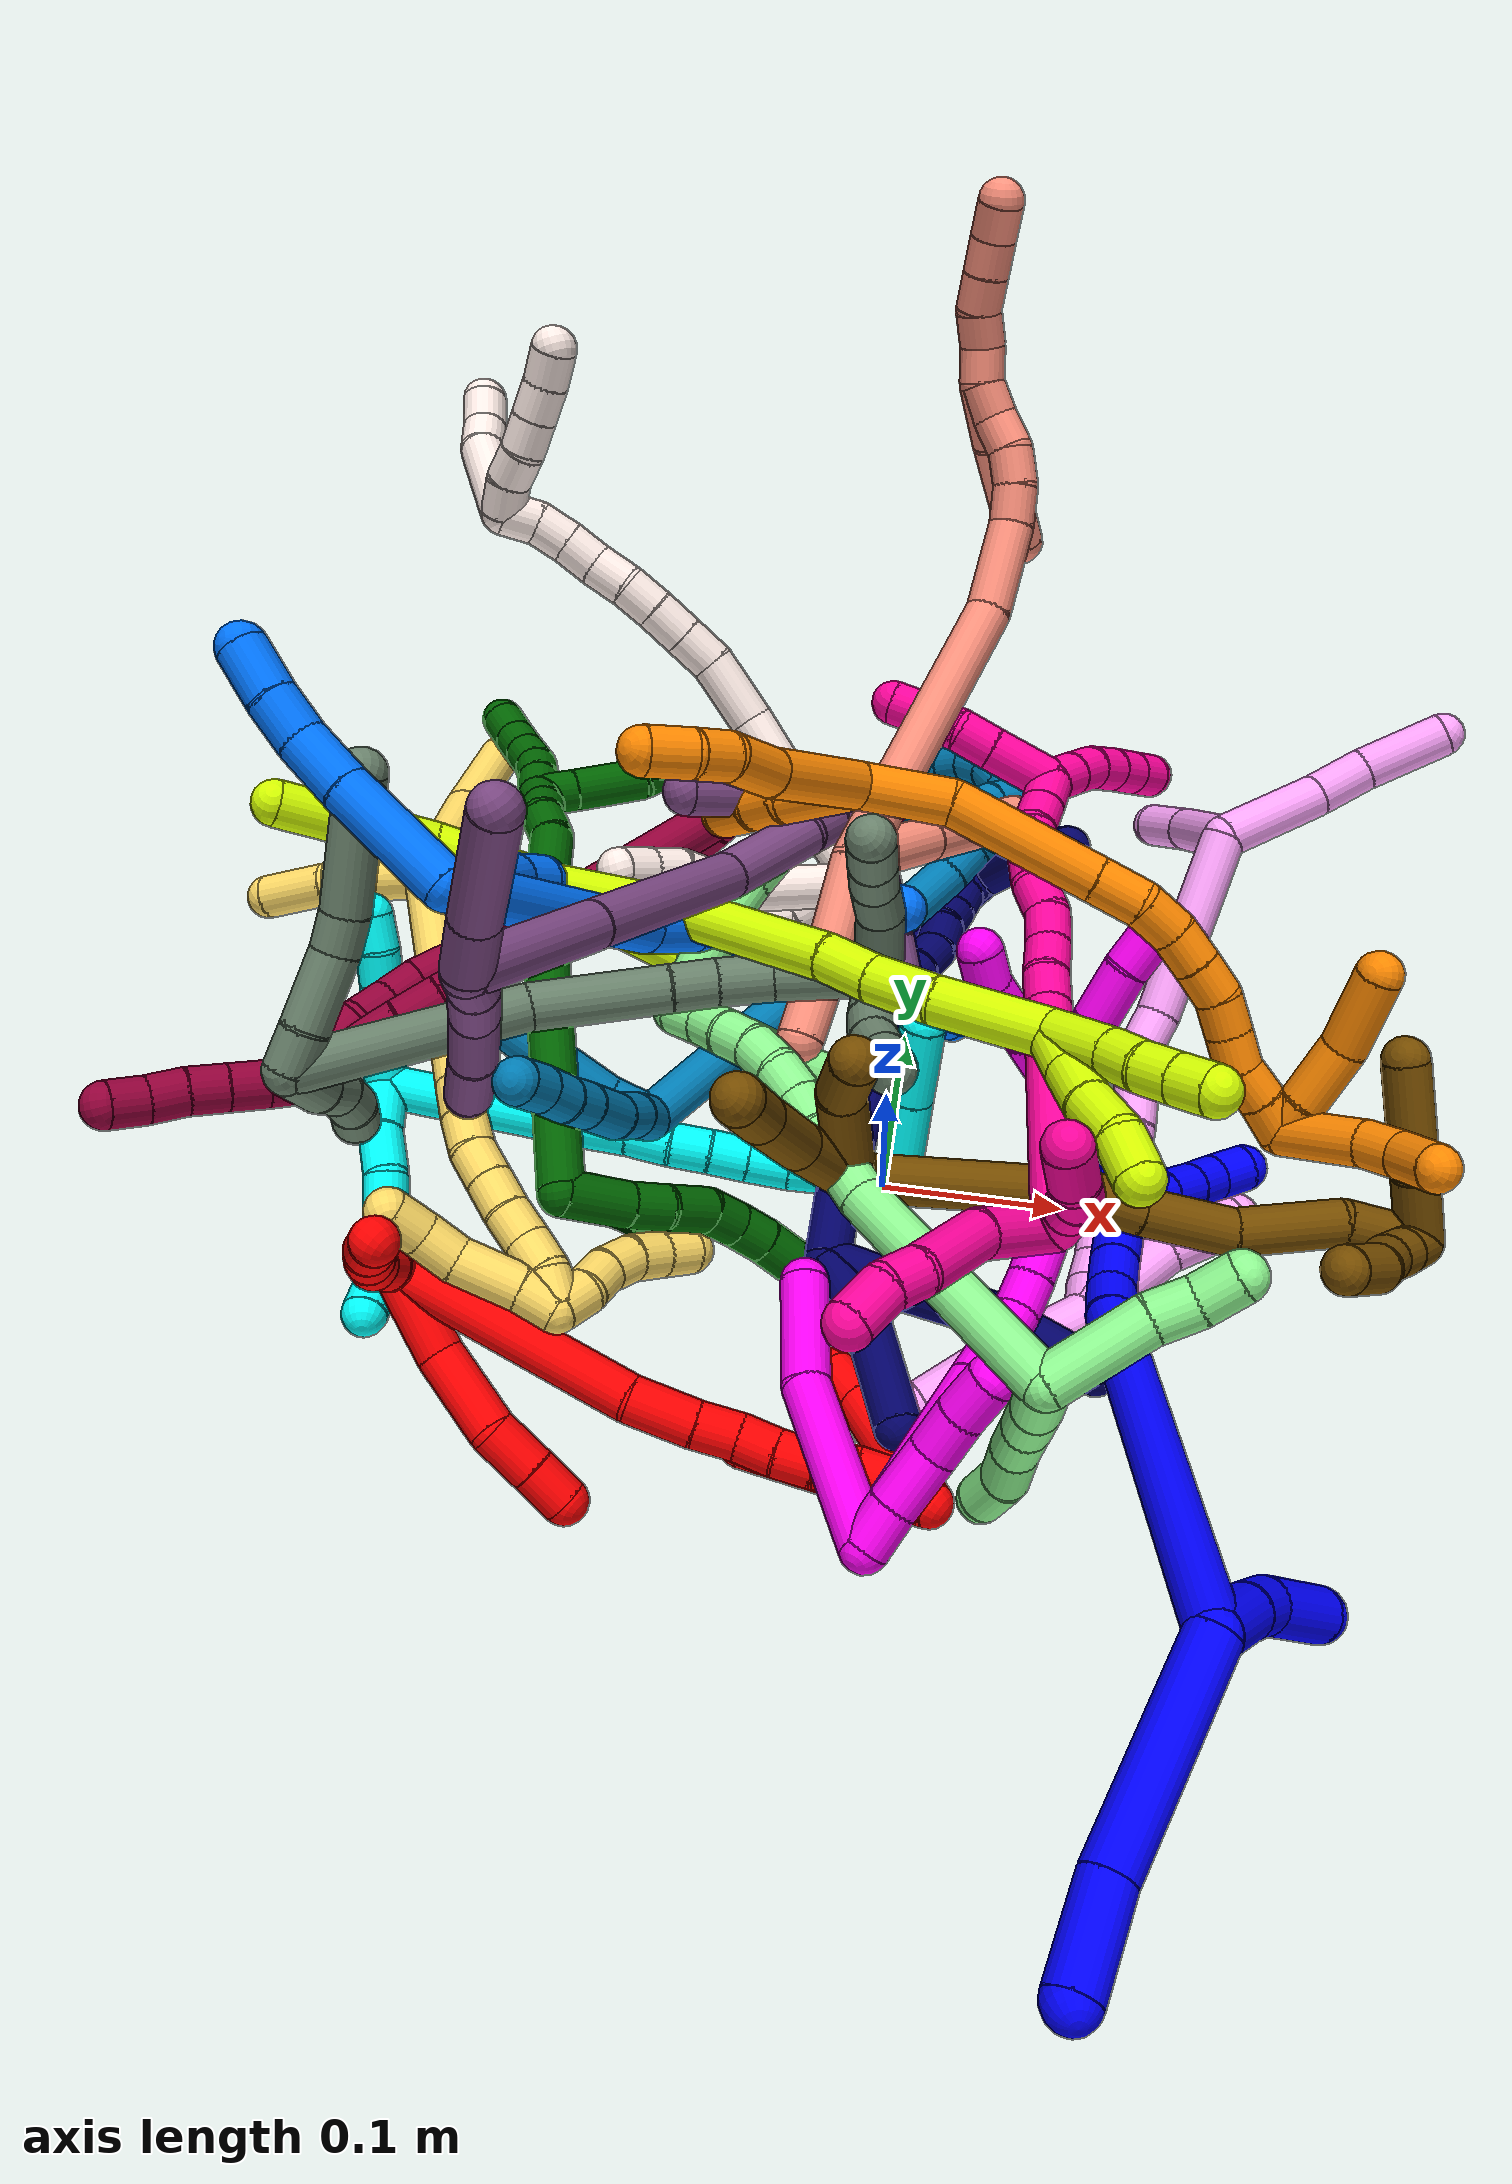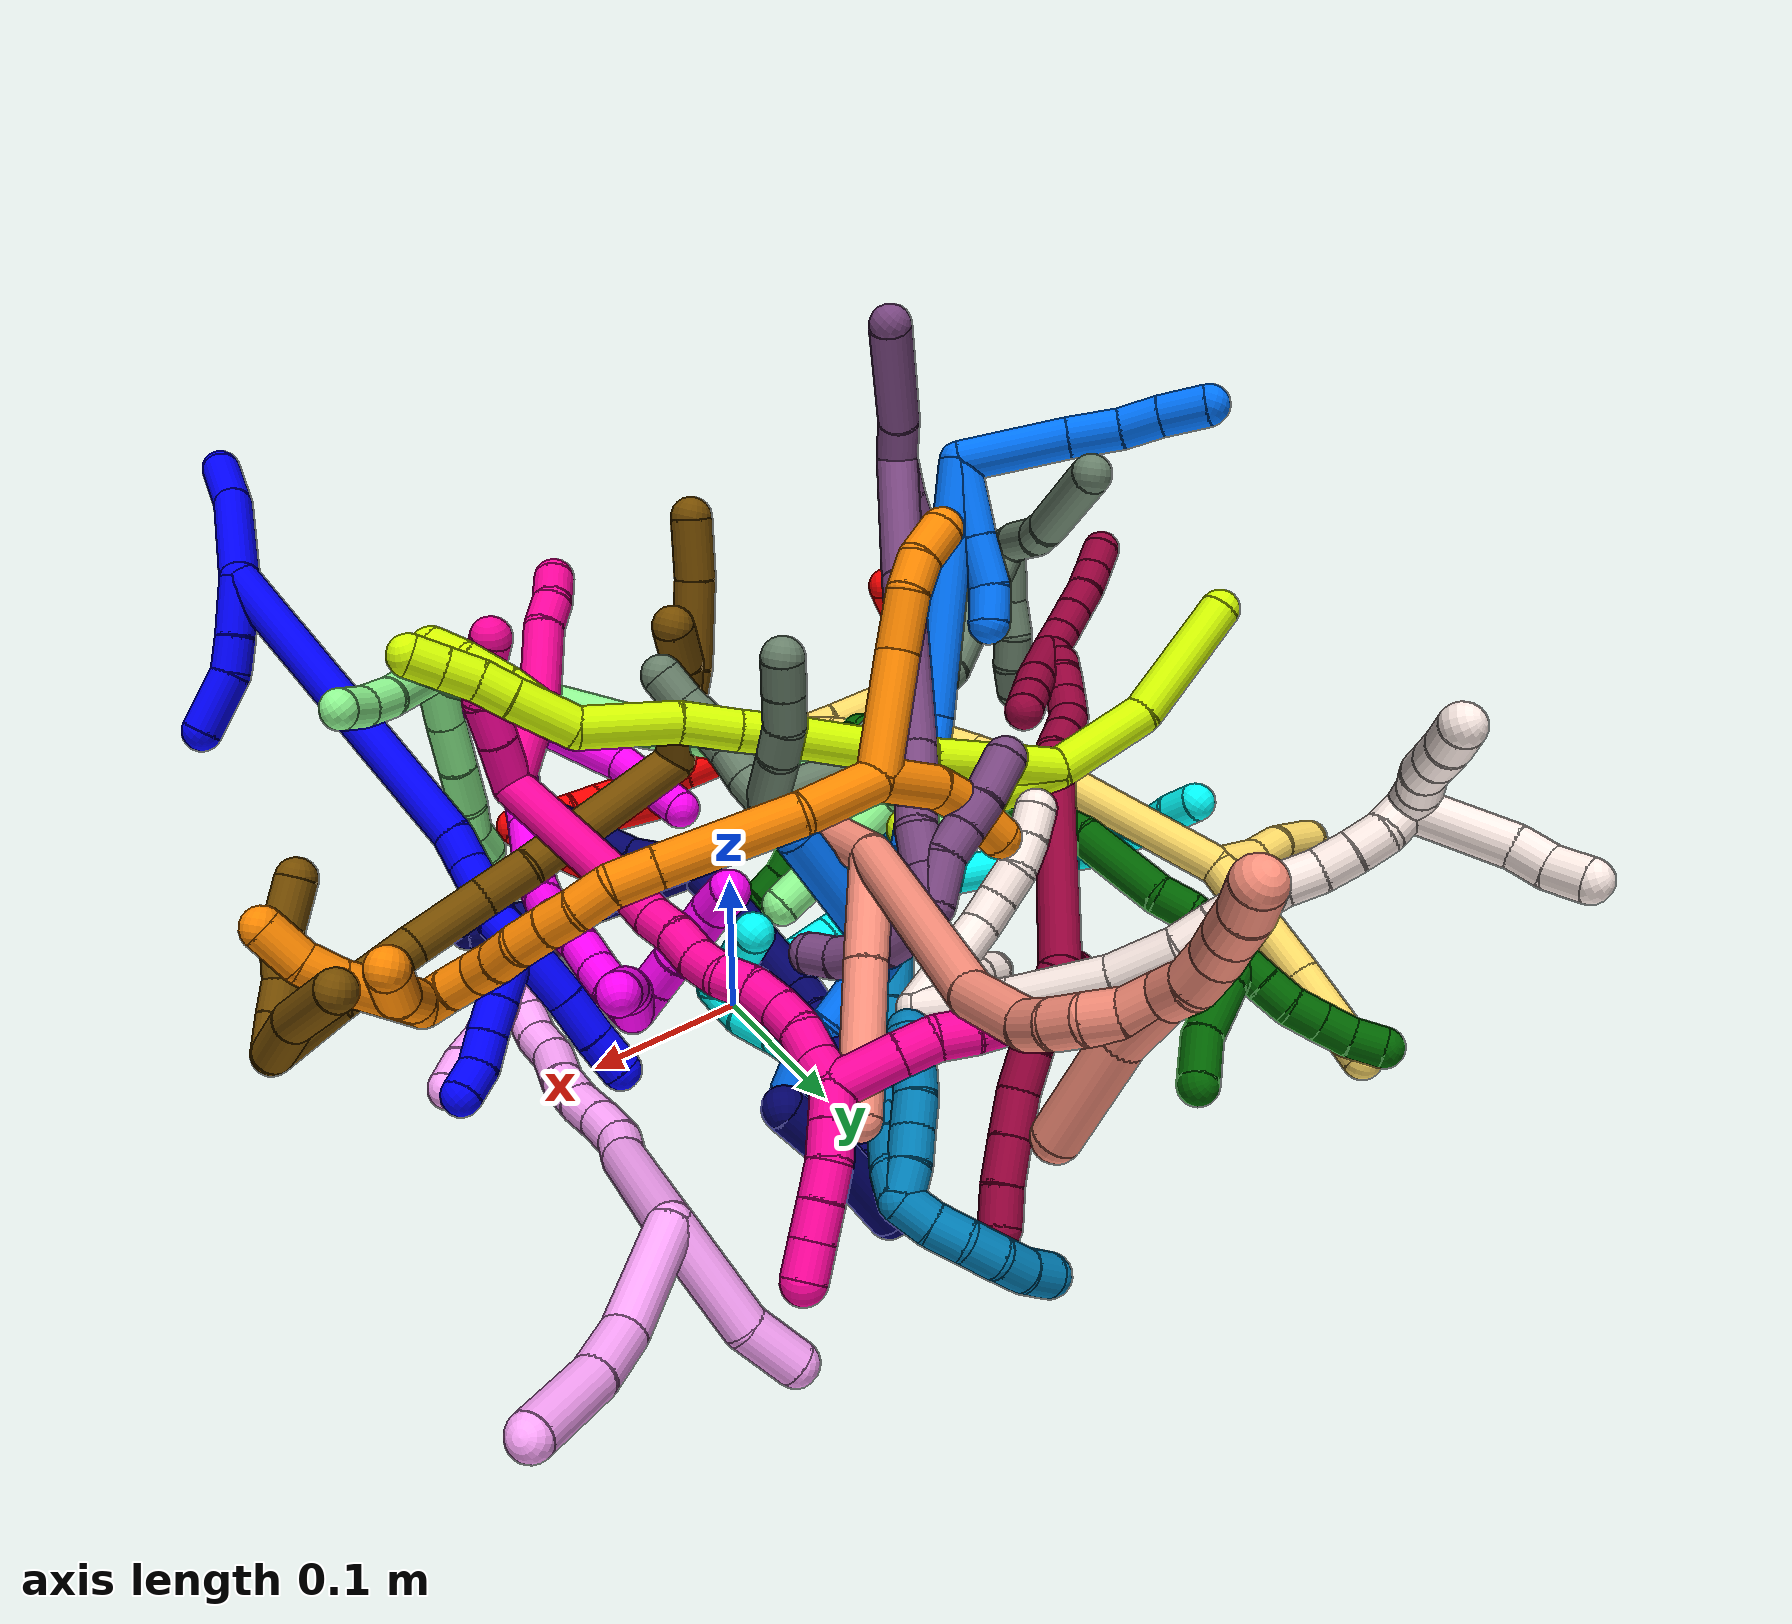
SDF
<sdf version="1.7">
 <world name="default">
  <plugin name="TubeGeneratorPlugin" filename="libtube_generator_plugin.so"/>
  <model name="photoneo_s_sensor">
   <static>1</static>
   <pose>0 0 2 1.57079 1.57079 3.14159</pose>
   <link name="link">
    <inertial><mass>0.1</mass></inertial>
    <sensor name="sensor" type="depth">
     <update_rate>30</update_rate>
     <camera>
      <horizontal_fov>1.22</horizontal_fov>
      <image><width>1920</width><height>1200</height><format>B8G8R8</format></image>
      <clip><near>0.1</near><far>4</far></clip>
      <depth_camera><output>points</output></depth_camera>
     </camera>
     <plugin name="camera_plugin" filename="libgazebo_ros_depth_camera.so">
      <baseline>0.2</baseline>
      <alwaysOn>1</alwaysOn>
      <updateRate>0.0</updateRate>
      <cameraName>camera_ir</cameraName>
      <imageTopicName>/camera/color/image_raw</imageTopicName>
      <cameraInfoTopicName>/camera/color/camera_info</cameraInfoTopicName>
      <depthImageTopicName>/camera/depth/image_raw</depthImageTopicName>
      <depthImageCameraInfoTopicName>/camera/depth/camera_info</depthImageCameraInfoTopicName>
      <pointCloudTopicName>/camera/depth/points</pointCloudTopicName>
      <frameName>fr_optical</frameName>
      <pointCloudCutoff>0.1</pointCloudCutoff>
      <pointCloudCutoffMax>2.0</pointCloudCutoffMax>
      <distortionK1>0</distortionK1>
      <distortionK2>0</distortionK2>
      <distortionK3>0</distortionK3>
      <distortionT1>0</distortionT1>
      <distortionT2>0</distortionT2>
      <CxPrime>0</CxPrime>
      <Cx>0</Cx>
      <Cy>0</Cy>
      <focalLength>0</focalLength>
      <hackBaseline>0</hackBaseline>
     </plugin>
    </sensor>
   </link>
  </model>
  <gravity>0 0 -9.8</gravity>
  <magnetic_field>6e-06 2.3e-05 -4.2e-05</magnetic_field>
  <atmosphere type="adiabatic"/>
  <physics name="default_physics" default="0" type="ode">
   <max_step_size>0.003</max_step_size>
   <real_time_factor>1</real_time_factor>
   <real_time_update_rate>1000</real_time_update_rate>
   <max_contacts>10000</max_contacts>
   <ode>
    <solver>
     <type>quick</type>
     <iters>100</iters>
     <sor>1.3</sor>
     <use_dynamic_moi_rescaling>0</use_dynamic_moi_rescaling>
    </solver>
    <constraints>
     <contact_max_correcting_vel>0</contact_max_correcting_vel>
     <contact_surface_layer>0.001</contact_surface_layer>
     <cfm>0</cfm>
     <erp>0.2</erp>
    </constraints>
   </ode>
  </physics>
  <scene><ambient>0.4 0.4 0.4 1</ambient><background>0.7 0.7 0.7 1</background><shadows>0</shadows></scene>
  <audio><device>default</device></audio>
  <spherical_coordinates>
   <surface_model>EARTH_WGS84</surface_model>
   <latitude_deg>0</latitude_deg>
   <longitude_deg>0</longitude_deg>
   <elevation>0</elevation>
   <heading_deg>0</heading_deg>
  </spherical_coordinates>
  <model name="bin">
   <static>1</static>
   <link name="bottom">
    <collision name="collision-bottom">
     <pose>0 0 -0.01 0 -0 0</pose>
     <geometry><box><size>0.8 0.6 0.02</size></box></geometry>
     <surface>
      <friction><ode><mu>100</mu><mu2>100</mu2></ode></friction>
      <contact><collide_bitmask>65535</collide_bitmask></contact>
     </surface>
    </collision>
   </link>
   <link name="west_wall">
    <collision name="collision-west_wall">
     <pose>-0.41 0 0.1 0 -0 0</pose>
     <geometry><box><size>0.02 0.6 0.2</size></box></geometry>
     <surface>
      <friction><ode><mu>100</mu><mu2>100</mu2></ode></friction>
      <contact><collide_bitmask>65535</collide_bitmask></contact>
     </surface>
    </collision>
   </link>
   <link name="east_wall">
    <collision name="collision-east_wall">
     <pose>0.41 0 0.1 0 -0 0</pose>
     <geometry><box><size>0.02 0.6 0.2</size></box></geometry>
     <surface>
      <friction><ode><mu>100</mu><mu2>100</mu2></ode></friction>
      <contact><collide_bitmask>65535</collide_bitmask></contact>
     </surface>
    </collision>
   </link>
   <link name="south_wall">
    <collision name="collision-south_wall">
     <pose>0 -0.31 0.1 0 -0 0</pose>
     <geometry><box><size>0.8 0.02 0.2</size></box></geometry>
     <surface>
      <friction><ode><mu>100</mu><mu2>100</mu2></ode></friction>
      <contact><collide_bitmask>65535</collide_bitmask></contact>
     </surface>
    </collision>
   </link>
   <link name="north_wall">
    <collision name="collision-north_wall">
     <pose>0 0.31 0.1 0 -0 0</pose>
     <geometry><box><size>0.8 0.02 0.2</size></box></geometry>
     <surface>
      <friction><ode><mu>100</mu><mu2>100</mu2></ode></friction>
      <contact><collide_bitmask>65535</collide_bitmask></contact>
     </surface>
    </collision>
   </link>
  </model>
  <model name="1">
   <static>0</static>
   <link name="1">
    <collision name="collision-cylinder-e_1_2_8">
     <pose>0.035042 0.009426 0.037228 -0.247975 0.739671 -0.096554</pose>
     <geometry><cylinder><radius>0.0125</radius><length>0.103975</length></cylinder></geometry>
     <surface>
      <friction><ode><mu>1.16</mu><mu2>1.16</mu2><slip1>0</slip1><slip2>0</slip2></ode></friction>
      <contact><ode><kp>1e+06</kp><kd>1</kd><max_vel>0</max_vel><min_depth>0.001</min_depth></ode></contact>
     </surface>
    </collision>
    <visual name="visual-cylinder-e_1_2_8">
     <pose>0.035042 0.009426 0.037228 -0.247975 0.739671 -0.096554</pose>
     <geometry><cylinder><radius>0.0125</radius><length>0.103975</length></cylinder></geometry>
     <material><ambient>0 0 1 1</ambient></material>
    </visual>
    <collision name="collision-cylinder-e_2_8_6">
     <pose>0.082821 0.022441 0.093282 -0.188404 0.586578 -0.057051</pose>
     <geometry><cylinder><radius>0.0125</radius><length>0.046025</length></cylinder></geometry>
     <surface>
      <friction><ode><mu>1.16</mu><mu2>1.16</mu2><slip1>0</slip1><slip2>0</slip2></ode></friction>
      <contact><ode><kp>1e+06</kp><kd>1</kd><max_vel>0</max_vel><min_depth>0.001</min_depth></ode></contact>
     </surface>
    </collision>
    <visual name="visual-cylinder-e_2_8_6">
     <pose>0.082821 0.022441 0.093282 -0.188404 0.586578 -0.057051</pose>
     <geometry><cylinder><radius>0.0125</radius><length>0.046025</length></cylinder></geometry>
     <material><ambient>0 0 1 1</ambient></material>
    </visual>
    <collision name="collision-cylinder-e_1_2_9">
     <pose>-0.006557 0.011292 -0.013206 -2.4342 -0.360854 0.917732</pose>
     <geometry><cylinder><radius>0.0125</radius><length>0.037143</length></cylinder></geometry>
     <surface>
      <friction><ode><mu>1.16</mu><mu2>1.16</mu2><slip1>0</slip1><slip2>0</slip2></ode></friction>
      <contact><ode><kp>1e+06</kp><kd>1</kd><max_vel>0</max_vel><min_depth>0.001</min_depth></ode></contact>
     </surface>
    </collision>
    <visual name="visual-cylinder-e_1_2_9">
     <pose>-0.006557 0.011292 -0.013206 -2.4342 -0.360854 0.917732</pose>
     <geometry><cylinder><radius>0.0125</radius><length>0.037143</length></cylinder></geometry>
     <material><ambient>0 0 1 1</ambient></material>
    </visual>
    <collision name="collision-cylinder-e_2_9_10">
     <pose>-0.016879 0.03031 -0.033884 -2.33939 -0.336915 0.762773</pose>
     <geometry><cylinder><radius>0.0125</radius><length>0.022776</length></cylinder></geometry>
     <surface>
      <friction><ode><mu>1.16</mu><mu2>1.16</mu2><slip1>0</slip1><slip2>0</slip2></ode></friction>
      <contact><ode><kp>1e+06</kp><kd>1</kd><max_vel>0</max_vel><min_depth>0.001</min_depth></ode></contact>
     </surface>
    </collision>
    <visual name="visual-cylinder-e_2_9_10">
     <pose>-0.016879 0.03031 -0.033884 -2.33939 -0.336915 0.762773</pose>
     <geometry><cylinder><radius>0.0125</radius><length>0.022776</length></cylinder></geometry>
     <material><ambient>0 0 1 1</ambient></material>
    </visual>
    <collision name="collision-cylinder-e_3_10_5">
     <pose>-0.030063 0.05408 -0.048803 -2.00542 -0.489297 0.745682</pose>
     <geometry><cylinder><radius>0.0125</radius><length>0.040081</length></cylinder></geometry>
     <surface>
      <friction><ode><mu>1.16</mu><mu2>1.16</mu2><slip1>0</slip1><slip2>0</slip2></ode></friction>
      <contact><ode><kp>1e+06</kp><kd>1</kd><max_vel>0</max_vel><min_depth>0.001</min_depth></ode></contact>
     </surface>
    </collision>
    <visual name="visual-cylinder-e_3_10_5">
     <pose>-0.030063 0.05408 -0.048803 -2.00542 -0.489297 0.745682</pose>
     <geometry><cylinder><radius>0.0125</radius><length>0.040081</length></cylinder></geometry>
     <material><ambient>0 0 1 1</ambient></material>
    </visual>
    <collision name="collision-cylinder-e_1_2_11">
     <pose>-0.002213 0.001608 -0.107829 -3.12668 -0.020521 1.88472</pose>
     <geometry><cylinder><radius>0.0125</radius><length>0.215728</length></cylinder></geometry>
     <surface>
      <friction><ode><mu>1.16</mu><mu2>1.16</mu2><slip1>0</slip1><slip2>0</slip2></ode></friction>
      <contact><ode><kp>1e+06</kp><kd>1</kd><max_vel>0</max_vel><min_depth>0.001</min_depth></ode></contact>
     </surface>
    </collision>
    <visual name="visual-cylinder-e_1_2_11">
     <pose>-0.002213 0.001608 -0.107829 -3.12668 -0.020521 1.88472</pose>
     <geometry><cylinder><radius>0.0125</radius><length>0.215728</length></cylinder></geometry>
     <material><ambient>0 0 1 1</ambient></material>
    </visual>
    <collision name="collision-cylinder-e_2_11_12">
     <pose>-0.006609 0.004516 -0.226307 -3.02013 -0.200658 2.05487</pose>
     <geometry><cylinder><radius>0.0125</radius><length>0.021894</length></cylinder></geometry>
     <surface>
      <friction><ode><mu>1.16</mu><mu2>1.16</mu2><slip1>0</slip1><slip2>0</slip2></ode></friction>
      <contact><ode><kp>1e+06</kp><kd>1</kd><max_vel>0</max_vel><min_depth>0.001</min_depth></ode></contact>
     </surface>
    </collision>
    <visual name="visual-cylinder-e_2_11_12">
     <pose>-0.006609 0.004516 -0.226307 -3.02013 -0.200658 2.05487</pose>
     <geometry><cylinder><radius>0.0125</radius><length>0.021894</length></cylinder></geometry>
     <material><ambient>0 0 1 1</ambient></material>
    </visual>
    <collision name="collision-cylinder-e_3_12_13">
     <pose>-0.011973 0.005909 -0.247324 -3.13266 -0.297775 3.08203</pose>
     <geometry><cylinder><radius>0.0125</radius><length>0.021691</length></cylinder></geometry>
     <surface>
      <friction><ode><mu>1.16</mu><mu2>1.16</mu2><slip1>0</slip1><slip2>0</slip2></ode></friction>
      <contact><ode><kp>1e+06</kp><kd>1</kd><max_vel>0</max_vel><min_depth>0.001</min_depth></ode></contact>
     </surface>
    </collision>
    <visual name="visual-cylinder-e_3_12_13">
     <pose>-0.011973 0.005909 -0.247324 -3.13266 -0.297775 3.08203</pose>
     <geometry><cylinder><radius>0.0125</radius><length>0.021691</length></cylinder></geometry>
     <material><ambient>0 0 1 1</ambient></material>
    </visual>
    <collision name="collision-cylinder-e_4_13_14">
     <pose>-0.018378 0.006458 -0.267468 -3.09492 -0.318176 2.85265</pose>
     <geometry><cylinder><radius>0.0125</radius><length>0.020609</length></cylinder></geometry>
     <surface>
      <friction><ode><mu>1.16</mu><mu2>1.16</mu2><slip1>0</slip1><slip2>0</slip2></ode></friction>
      <contact><ode><kp>1e+06</kp><kd>1</kd><max_vel>0</max_vel><min_depth>0.001</min_depth></ode></contact>
     </surface>
    </collision>
    <visual name="visual-cylinder-e_4_13_14">
     <pose>-0.018378 0.006458 -0.267468 -3.09492 -0.318176 2.85265</pose>
     <geometry><cylinder><radius>0.0125</radius><length>0.020609</length></cylinder></geometry>
     <material><ambient>0 0 1 1</ambient></material>
    </visual>
    <collision name="collision-cylinder-e_5_14_1">
     <pose>-0.024095 0.004098 -0.286552 2.84767 -0.251006 -1.41166</pose>
     <geometry><cylinder><radius>0.0125</radius><length>0.020077</length></cylinder></geometry>
     <surface>
      <friction><ode><mu>1.16</mu><mu2>1.16</mu2><slip1>0</slip1><slip2>0</slip2></ode></friction>
      <contact><ode><kp>1e+06</kp><kd>1</kd><max_vel>0</max_vel><min_depth>0.001</min_depth></ode></contact>
     </surface>
    </collision>
    <visual name="visual-cylinder-e_5_14_1">
     <pose>-0.024095 0.004098 -0.286552 2.84767 -0.251006 -1.41166</pose>
     <geometry><cylinder><radius>0.0125</radius><length>0.020077</length></cylinder></geometry>
     <material><ambient>0 0 1 1</ambient></material>
    </visual>
    <collision name="collision-cylinder-e_1_1_15">
     <pose>-0.038981 0.011217 -0.306429 -2.3871 -0.706933 1.49957</pose>
     <geometry><cylinder><radius>0.0125</radius><length>0.038159</length></cylinder></geometry>
     <surface>
      <friction><ode><mu>1.16</mu><mu2>1.16</mu2><slip1>0</slip1><slip2>0</slip2></ode></friction>
      <contact><ode><kp>1e+06</kp><kd>1</kd><max_vel>0</max_vel><min_depth>0.001</min_depth></ode></contact>
     </surface>
    </collision>
    <visual name="visual-cylinder-e_1_1_15">
     <pose>-0.038981 0.011217 -0.306429 -2.3871 -0.706933 1.49957</pose>
     <geometry><cylinder><radius>0.0125</radius><length>0.038159</length></cylinder></geometry>
     <material><ambient>0 0 1 1</ambient></material>
    </visual>
    <collision name="collision-cylinder-e_2_15_16">
     <pose>-0.058616 0.026562 -0.323096 -2.41594 -0.726503 1.57208</pose>
     <geometry><cylinder><radius>0.0125</radius><length>0.021807</length></cylinder></geometry>
     <surface>
      <friction><ode><mu>1.16</mu><mu2>1.16</mu2><slip1>0</slip1><slip2>0</slip2></ode></friction>
      <contact><ode><kp>1e+06</kp><kd>1</kd><max_vel>0</max_vel><min_depth>0.001</min_depth></ode></contact>
     </surface>
    </collision>
    <visual name="visual-cylinder-e_2_15_16">
     <pose>-0.058616 0.026562 -0.323096 -2.41594 -0.726503 1.57208</pose>
     <geometry><cylinder><radius>0.0125</radius><length>0.021807</length></cylinder></geometry>
     <material><ambient>0 0 1 1</ambient></material>
    </visual>
    <collision name="collision-cylinder-e_3_16_17">
     <pose>-0.072462 0.03661 -0.335112 -2.47683 -0.7206 1.65817</pose>
     <geometry><cylinder><radius>0.0125</radius><length>0.020017</length></cylinder></geometry>
     <surface>
      <friction><ode><mu>1.16</mu><mu2>1.16</mu2><slip1>0</slip1><slip2>0</slip2></ode></friction>
      <contact><ode><kp>1e+06</kp><kd>1</kd><max_vel>0</max_vel><min_depth>0.001</min_depth></ode></contact>
     </surface>
    </collision>
    <visual name="visual-cylinder-e_3_16_17">
     <pose>-0.072462 0.03661 -0.335112 -2.47683 -0.7206 1.65817</pose>
     <geometry><cylinder><radius>0.0125</radius><length>0.020017</length></cylinder></geometry>
     <material><ambient>0 0 1 1</ambient></material>
    </visual>
    <collision name="collision-cylinder-e_4_17_4">
     <pose>-0.087746 0.044724 -0.344603 -2.36994 -1.04964 1.91806</pose>
     <geometry><cylinder><radius>0.0125</radius><length>0.020017</length></cylinder></geometry>
     <surface>
      <friction><ode><mu>1.16</mu><mu2>1.16</mu2><slip1>0</slip1><slip2>0</slip2></ode></friction>
      <contact><ode><kp>1e+06</kp><kd>1</kd><max_vel>0</max_vel><min_depth>0.001</min_depth></ode></contact>
     </surface>
    </collision>
    <visual name="visual-cylinder-e_4_17_4">
     <pose>-0.087746 0.044724 -0.344603 -2.36994 -1.04964 1.91806</pose>
     <geometry><cylinder><radius>0.0125</radius><length>0.020017</length></cylinder></geometry>
     <material><ambient>0 0 1 1</ambient></material>
    </visual>
    <collision name="collision-cylinder-e_1_1_18">
     <pose>-0.021312 0.006106 -0.316945 -2.91662 0.239247 -1.63281</pose>
     <geometry><cylinder><radius>0.0125</radius><length>0.044531</length></cylinder></geometry>
     <surface>
      <friction><ode><mu>1.16</mu><mu2>1.16</mu2><slip1>0</slip1><slip2>0</slip2></ode></friction>
      <contact><ode><kp>1e+06</kp><kd>1</kd><max_vel>0</max_vel><min_depth>0.001</min_depth></ode></contact>
     </surface>
    </collision>
    <visual name="visual-cylinder-e_1_1_18">
     <pose>-0.021312 0.006106 -0.316945 -2.91662 0.239247 -1.63281</pose>
     <geometry><cylinder><radius>0.0125</radius><length>0.044531</length></cylinder></geometry>
     <material><ambient>0 0 1 1</ambient></material>
    </visual>
    <collision name="collision-cylinder-e_2_18_19">
     <pose>-0.012971 0.015128 -0.351907 -2.84788 0.208377 -1.2307</pose>
     <geometry><cylinder><radius>0.0125</radius><length>0.029633</length></cylinder></geometry>
     <surface>
      <friction><ode><mu>1.16</mu><mu2>1.16</mu2><slip1>0</slip1><slip2>0</slip2></ode></friction>
      <contact><ode><kp>1e+06</kp><kd>1</kd><max_vel>0</max_vel><min_depth>0.001</min_depth></ode></contact>
     </surface>
    </collision>
    <visual name="visual-cylinder-e_2_18_19">
     <pose>-0.012971 0.015128 -0.351907 -2.84788 0.208377 -1.2307</pose>
     <geometry><cylinder><radius>0.0125</radius><length>0.029633</length></cylinder></geometry>
     <material><ambient>0 0 1 1</ambient></material>
    </visual>
    <collision name="collision-cylinder-e_3_19_3">
     <pose>-0.006365 0.022754 -0.377723 -2.86197 0.277622 -1.56353</pose>
     <geometry><cylinder><radius>0.0125</radius><length>0.025836</length></cylinder></geometry>
     <surface>
      <friction><ode><mu>1.16</mu><mu2>1.16</mu2><slip1>0</slip1><slip2>0</slip2></ode></friction>
      <contact><ode><kp>1e+06</kp><kd>1</kd><max_vel>0</max_vel><min_depth>0.001</min_depth></ode></contact>
     </surface>
    </collision>
    <visual name="visual-cylinder-e_3_19_3">
     <pose>-0.006365 0.022754 -0.377723 -2.86197 0.277622 -1.56353</pose>
     <geometry><cylinder><radius>0.0125</radius><length>0.025836</length></cylinder></geometry>
     <material><ambient>0 0 1 1</ambient></material>
    </visual>
    <collision name="collision-sphere-3">
     <pose>-0.002825 0.026183 -0.389663 0 -0 0</pose>
     <geometry><sphere><radius>0.0125</radius></sphere></geometry>
     <surface>
      <friction><ode><mu>1.16</mu><mu2>1.16</mu2><slip1>0</slip1><slip2>0</slip2></ode></friction>
      <contact><ode><kp>1e+06</kp><kd>1</kd><max_vel>0</max_vel><min_depth>0.001</min_depth></ode></contact>
     </surface>
    </collision>
    <visual name="visual-sphere-3">
     <pose>-0.002825 0.026183 -0.389663 0 -0 0</pose>
     <geometry><sphere><radius>0.0125</radius></sphere></geometry>
     <material><ambient>0 0 1 1</ambient></material>
    </visual>
    <collision name="collision-sphere-19">
     <pose>-0.009906 0.019325 -0.365782 0 -0 0</pose>
     <geometry><sphere><radius>0.0125</radius></sphere></geometry>
     <surface>
      <friction><ode><mu>1.16</mu><mu2>1.16</mu2><slip1>0</slip1><slip2>0</slip2></ode></friction>
      <contact><ode><kp>1e+06</kp><kd>1</kd><max_vel>0</max_vel><min_depth>0.001</min_depth></ode></contact>
     </surface>
    </collision>
    <visual name="visual-sphere-19">
     <pose>-0.009906 0.019325 -0.365782 0 -0 0</pose>
     <geometry><sphere><radius>0.0125</radius></sphere></geometry>
     <material><ambient>0 0 1 1</ambient></material>
    </visual>
    <collision name="collision-sphere-5">
     <pose>-0.039482 0.070125 -0.056252 0 -0 0</pose>
     <geometry><sphere><radius>0.0125</radius></sphere></geometry>
     <surface>
      <friction><ode><mu>1.16</mu><mu2>1.16</mu2><slip1>0</slip1><slip2>0</slip2></ode></friction>
      <contact><ode><kp>1e+06</kp><kd>1</kd><max_vel>0</max_vel><min_depth>0.001</min_depth></ode></contact>
     </surface>
    </collision>
    <visual name="visual-sphere-5">
     <pose>-0.039482 0.070125 -0.056252 0 -0 0</pose>
     <geometry><sphere><radius>0.0125</radius></sphere></geometry>
     <material><ambient>0 0 1 1</ambient></material>
    </visual>
    <collision name="collision-sphere-10">
     <pose>-0.020643 0.038036 -0.041355 0 -0 0</pose>
     <geometry><sphere><radius>0.0125</radius></sphere></geometry>
     <surface>
      <friction><ode><mu>1.16</mu><mu2>1.16</mu2><slip1>0</slip1><slip2>0</slip2></ode></friction>
      <contact><ode><kp>1e+06</kp><kd>1</kd><max_vel>0</max_vel><min_depth>0.001</min_depth></ode></contact>
     </surface>
    </collision>
    <visual name="visual-sphere-10">
     <pose>-0.020643 0.038036 -0.041355 0 -0 0</pose>
     <geometry><sphere><radius>0.0125</radius></sphere></geometry>
     <material><ambient>0 0 1 1</ambient></material>
    </visual>
    <collision name="collision-sphere-6">
     <pose>0.095559 0.02603 0.112109 0 -0 0</pose>
     <geometry><sphere><radius>0.0125</radius></sphere></geometry>
     <surface>
      <friction><ode><mu>1.16</mu><mu2>1.16</mu2><slip1>0</slip1><slip2>0</slip2></ode></friction>
      <contact><ode><kp>1e+06</kp><kd>1</kd><max_vel>0</max_vel><min_depth>0.001</min_depth></ode></contact>
     </surface>
    </collision>
    <visual name="visual-sphere-6">
     <pose>0.095559 0.02603 0.112109 0 -0 0</pose>
     <geometry><sphere><radius>0.0125</radius></sphere></geometry>
     <material><ambient>0 0 1 1</ambient></material>
    </visual>
    <collision name="collision-sphere-9">
     <pose>-0.013114 0.022583 -0.026413 0 -0 0</pose>
     <geometry><sphere><radius>0.0125</radius></sphere></geometry>
     <surface>
      <friction><ode><mu>1.16</mu><mu2>1.16</mu2><slip1>0</slip1><slip2>0</slip2></ode></friction>
      <contact><ode><kp>1e+06</kp><kd>1</kd><max_vel>0</max_vel><min_depth>0.001</min_depth></ode></contact>
     </surface>
    </collision>
    <visual name="visual-sphere-9">
     <pose>-0.013114 0.022583 -0.026413 0 -0 0</pose>
     <geometry><sphere><radius>0.0125</radius></sphere></geometry>
     <material><ambient>0 0 1 1</ambient></material>
    </visual>
    <collision name="collision-sphere-2">
     <geometry><sphere><radius>0.0125</radius></sphere></geometry>
     <surface>
      <friction><ode><mu>1.16</mu><mu2>1.16</mu2><slip1>0</slip1><slip2>0</slip2></ode></friction>
      <contact><ode><kp>1e+06</kp><kd>1</kd><max_vel>0</max_vel><min_depth>0.001</min_depth></ode></contact>
     </surface>
    </collision>
    <visual name="visual-sphere-2">
     <geometry><sphere><radius>0.0125</radius></sphere></geometry>
     <material><ambient>0 0 1 1</ambient></material>
    </visual>
    <collision name="collision-sphere-8">
     <pose>0.070084 0.018851 0.074456 0 -0 0</pose>
     <geometry><sphere><radius>0.0125</radius></sphere></geometry>
     <surface>
      <friction><ode><mu>1.16</mu><mu2>1.16</mu2><slip1>0</slip1><slip2>0</slip2></ode></friction>
      <contact><ode><kp>1e+06</kp><kd>1</kd><max_vel>0</max_vel><min_depth>0.001</min_depth></ode></contact>
     </surface>
    </collision>
    <visual name="visual-sphere-8">
     <pose>0.070084 0.018851 0.074456 0 -0 0</pose>
     <geometry><sphere><radius>0.0125</radius></sphere></geometry>
     <material><ambient>0 0 1 1</ambient></material>
    </visual>
    <collision name="collision-sphere-11">
     <pose>-0.004427 0.003216 -0.215659 0 -0 0</pose>
     <geometry><sphere><radius>0.0125</radius></sphere></geometry>
     <surface>
      <friction><ode><mu>1.16</mu><mu2>1.16</mu2><slip1>0</slip1><slip2>0</slip2></ode></friction>
      <contact><ode><kp>1e+06</kp><kd>1</kd><max_vel>0</max_vel><min_depth>0.001</min_depth></ode></contact>
     </surface>
    </collision>
    <visual name="visual-sphere-11">
     <pose>-0.004427 0.003216 -0.215659 0 -0 0</pose>
     <geometry><sphere><radius>0.0125</radius></sphere></geometry>
     <material><ambient>0 0 1 1</ambient></material>
    </visual>
    <collision name="collision-sphere-12">
     <pose>-0.008791 0.005816 -0.236956 0 -0 0</pose>
     <geometry><sphere><radius>0.0125</radius></sphere></geometry>
     <surface>
      <friction><ode><mu>1.16</mu><mu2>1.16</mu2><slip1>0</slip1><slip2>0</slip2></ode></friction>
      <contact><ode><kp>1e+06</kp><kd>1</kd><max_vel>0</max_vel><min_depth>0.001</min_depth></ode></contact>
     </surface>
    </collision>
    <visual name="visual-sphere-12">
     <pose>-0.008791 0.005816 -0.236956 0 -0 0</pose>
     <geometry><sphere><radius>0.0125</radius></sphere></geometry>
     <material><ambient>0 0 1 1</ambient></material>
    </visual>
    <collision name="collision-sphere-13">
     <pose>-0.015155 0.006001 -0.257692 0 -0 0</pose>
     <geometry><sphere><radius>0.0125</radius></sphere></geometry>
     <surface>
      <friction><ode><mu>1.16</mu><mu2>1.16</mu2><slip1>0</slip1><slip2>0</slip2></ode></friction>
      <contact><ode><kp>1e+06</kp><kd>1</kd><max_vel>0</max_vel><min_depth>0.001</min_depth></ode></contact>
     </surface>
    </collision>
    <visual name="visual-sphere-13">
     <pose>-0.015155 0.006001 -0.257692 0 -0 0</pose>
     <geometry><sphere><radius>0.0125</radius></sphere></geometry>
     <material><ambient>0 0 1 1</ambient></material>
    </visual>
    <collision name="collision-sphere-14">
     <pose>-0.021602 0.006915 -0.277245 0 -0 0</pose>
     <geometry><sphere><radius>0.0125</radius></sphere></geometry>
     <surface>
      <friction><ode><mu>1.16</mu><mu2>1.16</mu2><slip1>0</slip1><slip2>0</slip2></ode></friction>
      <contact><ode><kp>1e+06</kp><kd>1</kd><max_vel>0</max_vel><min_depth>0.001</min_depth></ode></contact>
     </surface>
    </collision>
    <visual name="visual-sphere-14">
     <pose>-0.021602 0.006915 -0.277245 0 -0 0</pose>
     <geometry><sphere><radius>0.0125</radius></sphere></geometry>
     <material><ambient>0 0 1 1</ambient></material>
    </visual>
    <collision name="collision-sphere-1">
     <pose>-0.026589 0.00128 -0.295859 0 -0 0</pose>
     <geometry><sphere><radius>0.0125</radius></sphere></geometry>
     <surface>
      <friction><ode><mu>1.16</mu><mu2>1.16</mu2><slip1>0</slip1><slip2>0</slip2></ode></friction>
      <contact><ode><kp>1e+06</kp><kd>1</kd><max_vel>0</max_vel><min_depth>0.001</min_depth></ode></contact>
     </surface>
    </collision>
    <visual name="visual-sphere-1">
     <pose>-0.026589 0.00128 -0.295859 0 -0 0</pose>
     <geometry><sphere><radius>0.0125</radius></sphere></geometry>
     <material><ambient>0 0 1 1</ambient></material>
    </visual>
    <collision name="collision-sphere-18">
     <pose>-0.016036 0.010932 -0.338031 0 -0 0</pose>
     <geometry><sphere><radius>0.0125</radius></sphere></geometry>
     <surface>
      <friction><ode><mu>1.16</mu><mu2>1.16</mu2><slip1>0</slip1><slip2>0</slip2></ode></friction>
      <contact><ode><kp>1e+06</kp><kd>1</kd><max_vel>0</max_vel><min_depth>0.001</min_depth></ode></contact>
     </surface>
    </collision>
    <visual name="visual-sphere-18">
     <pose>-0.016036 0.010932 -0.338031 0 -0 0</pose>
     <geometry><sphere><radius>0.0125</radius></sphere></geometry>
     <material><ambient>0 0 1 1</ambient></material>
    </visual>
    <collision name="collision-sphere-15">
     <pose>-0.051373 0.021153 -0.316999 0 -0 0</pose>
     <geometry><sphere><radius>0.0125</radius></sphere></geometry>
     <surface>
      <friction><ode><mu>1.16</mu><mu2>1.16</mu2><slip1>0</slip1><slip2>0</slip2></ode></friction>
      <contact><ode><kp>1e+06</kp><kd>1</kd><max_vel>0</max_vel><min_depth>0.001</min_depth></ode></contact>
     </surface>
    </collision>
    <visual name="visual-sphere-15">
     <pose>-0.051373 0.021153 -0.316999 0 -0 0</pose>
     <geometry><sphere><radius>0.0125</radius></sphere></geometry>
     <material><ambient>0 0 1 1</ambient></material>
    </visual>
    <collision name="collision-sphere-16">
     <pose>-0.065858 0.03197 -0.329193 0 -0 0</pose>
     <geometry><sphere><radius>0.0125</radius></sphere></geometry>
     <surface>
      <friction><ode><mu>1.16</mu><mu2>1.16</mu2><slip1>0</slip1><slip2>0</slip2></ode></friction>
      <contact><ode><kp>1e+06</kp><kd>1</kd><max_vel>0</max_vel><min_depth>0.001</min_depth></ode></contact>
     </surface>
    </collision>
    <visual name="visual-sphere-16">
     <pose>-0.065858 0.03197 -0.329193 0 -0 0</pose>
     <geometry><sphere><radius>0.0125</radius></sphere></geometry>
     <material><ambient>0 0 1 1</ambient></material>
    </visual>
    <collision name="collision-sphere-17">
     <pose>-0.079066 0.041249 -0.341032 0 -0 0</pose>
     <geometry><sphere><radius>0.0125</radius></sphere></geometry>
     <surface>
      <friction><ode><mu>1.16</mu><mu2>1.16</mu2><slip1>0</slip1><slip2>0</slip2></ode></friction>
      <contact><ode><kp>1e+06</kp><kd>1</kd><max_vel>0</max_vel><min_depth>0.001</min_depth></ode></contact>
     </surface>
    </collision>
    <visual name="visual-sphere-17">
     <pose>-0.079066 0.041249 -0.341032 0 -0 0</pose>
     <geometry><sphere><radius>0.0125</radius></sphere></geometry>
     <material><ambient>0 0 1 1</ambient></material>
    </visual>
    <collision name="collision-sphere-4">
     <pose>-0.096426 0.048198 -0.348175 0 -0 0</pose>
     <geometry><sphere><radius>0.0125</radius></sphere></geometry>
     <surface>
      <friction><ode><mu>1.16</mu><mu2>1.16</mu2><slip1>0</slip1><slip2>0</slip2></ode></friction>
      <contact><ode><kp>1e+06</kp><kd>1</kd><max_vel>0</max_vel><min_depth>0.001</min_depth></ode></contact>
     </surface>
    </collision>
    <visual name="visual-sphere-4">
     <pose>-0.096426 0.048198 -0.348175 0 -0 0</pose>
     <geometry><sphere><radius>0.0125</radius></sphere></geometry>
     <material><ambient>0 0 1 1</ambient></material>
    </visual>
    <inertial>
     <pose>-0.00479 0.013364 -0.142062 0 -0 0</pose>
     <mass>0.75</mass>
     <inertia>
      <ixx>0.000624</ixx>
      <ixy>0</ixy>
      <ixz>0</ixz>
      <iyy>0.001187</iyy>
      <iyz>0</iyz>
      <izz>-0.000124</izz>
     </inertia>
    </inertial>
   </link>
   <pose>0.167826 -0.300667 0.220873 -1.03965 0.308289 -2.70317</pose>
  </model>
  <model name="2">
   <static>0</static>
   <link name="2">
    <collision name="collision-cylinder-e_1_2_8">
     <pose>-0.012496 0.001239 -0.021786 -3.08479 -0.520089 2.92886</pose>
     <geometry><cylinder><radius>0.0125</radius><length>0.050291</length></cylinder></geometry>
     <surface>
      <friction><ode><mu>1.16</mu><mu2>1.16</mu2><slip1>0</slip1><slip2>0</slip2></ode></friction>
      <contact><ode><kp>1e+06</kp><kd>1</kd><max_vel>0</max_vel><min_depth>0.001</min_depth></ode></contact>
     </surface>
    </collision>
    <visual name="visual-cylinder-e_1_2_8">
     <pose>-0.012496 0.001239 -0.021786 -3.08479 -0.520089 2.92886</pose>
     <geometry><cylinder><radius>0.0125</radius><length>0.050291</length></cylinder></geometry>
     <material><ambient>1 0 0 1</ambient></material>
    </visual>
    <collision name="collision-cylinder-e_2_8_9">
     <pose>-0.031151 0.000311 -0.066778 3.04848 -0.258321 -2.45281</pose>
     <geometry><cylinder><radius>0.0125</radius><length>0.048216</length></cylinder></geometry>
     <surface>
      <friction><ode><mu>1.16</mu><mu2>1.16</mu2><slip1>0</slip1><slip2>0</slip2></ode></friction>
      <contact><ode><kp>1e+06</kp><kd>1</kd><max_vel>0</max_vel><min_depth>0.001</min_depth></ode></contact>
     </surface>
    </collision>
    <visual name="visual-cylinder-e_2_8_9">
     <pose>-0.031151 0.000311 -0.066778 3.04848 -0.258321 -2.45281</pose>
     <geometry><cylinder><radius>0.0125</radius><length>0.048216</length></cylinder></geometry>
     <material><ambient>1 0 0 1</ambient></material>
    </visual>
    <collision name="collision-cylinder-e_3_9_10">
     <pose>-0.041061 0.001758 -0.103139 -2.87342 -0.26833 1.57137</pose>
     <geometry><cylinder><radius>0.0125</radius><length>0.028295</length></cylinder></geometry>
     <surface>
      <friction><ode><mu>1.16</mu><mu2>1.16</mu2><slip1>0</slip1><slip2>0</slip2></ode></friction>
      <contact><ode><kp>1e+06</kp><kd>1</kd><max_vel>0</max_vel><min_depth>0.001</min_depth></ode></contact>
     </surface>
    </collision>
    <visual name="visual-cylinder-e_3_9_10">
     <pose>-0.041061 0.001758 -0.103139 -2.87342 -0.26833 1.57137</pose>
     <geometry><cylinder><radius>0.0125</radius><length>0.028295</length></cylinder></geometry>
     <material><ambient>1 0 0 1</ambient></material>
    </visual>
    <collision name="collision-cylinder-e_4_10_6">
     <pose>-0.048323 0.008775 -0.126811 -2.82875 -0.30757 1.55353</pose>
     <geometry><cylinder><radius>0.0125</radius><length>0.023198</length></cylinder></geometry>
     <surface>
      <friction><ode><mu>1.16</mu><mu2>1.16</mu2><slip1>0</slip1><slip2>0</slip2></ode></friction>
      <contact><ode><kp>1e+06</kp><kd>1</kd><max_vel>0</max_vel><min_depth>0.001</min_depth></ode></contact>
     </surface>
    </collision>
    <visual name="visual-cylinder-e_4_10_6">
     <pose>-0.048323 0.008775 -0.126811 -2.82875 -0.30757 1.55353</pose>
     <geometry><cylinder><radius>0.0125</radius><length>0.023198</length></cylinder></geometry>
     <material><ambient>1 0 0 1</ambient></material>
    </visual>
    <collision name="collision-cylinder-e_1_2_11">
     <pose>0.004374 -0.008739 -0.002122 1.80904 0.452714 0.569912</pose>
     <geometry><cylinder><radius>0.0125</radius><length>0.02</length></cylinder></geometry>
     <surface>
      <friction><ode><mu>1.16</mu><mu2>1.16</mu2><slip1>0</slip1><slip2>0</slip2></ode></friction>
      <contact><ode><kp>1e+06</kp><kd>1</kd><max_vel>0</max_vel><min_depth>0.001</min_depth></ode></contact>
     </surface>
    </collision>
    <visual name="visual-cylinder-e_1_2_11">
     <pose>0.004374 -0.008739 -0.002122 1.80904 0.452714 0.569912</pose>
     <geometry><cylinder><radius>0.0125</radius><length>0.02</length></cylinder></geometry>
     <material><ambient>1 0 0 1</ambient></material>
    </visual>
    <collision name="collision-cylinder-e_2_11_12">
     <pose>0.012543 -0.026673 -0.005266 1.68139 0.38923 0.433504</pose>
     <geometry><cylinder><radius>0.0125</radius><length>0.02</length></cylinder></geometry>
     <surface>
      <friction><ode><mu>1.16</mu><mu2>1.16</mu2><slip1>0</slip1><slip2>0</slip2></ode></friction>
      <contact><ode><kp>1e+06</kp><kd>1</kd><max_vel>0</max_vel><min_depth>0.001</min_depth></ode></contact>
     </surface>
    </collision>
    <visual name="visual-cylinder-e_2_11_12">
     <pose>0.012543 -0.026673 -0.005266 1.68139 0.38923 0.433504</pose>
     <geometry><cylinder><radius>0.0125</radius><length>0.02</length></cylinder></geometry>
     <material><ambient>1 0 0 1</ambient></material>
    </visual>
    <collision name="collision-cylinder-e_3_12_13">
     <pose>0.022259 -0.043671 -0.0083 1.82335 0.633763 0.800864</pose>
     <geometry><cylinder><radius>0.0125</radius><length>0.02</length></cylinder></geometry>
     <surface>
      <friction><ode><mu>1.16</mu><mu2>1.16</mu2><slip1>0</slip1><slip2>0</slip2></ode></friction>
      <contact><ode><kp>1e+06</kp><kd>1</kd><max_vel>0</max_vel><min_depth>0.001</min_depth></ode></contact>
     </surface>
    </collision>
    <visual name="visual-cylinder-e_3_12_13">
     <pose>0.022259 -0.043671 -0.0083 1.82335 0.633763 0.800864</pose>
     <geometry><cylinder><radius>0.0125</radius><length>0.02</length></cylinder></geometry>
     <material><ambient>1 0 0 1</ambient></material>
    </visual>
    <collision name="collision-cylinder-e_4_13_14">
     <pose>0.034772 -0.058623 -0.012647 1.88626 0.719516 0.956526</pose>
     <geometry><cylinder><radius>0.0125</radius><length>0.02</length></cylinder></geometry>
     <surface>
      <friction><ode><mu>1.16</mu><mu2>1.16</mu2><slip1>0</slip1><slip2>0</slip2></ode></friction>
      <contact><ode><kp>1e+06</kp><kd>1</kd><max_vel>0</max_vel><min_depth>0.001</min_depth></ode></contact>
     </surface>
    </collision>
    <visual name="visual-cylinder-e_4_13_14">
     <pose>0.034772 -0.058623 -0.012647 1.88626 0.719516 0.956526</pose>
     <geometry><cylinder><radius>0.0125</radius><length>0.02</length></cylinder></geometry>
     <material><ambient>1 0 0 1</ambient></material>
    </visual>
    <collision name="collision-cylinder-e_5_14_5">
     <pose>0.048414 -0.072029 -0.018318 2.06089 0.782725 1.20505</pose>
     <geometry><cylinder><radius>0.0125</radius><length>0.02</length></cylinder></geometry>
     <surface>
      <friction><ode><mu>1.16</mu><mu2>1.16</mu2><slip1>0</slip1><slip2>0</slip2></ode></friction>
      <contact><ode><kp>1e+06</kp><kd>1</kd><max_vel>0</max_vel><min_depth>0.001</min_depth></ode></contact>
     </surface>
    </collision>
    <visual name="visual-cylinder-e_5_14_5">
     <pose>0.048414 -0.072029 -0.018318 2.06089 0.782725 1.20505</pose>
     <geometry><cylinder><radius>0.0125</radius><length>0.02</length></cylinder></geometry>
     <material><ambient>1 0 0 1</ambient></material>
    </visual>
    <collision name="collision-cylinder-e_1_2_15">
     <pose>0.007282 0.009302 -0.069509 -3.00856 0.103469 -1.3215</pose>
     <geometry><cylinder><radius>0.0125</radius><length>0.141011</length></cylinder></geometry>
     <surface>
      <friction><ode><mu>1.16</mu><mu2>1.16</mu2><slip1>0</slip1><slip2>0</slip2></ode></friction>
      <contact><ode><kp>1e+06</kp><kd>1</kd><max_vel>0</max_vel><min_depth>0.001</min_depth></ode></contact>
     </surface>
    </collision>
    <visual name="visual-cylinder-e_1_2_15">
     <pose>0.007282 0.009302 -0.069509 -3.00856 0.103469 -1.3215</pose>
     <geometry><cylinder><radius>0.0125</radius><length>0.141011</length></cylinder></geometry>
     <material><ambient>1 0 0 1</ambient></material>
    </visual>
    <collision name="collision-cylinder-e_2_15_16">
     <pose>0.016962 0.0244 -0.155517 -2.80379 0.136274 -0.761328</pose>
     <geometry><cylinder><radius>0.0125</radius><length>0.035303</length></cylinder></geometry>
     <surface>
      <friction><ode><mu>1.16</mu><mu2>1.16</mu2><slip1>0</slip1><slip2>0</slip2></ode></friction>
      <contact><ode><kp>1e+06</kp><kd>1</kd><max_vel>0</max_vel><min_depth>0.001</min_depth></ode></contact>
     </surface>
    </collision>
    <visual name="visual-cylinder-e_2_15_16">
     <pose>0.016962 0.0244 -0.155517 -2.80379 0.136274 -0.761328</pose>
     <geometry><cylinder><radius>0.0125</radius><length>0.035303</length></cylinder></geometry>
     <material><ambient>1 0 0 1</ambient></material>
    </visual>
    <collision name="collision-cylinder-e_3_16_17">
     <pose>0.021616 0.034688 -0.182412 -2.73368 0.196644 -0.890001</pose>
     <geometry><cylinder><radius>0.0125</radius><length>0.023095</length></cylinder></geometry>
     <surface>
      <friction><ode><mu>1.16</mu><mu2>1.16</mu2><slip1>0</slip1><slip2>0</slip2></ode></friction>
      <contact><ode><kp>1e+06</kp><kd>1</kd><max_vel>0</max_vel><min_depth>0.001</min_depth></ode></contact>
     </surface>
    </collision>
    <visual name="visual-cylinder-e_3_16_17">
     <pose>0.021616 0.034688 -0.182412 -2.73368 0.196644 -0.890001</pose>
     <geometry><cylinder><radius>0.0125</radius><length>0.023095</length></cylinder></geometry>
     <material><ambient>1 0 0 1</ambient></material>
    </visual>
    <collision name="collision-cylinder-e_4_17_18">
     <pose>0.025809 0.04101 -0.202582 -2.95662 0.192348 -1.61014</pose>
     <geometry><cylinder><radius>0.0125</radius><length>0.020261</length></cylinder></geometry>
     <surface>
      <friction><ode><mu>1.16</mu><mu2>1.16</mu2><slip1>0</slip1><slip2>0</slip2></ode></friction>
      <contact><ode><kp>1e+06</kp><kd>1</kd><max_vel>0</max_vel><min_depth>0.001</min_depth></ode></contact>
     </surface>
    </collision>
    <visual name="visual-cylinder-e_4_17_18">
     <pose>0.025809 0.04101 -0.202582 -2.95662 0.192348 -1.61014</pose>
     <geometry><cylinder><radius>0.0125</radius><length>0.020261</length></cylinder></geometry>
     <material><ambient>1 0 0 1</ambient></material>
    </visual>
    <collision name="collision-cylinder-e_5_18_19">
     <pose>0.030273 0.045621 -0.221656 -2.85085 0.254724 -1.43728</pose>
     <geometry><cylinder><radius>0.0125</radius><length>0.020061</length></cylinder></geometry>
     <surface>
      <friction><ode><mu>1.16</mu><mu2>1.16</mu2><slip1>0</slip1><slip2>0</slip2></ode></friction>
      <contact><ode><kp>1e+06</kp><kd>1</kd><max_vel>0</max_vel><min_depth>0.001</min_depth></ode></contact>
     </surface>
    </collision>
    <visual name="visual-cylinder-e_5_18_19">
     <pose>0.030273 0.045621 -0.221656 -2.85085 0.254724 -1.43728</pose>
     <geometry><cylinder><radius>0.0125</radius><length>0.020061</length></cylinder></geometry>
     <material><ambient>1 0 0 1</ambient></material>
    </visual>
    <collision name="collision-cylinder-e_6_19_20">
     <pose>0.036789 0.051502 -0.239714 -2.80159 0.405516 -1.75018</pose>
     <geometry><cylinder><radius>0.0125</radius><length>0.02022</length></cylinder></geometry>
     <surface>
      <friction><ode><mu>1.16</mu><mu2>1.16</mu2><slip1>0</slip1><slip2>0</slip2></ode></friction>
      <contact><ode><kp>1e+06</kp><kd>1</kd><max_vel>0</max_vel><min_depth>0.001</min_depth></ode></contact>
     </surface>
    </collision>
    <visual name="visual-cylinder-e_6_19_20">
     <pose>0.036789 0.051502 -0.239714 -2.80159 0.405516 -1.75018</pose>
     <geometry><cylinder><radius>0.0125</radius><length>0.02022</length></cylinder></geometry>
     <material><ambient>1 0 0 1</ambient></material>
    </visual>
    <collision name="collision-cylinder-e_7_20_21">
     <pose>0.042914 0.057653 -0.257767 -2.8242 0.215011 -1.18659</pose>
     <geometry><cylinder><radius>0.0125</radius><length>0.020029</length></cylinder></geometry>
     <surface>
      <friction><ode><mu>1.16</mu><mu2>1.16</mu2><slip1>0</slip1><slip2>0</slip2></ode></friction>
      <contact><ode><kp>1e+06</kp><kd>1</kd><max_vel>0</max_vel><min_depth>0.001</min_depth></ode></contact>
     </surface>
    </collision>
    <visual name="visual-cylinder-e_7_20_21">
     <pose>0.042914 0.057653 -0.257767 -2.8242 0.215011 -1.18659</pose>
     <geometry><cylinder><radius>0.0125</radius><length>0.020029</length></cylinder></geometry>
     <material><ambient>1 0 0 1</ambient></material>
    </visual>
    <collision name="collision-cylinder-e_8_21_1">
     <pose>0.045967 0.061789 -0.276971 -3.03285 0.091649 -1.40029</pose>
     <geometry><cylinder><radius>0.0125</radius><length>0.020019</length></cylinder></geometry>
     <surface>
      <friction><ode><mu>1.16</mu><mu2>1.16</mu2><slip1>0</slip1><slip2>0</slip2></ode></friction>
      <contact><ode><kp>1e+06</kp><kd>1</kd><max_vel>0</max_vel><min_depth>0.001</min_depth></ode></contact>
     </surface>
    </collision>
    <visual name="visual-cylinder-e_8_21_1">
     <pose>0.045967 0.061789 -0.276971 -3.03285 0.091649 -1.40029</pose>
     <geometry><cylinder><radius>0.0125</radius><length>0.020019</length></cylinder></geometry>
     <material><ambient>1 0 0 1</ambient></material>
    </visual>
    <collision name="collision-cylinder-e_1_1_22">
     <pose>0.04678 0.082651 -0.254722 -0.551439 -0.00272 0.00077</pose>
     <geometry><cylinder><radius>0.0125</radius><length>0.07551</length></cylinder></geometry>
     <surface>
      <friction><ode><mu>1.16</mu><mu2>1.16</mu2><slip1>0</slip1><slip2>0</slip2></ode></friction>
      <contact><ode><kp>1e+06</kp><kd>1</kd><max_vel>0</max_vel><min_depth>0.001</min_depth></ode></contact>
     </surface>
    </collision>
    <visual name="visual-cylinder-e_1_1_22">
     <pose>0.04678 0.082651 -0.254722 -0.551439 -0.00272 0.00077</pose>
     <geometry><cylinder><radius>0.0125</radius><length>0.07551</length></cylinder></geometry>
     <material><ambient>1 0 0 1</ambient></material>
    </visual>
    <collision name="collision-cylinder-e_2_22_4">
     <pose>0.04628 0.107321 -0.211344 -0.411015 -0.03248 0.006771</pose>
     <geometry><cylinder><radius>0.0125</radius><length>0.02449</length></cylinder></geometry>
     <surface>
      <friction><ode><mu>1.16</mu><mu2>1.16</mu2><slip1>0</slip1><slip2>0</slip2></ode></friction>
      <contact><ode><kp>1e+06</kp><kd>1</kd><max_vel>0</max_vel><min_depth>0.001</min_depth></ode></contact>
     </surface>
    </collision>
    <visual name="visual-cylinder-e_2_22_4">
     <pose>0.04628 0.107321 -0.211344 -0.411015 -0.03248 0.006771</pose>
     <geometry><cylinder><radius>0.0125</radius><length>0.02449</length></cylinder></geometry>
     <material><ambient>1 0 0 1</ambient></material>
    </visual>
    <collision name="collision-cylinder-e_1_1_23">
     <pose>0.040892 0.062795 -0.271554 0.004931 -0.37265 -0.000929</pose>
     <geometry><cylinder><radius>0.0125</radius><length>0.032912</length></cylinder></geometry>
     <surface>
      <friction><ode><mu>1.16</mu><mu2>1.16</mu2><slip1>0</slip1><slip2>0</slip2></ode></friction>
      <contact><ode><kp>1e+06</kp><kd>1</kd><max_vel>0</max_vel><min_depth>0.001</min_depth></ode></contact>
     </surface>
    </collision>
    <visual name="visual-cylinder-e_1_1_23">
     <pose>0.040892 0.062795 -0.271554 0.004931 -0.37265 -0.000929</pose>
     <geometry><cylinder><radius>0.0125</radius><length>0.032912</length></cylinder></geometry>
     <material><ambient>1 0 0 1</ambient></material>
    </visual>
    <collision name="collision-cylinder-e_2_23_3">
     <pose>0.025615 0.055679 -0.224772 0.220195 -0.280471 -0.031207</pose>
     <geometry><cylinder><radius>0.0125</radius><length>0.067088</length></cylinder></geometry>
     <surface>
      <friction><ode><mu>1.16</mu><mu2>1.16</mu2><slip1>0</slip1><slip2>0</slip2></ode></friction>
      <contact><ode><kp>1e+06</kp><kd>1</kd><max_vel>0</max_vel><min_depth>0.001</min_depth></ode></contact>
     </surface>
    </collision>
    <visual name="visual-cylinder-e_2_23_3">
     <pose>0.025615 0.055679 -0.224772 0.220195 -0.280471 -0.031207</pose>
     <geometry><cylinder><radius>0.0125</radius><length>0.067088</length></cylinder></geometry>
     <material><ambient>1 0 0 1</ambient></material>
    </visual>
    <collision name="collision-sphere-3">
     <pose>0.01633 0.048639 -0.193317 0 -0 0</pose>
     <geometry><sphere><radius>0.0125</radius></sphere></geometry>
     <surface>
      <friction><ode><mu>1.16</mu><mu2>1.16</mu2><slip1>0</slip1><slip2>0</slip2></ode></friction>
      <contact><ode><kp>1e+06</kp><kd>1</kd><max_vel>0</max_vel><min_depth>0.001</min_depth></ode></contact>
     </surface>
    </collision>
    <visual name="visual-sphere-3">
     <pose>0.01633 0.048639 -0.193317 0 -0 0</pose>
     <geometry><sphere><radius>0.0125</radius></sphere></geometry>
     <material><ambient>1 0 0 1</ambient></material>
    </visual>
    <collision name="collision-sphere-23">
     <pose>0.0349 0.062719 -0.256227 0 -0 0</pose>
     <geometry><sphere><radius>0.0125</radius></sphere></geometry>
     <surface>
      <friction><ode><mu>1.16</mu><mu2>1.16</mu2><slip1>0</slip1><slip2>0</slip2></ode></friction>
      <contact><ode><kp>1e+06</kp><kd>1</kd><max_vel>0</max_vel><min_depth>0.001</min_depth></ode></contact>
     </surface>
    </collision>
    <visual name="visual-sphere-23">
     <pose>0.0349 0.062719 -0.256227 0 -0 0</pose>
     <geometry><sphere><radius>0.0125</radius></sphere></geometry>
     <material><ambient>1 0 0 1</ambient></material>
    </visual>
    <collision name="collision-sphere-4">
     <pose>0.045882 0.112211 -0.200125 0 -0 0</pose>
     <geometry><sphere><radius>0.0125</radius></sphere></geometry>
     <surface>
      <friction><ode><mu>1.16</mu><mu2>1.16</mu2><slip1>0</slip1><slip2>0</slip2></ode></friction>
      <contact><ode><kp>1e+06</kp><kd>1</kd><max_vel>0</max_vel><min_depth>0.001</min_depth></ode></contact>
     </surface>
    </collision>
    <visual name="visual-sphere-4">
     <pose>0.045882 0.112211 -0.200125 0 -0 0</pose>
     <geometry><sphere><radius>0.0125</radius></sphere></geometry>
     <material><ambient>1 0 0 1</ambient></material>
    </visual>
    <collision name="collision-sphere-22">
     <pose>0.046678 0.102431 -0.222563 0 -0 0</pose>
     <geometry><sphere><radius>0.0125</radius></sphere></geometry>
     <surface>
      <friction><ode><mu>1.16</mu><mu2>1.16</mu2><slip1>0</slip1><slip2>0</slip2></ode></friction>
      <contact><ode><kp>1e+06</kp><kd>1</kd><max_vel>0</max_vel><min_depth>0.001</min_depth></ode></contact>
     </surface>
    </collision>
    <visual name="visual-sphere-22">
     <pose>0.046678 0.102431 -0.222563 0 -0 0</pose>
     <geometry><sphere><radius>0.0125</radius></sphere></geometry>
     <material><ambient>1 0 0 1</ambient></material>
    </visual>
    <collision name="collision-sphere-1">
     <pose>0.046883 0.062871 -0.28688 0 -0 0</pose>
     <geometry><sphere><radius>0.0125</radius></sphere></geometry>
     <surface>
      <friction><ode><mu>1.16</mu><mu2>1.16</mu2><slip1>0</slip1><slip2>0</slip2></ode></friction>
      <contact><ode><kp>1e+06</kp><kd>1</kd><max_vel>0</max_vel><min_depth>0.001</min_depth></ode></contact>
     </surface>
    </collision>
    <visual name="visual-sphere-1">
     <pose>0.046883 0.062871 -0.28688 0 -0 0</pose>
     <geometry><sphere><radius>0.0125</radius></sphere></geometry>
     <material><ambient>1 0 0 1</ambient></material>
    </visual>
    <collision name="collision-sphere-21">
     <pose>0.045051 0.060707 -0.267063 0 -0 0</pose>
     <geometry><sphere><radius>0.0125</radius></sphere></geometry>
     <surface>
      <friction><ode><mu>1.16</mu><mu2>1.16</mu2><slip1>0</slip1><slip2>0</slip2></ode></friction>
      <contact><ode><kp>1e+06</kp><kd>1</kd><max_vel>0</max_vel><min_depth>0.001</min_depth></ode></contact>
     </surface>
    </collision>
    <visual name="visual-sphere-21">
     <pose>0.045051 0.060707 -0.267063 0 -0 0</pose>
     <geometry><sphere><radius>0.0125</radius></sphere></geometry>
     <material><ambient>1 0 0 1</ambient></material>
    </visual>
    <collision name="collision-sphere-11">
     <pose>0.008748 -0.017477 -0.004244 0 -0 0</pose>
     <geometry><sphere><radius>0.0125</radius></sphere></geometry>
     <surface>
      <friction><ode><mu>1.16</mu><mu2>1.16</mu2><slip1>0</slip1><slip2>0</slip2></ode></friction>
      <contact><ode><kp>1e+06</kp><kd>1</kd><max_vel>0</max_vel><min_depth>0.001</min_depth></ode></contact>
     </surface>
    </collision>
    <visual name="visual-sphere-11">
     <pose>0.008748 -0.017477 -0.004244 0 -0 0</pose>
     <geometry><sphere><radius>0.0125</radius></sphere></geometry>
     <material><ambient>1 0 0 1</ambient></material>
    </visual>
    <collision name="collision-sphere-6">
     <pose>-0.051834 0.012177 -0.137329 0 -0 0</pose>
     <geometry><sphere><radius>0.0125</radius></sphere></geometry>
     <surface>
      <friction><ode><mu>1.16</mu><mu2>1.16</mu2><slip1>0</slip1><slip2>0</slip2></ode></friction>
      <contact><ode><kp>1e+06</kp><kd>1</kd><max_vel>0</max_vel><min_depth>0.001</min_depth></ode></contact>
     </surface>
    </collision>
    <visual name="visual-sphere-6">
     <pose>-0.051834 0.012177 -0.137329 0 -0 0</pose>
     <geometry><sphere><radius>0.0125</radius></sphere></geometry>
     <material><ambient>1 0 0 1</ambient></material>
    </visual>
    <collision name="collision-sphere-10">
     <pose>-0.044811 0.005373 -0.116293 0 -0 0</pose>
     <geometry><sphere><radius>0.0125</radius></sphere></geometry>
     <surface>
      <friction><ode><mu>1.16</mu><mu2>1.16</mu2><slip1>0</slip1><slip2>0</slip2></ode></friction>
      <contact><ode><kp>1e+06</kp><kd>1</kd><max_vel>0</max_vel><min_depth>0.001</min_depth></ode></contact>
     </surface>
    </collision>
    <visual name="visual-sphere-10">
     <pose>-0.044811 0.005373 -0.116293 0 -0 0</pose>
     <geometry><sphere><radius>0.0125</radius></sphere></geometry>
     <material><ambient>1 0 0 1</ambient></material>
    </visual>
    <collision name="collision-sphere-9">
     <pose>-0.03731 -0.001856 -0.089985 0 -0 0</pose>
     <geometry><sphere><radius>0.0125</radius></sphere></geometry>
     <surface>
      <friction><ode><mu>1.16</mu><mu2>1.16</mu2><slip1>0</slip1><slip2>0</slip2></ode></friction>
      <contact><ode><kp>1e+06</kp><kd>1</kd><max_vel>0</max_vel><min_depth>0.001</min_depth></ode></contact>
     </surface>
    </collision>
    <visual name="visual-sphere-9">
     <pose>-0.03731 -0.001856 -0.089985 0 -0 0</pose>
     <geometry><sphere><radius>0.0125</radius></sphere></geometry>
     <material><ambient>1 0 0 1</ambient></material>
    </visual>
    <collision name="collision-sphere-2">
     <geometry><sphere><radius>0.0125</radius></sphere></geometry>
     <surface>
      <friction><ode><mu>1.16</mu><mu2>1.16</mu2><slip1>0</slip1><slip2>0</slip2></ode></friction>
      <contact><ode><kp>1e+06</kp><kd>1</kd><max_vel>0</max_vel><min_depth>0.001</min_depth></ode></contact>
     </surface>
    </collision>
    <visual name="visual-sphere-2">
     <geometry><sphere><radius>0.0125</radius></sphere></geometry>
     <material><ambient>1 0 0 1</ambient></material>
    </visual>
    <collision name="collision-sphere-19">
     <pose>0.032801 0.048404 -0.230955 0 -0 0</pose>
     <geometry><sphere><radius>0.0125</radius></sphere></geometry>
     <surface>
      <friction><ode><mu>1.16</mu><mu2>1.16</mu2><slip1>0</slip1><slip2>0</slip2></ode></friction>
      <contact><ode><kp>1e+06</kp><kd>1</kd><max_vel>0</max_vel><min_depth>0.001</min_depth></ode></contact>
     </surface>
    </collision>
    <visual name="visual-sphere-19">
     <pose>0.032801 0.048404 -0.230955 0 -0 0</pose>
     <geometry><sphere><radius>0.0125</radius></sphere></geometry>
     <material><ambient>1 0 0 1</ambient></material>
    </visual>
    <collision name="collision-sphere-8">
     <pose>-0.024993 0.002478 -0.043571 0 -0 0</pose>
     <geometry><sphere><radius>0.0125</radius></sphere></geometry>
     <surface>
      <friction><ode><mu>1.16</mu><mu2>1.16</mu2><slip1>0</slip1><slip2>0</slip2></ode></friction>
      <contact><ode><kp>1e+06</kp><kd>1</kd><max_vel>0</max_vel><min_depth>0.001</min_depth></ode></contact>
     </surface>
    </collision>
    <visual name="visual-sphere-8">
     <pose>-0.024993 0.002478 -0.043571 0 -0 0</pose>
     <geometry><sphere><radius>0.0125</radius></sphere></geometry>
     <material><ambient>1 0 0 1</ambient></material>
    </visual>
    <collision name="collision-sphere-12">
     <pose>0.016338 -0.035868 -0.006287 0 -0 0</pose>
     <geometry><sphere><radius>0.0125</radius></sphere></geometry>
     <surface>
      <friction><ode><mu>1.16</mu><mu2>1.16</mu2><slip1>0</slip1><slip2>0</slip2></ode></friction>
      <contact><ode><kp>1e+06</kp><kd>1</kd><max_vel>0</max_vel><min_depth>0.001</min_depth></ode></contact>
     </surface>
    </collision>
    <visual name="visual-sphere-12">
     <pose>0.016338 -0.035868 -0.006287 0 -0 0</pose>
     <geometry><sphere><radius>0.0125</radius></sphere></geometry>
     <material><ambient>1 0 0 1</ambient></material>
    </visual>
    <collision name="collision-sphere-13">
     <pose>0.028181 -0.051473 -0.010314 0 -0 0</pose>
     <geometry><sphere><radius>0.0125</radius></sphere></geometry>
     <surface>
      <friction><ode><mu>1.16</mu><mu2>1.16</mu2><slip1>0</slip1><slip2>0</slip2></ode></friction>
      <contact><ode><kp>1e+06</kp><kd>1</kd><max_vel>0</max_vel><min_depth>0.001</min_depth></ode></contact>
     </surface>
    </collision>
    <visual name="visual-sphere-13">
     <pose>0.028181 -0.051473 -0.010314 0 -0 0</pose>
     <geometry><sphere><radius>0.0125</radius></sphere></geometry>
     <material><ambient>1 0 0 1</ambient></material>
    </visual>
    <collision name="collision-sphere-14">
     <pose>0.041362 -0.065773 -0.014981 0 -0 0</pose>
     <geometry><sphere><radius>0.0125</radius></sphere></geometry>
     <surface>
      <friction><ode><mu>1.16</mu><mu2>1.16</mu2><slip1>0</slip1><slip2>0</slip2></ode></friction>
      <contact><ode><kp>1e+06</kp><kd>1</kd><max_vel>0</max_vel><min_depth>0.001</min_depth></ode></contact>
     </surface>
    </collision>
    <visual name="visual-sphere-14">
     <pose>0.041362 -0.065773 -0.014981 0 -0 0</pose>
     <geometry><sphere><radius>0.0125</radius></sphere></geometry>
     <material><ambient>1 0 0 1</ambient></material>
    </visual>
    <collision name="collision-sphere-5">
     <pose>0.055466 -0.078284 -0.021655 0 -0 0</pose>
     <geometry><sphere><radius>0.0125</radius></sphere></geometry>
     <surface>
      <friction><ode><mu>1.16</mu><mu2>1.16</mu2><slip1>0</slip1><slip2>0</slip2></ode></friction>
      <contact><ode><kp>1e+06</kp><kd>1</kd><max_vel>0</max_vel><min_depth>0.001</min_depth></ode></contact>
     </surface>
    </collision>
    <visual name="visual-sphere-5">
     <pose>0.055466 -0.078284 -0.021655 0 -0 0</pose>
     <geometry><sphere><radius>0.0125</radius></sphere></geometry>
     <material><ambient>1 0 0 1</ambient></material>
    </visual>
    <collision name="collision-sphere-15">
     <pose>0.014564 0.018604 -0.139017 0 -0 0</pose>
     <geometry><sphere><radius>0.0125</radius></sphere></geometry>
     <surface>
      <friction><ode><mu>1.16</mu><mu2>1.16</mu2><slip1>0</slip1><slip2>0</slip2></ode></friction>
      <contact><ode><kp>1e+06</kp><kd>1</kd><max_vel>0</max_vel><min_depth>0.001</min_depth></ode></contact>
     </surface>
    </collision>
    <visual name="visual-sphere-15">
     <pose>0.014564 0.018604 -0.139017 0 -0 0</pose>
     <geometry><sphere><radius>0.0125</radius></sphere></geometry>
     <material><ambient>1 0 0 1</ambient></material>
    </visual>
    <collision name="collision-sphere-16">
     <pose>0.01936 0.030196 -0.172017 0 -0 0</pose>
     <geometry><sphere><radius>0.0125</radius></sphere></geometry>
     <surface>
      <friction><ode><mu>1.16</mu><mu2>1.16</mu2><slip1>0</slip1><slip2>0</slip2></ode></friction>
      <contact><ode><kp>1e+06</kp><kd>1</kd><max_vel>0</max_vel><min_depth>0.001</min_depth></ode></contact>
     </surface>
    </collision>
    <visual name="visual-sphere-16">
     <pose>0.01936 0.030196 -0.172017 0 -0 0</pose>
     <geometry><sphere><radius>0.0125</radius></sphere></geometry>
     <material><ambient>1 0 0 1</ambient></material>
    </visual>
    <collision name="collision-sphere-17">
     <pose>0.023872 0.039181 -0.192808 0 -0 0</pose>
     <geometry><sphere><radius>0.0125</radius></sphere></geometry>
     <surface>
      <friction><ode><mu>1.16</mu><mu2>1.16</mu2><slip1>0</slip1><slip2>0</slip2></ode></friction>
      <contact><ode><kp>1e+06</kp><kd>1</kd><max_vel>0</max_vel><min_depth>0.001</min_depth></ode></contact>
     </surface>
    </collision>
    <visual name="visual-sphere-17">
     <pose>0.023872 0.039181 -0.192808 0 -0 0</pose>
     <geometry><sphere><radius>0.0125</radius></sphere></geometry>
     <material><ambient>1 0 0 1</ambient></material>
    </visual>
    <collision name="collision-sphere-18">
     <pose>0.027746 0.042838 -0.212356 0 -0 0</pose>
     <geometry><sphere><radius>0.0125</radius></sphere></geometry>
     <surface>
      <friction><ode><mu>1.16</mu><mu2>1.16</mu2><slip1>0</slip1><slip2>0</slip2></ode></friction>
      <contact><ode><kp>1e+06</kp><kd>1</kd><max_vel>0</max_vel><min_depth>0.001</min_depth></ode></contact>
     </surface>
    </collision>
    <visual name="visual-sphere-18">
     <pose>0.027746 0.042838 -0.212356 0 -0 0</pose>
     <geometry><sphere><radius>0.0125</radius></sphere></geometry>
     <material><ambient>1 0 0 1</ambient></material>
    </visual>
    <collision name="collision-sphere-20">
     <pose>0.040777 0.0546 -0.248472 0 -0 0</pose>
     <geometry><sphere><radius>0.0125</radius></sphere></geometry>
     <surface>
      <friction><ode><mu>1.16</mu><mu2>1.16</mu2><slip1>0</slip1><slip2>0</slip2></ode></friction>
      <contact><ode><kp>1e+06</kp><kd>1</kd><max_vel>0</max_vel><min_depth>0.001</min_depth></ode></contact>
     </surface>
    </collision>
    <visual name="visual-sphere-20">
     <pose>0.040777 0.0546 -0.248472 0 -0 0</pose>
     <geometry><sphere><radius>0.0125</radius></sphere></geometry>
     <material><ambient>1 0 0 1</ambient></material>
    </visual>
    <inertial>
     <pose>0.01539 0.025281 -0.137528 0 -0 0</pose>
     <mass>0.75</mass>
     <inertia>
      <ixx>-0.000117</ixx>
      <ixy>0</ixy>
      <ixz>0</ixz>
      <iyy>-0.000207</iyy>
      <iyz>0</iyz>
      <izz>-7.9e-05</izz>
     </inertia>
    </inertial>
   </link>
   <pose>-0.239 -0.118135 0.066 -1.48377 -0.828863 0.978803</pose>
  </model>
  <model name="3">
   <static>0</static>
   <link name="3">
    <collision name="collision-cylinder-e_1_2_8">
     <pose>9.4e-05 -8.4e-05 -0.018459 3.13705 0.005095 1.68596</pose>
     <geometry><cylinder><radius>0.0125</radius><length>0.036918</length></cylinder></geometry>
     <surface>
      <friction><ode><mu>1.16</mu><mu2>1.16</mu2><slip1>0</slip1><slip2>0</slip2></ode></friction>
      <contact><ode><kp>1e+06</kp><kd>1</kd><max_vel>0</max_vel><min_depth>0.001</min_depth></ode></contact>
     </surface>
    </collision>
    <visual name="visual-cylinder-e_1_2_8">
     <pose>9.4e-05 -8.4e-05 -0.018459 3.13705 0.005095 1.68596</pose>
     <geometry><cylinder><radius>0.0125</radius><length>0.036918</length></cylinder></geometry>
     <material><ambient>0.003922 1 0.996078 1</ambient></material>
    </visual>
    <collision name="collision-cylinder-e_2_8_9">
     <pose>0.000966 0.003108 -0.050768 -2.90939 0.054619 -0.460146</pose>
     <geometry><cylinder><radius>0.0125</radius><length>0.028508</length></cylinder></geometry>
     <surface>
      <friction><ode><mu>1.16</mu><mu2>1.16</mu2><slip1>0</slip1><slip2>0</slip2></ode></friction>
      <contact><ode><kp>1e+06</kp><kd>1</kd><max_vel>0</max_vel><min_depth>0.001</min_depth></ode></contact>
     </surface>
    </collision>
    <visual name="visual-cylinder-e_2_8_9">
     <pose>0.000966 0.003108 -0.050768 -2.90939 0.054619 -0.460146</pose>
     <geometry><cylinder><radius>0.0125</radius><length>0.028508</length></cylinder></geometry>
     <material><ambient>0.003922 1 0.996078 1</ambient></material>
    </visual>
    <collision name="collision-cylinder-e_3_9_10">
     <pose>-0.00036 0.010249 -0.073996 -2.75055 -0.20455 0.956217</pose>
     <geometry><cylinder><radius>0.0125</radius><length>0.020717</length></cylinder></geometry>
     <surface>
      <friction><ode><mu>1.16</mu><mu2>1.16</mu2><slip1>0</slip1><slip2>0</slip2></ode></friction>
      <contact><ode><kp>1e+06</kp><kd>1</kd><max_vel>0</max_vel><min_depth>0.001</min_depth></ode></contact>
     </surface>
    </collision>
    <visual name="visual-cylinder-e_3_9_10">
     <pose>-0.00036 0.010249 -0.073996 -2.75055 -0.20455 0.956217</pose>
     <geometry><cylinder><radius>0.0125</radius><length>0.020717</length></cylinder></geometry>
     <material><ambient>0.003922 1 0.996078 1</ambient></material>
    </visual>
    <collision name="collision-cylinder-e_4_10_11">
     <pose>-0.005373 0.017357 -0.093267 -2.82492 -0.272429 1.41871</pose>
     <geometry><cylinder><radius>0.0125</radius><length>0.021623</length></cylinder></geometry>
     <surface>
      <friction><ode><mu>1.16</mu><mu2>1.16</mu2><slip1>0</slip1><slip2>0</slip2></ode></friction>
      <contact><ode><kp>1e+06</kp><kd>1</kd><max_vel>0</max_vel><min_depth>0.001</min_depth></ode></contact>
     </surface>
    </collision>
    <visual name="visual-cylinder-e_4_10_11">
     <pose>-0.005373 0.017357 -0.093267 -2.82492 -0.272429 1.41871</pose>
     <geometry><cylinder><radius>0.0125</radius><length>0.021623</length></cylinder></geometry>
     <material><ambient>0.003922 1 0.996078 1</ambient></material>
    </visual>
    <collision name="collision-cylinder-e_5_11_12">
     <pose>-0.009616 0.021238 -0.114086 -3.08327 -0.121323 2.24614</pose>
     <geometry><cylinder><radius>0.0125</radius><length>0.022047</length></cylinder></geometry>
     <surface>
      <friction><ode><mu>1.16</mu><mu2>1.16</mu2><slip1>0</slip1><slip2>0</slip2></ode></friction>
      <contact><ode><kp>1e+06</kp><kd>1</kd><max_vel>0</max_vel><min_depth>0.001</min_depth></ode></contact>
     </surface>
    </collision>
    <visual name="visual-cylinder-e_5_11_12">
     <pose>-0.009616 0.021238 -0.114086 -3.08327 -0.121323 2.24614</pose>
     <geometry><cylinder><radius>0.0125</radius><length>0.022047</length></cylinder></geometry>
     <material><ambient>0.003922 1 0.996078 1</ambient></material>
    </visual>
    <collision name="collision-cylinder-e_6_12_6">
     <pose>-0.011959 0.019757 -0.134827 2.92903 -0.100152 -0.878354</pose>
     <geometry><cylinder><radius>0.0125</radius><length>0.020187</length></cylinder></geometry>
     <surface>
      <friction><ode><mu>1.16</mu><mu2>1.16</mu2><slip1>0</slip1><slip2>0</slip2></ode></friction>
      <contact><ode><kp>1e+06</kp><kd>1</kd><max_vel>0</max_vel><min_depth>0.001</min_depth></ode></contact>
     </surface>
    </collision>
    <visual name="visual-cylinder-e_6_12_6">
     <pose>-0.011959 0.019757 -0.134827 2.92903 -0.100152 -0.878354</pose>
     <geometry><cylinder><radius>0.0125</radius><length>0.020187</length></cylinder></geometry>
     <material><ambient>0.003922 1 0.996078 1</ambient></material>
    </visual>
    <collision name="collision-cylinder-e_1_2_13">
     <pose>0.008378 -0.013463 0.009455 0.958543 0.471015 0.248127</pose>
     <geometry><cylinder><radius>0.0125</radius><length>0.036924</length></cylinder></geometry>
     <surface>
      <friction><ode><mu>1.16</mu><mu2>1.16</mu2><slip1>0</slip1><slip2>0</slip2></ode></friction>
      <contact><ode><kp>1e+06</kp><kd>1</kd><max_vel>0</max_vel><min_depth>0.001</min_depth></ode></contact>
     </surface>
    </collision>
    <visual name="visual-cylinder-e_1_2_13">
     <pose>0.008378 -0.013463 0.009455 0.958543 0.471015 0.248127</pose>
     <geometry><cylinder><radius>0.0125</radius><length>0.036924</length></cylinder></geometry>
     <material><ambient>0.003922 1 0.996078 1</ambient></material>
    </visual>
    <collision name="collision-cylinder-e_2_13_14">
     <pose>0.022161 -0.034291 0.025445 0.844988 0.502038 0.22955</pose>
     <geometry><cylinder><radius>0.0125</radius><length>0.022464</length></cylinder></geometry>
     <surface>
      <friction><ode><mu>1.16</mu><mu2>1.16</mu2><slip1>0</slip1><slip2>0</slip2></ode></friction>
      <contact><ode><kp>1e+06</kp><kd>1</kd><max_vel>0</max_vel><min_depth>0.001</min_depth></ode></contact>
     </surface>
    </collision>
    <visual name="visual-cylinder-e_2_13_14">
     <pose>0.022161 -0.034291 0.025445 0.844988 0.502038 0.22955</pose>
     <geometry><cylinder><radius>0.0125</radius><length>0.022464</length></cylinder></geometry>
     <material><ambient>0.003922 1 0.996078 1</ambient></material>
    </visual>
    <collision name="collision-cylinder-e_3_14_15">
     <pose>0.032251 -0.049614 0.036225 1.0808 0.479112 0.291011</pose>
     <geometry><cylinder><radius>0.0125</radius><length>0.020328</length></cylinder></geometry>
     <surface>
      <friction><ode><mu>1.16</mu><mu2>1.16</mu2><slip1>0</slip1><slip2>0</slip2></ode></friction>
      <contact><ode><kp>1e+06</kp><kd>1</kd><max_vel>0</max_vel><min_depth>0.001</min_depth></ode></contact>
     </surface>
    </collision>
    <visual name="visual-cylinder-e_3_14_15">
     <pose>0.032251 -0.049614 0.036225 1.0808 0.479112 0.291011</pose>
     <geometry><cylinder><radius>0.0125</radius><length>0.020328</length></cylinder></geometry>
     <material><ambient>0.003922 1 0.996078 1</ambient></material>
    </visual>
    <collision name="collision-cylinder-e_4_15_5">
     <pose>0.04031 -0.065324 0.046073 0.944904 0.339027 0.174496</pose>
     <geometry><cylinder><radius>0.0125</radius><length>0.020284</length></cylinder></geometry>
     <surface>
      <friction><ode><mu>1.16</mu><mu2>1.16</mu2><slip1>0</slip1><slip2>0</slip2></ode></friction>
      <contact><ode><kp>1e+06</kp><kd>1</kd><max_vel>0</max_vel><min_depth>0.001</min_depth></ode></contact>
     </surface>
    </collision>
    <visual name="visual-cylinder-e_4_15_5">
     <pose>0.04031 -0.065324 0.046073 0.944904 0.339027 0.174496</pose>
     <geometry><cylinder><radius>0.0125</radius><length>0.020284</length></cylinder></geometry>
     <material><ambient>0.003922 1 0.996078 1</ambient></material>
    </visual>
    <collision name="collision-cylinder-e_1_2_16">
     <pose>0.048874 0.026136 -0.021576 -2.26091 0.964485 -1.67579</pose>
     <geometry><cylinder><radius>0.0125</radius><length>0.118949</length></cylinder></geometry>
     <surface>
      <friction><ode><mu>1.16</mu><mu2>1.16</mu2><slip1>0</slip1><slip2>0</slip2></ode></friction>
      <contact><ode><kp>1e+06</kp><kd>1</kd><max_vel>0</max_vel><min_depth>0.001</min_depth></ode></contact>
     </surface>
    </collision>
    <visual name="visual-cylinder-e_1_2_16">
     <pose>0.048874 0.026136 -0.021576 -2.26091 0.964485 -1.67579</pose>
     <geometry><cylinder><radius>0.0125</radius><length>0.118949</length></cylinder></geometry>
     <material><ambient>0.003922 1 0.996078 1</ambient></material>
    </visual>
    <collision name="collision-cylinder-e_2_16_17">
     <pose>0.109262 0.060464 -0.046608 -1.97001 0.913259 -1.27469</pose>
     <geometry><cylinder><radius>0.0125</radius><length>0.029097</length></cylinder></geometry>
     <surface>
      <friction><ode><mu>1.16</mu><mu2>1.16</mu2><slip1>0</slip1><slip2>0</slip2></ode></friction>
      <contact><ode><kp>1e+06</kp><kd>1</kd><max_vel>0</max_vel><min_depth>0.001</min_depth></ode></contact>
     </surface>
    </collision>
    <visual name="visual-cylinder-e_2_16_17">
     <pose>0.109262 0.060464 -0.046608 -1.97001 0.913259 -1.27469</pose>
     <geometry><cylinder><radius>0.0125</radius><length>0.029097</length></cylinder></geometry>
     <material><ambient>0.003922 1 0.996078 1</ambient></material>
    </visual>
    <collision name="collision-cylinder-e_3_17_18">
     <pose>0.13005 0.075879 -0.053684 -2.03539 0.854116 -1.27038</pose>
     <geometry><cylinder><radius>0.0125</radius><length>0.024598</length></cylinder></geometry>
     <surface>
      <friction><ode><mu>1.16</mu><mu2>1.16</mu2><slip1>0</slip1><slip2>0</slip2></ode></friction>
      <contact><ode><kp>1e+06</kp><kd>1</kd><max_vel>0</max_vel><min_depth>0.001</min_depth></ode></contact>
     </surface>
    </collision>
    <visual name="visual-cylinder-e_3_17_18">
     <pose>0.13005 0.075879 -0.053684 -2.03539 0.854116 -1.27038</pose>
     <geometry><cylinder><radius>0.0125</radius><length>0.024598</length></cylinder></geometry>
     <material><ambient>0.003922 1 0.996078 1</ambient></material>
    </visual>
    <collision name="collision-cylinder-e_4_18_19">
     <pose>0.147379 0.089936 -0.059186 -1.8396 0.849141 -1.07116</pose>
     <geometry><cylinder><radius>0.0125</radius><length>0.02146</length></cylinder></geometry>
     <surface>
      <friction><ode><mu>1.16</mu><mu2>1.16</mu2><slip1>0</slip1><slip2>0</slip2></ode></friction>
      <contact><ode><kp>1e+06</kp><kd>1</kd><max_vel>0</max_vel><min_depth>0.001</min_depth></ode></contact>
     </surface>
    </collision>
    <visual name="visual-cylinder-e_4_18_19">
     <pose>0.147379 0.089936 -0.059186 -1.8396 0.849141 -1.07116</pose>
     <geometry><cylinder><radius>0.0125</radius><length>0.02146</length></cylinder></geometry>
     <material><ambient>0.003922 1 0.996078 1</ambient></material>
    </visual>
    <collision name="collision-cylinder-e_5_19_20">
     <pose>0.162708 0.104232 -0.062417 -1.74961 0.764598 -0.897102</pose>
     <geometry><cylinder><radius>0.0125</radius><length>0.021016</length></cylinder></geometry>
     <surface>
      <friction><ode><mu>1.16</mu><mu2>1.16</mu2><slip1>0</slip1><slip2>0</slip2></ode></friction>
      <contact><ode><kp>1e+06</kp><kd>1</kd><max_vel>0</max_vel><min_depth>0.001</min_depth></ode></contact>
     </surface>
    </collision>
    <visual name="visual-cylinder-e_5_19_20">
     <pose>0.162708 0.104232 -0.062417 -1.74961 0.764598 -0.897102</pose>
     <geometry><cylinder><radius>0.0125</radius><length>0.021016</length></cylinder></geometry>
     <material><ambient>0.003922 1 0.996078 1</ambient></material>
    </visual>
    <collision name="collision-cylinder-e_6_20_21">
     <pose>0.178366 0.120037 -0.065062 -1.72486 0.781936 -0.896888</pose>
     <geometry><cylinder><radius>0.0125</radius><length>0.023797</length></cylinder></geometry>
     <surface>
      <friction><ode><mu>1.16</mu><mu2>1.16</mu2><slip1>0</slip1><slip2>0</slip2></ode></friction>
      <contact><ode><kp>1e+06</kp><kd>1</kd><max_vel>0</max_vel><min_depth>0.001</min_depth></ode></contact>
     </surface>
    </collision>
    <visual name="visual-cylinder-e_6_20_21">
     <pose>0.178366 0.120037 -0.065062 -1.72486 0.781936 -0.896888</pose>
     <geometry><cylinder><radius>0.0125</radius><length>0.023797</length></cylinder></geometry>
     <material><ambient>0.003922 1 0.996078 1</ambient></material>
    </visual>
    <collision name="collision-cylinder-e_7_21_22">
     <pose>0.195102 0.134029 -0.068084 -1.86737 0.955119 -1.22049</pose>
     <geometry><cylinder><radius>0.0125</radius><length>0.020459</length></cylinder></geometry>
     <surface>
      <friction><ode><mu>1.16</mu><mu2>1.16</mu2><slip1>0</slip1><slip2>0</slip2></ode></friction>
      <contact><ode><kp>1e+06</kp><kd>1</kd><max_vel>0</max_vel><min_depth>0.001</min_depth></ode></contact>
     </surface>
    </collision>
    <visual name="visual-cylinder-e_7_21_22">
     <pose>0.195102 0.134029 -0.068084 -1.86737 0.955119 -1.22049</pose>
     <geometry><cylinder><radius>0.0125</radius><length>0.020459</length></cylinder></geometry>
     <material><ambient>0.003922 1 0.996078 1</ambient></material>
    </visual>
    <collision name="collision-cylinder-e_8_22_23">
     <pose>0.211606 0.145228 -0.072501 -2.02237 0.923189 -1.34228</pose>
     <geometry><cylinder><radius>0.0125</radius><length>0.020446</length></cylinder></geometry>
     <surface>
      <friction><ode><mu>1.16</mu><mu2>1.16</mu2><slip1>0</slip1><slip2>0</slip2></ode></friction>
      <contact><ode><kp>1e+06</kp><kd>1</kd><max_vel>0</max_vel><min_depth>0.001</min_depth></ode></contact>
     </surface>
    </collision>
    <visual name="visual-cylinder-e_8_22_23">
     <pose>0.211606 0.145228 -0.072501 -2.02237 0.923189 -1.34228</pose>
     <geometry><cylinder><radius>0.0125</radius><length>0.020446</length></cylinder></geometry>
     <material><ambient>0.003922 1 0.996078 1</ambient></material>
    </visual>
    <collision name="collision-cylinder-e_9_23_1">
     <pose>0.227202 0.156561 -0.078792 -2.12743 0.8296 -1.3405</pose>
     <geometry><cylinder><radius>0.0125</radius><length>0.020179</length></cylinder></geometry>
     <surface>
      <friction><ode><mu>1.16</mu><mu2>1.16</mu2><slip1>0</slip1><slip2>0</slip2></ode></friction>
      <contact><ode><kp>1e+06</kp><kd>1</kd><max_vel>0</max_vel><min_depth>0.001</min_depth></ode></contact>
     </surface>
    </collision>
    <visual name="visual-cylinder-e_9_23_1">
     <pose>0.227202 0.156561 -0.078792 -2.12743 0.8296 -1.3405</pose>
     <geometry><cylinder><radius>0.0125</radius><length>0.020179</length></cylinder></geometry>
     <material><ambient>0.003922 1 0.996078 1</ambient></material>
    </visual>
    <collision name="collision-cylinder-e_1_1_24">
     <pose>0.251907 0.143016 -0.072477 1.09687 0.67149 0.420103</pose>
     <geometry><cylinder><radius>0.0125</radius><length>0.055493</length></cylinder></geometry>
     <surface>
      <friction><ode><mu>1.16</mu><mu2>1.16</mu2><slip1>0</slip1><slip2>0</slip2></ode></friction>
      <contact><ode><kp>1e+06</kp><kd>1</kd><max_vel>0</max_vel><min_depth>0.001</min_depth></ode></contact>
     </surface>
    </collision>
    <visual name="visual-cylinder-e_1_1_24">
     <pose>0.251907 0.143016 -0.072477 1.09687 0.67149 0.420103</pose>
     <geometry><cylinder><radius>0.0125</radius><length>0.055493</length></cylinder></geometry>
     <material><ambient>0.003922 1 0.996078 1</ambient></material>
    </visual>
    <collision name="collision-cylinder-e_2_24_4">
     <pose>0.283224 0.107833 -0.055756 1.16525 0.68355 0.460494</pose>
     <geometry><cylinder><radius>0.0125</radius><length>0.044507</length></cylinder></geometry>
     <surface>
      <friction><ode><mu>1.16</mu><mu2>1.16</mu2><slip1>0</slip1><slip2>0</slip2></ode></friction>
      <contact><ode><kp>1e+06</kp><kd>1</kd><max_vel>0</max_vel><min_depth>0.001</min_depth></ode></contact>
     </surface>
    </collision>
    <visual name="visual-cylinder-e_2_24_4">
     <pose>0.283224 0.107833 -0.055756 1.16525 0.68355 0.460494</pose>
     <geometry><cylinder><radius>0.0125</radius><length>0.044507</length></cylinder></geometry>
     <material><ambient>0.003922 1 0.996078 1</ambient></material>
    </visual>
    <collision name="collision-cylinder-e_1_1_25">
     <pose>0.237982 0.162217 -0.067542 0.008604 0.221106 0.000955</pose>
     <geometry><cylinder><radius>0.0125</radius><length>0.030441</length></cylinder></geometry>
     <surface>
      <friction><ode><mu>1.16</mu><mu2>1.16</mu2><slip1>0</slip1><slip2>0</slip2></ode></friction>
      <contact><ode><kp>1e+06</kp><kd>1</kd><max_vel>0</max_vel><min_depth>0.001</min_depth></ode></contact>
     </surface>
    </collision>
    <visual name="visual-cylinder-e_1_1_25">
     <pose>0.237982 0.162217 -0.067542 0.008604 0.221106 0.000955</pose>
     <geometry><cylinder><radius>0.0125</radius><length>0.030441</length></cylinder></geometry>
     <material><ambient>0.003922 1 0.996078 1</ambient></material>
    </visual>
    <collision name="collision-cylinder-e_2_25_26">
     <pose>0.243263 0.158386 -0.038924 0.262687 0.135425 0.017917</pose>
     <geometry><cylinder><radius>0.0125</radius><length>0.028779</length></cylinder></geometry>
     <surface>
      <friction><ode><mu>1.16</mu><mu2>1.16</mu2><slip1>0</slip1><slip2>0</slip2></ode></friction>
      <contact><ode><kp>1e+06</kp><kd>1</kd><max_vel>0</max_vel><min_depth>0.001</min_depth></ode></contact>
     </surface>
    </collision>
    <visual name="visual-cylinder-e_2_25_26">
     <pose>0.243263 0.158386 -0.038924 0.262687 0.135425 0.017917</pose>
     <geometry><cylinder><radius>0.0125</radius><length>0.028779</length></cylinder></geometry>
     <material><ambient>0.003922 1 0.996078 1</ambient></material>
    </visual>
    <collision name="collision-cylinder-e_3_26_27">
     <pose>0.247124 0.152401 -0.015301 0.22763 0.187379 0.021481</pose>
     <geometry><cylinder><radius>0.0125</radius><length>0.020591</length></cylinder></geometry>
     <surface>
      <friction><ode><mu>1.16</mu><mu2>1.16</mu2><slip1>0</slip1><slip2>0</slip2></ode></friction>
      <contact><ode><kp>1e+06</kp><kd>1</kd><max_vel>0</max_vel><min_depth>0.001</min_depth></ode></contact>
     </surface>
    </collision>
    <visual name="visual-cylinder-e_3_26_27">
     <pose>0.247124 0.152401 -0.015301 0.22763 0.187379 0.021481</pose>
     <geometry><cylinder><radius>0.0125</radius><length>0.020591</length></cylinder></geometry>
     <material><ambient>0.003922 1 0.996078 1</ambient></material>
    </visual>
    <collision name="collision-cylinder-e_4_27_3">
     <pose>0.253124 0.148686 0.003674 0.155798 0.416379 0.032976</pose>
     <geometry><cylinder><radius>0.0125</radius><length>0.020189</length></cylinder></geometry>
     <surface>
      <friction><ode><mu>1.16</mu><mu2>1.16</mu2><slip1>0</slip1><slip2>0</slip2></ode></friction>
      <contact><ode><kp>1e+06</kp><kd>1</kd><max_vel>0</max_vel><min_depth>0.001</min_depth></ode></contact>
     </surface>
    </collision>
    <visual name="visual-cylinder-e_4_27_3">
     <pose>0.253124 0.148686 0.003674 0.155798 0.416379 0.032976</pose>
     <geometry><cylinder><radius>0.0125</radius><length>0.020189</length></cylinder></geometry>
     <material><ambient>0.003922 1 0.996078 1</ambient></material>
    </visual>
    <collision name="collision-sphere-3">
     <pose>0.257207 0.147253 0.012794 0 -0 0</pose>
     <geometry><sphere><radius>0.0125</radius></sphere></geometry>
     <surface>
      <friction><ode><mu>1.16</mu><mu2>1.16</mu2><slip1>0</slip1><slip2>0</slip2></ode></friction>
      <contact><ode><kp>1e+06</kp><kd>1</kd><max_vel>0</max_vel><min_depth>0.001</min_depth></ode></contact>
     </surface>
    </collision>
    <visual name="visual-sphere-3">
     <pose>0.257207 0.147253 0.012794 0 -0 0</pose>
     <geometry><sphere><radius>0.0125</radius></sphere></geometry>
     <material><ambient>0.003922 1 0.996078 1</ambient></material>
    </visual>
    <collision name="collision-sphere-27">
     <pose>0.249041 0.150119 -0.005446 0 -0 0</pose>
     <geometry><sphere><radius>0.0125</radius></sphere></geometry>
     <surface>
      <friction><ode><mu>1.16</mu><mu2>1.16</mu2><slip1>0</slip1><slip2>0</slip2></ode></friction>
      <contact><ode><kp>1e+06</kp><kd>1</kd><max_vel>0</max_vel><min_depth>0.001</min_depth></ode></contact>
     </surface>
    </collision>
    <visual name="visual-sphere-27">
     <pose>0.249041 0.150119 -0.005446 0 -0 0</pose>
     <geometry><sphere><radius>0.0125</radius></sphere></geometry>
     <material><ambient>0.003922 1 0.996078 1</ambient></material>
    </visual>
    <collision name="collision-sphere-26">
     <pose>0.245206 0.154684 -0.025155 0 -0 0</pose>
     <geometry><sphere><radius>0.0125</radius></sphere></geometry>
     <surface>
      <friction><ode><mu>1.16</mu><mu2>1.16</mu2><slip1>0</slip1><slip2>0</slip2></ode></friction>
      <contact><ode><kp>1e+06</kp><kd>1</kd><max_vel>0</max_vel><min_depth>0.001</min_depth></ode></contact>
     </surface>
    </collision>
    <visual name="visual-sphere-26">
     <pose>0.245206 0.154684 -0.025155 0 -0 0</pose>
     <geometry><sphere><radius>0.0125</radius></sphere></geometry>
     <material><ambient>0.003922 1 0.996078 1</ambient></material>
    </visual>
    <collision name="collision-sphere-25">
     <pose>0.24132 0.162089 -0.052692 0 -0 0</pose>
     <geometry><sphere><radius>0.0125</radius></sphere></geometry>
     <surface>
      <friction><ode><mu>1.16</mu><mu2>1.16</mu2><slip1>0</slip1><slip2>0</slip2></ode></friction>
      <contact><ode><kp>1e+06</kp><kd>1</kd><max_vel>0</max_vel><min_depth>0.001</min_depth></ode></contact>
     </surface>
    </collision>
    <visual name="visual-sphere-25">
     <pose>0.24132 0.162089 -0.052692 0 -0 0</pose>
     <geometry><sphere><radius>0.0125</radius></sphere></geometry>
     <material><ambient>0.003922 1 0.996078 1</ambient></material>
    </visual>
    <collision name="collision-sphere-4">
     <pose>0.297278 0.091979 -0.048949 0 -0 0</pose>
     <geometry><sphere><radius>0.0125</radius></sphere></geometry>
     <surface>
      <friction><ode><mu>1.16</mu><mu2>1.16</mu2><slip1>0</slip1><slip2>0</slip2></ode></friction>
      <contact><ode><kp>1e+06</kp><kd>1</kd><max_vel>0</max_vel><min_depth>0.001</min_depth></ode></contact>
     </surface>
    </collision>
    <visual name="visual-sphere-4">
     <pose>0.297278 0.091979 -0.048949 0 -0 0</pose>
     <geometry><sphere><radius>0.0125</radius></sphere></geometry>
     <material><ambient>0.003922 1 0.996078 1</ambient></material>
    </visual>
    <collision name="collision-sphere-24">
     <pose>0.269169 0.123688 -0.062563 0 -0 0</pose>
     <geometry><sphere><radius>0.0125</radius></sphere></geometry>
     <surface>
      <friction><ode><mu>1.16</mu><mu2>1.16</mu2><slip1>0</slip1><slip2>0</slip2></ode></friction>
      <contact><ode><kp>1e+06</kp><kd>1</kd><max_vel>0</max_vel><min_depth>0.001</min_depth></ode></contact>
     </surface>
    </collision>
    <visual name="visual-sphere-24">
     <pose>0.269169 0.123688 -0.062563 0 -0 0</pose>
     <geometry><sphere><radius>0.0125</radius></sphere></geometry>
     <material><ambient>0.003922 1 0.996078 1</ambient></material>
    </visual>
    <collision name="collision-sphere-1">
     <pose>0.234644 0.162344 -0.082391 0 -0 0</pose>
     <geometry><sphere><radius>0.0125</radius></sphere></geometry>
     <surface>
      <friction><ode><mu>1.16</mu><mu2>1.16</mu2><slip1>0</slip1><slip2>0</slip2></ode></friction>
      <contact><ode><kp>1e+06</kp><kd>1</kd><max_vel>0</max_vel><min_depth>0.001</min_depth></ode></contact>
     </surface>
    </collision>
    <visual name="visual-sphere-1">
     <pose>0.234644 0.162344 -0.082391 0 -0 0</pose>
     <geometry><sphere><radius>0.0125</radius></sphere></geometry>
     <material><ambient>0.003922 1 0.996078 1</ambient></material>
    </visual>
    <collision name="collision-sphere-23">
     <pose>0.219759 0.150777 -0.075193 0 -0 0</pose>
     <geometry><sphere><radius>0.0125</radius></sphere></geometry>
     <surface>
      <friction><ode><mu>1.16</mu><mu2>1.16</mu2><slip1>0</slip1><slip2>0</slip2></ode></friction>
      <contact><ode><kp>1e+06</kp><kd>1</kd><max_vel>0</max_vel><min_depth>0.001</min_depth></ode></contact>
     </surface>
    </collision>
    <visual name="visual-sphere-23">
     <pose>0.219759 0.150777 -0.075193 0 -0 0</pose>
     <geometry><sphere><radius>0.0125</radius></sphere></geometry>
     <material><ambient>0.003922 1 0.996078 1</ambient></material>
    </visual>
    <collision name="collision-sphere-22">
     <pose>0.203453 0.139679 -0.06981 0 -0 0</pose>
     <geometry><sphere><radius>0.0125</radius></sphere></geometry>
     <surface>
      <friction><ode><mu>1.16</mu><mu2>1.16</mu2><slip1>0</slip1><slip2>0</slip2></ode></friction>
      <contact><ode><kp>1e+06</kp><kd>1</kd><max_vel>0</max_vel><min_depth>0.001</min_depth></ode></contact>
     </surface>
    </collision>
    <visual name="visual-sphere-22">
     <pose>0.203453 0.139679 -0.06981 0 -0 0</pose>
     <geometry><sphere><radius>0.0125</radius></sphere></geometry>
     <material><ambient>0.003922 1 0.996078 1</ambient></material>
    </visual>
    <collision name="collision-sphere-21">
     <pose>0.18675 0.128379 -0.066357 0 -0 0</pose>
     <geometry><sphere><radius>0.0125</radius></sphere></geometry>
     <surface>
      <friction><ode><mu>1.16</mu><mu2>1.16</mu2><slip1>0</slip1><slip2>0</slip2></ode></friction>
      <contact><ode><kp>1e+06</kp><kd>1</kd><max_vel>0</max_vel><min_depth>0.001</min_depth></ode></contact>
     </surface>
    </collision>
    <visual name="visual-sphere-21">
     <pose>0.18675 0.128379 -0.066357 0 -0 0</pose>
     <geometry><sphere><radius>0.0125</radius></sphere></geometry>
     <material><ambient>0.003922 1 0.996078 1</ambient></material>
    </visual>
    <collision name="collision-sphere-12">
     <pose>-0.01095 0.021876 -0.12501 0 -0 0</pose>
     <geometry><sphere><radius>0.0125</radius></sphere></geometry>
     <surface>
      <friction><ode><mu>1.16</mu><mu2>1.16</mu2><slip1>0</slip1><slip2>0</slip2></ode></friction>
      <contact><ode><kp>1e+06</kp><kd>1</kd><max_vel>0</max_vel><min_depth>0.001</min_depth></ode></contact>
     </surface>
    </collision>
    <visual name="visual-sphere-12">
     <pose>-0.01095 0.021876 -0.12501 0 -0 0</pose>
     <geometry><sphere><radius>0.0125</radius></sphere></geometry>
     <material><ambient>0.003922 1 0.996078 1</ambient></material>
    </visual>
    <collision name="collision-sphere-11">
     <pose>-0.008282 0.0206 -0.103163 0 -0 0</pose>
     <geometry><sphere><radius>0.0125</radius></sphere></geometry>
     <surface>
      <friction><ode><mu>1.16</mu><mu2>1.16</mu2><slip1>0</slip1><slip2>0</slip2></ode></friction>
      <contact><ode><kp>1e+06</kp><kd>1</kd><max_vel>0</max_vel><min_depth>0.001</min_depth></ode></contact>
     </surface>
    </collision>
    <visual name="visual-sphere-11">
     <pose>-0.008282 0.0206 -0.103163 0 -0 0</pose>
     <geometry><sphere><radius>0.0125</radius></sphere></geometry>
     <material><ambient>0.003922 1 0.996078 1</ambient></material>
    </visual>
    <collision name="collision-sphere-10">
     <pose>-0.002464 0.014115 -0.083372 0 -0 0</pose>
     <geometry><sphere><radius>0.0125</radius></sphere></geometry>
     <surface>
      <friction><ode><mu>1.16</mu><mu2>1.16</mu2><slip1>0</slip1><slip2>0</slip2></ode></friction>
      <contact><ode><kp>1e+06</kp><kd>1</kd><max_vel>0</max_vel><min_depth>0.001</min_depth></ode></contact>
     </surface>
    </collision>
    <visual name="visual-sphere-10">
     <pose>-0.002464 0.014115 -0.083372 0 -0 0</pose>
     <geometry><sphere><radius>0.0125</radius></sphere></geometry>
     <material><ambient>0.003922 1 0.996078 1</ambient></material>
    </visual>
    <collision name="collision-sphere-9">
     <pose>0.001744 0.006383 -0.064619 0 -0 0</pose>
     <geometry><sphere><radius>0.0125</radius></sphere></geometry>
     <surface>
      <friction><ode><mu>1.16</mu><mu2>1.16</mu2><slip1>0</slip1><slip2>0</slip2></ode></friction>
      <contact><ode><kp>1e+06</kp><kd>1</kd><max_vel>0</max_vel><min_depth>0.001</min_depth></ode></contact>
     </surface>
    </collision>
    <visual name="visual-sphere-9">
     <pose>0.001744 0.006383 -0.064619 0 -0 0</pose>
     <geometry><sphere><radius>0.0125</radius></sphere></geometry>
     <material><ambient>0.003922 1 0.996078 1</ambient></material>
    </visual>
    <collision name="collision-sphere-2">
     <geometry><sphere><radius>0.0125</radius></sphere></geometry>
     <surface>
      <friction><ode><mu>1.16</mu><mu2>1.16</mu2><slip1>0</slip1><slip2>0</slip2></ode></friction>
      <contact><ode><kp>1e+06</kp><kd>1</kd><max_vel>0</max_vel><min_depth>0.001</min_depth></ode></contact>
     </surface>
    </collision>
    <visual name="visual-sphere-2">
     <geometry><sphere><radius>0.0125</radius></sphere></geometry>
     <material><ambient>0.003922 1 0.996078 1</ambient></material>
    </visual>
    <collision name="collision-sphere-19">
     <pose>0.155434 0.096769 -0.061069 0 -0 0</pose>
     <geometry><sphere><radius>0.0125</radius></sphere></geometry>
     <surface>
      <friction><ode><mu>1.16</mu><mu2>1.16</mu2><slip1>0</slip1><slip2>0</slip2></ode></friction>
      <contact><ode><kp>1e+06</kp><kd>1</kd><max_vel>0</max_vel><min_depth>0.001</min_depth></ode></contact>
     </surface>
    </collision>
    <visual name="visual-sphere-19">
     <pose>0.155434 0.096769 -0.061069 0 -0 0</pose>
     <geometry><sphere><radius>0.0125</radius></sphere></geometry>
     <material><ambient>0.003922 1 0.996078 1</ambient></material>
    </visual>
    <collision name="collision-sphere-8">
     <pose>0.000188 -0.000168 -0.036917 0 -0 0</pose>
     <geometry><sphere><radius>0.0125</radius></sphere></geometry>
     <surface>
      <friction><ode><mu>1.16</mu><mu2>1.16</mu2><slip1>0</slip1><slip2>0</slip2></ode></friction>
      <contact><ode><kp>1e+06</kp><kd>1</kd><max_vel>0</max_vel><min_depth>0.001</min_depth></ode></contact>
     </surface>
    </collision>
    <visual name="visual-sphere-8">
     <pose>0.000188 -0.000168 -0.036917 0 -0 0</pose>
     <geometry><sphere><radius>0.0125</radius></sphere></geometry>
     <material><ambient>0.003922 1 0.996078 1</ambient></material>
    </visual>
    <collision name="collision-sphere-6">
     <pose>-0.012968 0.017638 -0.144644 0 -0 0</pose>
     <geometry><sphere><radius>0.0125</radius></sphere></geometry>
     <surface>
      <friction><ode><mu>1.16</mu><mu2>1.16</mu2><slip1>0</slip1><slip2>0</slip2></ode></friction>
      <contact><ode><kp>1e+06</kp><kd>1</kd><max_vel>0</max_vel><min_depth>0.001</min_depth></ode></contact>
     </surface>
    </collision>
    <visual name="visual-sphere-6">
     <pose>-0.012968 0.017638 -0.144644 0 -0 0</pose>
     <geometry><sphere><radius>0.0125</radius></sphere></geometry>
     <material><ambient>0.003922 1 0.996078 1</ambient></material>
    </visual>
    <collision name="collision-sphere-13">
     <pose>0.016756 -0.026927 0.01891 0 -0 0</pose>
     <geometry><sphere><radius>0.0125</radius></sphere></geometry>
     <surface>
      <friction><ode><mu>1.16</mu><mu2>1.16</mu2><slip1>0</slip1><slip2>0</slip2></ode></friction>
      <contact><ode><kp>1e+06</kp><kd>1</kd><max_vel>0</max_vel><min_depth>0.001</min_depth></ode></contact>
     </surface>
    </collision>
    <visual name="visual-sphere-13">
     <pose>0.016756 -0.026927 0.01891 0 -0 0</pose>
     <geometry><sphere><radius>0.0125</radius></sphere></geometry>
     <material><ambient>0.003922 1 0.996078 1</ambient></material>
    </visual>
    <collision name="collision-sphere-14">
     <pose>0.027566 -0.041655 0.03198 0 -0 0</pose>
     <geometry><sphere><radius>0.0125</radius></sphere></geometry>
     <surface>
      <friction><ode><mu>1.16</mu><mu2>1.16</mu2><slip1>0</slip1><slip2>0</slip2></ode></friction>
      <contact><ode><kp>1e+06</kp><kd>1</kd><max_vel>0</max_vel><min_depth>0.001</min_depth></ode></contact>
     </surface>
    </collision>
    <visual name="visual-sphere-14">
     <pose>0.027566 -0.041655 0.03198 0 -0 0</pose>
     <geometry><sphere><radius>0.0125</radius></sphere></geometry>
     <material><ambient>0.003922 1 0.996078 1</ambient></material>
    </visual>
    <collision name="collision-sphere-15">
     <pose>0.036937 -0.057572 0.04047 0 -0 0</pose>
     <geometry><sphere><radius>0.0125</radius></sphere></geometry>
     <surface>
      <friction><ode><mu>1.16</mu><mu2>1.16</mu2><slip1>0</slip1><slip2>0</slip2></ode></friction>
      <contact><ode><kp>1e+06</kp><kd>1</kd><max_vel>0</max_vel><min_depth>0.001</min_depth></ode></contact>
     </surface>
    </collision>
    <visual name="visual-sphere-15">
     <pose>0.036937 -0.057572 0.04047 0 -0 0</pose>
     <geometry><sphere><radius>0.0125</radius></sphere></geometry>
     <material><ambient>0.003922 1 0.996078 1</ambient></material>
    </visual>
    <collision name="collision-sphere-5">
     <pose>0.043683 -0.073075 0.051676 0 -0 0</pose>
     <geometry><sphere><radius>0.0125</radius></sphere></geometry>
     <surface>
      <friction><ode><mu>1.16</mu><mu2>1.16</mu2><slip1>0</slip1><slip2>0</slip2></ode></friction>
      <contact><ode><kp>1e+06</kp><kd>1</kd><max_vel>0</max_vel><min_depth>0.001</min_depth></ode></contact>
     </surface>
    </collision>
    <visual name="visual-sphere-5">
     <pose>0.043683 -0.073075 0.051676 0 -0 0</pose>
     <geometry><sphere><radius>0.0125</radius></sphere></geometry>
     <material><ambient>0.003922 1 0.996078 1</ambient></material>
    </visual>
    <collision name="collision-sphere-16">
     <pose>0.097747 0.052272 -0.043152 0 -0 0</pose>
     <geometry><sphere><radius>0.0125</radius></sphere></geometry>
     <surface>
      <friction><ode><mu>1.16</mu><mu2>1.16</mu2><slip1>0</slip1><slip2>0</slip2></ode></friction>
      <contact><ode><kp>1e+06</kp><kd>1</kd><max_vel>0</max_vel><min_depth>0.001</min_depth></ode></contact>
     </surface>
    </collision>
    <visual name="visual-sphere-16">
     <pose>0.097747 0.052272 -0.043152 0 -0 0</pose>
     <geometry><sphere><radius>0.0125</radius></sphere></geometry>
     <material><ambient>0.003922 1 0.996078 1</ambient></material>
    </visual>
    <collision name="collision-sphere-17">
     <pose>0.120777 0.068656 -0.050064 0 -0 0</pose>
     <geometry><sphere><radius>0.0125</radius></sphere></geometry>
     <surface>
      <friction><ode><mu>1.16</mu><mu2>1.16</mu2><slip1>0</slip1><slip2>0</slip2></ode></friction>
      <contact><ode><kp>1e+06</kp><kd>1</kd><max_vel>0</max_vel><min_depth>0.001</min_depth></ode></contact>
     </surface>
    </collision>
    <visual name="visual-sphere-17">
     <pose>0.120777 0.068656 -0.050064 0 -0 0</pose>
     <geometry><sphere><radius>0.0125</radius></sphere></geometry>
     <material><ambient>0.003922 1 0.996078 1</ambient></material>
    </visual>
    <collision name="collision-sphere-18">
     <pose>0.139324 0.083102 -0.057304 0 -0 0</pose>
     <geometry><sphere><radius>0.0125</radius></sphere></geometry>
     <surface>
      <friction><ode><mu>1.16</mu><mu2>1.16</mu2><slip1>0</slip1><slip2>0</slip2></ode></friction>
      <contact><ode><kp>1e+06</kp><kd>1</kd><max_vel>0</max_vel><min_depth>0.001</min_depth></ode></contact>
     </surface>
    </collision>
    <visual name="visual-sphere-18">
     <pose>0.139324 0.083102 -0.057304 0 -0 0</pose>
     <geometry><sphere><radius>0.0125</radius></sphere></geometry>
     <material><ambient>0.003922 1 0.996078 1</ambient></material>
    </visual>
    <collision name="collision-sphere-20">
     <pose>0.169982 0.111694 -0.063766 0 -0 0</pose>
     <geometry><sphere><radius>0.0125</radius></sphere></geometry>
     <surface>
      <friction><ode><mu>1.16</mu><mu2>1.16</mu2><slip1>0</slip1><slip2>0</slip2></ode></friction>
      <contact><ode><kp>1e+06</kp><kd>1</kd><max_vel>0</max_vel><min_depth>0.001</min_depth></ode></contact>
     </surface>
    </collision>
    <visual name="visual-sphere-20">
     <pose>0.169982 0.111694 -0.063766 0 -0 0</pose>
     <geometry><sphere><radius>0.0125</radius></sphere></geometry>
     <material><ambient>0.003922 1 0.996078 1</ambient></material>
    </visual>
    <inertial>
     <pose>0.118245 0.065191 -0.042777 0 -0 0</pose>
     <mass>0.75</mass>
     <inertia>
      <ixx>-1.1e-05</ixx>
      <ixy>0</ixy>
      <ixz>0</ixz>
      <iyy>6.7e-05</iyy>
      <iyz>0</iyz>
      <izz>-0.000203</izz>
     </inertia>
    </inertial>
   </link>
   <pose>-0.287978 0.018029 0.011972 -1.8163 -0.538083 0.326345</pose>
  </model>
  <model name="4">
   <static>0</static>
   <link name="4">
    <collision name="collision-cylinder-e_1_2_8">
     <pose>0.025408 0.002858 0.021674 -0.131092 0.860272 -0.060211</pose>
     <geometry><cylinder><radius>0.0125</radius><length>0.067037</length></cylinder></geometry>
     <surface>
      <friction><ode><mu>1.16</mu><mu2>1.16</mu2><slip1>0</slip1><slip2>0</slip2></ode></friction>
      <contact><ode><kp>1e+06</kp><kd>1</kd><max_vel>0</max_vel><min_depth>0.001</min_depth></ode></contact>
     </surface>
    </collision>
    <visual name="visual-cylinder-e_1_2_8">
     <pose>0.025408 0.002858 0.021674 -0.131092 0.860272 -0.060211</pose>
     <geometry><cylinder><radius>0.0125</radius><length>0.067037</length></cylinder></geometry>
     <material><ambient>1 0.65098 0.996078 1</ambient></material>
    </visual>
    <collision name="collision-cylinder-e_2_8_9">
     <pose>0.060223 0.006127 0.05695 -0.030248 0.604889 -0.009439</pose>
     <geometry><cylinder><radius>0.0125</radius><length>0.033086</length></cylinder></geometry>
     <surface>
      <friction><ode><mu>1.16</mu><mu2>1.16</mu2><slip1>0</slip1><slip2>0</slip2></ode></friction>
      <contact><ode><kp>1e+06</kp><kd>1</kd><max_vel>0</max_vel><min_depth>0.001</min_depth></ode></contact>
     </surface>
    </collision>
    <visual name="visual-cylinder-e_2_8_9">
     <pose>0.060223 0.006127 0.05695 -0.030248 0.604889 -0.009439</pose>
     <geometry><cylinder><radius>0.0125</radius><length>0.033086</length></cylinder></geometry>
     <material><ambient>1 0.65098 0.996078 1</ambient></material>
    </visual>
    <collision name="collision-cylinder-e_3_9_6">
     <pose>0.081655 0.003566 0.092196 0.136471 0.503136 0.035126</pose>
     <geometry><cylinder><radius>0.0125</radius><length>0.049877</length></cylinder></geometry>
     <surface>
      <friction><ode><mu>1.16</mu><mu2>1.16</mu2><slip1>0</slip1><slip2>0</slip2></ode></friction>
      <contact><ode><kp>1e+06</kp><kd>1</kd><max_vel>0</max_vel><min_depth>0.001</min_depth></ode></contact>
     </surface>
    </collision>
    <visual name="visual-cylinder-e_3_9_6">
     <pose>0.081655 0.003566 0.092196 0.136471 0.503136 0.035126</pose>
     <geometry><cylinder><radius>0.0125</radius><length>0.049877</length></cylinder></geometry>
     <material><ambient>1 0.65098 0.996078 1</ambient></material>
    </visual>
    <collision name="collision-cylinder-e_1_2_10">
     <pose>0.02044 0.021032 -0.014342 -2.16928 0.676535 -1.17465</pose>
     <geometry><cylinder><radius>0.0125</radius><length>0.065294</length></cylinder></geometry>
     <surface>
      <friction><ode><mu>1.16</mu><mu2>1.16</mu2><slip1>0</slip1><slip2>0</slip2></ode></friction>
      <contact><ode><kp>1e+06</kp><kd>1</kd><max_vel>0</max_vel><min_depth>0.001</min_depth></ode></contact>
     </surface>
    </collision>
    <visual name="visual-cylinder-e_1_2_10">
     <pose>0.02044 0.021032 -0.014342 -2.16928 0.676535 -1.17465</pose>
     <geometry><cylinder><radius>0.0125</radius><length>0.065294</length></cylinder></geometry>
     <material><ambient>1 0.65098 0.996078 1</ambient></material>
    </visual>
    <collision name="collision-cylinder-e_2_10_5">
     <pose>0.047499 0.054586 -0.038709 -2.24587 0.391327 -0.782566</pose>
     <geometry><cylinder><radius>0.0125</radius><length>0.034706</length></cylinder></geometry>
     <surface>
      <friction><ode><mu>1.16</mu><mu2>1.16</mu2><slip1>0</slip1><slip2>0</slip2></ode></friction>
      <contact><ode><kp>1e+06</kp><kd>1</kd><max_vel>0</max_vel><min_depth>0.001</min_depth></ode></contact>
     </surface>
    </collision>
    <visual name="visual-cylinder-e_2_10_5">
     <pose>0.047499 0.054586 -0.038709 -2.24587 0.391327 -0.782566</pose>
     <geometry><cylinder><radius>0.0125</radius><length>0.034706</length></cylinder></geometry>
     <material><ambient>1 0.65098 0.996078 1</ambient></material>
    </visual>
    <collision name="collision-cylinder-e_1_2_11">
     <pose>-0.009838 -0.032666 -0.043138 2.49348 -0.179841 -0.524486</pose>
     <geometry><cylinder><radius>0.0125</radius><length>0.109996</length></cylinder></geometry>
     <surface>
      <friction><ode><mu>1.16</mu><mu2>1.16</mu2><slip1>0</slip1><slip2>0</slip2></ode></friction>
      <contact><ode><kp>1e+06</kp><kd>1</kd><max_vel>0</max_vel><min_depth>0.001</min_depth></ode></contact>
     </surface>
    </collision>
    <visual name="visual-cylinder-e_1_2_11">
     <pose>-0.009838 -0.032666 -0.043138 2.49348 -0.179841 -0.524486</pose>
     <geometry><cylinder><radius>0.0125</radius><length>0.109996</length></cylinder></geometry>
     <material><ambient>1 0.65098 0.996078 1</ambient></material>
    </visual>
    <collision name="collision-cylinder-e_2_11_12">
     <pose>-0.023726 -0.070914 -0.09374 2.49942 -0.410013 -1.11745</pose>
     <geometry><cylinder><radius>0.0125</radius><length>0.020324</length></cylinder></geometry>
     <surface>
      <friction><ode><mu>1.16</mu><mu2>1.16</mu2><slip1>0</slip1><slip2>0</slip2></ode></friction>
      <contact><ode><kp>1e+06</kp><kd>1</kd><max_vel>0</max_vel><min_depth>0.001</min_depth></ode></contact>
     </surface>
    </collision>
    <visual name="visual-cylinder-e_2_11_12">
     <pose>-0.023726 -0.070914 -0.09374 2.49942 -0.410013 -1.11745</pose>
     <geometry><cylinder><radius>0.0125</radius><length>0.020324</length></cylinder></geometry>
     <material><ambient>1 0.65098 0.996078 1</ambient></material>
    </visual>
    <collision name="collision-cylinder-e_3_12_13">
     <pose>-0.031239 -0.085976 -0.107442 2.15285 -0.296116 -0.539902</pose>
     <geometry><cylinder><radius>0.0125</radius><length>0.023732</length></cylinder></geometry>
     <surface>
      <friction><ode><mu>1.16</mu><mu2>1.16</mu2><slip1>0</slip1><slip2>0</slip2></ode></friction>
      <contact><ode><kp>1e+06</kp><kd>1</kd><max_vel>0</max_vel><min_depth>0.001</min_depth></ode></contact>
     </surface>
    </collision>
    <visual name="visual-cylinder-e_3_12_13">
     <pose>-0.031239 -0.085976 -0.107442 2.15285 -0.296116 -0.539902</pose>
     <geometry><cylinder><radius>0.0125</radius><length>0.023732</length></cylinder></geometry>
     <material><ambient>1 0.65098 0.996078 1</ambient></material>
    </visual>
    <collision name="collision-cylinder-e_4_13_14">
     <pose>-0.037691 -0.105437 -0.119866 2.12558 -0.24928 -0.442706</pose>
     <geometry><cylinder><radius>0.0125</radius><length>0.024231</length></cylinder></geometry>
     <surface>
      <friction><ode><mu>1.16</mu><mu2>1.16</mu2><slip1>0</slip1><slip2>0</slip2></ode></friction>
      <contact><ode><kp>1e+06</kp><kd>1</kd><max_vel>0</max_vel><min_depth>0.001</min_depth></ode></contact>
     </surface>
    </collision>
    <visual name="visual-cylinder-e_4_13_14">
     <pose>-0.037691 -0.105437 -0.119866 2.12558 -0.24928 -0.442706</pose>
     <geometry><cylinder><radius>0.0125</radius><length>0.024231</length></cylinder></geometry>
     <material><ambient>1 0.65098 0.996078 1</ambient></material>
    </visual>
    <collision name="collision-cylinder-e_5_14_15">
     <pose>-0.045065 -0.125294 -0.133006 2.18434 -0.3482 -0.653635</pose>
     <geometry><cylinder><radius>0.0125</radius><length>0.025702</length></cylinder></geometry>
     <surface>
      <friction><ode><mu>1.16</mu><mu2>1.16</mu2><slip1>0</slip1><slip2>0</slip2></ode></friction>
      <contact><ode><kp>1e+06</kp><kd>1</kd><max_vel>0</max_vel><min_depth>0.001</min_depth></ode></contact>
     </surface>
    </collision>
    <visual name="visual-cylinder-e_5_14_15">
     <pose>-0.045065 -0.125294 -0.133006 2.18434 -0.3482 -0.653635</pose>
     <geometry><cylinder><radius>0.0125</radius><length>0.025702</length></cylinder></geometry>
     <material><ambient>1 0.65098 0.996078 1</ambient></material>
    </visual>
    <collision name="collision-cylinder-e_6_15_16">
     <pose>-0.055582 -0.144867 -0.151168 2.42828 -0.392357 -0.980001</pose>
     <geometry><cylinder><radius>0.0125</radius><length>0.032077</length></cylinder></geometry>
     <surface>
      <friction><ode><mu>1.16</mu><mu2>1.16</mu2><slip1>0</slip1><slip2>0</slip2></ode></friction>
      <contact><ode><kp>1e+06</kp><kd>1</kd><max_vel>0</max_vel><min_depth>0.001</min_depth></ode></contact>
     </surface>
    </collision>
    <visual name="visual-cylinder-e_6_15_16">
     <pose>-0.055582 -0.144867 -0.151168 2.42828 -0.392357 -0.980001</pose>
     <geometry><cylinder><radius>0.0125</radius><length>0.032077</length></cylinder></geometry>
     <material><ambient>1 0.65098 0.996078 1</ambient></material>
    </visual>
    <collision name="collision-cylinder-e_7_16_17">
     <pose>-0.065846 -0.163775 -0.167847 2.10689 -0.368086 -0.632303</pose>
     <geometry><cylinder><radius>0.0125</radius><length>0.022965</length></cylinder></geometry>
     <surface>
      <friction><ode><mu>1.16</mu><mu2>1.16</mu2><slip1>0</slip1><slip2>0</slip2></ode></friction>
      <contact><ode><kp>1e+06</kp><kd>1</kd><max_vel>0</max_vel><min_depth>0.001</min_depth></ode></contact>
     </surface>
    </collision>
    <visual name="visual-cylinder-e_7_16_17">
     <pose>-0.065846 -0.163775 -0.167847 2.10689 -0.368086 -0.632303</pose>
     <geometry><cylinder><radius>0.0125</radius><length>0.022965</length></cylinder></geometry>
     <material><ambient>1 0.65098 0.996078 1</ambient></material>
    </visual>
    <collision name="collision-cylinder-e_8_17_18">
     <pose>-0.076287 -0.18022 -0.17659 1.99547 -0.671402 -0.991337</pose>
     <geometry><cylinder><radius>0.0125</radius><length>0.020283</length></cylinder></geometry>
     <surface>
      <friction><ode><mu>1.16</mu><mu2>1.16</mu2><slip1>0</slip1><slip2>0</slip2></ode></friction>
      <contact><ode><kp>1e+06</kp><kd>1</kd><max_vel>0</max_vel><min_depth>0.001</min_depth></ode></contact>
     </surface>
    </collision>
    <visual name="visual-cylinder-e_8_17_18">
     <pose>-0.076287 -0.18022 -0.17659 1.99547 -0.671402 -0.991337</pose>
     <geometry><cylinder><radius>0.0125</radius><length>0.020283</length></cylinder></geometry>
     <material><ambient>1 0.65098 0.996078 1</ambient></material>
    </visual>
    <collision name="collision-cylinder-e_9_18_1">
     <pose>-0.089476 -0.195163 -0.180388 1.63894 -0.727564 -0.774072</pose>
     <geometry><cylinder><radius>0.0125</radius><length>0.020691</length></cylinder></geometry>
     <surface>
      <friction><ode><mu>1.16</mu><mu2>1.16</mu2><slip1>0</slip1><slip2>0</slip2></ode></friction>
      <contact><ode><kp>1e+06</kp><kd>1</kd><max_vel>0</max_vel><min_depth>0.001</min_depth></ode></contact>
     </surface>
    </collision>
    <visual name="visual-cylinder-e_9_18_1">
     <pose>-0.089476 -0.195163 -0.180388 1.63894 -0.727564 -0.774072</pose>
     <geometry><cylinder><radius>0.0125</radius><length>0.020691</length></cylinder></geometry>
     <material><ambient>1 0.65098 0.996078 1</ambient></material>
    </visual>
    <collision name="collision-cylinder-e_1_1_19">
     <pose>-0.078768 -0.197093 -0.159957 -0.269047 0.680244 -0.095714</pose>
     <geometry><cylinder><radius>0.0125</radius><length>0.055926</length></cylinder></geometry>
     <surface>
      <friction><ode><mu>1.16</mu><mu2>1.16</mu2><slip1>0</slip1><slip2>0</slip2></ode></friction>
      <contact><ode><kp>1e+06</kp><kd>1</kd><max_vel>0</max_vel><min_depth>0.001</min_depth></ode></contact>
     </surface>
    </collision>
    <visual name="visual-cylinder-e_1_1_19">
     <pose>-0.078768 -0.197093 -0.159957 -0.269047 0.680244 -0.095714</pose>
     <geometry><cylinder><radius>0.0125</radius><length>0.055926</length></cylinder></geometry>
     <material><ambient>1 0.65098 0.996078 1</ambient></material>
    </visual>
    <collision name="collision-cylinder-e_2_19_20">
     <pose>-0.053314 -0.191599 -0.130833 0.034822 0.766303 0.014037</pose>
     <geometry><cylinder><radius>0.0125</radius><length>0.022686</length></cylinder></geometry>
     <surface>
      <friction><ode><mu>1.16</mu><mu2>1.16</mu2><slip1>0</slip1><slip2>0</slip2></ode></friction>
      <contact><ode><kp>1e+06</kp><kd>1</kd><max_vel>0</max_vel><min_depth>0.001</min_depth></ode></contact>
     </surface>
    </collision>
    <visual name="visual-cylinder-e_2_19_20">
     <pose>-0.053314 -0.191599 -0.130833 0.034822 0.766303 0.014037</pose>
     <geometry><cylinder><radius>0.0125</radius><length>0.022686</length></cylinder></geometry>
     <material><ambient>1 0.65098 0.996078 1</ambient></material>
    </visual>
    <collision name="collision-cylinder-e_3_20_4">
     <pose>-0.037719 -0.190707 -0.115369 -0.159848 0.807804 -0.068438</pose>
     <geometry><cylinder><radius>0.0125</radius><length>0.021388</length></cylinder></geometry>
     <surface>
      <friction><ode><mu>1.16</mu><mu2>1.16</mu2><slip1>0</slip1><slip2>0</slip2></ode></friction>
      <contact><ode><kp>1e+06</kp><kd>1</kd><max_vel>0</max_vel><min_depth>0.001</min_depth></ode></contact>
     </surface>
    </collision>
    <visual name="visual-cylinder-e_3_20_4">
     <pose>-0.037719 -0.190707 -0.115369 -0.159848 0.807804 -0.068438</pose>
     <geometry><cylinder><radius>0.0125</radius><length>0.021388</length></cylinder></geometry>
     <material><ambient>1 0.65098 0.996078 1</ambient></material>
    </visual>
    <collision name="collision-cylinder-e_1_1_21">
     <pose>-0.104745 -0.203364 -0.189804 3.08624 -0.755614 -3.00231</pose>
     <geometry><cylinder><radius>0.0125</radius><length>0.024465</length></cylinder></geometry>
     <surface>
      <friction><ode><mu>1.16</mu><mu2>1.16</mu2><slip1>0</slip1><slip2>0</slip2></ode></friction>
      <contact><ode><kp>1e+06</kp><kd>1</kd><max_vel>0</max_vel><min_depth>0.001</min_depth></ode></contact>
     </surface>
    </collision>
    <visual name="visual-cylinder-e_1_1_21">
     <pose>-0.104745 -0.203364 -0.189804 3.08624 -0.755614 -3.00231</pose>
     <geometry><cylinder><radius>0.0125</radius><length>0.024465</length></cylinder></geometry>
     <material><ambient>1 0.65098 0.996078 1</ambient></material>
    </visual>
    <collision name="collision-cylinder-e_2_21_22">
     <pose>-0.123692 -0.203099 -0.212946 -3.08852 -0.636937 2.98091</pose>
     <geometry><cylinder><radius>0.0125</radius><length>0.035507</length></cylinder></geometry>
     <surface>
      <friction><ode><mu>1.16</mu><mu2>1.16</mu2><slip1>0</slip1><slip2>0</slip2></ode></friction>
      <contact><ode><kp>1e+06</kp><kd>1</kd><max_vel>0</max_vel><min_depth>0.001</min_depth></ode></contact>
     </surface>
    </collision>
    <visual name="visual-cylinder-e_2_21_22">
     <pose>-0.123692 -0.203099 -0.212946 -3.08852 -0.636937 2.98091</pose>
     <geometry><cylinder><radius>0.0125</radius><length>0.035507</length></cylinder></geometry>
     <material><ambient>1 0.65098 0.996078 1</ambient></material>
    </visual>
    <collision name="collision-cylinder-e_3_22_3">
     <pose>-0.146526 -0.204176 -0.242899 3.02531 -0.660288 -2.80509</pose>
     <geometry><cylinder><radius>0.0125</radius><length>0.040028</length></cylinder></geometry>
     <surface>
      <friction><ode><mu>1.16</mu><mu2>1.16</mu2><slip1>0</slip1><slip2>0</slip2></ode></friction>
      <contact><ode><kp>1e+06</kp><kd>1</kd><max_vel>0</max_vel><min_depth>0.001</min_depth></ode></contact>
     </surface>
    </collision>
    <visual name="visual-cylinder-e_3_22_3">
     <pose>-0.146526 -0.204176 -0.242899 3.02531 -0.660288 -2.80509</pose>
     <geometry><cylinder><radius>0.0125</radius><length>0.040028</length></cylinder></geometry>
     <material><ambient>1 0.65098 0.996078 1</ambient></material>
    </visual>
    <collision name="collision-sphere-3">
     <pose>-0.158801 -0.20601 -0.2586 0 -0 0</pose>
     <geometry><sphere><radius>0.0125</radius></sphere></geometry>
     <surface>
      <friction><ode><mu>1.16</mu><mu2>1.16</mu2><slip1>0</slip1><slip2>0</slip2></ode></friction>
      <contact><ode><kp>1e+06</kp><kd>1</kd><max_vel>0</max_vel><min_depth>0.001</min_depth></ode></contact>
     </surface>
    </collision>
    <visual name="visual-sphere-3">
     <pose>-0.158801 -0.20601 -0.2586 0 -0 0</pose>
     <geometry><sphere><radius>0.0125</radius></sphere></geometry>
     <material><ambient>1 0.65098 0.996078 1</ambient></material>
    </visual>
    <collision name="collision-sphere-22">
     <pose>-0.13425 -0.202342 -0.227198 0 -0 0</pose>
     <geometry><sphere><radius>0.0125</radius></sphere></geometry>
     <surface>
      <friction><ode><mu>1.16</mu><mu2>1.16</mu2><slip1>0</slip1><slip2>0</slip2></ode></friction>
      <contact><ode><kp>1e+06</kp><kd>1</kd><max_vel>0</max_vel><min_depth>0.001</min_depth></ode></contact>
     </surface>
    </collision>
    <visual name="visual-sphere-22">
     <pose>-0.13425 -0.202342 -0.227198 0 -0 0</pose>
     <geometry><sphere><radius>0.0125</radius></sphere></geometry>
     <material><ambient>1 0.65098 0.996078 1</ambient></material>
    </visual>
    <collision name="collision-sphere-21">
     <pose>-0.113133 -0.203856 -0.198694 0 -0 0</pose>
     <geometry><sphere><radius>0.0125</radius></sphere></geometry>
     <surface>
      <friction><ode><mu>1.16</mu><mu2>1.16</mu2><slip1>0</slip1><slip2>0</slip2></ode></friction>
      <contact><ode><kp>1e+06</kp><kd>1</kd><max_vel>0</max_vel><min_depth>0.001</min_depth></ode></contact>
     </surface>
    </collision>
    <visual name="visual-sphere-21">
     <pose>-0.113133 -0.203856 -0.198694 0 -0 0</pose>
     <geometry><sphere><radius>0.0125</radius></sphere></geometry>
     <material><ambient>1 0.65098 0.996078 1</ambient></material>
    </visual>
    <collision name="collision-sphere-4">
     <pose>-0.029989 -0.18953 -0.108073 0 -0 0</pose>
     <geometry><sphere><radius>0.0125</radius></sphere></geometry>
     <surface>
      <friction><ode><mu>1.16</mu><mu2>1.16</mu2><slip1>0</slip1><slip2>0</slip2></ode></friction>
      <contact><ode><kp>1e+06</kp><kd>1</kd><max_vel>0</max_vel><min_depth>0.001</min_depth></ode></contact>
     </surface>
    </collision>
    <visual name="visual-sphere-4">
     <pose>-0.029989 -0.18953 -0.108073 0 -0 0</pose>
     <geometry><sphere><radius>0.0125</radius></sphere></geometry>
     <material><ambient>1 0.65098 0.996078 1</ambient></material>
    </visual>
    <collision name="collision-sphere-20">
     <pose>-0.045448 -0.191883 -0.122666 0 -0 0</pose>
     <geometry><sphere><radius>0.0125</radius></sphere></geometry>
     <surface>
      <friction><ode><mu>1.16</mu><mu2>1.16</mu2><slip1>0</slip1><slip2>0</slip2></ode></friction>
      <contact><ode><kp>1e+06</kp><kd>1</kd><max_vel>0</max_vel><min_depth>0.001</min_depth></ode></contact>
     </surface>
    </collision>
    <visual name="visual-sphere-20">
     <pose>-0.045448 -0.191883 -0.122666 0 -0 0</pose>
     <geometry><sphere><radius>0.0125</radius></sphere></geometry>
     <material><ambient>1 0.65098 0.996078 1</ambient></material>
    </visual>
    <collision name="collision-sphere-5">
     <pose>0.054118 0.067109 -0.048734 0 -0 0</pose>
     <geometry><sphere><radius>0.0125</radius></sphere></geometry>
     <surface>
      <friction><ode><mu>1.16</mu><mu2>1.16</mu2><slip1>0</slip1><slip2>0</slip2></ode></friction>
      <contact><ode><kp>1e+06</kp><kd>1</kd><max_vel>0</max_vel><min_depth>0.001</min_depth></ode></contact>
     </surface>
    </collision>
    <visual name="visual-sphere-5">
     <pose>0.054118 0.067109 -0.048734 0 -0 0</pose>
     <geometry><sphere><radius>0.0125</radius></sphere></geometry>
     <material><ambient>1 0.65098 0.996078 1</ambient></material>
    </visual>
    <collision name="collision-sphere-10">
     <pose>0.04088 0.042063 -0.028684 0 -0 0</pose>
     <geometry><sphere><radius>0.0125</radius></sphere></geometry>
     <surface>
      <friction><ode><mu>1.16</mu><mu2>1.16</mu2><slip1>0</slip1><slip2>0</slip2></ode></friction>
      <contact><ode><kp>1e+06</kp><kd>1</kd><max_vel>0</max_vel><min_depth>0.001</min_depth></ode></contact>
     </surface>
    </collision>
    <visual name="visual-sphere-10">
     <pose>0.04088 0.042063 -0.028684 0 -0 0</pose>
     <geometry><sphere><radius>0.0125</radius></sphere></geometry>
     <material><ambient>1 0.65098 0.996078 1</ambient></material>
    </visual>
    <collision name="collision-sphere-6">
     <pose>0.09368 0.000594 0.113841 0 -0 0</pose>
     <geometry><sphere><radius>0.0125</radius></sphere></geometry>
     <surface>
      <friction><ode><mu>1.16</mu><mu2>1.16</mu2><slip1>0</slip1><slip2>0</slip2></ode></friction>
      <contact><ode><kp>1e+06</kp><kd>1</kd><max_vel>0</max_vel><min_depth>0.001</min_depth></ode></contact>
     </surface>
    </collision>
    <visual name="visual-sphere-6">
     <pose>0.09368 0.000594 0.113841 0 -0 0</pose>
     <geometry><sphere><radius>0.0125</radius></sphere></geometry>
     <material><ambient>1 0.65098 0.996078 1</ambient></material>
    </visual>
    <collision name="collision-sphere-9">
     <pose>0.06963 0.006539 0.070551 0 -0 0</pose>
     <geometry><sphere><radius>0.0125</radius></sphere></geometry>
     <surface>
      <friction><ode><mu>1.16</mu><mu2>1.16</mu2><slip1>0</slip1><slip2>0</slip2></ode></friction>
      <contact><ode><kp>1e+06</kp><kd>1</kd><max_vel>0</max_vel><min_depth>0.001</min_depth></ode></contact>
     </surface>
    </collision>
    <visual name="visual-sphere-9">
     <pose>0.06963 0.006539 0.070551 0 -0 0</pose>
     <geometry><sphere><radius>0.0125</radius></sphere></geometry>
     <material><ambient>1 0.65098 0.996078 1</ambient></material>
    </visual>
    <collision name="collision-sphere-2">
     <geometry><sphere><radius>0.0125</radius></sphere></geometry>
     <surface>
      <friction><ode><mu>1.16</mu><mu2>1.16</mu2><slip1>0</slip1><slip2>0</slip2></ode></friction>
      <contact><ode><kp>1e+06</kp><kd>1</kd><max_vel>0</max_vel><min_depth>0.001</min_depth></ode></contact>
     </surface>
    </collision>
    <visual name="visual-sphere-2">
     <geometry><sphere><radius>0.0125</radius></sphere></geometry>
     <material><ambient>1 0.65098 0.996078 1</ambient></material>
    </visual>
    <collision name="collision-sphere-19">
     <pose>-0.06118 -0.191314 -0.139001 0 -0 0</pose>
     <geometry><sphere><radius>0.0125</radius></sphere></geometry>
     <surface>
      <friction><ode><mu>1.16</mu><mu2>1.16</mu2><slip1>0</slip1><slip2>0</slip2></ode></friction>
      <contact><ode><kp>1e+06</kp><kd>1</kd><max_vel>0</max_vel><min_depth>0.001</min_depth></ode></contact>
     </surface>
    </collision>
    <visual name="visual-sphere-19">
     <pose>-0.06118 -0.191314 -0.139001 0 -0 0</pose>
     <geometry><sphere><radius>0.0125</radius></sphere></geometry>
     <material><ambient>1 0.65098 0.996078 1</ambient></material>
    </visual>
    <collision name="collision-sphere-8">
     <pose>0.050816 0.005715 0.043349 0 -0 0</pose>
     <geometry><sphere><radius>0.0125</radius></sphere></geometry>
     <surface>
      <friction><ode><mu>1.16</mu><mu2>1.16</mu2><slip1>0</slip1><slip2>0</slip2></ode></friction>
      <contact><ode><kp>1e+06</kp><kd>1</kd><max_vel>0</max_vel><min_depth>0.001</min_depth></ode></contact>
     </surface>
    </collision>
    <visual name="visual-sphere-8">
     <pose>0.050816 0.005715 0.043349 0 -0 0</pose>
     <geometry><sphere><radius>0.0125</radius></sphere></geometry>
     <material><ambient>1 0.65098 0.996078 1</ambient></material>
    </visual>
    <collision name="collision-sphere-11">
     <pose>-0.019675 -0.065332 -0.086277 0 -0 0</pose>
     <geometry><sphere><radius>0.0125</radius></sphere></geometry>
     <surface>
      <friction><ode><mu>1.16</mu><mu2>1.16</mu2><slip1>0</slip1><slip2>0</slip2></ode></friction>
      <contact><ode><kp>1e+06</kp><kd>1</kd><max_vel>0</max_vel><min_depth>0.001</min_depth></ode></contact>
     </surface>
    </collision>
    <visual name="visual-sphere-11">
     <pose>-0.019675 -0.065332 -0.086277 0 -0 0</pose>
     <geometry><sphere><radius>0.0125</radius></sphere></geometry>
     <material><ambient>1 0.65098 0.996078 1</ambient></material>
    </visual>
    <collision name="collision-sphere-12">
     <pose>-0.027777 -0.076496 -0.101203 0 -0 0</pose>
     <geometry><sphere><radius>0.0125</radius></sphere></geometry>
     <surface>
      <friction><ode><mu>1.16</mu><mu2>1.16</mu2><slip1>0</slip1><slip2>0</slip2></ode></friction>
      <contact><ode><kp>1e+06</kp><kd>1</kd><max_vel>0</max_vel><min_depth>0.001</min_depth></ode></contact>
     </surface>
    </collision>
    <visual name="visual-sphere-12">
     <pose>-0.027777 -0.076496 -0.101203 0 -0 0</pose>
     <geometry><sphere><radius>0.0125</radius></sphere></geometry>
     <material><ambient>1 0.65098 0.996078 1</ambient></material>
    </visual>
    <collision name="collision-sphere-13">
     <pose>-0.034702 -0.095457 -0.113682 0 -0 0</pose>
     <geometry><sphere><radius>0.0125</radius></sphere></geometry>
     <surface>
      <friction><ode><mu>1.16</mu><mu2>1.16</mu2><slip1>0</slip1><slip2>0</slip2></ode></friction>
      <contact><ode><kp>1e+06</kp><kd>1</kd><max_vel>0</max_vel><min_depth>0.001</min_depth></ode></contact>
     </surface>
    </collision>
    <visual name="visual-sphere-13">
     <pose>-0.034702 -0.095457 -0.113682 0 -0 0</pose>
     <geometry><sphere><radius>0.0125</radius></sphere></geometry>
     <material><ambient>1 0.65098 0.996078 1</ambient></material>
    </visual>
    <collision name="collision-sphere-14">
     <pose>-0.04068 -0.115417 -0.126051 0 -0 0</pose>
     <geometry><sphere><radius>0.0125</radius></sphere></geometry>
     <surface>
      <friction><ode><mu>1.16</mu><mu2>1.16</mu2><slip1>0</slip1><slip2>0</slip2></ode></friction>
      <contact><ode><kp>1e+06</kp><kd>1</kd><max_vel>0</max_vel><min_depth>0.001</min_depth></ode></contact>
     </surface>
    </collision>
    <visual name="visual-sphere-14">
     <pose>-0.04068 -0.115417 -0.126051 0 -0 0</pose>
     <geometry><sphere><radius>0.0125</radius></sphere></geometry>
     <material><ambient>1 0.65098 0.996078 1</ambient></material>
    </visual>
    <collision name="collision-sphere-15">
     <pose>-0.04945 -0.13517 -0.139962 0 -0 0</pose>
     <geometry><sphere><radius>0.0125</radius></sphere></geometry>
     <surface>
      <friction><ode><mu>1.16</mu><mu2>1.16</mu2><slip1>0</slip1><slip2>0</slip2></ode></friction>
      <contact><ode><kp>1e+06</kp><kd>1</kd><max_vel>0</max_vel><min_depth>0.001</min_depth></ode></contact>
     </surface>
    </collision>
    <visual name="visual-sphere-15">
     <pose>-0.04945 -0.13517 -0.139962 0 -0 0</pose>
     <geometry><sphere><radius>0.0125</radius></sphere></geometry>
     <material><ambient>1 0.65098 0.996078 1</ambient></material>
    </visual>
    <collision name="collision-sphere-16">
     <pose>-0.061715 -0.154564 -0.162375 0 -0 0</pose>
     <geometry><sphere><radius>0.0125</radius></sphere></geometry>
     <surface>
      <friction><ode><mu>1.16</mu><mu2>1.16</mu2><slip1>0</slip1><slip2>0</slip2></ode></friction>
      <contact><ode><kp>1e+06</kp><kd>1</kd><max_vel>0</max_vel><min_depth>0.001</min_depth></ode></contact>
     </surface>
    </collision>
    <visual name="visual-sphere-16">
     <pose>-0.061715 -0.154564 -0.162375 0 -0 0</pose>
     <geometry><sphere><radius>0.0125</radius></sphere></geometry>
     <material><ambient>1 0.65098 0.996078 1</ambient></material>
    </visual>
    <collision name="collision-sphere-17">
     <pose>-0.069978 -0.172985 -0.173319 0 -0 0</pose>
     <geometry><sphere><radius>0.0125</radius></sphere></geometry>
     <surface>
      <friction><ode><mu>1.16</mu><mu2>1.16</mu2><slip1>0</slip1><slip2>0</slip2></ode></friction>
      <contact><ode><kp>1e+06</kp><kd>1</kd><max_vel>0</max_vel><min_depth>0.001</min_depth></ode></contact>
     </surface>
    </collision>
    <visual name="visual-sphere-17">
     <pose>-0.069978 -0.172985 -0.173319 0 -0 0</pose>
     <geometry><sphere><radius>0.0125</radius></sphere></geometry>
     <material><ambient>1 0.65098 0.996078 1</ambient></material>
    </visual>
    <collision name="collision-sphere-18">
     <pose>-0.082596 -0.187455 -0.179862 0 -0 0</pose>
     <geometry><sphere><radius>0.0125</radius></sphere></geometry>
     <surface>
      <friction><ode><mu>1.16</mu><mu2>1.16</mu2><slip1>0</slip1><slip2>0</slip2></ode></friction>
      <contact><ode><kp>1e+06</kp><kd>1</kd><max_vel>0</max_vel><min_depth>0.001</min_depth></ode></contact>
     </surface>
    </collision>
    <visual name="visual-sphere-18">
     <pose>-0.082596 -0.187455 -0.179862 0 -0 0</pose>
     <geometry><sphere><radius>0.0125</radius></sphere></geometry>
     <material><ambient>1 0.65098 0.996078 1</ambient></material>
    </visual>
    <collision name="collision-sphere-1">
     <pose>-0.096356 -0.202871 -0.180914 0 -0 0</pose>
     <geometry><sphere><radius>0.0125</radius></sphere></geometry>
     <surface>
      <friction><ode><mu>1.16</mu><mu2>1.16</mu2><slip1>0</slip1><slip2>0</slip2></ode></friction>
      <contact><ode><kp>1e+06</kp><kd>1</kd><max_vel>0</max_vel><min_depth>0.001</min_depth></ode></contact>
     </surface>
    </collision>
    <visual name="visual-sphere-1">
     <pose>-0.096356 -0.202871 -0.180914 0 -0 0</pose>
     <geometry><sphere><radius>0.0125</radius></sphere></geometry>
     <material><ambient>1 0.65098 0.996078 1</ambient></material>
    </visual>
    <inertial>
     <pose>-0.02608 -0.086559 -0.082925 0 -0 0</pose>
     <mass>0.75</mass>
     <inertia><ixx>6.9e-05</ixx><ixy>0</ixy><ixz>0</ixz><iyy>-9.5e-05</iyy><iyz>0</iyz><izz>2.3e-05</izz></inertia>
    </inertial>
   </link>
   <pose>0.16824 0.203911 0.089479 0.036324 0.781253 0.617405</pose>
  </model>
  <model name="5">
   <static>0</static>
   <link name="5">
    <collision name="collision-cylinder-e_1_2_8">
     <pose>-0.004715 0.002525 0.008862 -0.277527 -0.472958 0.067288</pose>
     <geometry><cylinder><radius>0.0125</radius><length>0.020701</length></cylinder></geometry>
     <surface>
      <friction><ode><mu>1.16</mu><mu2>1.16</mu2><slip1>0</slip1><slip2>0</slip2></ode></friction>
      <contact><ode><kp>1e+06</kp><kd>1</kd><max_vel>0</max_vel><min_depth>0.001</min_depth></ode></contact>
     </surface>
    </collision>
    <visual name="visual-cylinder-e_1_2_8">
     <pose>-0.004715 0.002525 0.008862 -0.277527 -0.472958 0.067288</pose>
     <geometry><cylinder><radius>0.0125</radius><length>0.020701</length></cylinder></geometry>
     <material><ambient>1 0.858824 0.4 1</ambient></material>
    </visual>
    <collision name="collision-cylinder-e_2_8_9">
     <pose>-0.024202 0.012934 0.045692 -0.274791 -0.470323 0.066232</pose>
     <geometry><cylinder><radius>0.0125</radius><length>0.065194</length></cylinder></geometry>
     <surface>
      <friction><ode><mu>1.16</mu><mu2>1.16</mu2><slip1>0</slip1><slip2>0</slip2></ode></friction>
      <contact><ode><kp>1e+06</kp><kd>1</kd><max_vel>0</max_vel><min_depth>0.001</min_depth></ode></contact>
     </surface>
    </collision>
    <visual name="visual-cylinder-e_2_8_9">
     <pose>-0.024202 0.012934 0.045692 -0.274791 -0.470323 0.066232</pose>
     <geometry><cylinder><radius>0.0125</radius><length>0.065194</length></cylinder></geometry>
     <material><ambient>1 0.858824 0.4 1</ambient></material>
    </visual>
    <collision name="collision-cylinder-e_3_9_6">
     <pose>-0.052897 0.031758 0.100377 -0.388616 -0.449339 0.089884</pose>
     <geometry><cylinder><radius>0.0125</radius><length>0.064104</length></cylinder></geometry>
     <surface>
      <friction><ode><mu>1.16</mu><mu2>1.16</mu2><slip1>0</slip1><slip2>0</slip2></ode></friction>
      <contact><ode><kp>1e+06</kp><kd>1</kd><max_vel>0</max_vel><min_depth>0.001</min_depth></ode></contact>
     </surface>
    </collision>
    <visual name="visual-cylinder-e_3_9_6">
     <pose>-0.052897 0.031758 0.100377 -0.388616 -0.449339 0.089884</pose>
     <geometry><cylinder><radius>0.0125</radius><length>0.064104</length></cylinder></geometry>
     <material><ambient>1 0.858824 0.4 1</ambient></material>
    </visual>
    <collision name="collision-cylinder-e_1_2_10">
     <pose>0.003557 -0.015091 0.00779 1.09425 0.206436 0.126033</pose>
     <geometry><cylinder><radius>0.0125</radius><length>0.034703</length></cylinder></geometry>
     <surface>
      <friction><ode><mu>1.16</mu><mu2>1.16</mu2><slip1>0</slip1><slip2>0</slip2></ode></friction>
      <contact><ode><kp>1e+06</kp><kd>1</kd><max_vel>0</max_vel><min_depth>0.001</min_depth></ode></contact>
     </surface>
    </collision>
    <visual name="visual-cylinder-e_1_2_10">
     <pose>0.003557 -0.015091 0.00779 1.09425 0.206436 0.126033</pose>
     <geometry><cylinder><radius>0.0125</radius><length>0.034703</length></cylinder></geometry>
     <material><ambient>1 0.858824 0.4 1</ambient></material>
    </visual>
    <collision name="collision-cylinder-e_2_10_11">
     <pose>0.011594 -0.041875 0.019578 1.2414 0.347885 0.249957</pose>
     <geometry><cylinder><radius>0.0125</radius><length>0.02629</length></cylinder></geometry>
     <surface>
      <friction><ode><mu>1.16</mu><mu2>1.16</mu2><slip1>0</slip1><slip2>0</slip2></ode></friction>
      <contact><ode><kp>1e+06</kp><kd>1</kd><max_vel>0</max_vel><min_depth>0.001</min_depth></ode></contact>
     </surface>
    </collision>
    <visual name="visual-cylinder-e_2_10_11">
     <pose>0.011594 -0.041875 0.019578 1.2414 0.347885 0.249957</pose>
     <geometry><cylinder><radius>0.0125</radius><length>0.02629</length></cylinder></geometry>
     <material><ambient>1 0.858824 0.4 1</ambient></material>
    </visual>
    <collision name="collision-cylinder-e_3_11_5">
     <pose>0.01822 -0.071636 0.0306 1.2 0.110167 0.07541</pose>
     <geometry><cylinder><radius>0.0125</radius><length>0.039008</length></cylinder></geometry>
     <surface>
      <friction><ode><mu>1.16</mu><mu2>1.16</mu2><slip1>0</slip1><slip2>0</slip2></ode></friction>
      <contact><ode><kp>1e+06</kp><kd>1</kd><max_vel>0</max_vel><min_depth>0.001</min_depth></ode></contact>
     </surface>
    </collision>
    <visual name="visual-cylinder-e_3_11_5">
     <pose>0.01822 -0.071636 0.0306 1.2 0.110167 0.07541</pose>
     <geometry><cylinder><radius>0.0125</radius><length>0.039008</length></cylinder></geometry>
     <material><ambient>1 0.858824 0.4 1</ambient></material>
    </visual>
    <collision name="collision-cylinder-e_1_2_12">
     <pose>0.006146 -0.003039 -0.057709 3.08898 0.10596 2.22039</pose>
     <geometry><cylinder><radius>0.0125</radius><length>0.116229</length></cylinder></geometry>
     <surface>
      <friction><ode><mu>1.16</mu><mu2>1.16</mu2><slip1>0</slip1><slip2>0</slip2></ode></friction>
      <contact><ode><kp>1e+06</kp><kd>1</kd><max_vel>0</max_vel><min_depth>0.001</min_depth></ode></contact>
     </surface>
    </collision>
    <visual name="visual-cylinder-e_1_2_12">
     <pose>0.006146 -0.003039 -0.057709 3.08898 0.10596 2.22039</pose>
     <geometry><cylinder><radius>0.0125</radius><length>0.116229</length></cylinder></geometry>
     <material><ambient>1 0.858824 0.4 1</ambient></material>
    </visual>
    <collision name="collision-cylinder-e_2_12_13">
     <pose>0.010216 -0.007912 -0.125473 2.96121 -0.200406 -1.6765</pose>
     <geometry><cylinder><radius>0.0125</radius><length>0.020861</length></cylinder></geometry>
     <surface>
      <friction><ode><mu>1.16</mu><mu2>1.16</mu2><slip1>0</slip1><slip2>0</slip2></ode></friction>
      <contact><ode><kp>1e+06</kp><kd>1</kd><max_vel>0</max_vel><min_depth>0.001</min_depth></ode></contact>
     </surface>
    </collision>
    <visual name="visual-cylinder-e_2_12_13">
     <pose>0.010216 -0.007912 -0.125473 2.96121 -0.200406 -1.6765</pose>
     <geometry><cylinder><radius>0.0125</radius><length>0.020861</length></cylinder></geometry>
     <material><ambient>1 0.858824 0.4 1</ambient></material>
    </visual>
    <collision name="collision-cylinder-e_3_13_14">
     <pose>0.007571 -0.011364 -0.14581 2.98552 -0.054602 -0.671965</pose>
     <geometry><cylinder><radius>0.0125</radius><length>0.020847</length></cylinder></geometry>
     <surface>
      <friction><ode><mu>1.16</mu><mu2>1.16</mu2><slip1>0</slip1><slip2>0</slip2></ode></friction>
      <contact><ode><kp>1e+06</kp><kd>1</kd><max_vel>0</max_vel><min_depth>0.001</min_depth></ode></contact>
     </surface>
    </collision>
    <visual name="visual-cylinder-e_3_13_14">
     <pose>0.007571 -0.011364 -0.14581 2.98552 -0.054602 -0.671965</pose>
     <geometry><cylinder><radius>0.0125</radius><length>0.020847</length></cylinder></geometry>
     <material><ambient>1 0.858824 0.4 1</ambient></material>
    </visual>
    <collision name="collision-cylinder-e_4_14_15">
     <pose>0.006345 -0.014434 -0.166783 3.00653 -0.06084 -0.845566</pose>
     <geometry><cylinder><radius>0.0125</radius><length>0.02162</length></cylinder></geometry>
     <surface>
      <friction><ode><mu>1.16</mu><mu2>1.16</mu2><slip1>0</slip1><slip2>0</slip2></ode></friction>
      <contact><ode><kp>1e+06</kp><kd>1</kd><max_vel>0</max_vel><min_depth>0.001</min_depth></ode></contact>
     </surface>
    </collision>
    <visual name="visual-cylinder-e_4_14_15">
     <pose>0.006345 -0.014434 -0.166783 3.00653 -0.06084 -0.845566</pose>
     <geometry><cylinder><radius>0.0125</radius><length>0.02162</length></cylinder></geometry>
     <material><ambient>1 0.858824 0.4 1</ambient></material>
    </visual>
    <collision name="collision-cylinder-e_5_15_16">
     <pose>0.004748 -0.016593 -0.187628 3.07217 -0.092042 -1.8495</pose>
     <geometry><cylinder><radius>0.0125</radius><length>0.020442</length></cylinder></geometry>
     <surface>
      <friction><ode><mu>1.16</mu><mu2>1.16</mu2><slip1>0</slip1><slip2>0</slip2></ode></friction>
      <contact><ode><kp>1e+06</kp><kd>1</kd><max_vel>0</max_vel><min_depth>0.001</min_depth></ode></contact>
     </surface>
    </collision>
    <visual name="visual-cylinder-e_5_15_16">
     <pose>0.004748 -0.016593 -0.187628 3.07217 -0.092042 -1.8495</pose>
     <geometry><cylinder><radius>0.0125</radius><length>0.020442</length></cylinder></geometry>
     <material><ambient>1 0.858824 0.4 1</ambient></material>
    </visual>
    <collision name="collision-cylinder-e_6_16_17">
     <pose>0.001331 -0.016232 -0.20741 -3.03123 -0.250407 2.31449</pose>
     <geometry><cylinder><radius>0.0125</radius><length>0.02</length></cylinder></geometry>
     <surface>
      <friction><ode><mu>1.16</mu><mu2>1.16</mu2><slip1>0</slip1><slip2>0</slip2></ode></friction>
      <contact><ode><kp>1e+06</kp><kd>1</kd><max_vel>0</max_vel><min_depth>0.001</min_depth></ode></contact>
     </surface>
    </collision>
    <visual name="visual-cylinder-e_6_16_17">
     <pose>0.001331 -0.016232 -0.20741 -3.03123 -0.250407 2.31449</pose>
     <geometry><cylinder><radius>0.0125</radius><length>0.02</length></cylinder></geometry>
     <material><ambient>1 0.858824 0.4 1</ambient></material>
    </visual>
    <collision name="collision-cylinder-e_7_17_18">
     <pose>-0.003746 -0.014152 -0.226643 -3.03653 -0.262883 2.38454</pose>
     <geometry><cylinder><radius>0.0125</radius><length>0.020001</length></cylinder></geometry>
     <surface>
      <friction><ode><mu>1.16</mu><mu2>1.16</mu2><slip1>0</slip1><slip2>0</slip2></ode></friction>
      <contact><ode><kp>1e+06</kp><kd>1</kd><max_vel>0</max_vel><min_depth>0.001</min_depth></ode></contact>
     </surface>
    </collision>
    <visual name="visual-cylinder-e_7_17_18">
     <pose>-0.003746 -0.014152 -0.226643 -3.03653 -0.262883 2.38454</pose>
     <geometry><cylinder><radius>0.0125</radius><length>0.020001</length></cylinder></geometry>
     <material><ambient>1 0.858824 0.4 1</ambient></material>
    </visual>
    <collision name="collision-cylinder-e_8_18_19">
     <pose>-0.01005 -0.011678 -0.245419 -2.98362 -0.379534 2.35983</pose>
     <geometry><cylinder><radius>0.0125</radius><length>0.02</length></cylinder></geometry>
     <surface>
      <friction><ode><mu>1.16</mu><mu2>1.16</mu2><slip1>0</slip1><slip2>0</slip2></ode></friction>
      <contact><ode><kp>1e+06</kp><kd>1</kd><max_vel>0</max_vel><min_depth>0.001</min_depth></ode></contact>
     </surface>
    </collision>
    <visual name="visual-cylinder-e_8_18_19">
     <pose>-0.01005 -0.011678 -0.245419 -2.98362 -0.379534 2.35983</pose>
     <geometry><cylinder><radius>0.0125</radius><length>0.02</length></cylinder></geometry>
     <material><ambient>1 0.858824 0.4 1</ambient></material>
    </visual>
    <collision name="collision-cylinder-e_9_19_20">
     <pose>-0.016004 -0.008512 -0.264186 -2.96564 -0.226856 1.82389</pose>
     <geometry><cylinder><radius>0.0125</radius><length>0.020001</length></cylinder></geometry>
     <surface>
      <friction><ode><mu>1.16</mu><mu2>1.16</mu2><slip1>0</slip1><slip2>0</slip2></ode></friction>
      <contact><ode><kp>1e+06</kp><kd>1</kd><max_vel>0</max_vel><min_depth>0.001</min_depth></ode></contact>
     </surface>
    </collision>
    <visual name="visual-cylinder-e_9_19_20">
     <pose>-0.016004 -0.008512 -0.264186 -2.96564 -0.226856 1.82389</pose>
     <geometry><cylinder><radius>0.0125</radius><length>0.020001</length></cylinder></geometry>
     <material><ambient>1 0.858824 0.4 1</ambient></material>
    </visual>
    <collision name="collision-cylinder-e_10_20_1">
     <pose>-0.021012 -0.008314 -0.283272 2.98408 -0.27951 -2.11904</pose>
     <geometry><cylinder><radius>0.0125</radius><length>0.02</length></cylinder></geometry>
     <surface>
      <friction><ode><mu>1.16</mu><mu2>1.16</mu2><slip1>0</slip1><slip2>0</slip2></ode></friction>
      <contact><ode><kp>1e+06</kp><kd>1</kd><max_vel>0</max_vel><min_depth>0.001</min_depth></ode></contact>
     </surface>
    </collision>
    <visual name="visual-cylinder-e_10_20_1">
     <pose>-0.021012 -0.008314 -0.283272 2.98408 -0.27951 -2.11904</pose>
     <geometry><cylinder><radius>0.0125</radius><length>0.02</length></cylinder></geometry>
     <material><ambient>1 0.858824 0.4 1</ambient></material>
    </visual>
    <collision name="collision-cylinder-e_1_1_21">
     <pose>-0.017727 -0.014564 -0.286067 0.616089 0.634735 0.208265</pose>
     <geometry><cylinder><radius>0.0125</radius><length>0.020386</length></cylinder></geometry>
     <surface>
      <friction><ode><mu>1.16</mu><mu2>1.16</mu2><slip1>0</slip1><slip2>0</slip2></ode></friction>
      <contact><ode><kp>1e+06</kp><kd>1</kd><max_vel>0</max_vel><min_depth>0.001</min_depth></ode></contact>
     </surface>
    </collision>
    <visual name="visual-cylinder-e_1_1_21">
     <pose>-0.017727 -0.014564 -0.286067 0.616089 0.634735 0.208265</pose>
     <geometry><cylinder><radius>0.0125</radius><length>0.020386</length></cylinder></geometry>
     <material><ambient>1 0.858824 0.4 1</ambient></material>
    </visual>
    <collision name="collision-cylinder-e_2_21_22">
     <pose>-0.001199 -0.029456 -0.268666 0.758854 0.61794 0.253193</pose>
     <geometry><cylinder><radius>0.0125</radius><length>0.03619</length></cylinder></geometry>
     <surface>
      <friction><ode><mu>1.16</mu><mu2>1.16</mu2><slip1>0</slip1><slip2>0</slip2></ode></friction>
      <contact><ode><kp>1e+06</kp><kd>1</kd><max_vel>0</max_vel><min_depth>0.001</min_depth></ode></contact>
     </surface>
    </collision>
    <visual name="visual-cylinder-e_2_21_22">
     <pose>-0.001199 -0.029456 -0.268666 0.758854 0.61794 0.253193</pose>
     <geometry><cylinder><radius>0.0125</radius><length>0.03619</length></cylinder></geometry>
     <material><ambient>1 0.858824 0.4 1</ambient></material>
    </visual>
    <collision name="collision-cylinder-e_3_22_23">
     <pose>0.017796 -0.042956 -0.251608 0.485247 0.869651 0.22891</pose>
     <geometry><cylinder><radius>0.0125</radius><length>0.022277</length></cylinder></geometry>
     <surface>
      <friction><ode><mu>1.16</mu><mu2>1.16</mu2><slip1>0</slip1><slip2>0</slip2></ode></friction>
      <contact><ode><kp>1e+06</kp><kd>1</kd><max_vel>0</max_vel><min_depth>0.001</min_depth></ode></contact>
     </surface>
    </collision>
    <visual name="visual-cylinder-e_3_22_23">
     <pose>0.017796 -0.042956 -0.251608 0.485247 0.869651 0.22891</pose>
     <geometry><cylinder><radius>0.0125</radius><length>0.022277</length></cylinder></geometry>
     <material><ambient>1 0.858824 0.4 1</ambient></material>
    </visual>
    <collision name="collision-cylinder-e_4_23_4">
     <pose>0.035813 -0.048652 -0.241262 0.531274 1.11778 0.337074</pose>
     <geometry><cylinder><radius>0.0125</radius><length>0.021147</length></cylinder></geometry>
     <surface>
      <friction><ode><mu>1.16</mu><mu2>1.16</mu2><slip1>0</slip1><slip2>0</slip2></ode></friction>
      <contact><ode><kp>1e+06</kp><kd>1</kd><max_vel>0</max_vel><min_depth>0.001</min_depth></ode></contact>
     </surface>
    </collision>
    <visual name="visual-cylinder-e_4_23_4">
     <pose>0.035813 -0.048652 -0.241262 0.531274 1.11778 0.337074</pose>
     <geometry><cylinder><radius>0.0125</radius><length>0.021147</length></cylinder></geometry>
     <material><ambient>1 0.858824 0.4 1</ambient></material>
    </visual>
    <collision name="collision-cylinder-e_1_1_24">
     <pose>-0.030047 -0.003611 -0.288071 -0.92355 -0.678469 0.34768</pose>
     <geometry><cylinder><radius>0.0125</radius><length>0.02</length></cylinder></geometry>
     <surface>
      <friction><ode><mu>1.16</mu><mu2>1.16</mu2><slip1>0</slip1><slip2>0</slip2></ode></friction>
      <contact><ode><kp>1e+06</kp><kd>1</kd><max_vel>0</max_vel><min_depth>0.001</min_depth></ode></contact>
     </surface>
    </collision>
    <visual name="visual-cylinder-e_1_1_24">
     <pose>-0.030047 -0.003611 -0.288071 -0.92355 -0.678469 0.34768</pose>
     <geometry><cylinder><radius>0.0125</radius><length>0.02</length></cylinder></geometry>
     <material><ambient>1 0.858824 0.4 1</ambient></material>
    </visual>
    <collision name="collision-cylinder-e_2_24_25">
     <pose>-0.042435 0.006704 -0.276609 -0.545178 -0.657597 0.190179</pose>
     <geometry><cylinder><radius>0.0125</radius><length>0.02</length></cylinder></geometry>
     <surface>
      <friction><ode><mu>1.16</mu><mu2>1.16</mu2><slip1>0</slip1><slip2>0</slip2></ode></friction>
      <contact><ode><kp>1e+06</kp><kd>1</kd><max_vel>0</max_vel><min_depth>0.001</min_depth></ode></contact>
     </surface>
    </collision>
    <visual name="visual-cylinder-e_2_24_25">
     <pose>-0.042435 0.006704 -0.276609 -0.545178 -0.657597 0.190179</pose>
     <geometry><cylinder><radius>0.0125</radius><length>0.02</length></cylinder></geometry>
     <material><ambient>1 0.858824 0.4 1</ambient></material>
    </visual>
    <collision name="collision-cylinder-e_3_25_26">
     <pose>-0.055962 0.015925 -0.265501 -0.86722 -0.835285 0.405269</pose>
     <geometry><cylinder><radius>0.0125</radius><length>0.02</length></cylinder></geometry>
     <surface>
      <friction><ode><mu>1.16</mu><mu2>1.16</mu2><slip1>0</slip1><slip2>0</slip2></ode></friction>
      <contact><ode><kp>1e+06</kp><kd>1</kd><max_vel>0</max_vel><min_depth>0.001</min_depth></ode></contact>
     </surface>
    </collision>
    <visual name="visual-cylinder-e_3_25_26">
     <pose>-0.055962 0.015925 -0.265501 -0.86722 -0.835285 0.405269</pose>
     <geometry><cylinder><radius>0.0125</radius><length>0.02</length></cylinder></geometry>
     <material><ambient>1 0.858824 0.4 1</ambient></material>
    </visual>
    <collision name="collision-cylinder-e_4_26_27">
     <pose>-0.071899 0.025745 -0.25887 -1.11776 -1.02021 0.673178</pose>
     <geometry><cylinder><radius>0.0125</radius><length>0.02</length></cylinder></geometry>
     <surface>
      <friction><ode><mu>1.16</mu><mu2>1.16</mu2><slip1>0</slip1><slip2>0</slip2></ode></friction>
      <contact><ode><kp>1e+06</kp><kd>1</kd><max_vel>0</max_vel><min_depth>0.001</min_depth></ode></contact>
     </surface>
    </collision>
    <visual name="visual-cylinder-e_4_26_27">
     <pose>-0.071899 0.025745 -0.25887 -1.11776 -1.02021 0.673178</pose>
     <geometry><cylinder><radius>0.0125</radius><length>0.02</length></cylinder></geometry>
     <material><ambient>1 0.858824 0.4 1</ambient></material>
    </visual>
    <collision name="collision-cylinder-e_5_27_3">
     <pose>-0.088635 0.035896 -0.254887 -1.2694 -0.96384 0.735273</pose>
     <geometry><cylinder><radius>0.0125</radius><length>0.02</length></cylinder></geometry>
     <surface>
      <friction><ode><mu>1.16</mu><mu2>1.16</mu2><slip1>0</slip1><slip2>0</slip2></ode></friction>
      <contact><ode><kp>1e+06</kp><kd>1</kd><max_vel>0</max_vel><min_depth>0.001</min_depth></ode></contact>
     </surface>
    </collision>
    <visual name="visual-cylinder-e_5_27_3">
     <pose>-0.088635 0.035896 -0.254887 -1.2694 -0.96384 0.735273</pose>
     <geometry><cylinder><radius>0.0125</radius><length>0.02</length></cylinder></geometry>
     <material><ambient>1 0.858824 0.4 1</ambient></material>
    </visual>
    <collision name="collision-sphere-3">
     <pose>-0.096849 0.041342 -0.253194 0 -0 0</pose>
     <geometry><sphere><radius>0.0125</radius></sphere></geometry>
     <surface>
      <friction><ode><mu>1.16</mu><mu2>1.16</mu2><slip1>0</slip1><slip2>0</slip2></ode></friction>
      <contact><ode><kp>1e+06</kp><kd>1</kd><max_vel>0</max_vel><min_depth>0.001</min_depth></ode></contact>
     </surface>
    </collision>
    <visual name="visual-sphere-3">
     <pose>-0.096849 0.041342 -0.253194 0 -0 0</pose>
     <geometry><sphere><radius>0.0125</radius></sphere></geometry>
     <material><ambient>1 0.858824 0.4 1</ambient></material>
    </visual>
    <collision name="collision-sphere-27">
     <pose>-0.080421 0.030449 -0.25658 0 -0 0</pose>
     <geometry><sphere><radius>0.0125</radius></sphere></geometry>
     <surface>
      <friction><ode><mu>1.16</mu><mu2>1.16</mu2><slip1>0</slip1><slip2>0</slip2></ode></friction>
      <contact><ode><kp>1e+06</kp><kd>1</kd><max_vel>0</max_vel><min_depth>0.001</min_depth></ode></contact>
     </surface>
    </collision>
    <visual name="visual-sphere-27">
     <pose>-0.080421 0.030449 -0.25658 0 -0 0</pose>
     <geometry><sphere><radius>0.0125</radius></sphere></geometry>
     <material><ambient>1 0.858824 0.4 1</ambient></material>
    </visual>
    <collision name="collision-sphere-26">
     <pose>-0.063377 0.021041 -0.26116 0 -0 0</pose>
     <geometry><sphere><radius>0.0125</radius></sphere></geometry>
     <surface>
      <friction><ode><mu>1.16</mu><mu2>1.16</mu2><slip1>0</slip1><slip2>0</slip2></ode></friction>
      <contact><ode><kp>1e+06</kp><kd>1</kd><max_vel>0</max_vel><min_depth>0.001</min_depth></ode></contact>
     </surface>
    </collision>
    <visual name="visual-sphere-26">
     <pose>-0.063377 0.021041 -0.26116 0 -0 0</pose>
     <geometry><sphere><radius>0.0125</radius></sphere></geometry>
     <material><ambient>1 0.858824 0.4 1</ambient></material>
    </visual>
    <collision name="collision-sphere-25">
     <pose>-0.048547 0.010808 -0.269842 0 -0 0</pose>
     <geometry><sphere><radius>0.0125</radius></sphere></geometry>
     <surface>
      <friction><ode><mu>1.16</mu><mu2>1.16</mu2><slip1>0</slip1><slip2>0</slip2></ode></friction>
      <contact><ode><kp>1e+06</kp><kd>1</kd><max_vel>0</max_vel><min_depth>0.001</min_depth></ode></contact>
     </surface>
    </collision>
    <visual name="visual-sphere-25">
     <pose>-0.048547 0.010808 -0.269842 0 -0 0</pose>
     <geometry><sphere><radius>0.0125</radius></sphere></geometry>
     <material><ambient>1 0.858824 0.4 1</ambient></material>
    </visual>
    <collision name="collision-sphere-24">
     <pose>-0.036323 0.0026 -0.283376 0 -0 0</pose>
     <geometry><sphere><radius>0.0125</radius></sphere></geometry>
     <surface>
      <friction><ode><mu>1.16</mu><mu2>1.16</mu2><slip1>0</slip1><slip2>0</slip2></ode></friction>
      <contact><ode><kp>1e+06</kp><kd>1</kd><max_vel>0</max_vel><min_depth>0.001</min_depth></ode></contact>
     </surface>
    </collision>
    <visual name="visual-sphere-24">
     <pose>-0.036323 0.0026 -0.283376 0 -0 0</pose>
     <geometry><sphere><radius>0.0125</radius></sphere></geometry>
     <material><ambient>1 0.858824 0.4 1</ambient></material>
    </visual>
    <collision name="collision-sphere-4">
     <pose>0.04532 -0.050996 -0.237272 0 -0 0</pose>
     <geometry><sphere><radius>0.0125</radius></sphere></geometry>
     <surface>
      <friction><ode><mu>1.16</mu><mu2>1.16</mu2><slip1>0</slip1><slip2>0</slip2></ode></friction>
      <contact><ode><kp>1e+06</kp><kd>1</kd><max_vel>0</max_vel><min_depth>0.001</min_depth></ode></contact>
     </surface>
    </collision>
    <visual name="visual-sphere-4">
     <pose>0.04532 -0.050996 -0.237272 0 -0 0</pose>
     <geometry><sphere><radius>0.0125</radius></sphere></geometry>
     <material><ambient>1 0.858824 0.4 1</ambient></material>
    </visual>
    <collision name="collision-sphere-23">
     <pose>0.026307 -0.046307 -0.245252 0 -0 0</pose>
     <geometry><sphere><radius>0.0125</radius></sphere></geometry>
     <surface>
      <friction><ode><mu>1.16</mu><mu2>1.16</mu2><slip1>0</slip1><slip2>0</slip2></ode></friction>
      <contact><ode><kp>1e+06</kp><kd>1</kd><max_vel>0</max_vel><min_depth>0.001</min_depth></ode></contact>
     </surface>
    </collision>
    <visual name="visual-sphere-23">
     <pose>0.026307 -0.046307 -0.245252 0 -0 0</pose>
     <geometry><sphere><radius>0.0125</radius></sphere></geometry>
     <material><ambient>1 0.858824 0.4 1</ambient></material>
    </visual>
    <collision name="collision-sphere-22">
     <pose>0.009285 -0.039604 -0.257964 0 -0 0</pose>
     <geometry><sphere><radius>0.0125</radius></sphere></geometry>
     <surface>
      <friction><ode><mu>1.16</mu><mu2>1.16</mu2><slip1>0</slip1><slip2>0</slip2></ode></friction>
      <contact><ode><kp>1e+06</kp><kd>1</kd><max_vel>0</max_vel><min_depth>0.001</min_depth></ode></contact>
     </surface>
    </collision>
    <visual name="visual-sphere-22">
     <pose>0.009285 -0.039604 -0.257964 0 -0 0</pose>
     <geometry><sphere><radius>0.0125</radius></sphere></geometry>
     <material><ambient>1 0.858824 0.4 1</ambient></material>
    </visual>
    <collision name="collision-sphere-21">
     <pose>-0.011682 -0.019307 -0.279368 0 -0 0</pose>
     <geometry><sphere><radius>0.0125</radius></sphere></geometry>
     <surface>
      <friction><ode><mu>1.16</mu><mu2>1.16</mu2><slip1>0</slip1><slip2>0</slip2></ode></friction>
      <contact><ode><kp>1e+06</kp><kd>1</kd><max_vel>0</max_vel><min_depth>0.001</min_depth></ode></contact>
     </surface>
    </collision>
    <visual name="visual-sphere-21">
     <pose>-0.011682 -0.019307 -0.279368 0 -0 0</pose>
     <geometry><sphere><radius>0.0125</radius></sphere></geometry>
     <material><ambient>1 0.858824 0.4 1</ambient></material>
    </visual>
    <collision name="collision-sphere-1">
     <pose>-0.023771 -0.009822 -0.292765 0 -0 0</pose>
     <geometry><sphere><radius>0.0125</radius></sphere></geometry>
     <surface>
      <friction><ode><mu>1.16</mu><mu2>1.16</mu2><slip1>0</slip1><slip2>0</slip2></ode></friction>
      <contact><ode><kp>1e+06</kp><kd>1</kd><max_vel>0</max_vel><min_depth>0.001</min_depth></ode></contact>
     </surface>
    </collision>
    <visual name="visual-sphere-1">
     <pose>-0.023771 -0.009822 -0.292765 0 -0 0</pose>
     <geometry><sphere><radius>0.0125</radius></sphere></geometry>
     <material><ambient>1 0.858824 0.4 1</ambient></material>
    </visual>
    <collision name="collision-sphere-11">
     <pose>0.016076 -0.053568 0.023575 0 -0 0</pose>
     <geometry><sphere><radius>0.0125</radius></sphere></geometry>
     <surface>
      <friction><ode><mu>1.16</mu><mu2>1.16</mu2><slip1>0</slip1><slip2>0</slip2></ode></friction>
      <contact><ode><kp>1e+06</kp><kd>1</kd><max_vel>0</max_vel><min_depth>0.001</min_depth></ode></contact>
     </surface>
    </collision>
    <visual name="visual-sphere-11">
     <pose>0.016076 -0.053568 0.023575 0 -0 0</pose>
     <geometry><sphere><radius>0.0125</radius></sphere></geometry>
     <material><ambient>1 0.858824 0.4 1</ambient></material>
    </visual>
    <collision name="collision-sphere-10">
     <pose>0.007113 -0.030181 0.015581 0 -0 0</pose>
     <geometry><sphere><radius>0.0125</radius></sphere></geometry>
     <surface>
      <friction><ode><mu>1.16</mu><mu2>1.16</mu2><slip1>0</slip1><slip2>0</slip2></ode></friction>
      <contact><ode><kp>1e+06</kp><kd>1</kd><max_vel>0</max_vel><min_depth>0.001</min_depth></ode></contact>
     </surface>
    </collision>
    <visual name="visual-sphere-10">
     <pose>0.007113 -0.030181 0.015581 0 -0 0</pose>
     <geometry><sphere><radius>0.0125</radius></sphere></geometry>
     <material><ambient>1 0.858824 0.4 1</ambient></material>
    </visual>
    <collision name="collision-sphere-6">
     <pose>-0.066819 0.042697 0.127094 0 -0 0</pose>
     <geometry><sphere><radius>0.0125</radius></sphere></geometry>
     <surface>
      <friction><ode><mu>1.16</mu><mu2>1.16</mu2><slip1>0</slip1><slip2>0</slip2></ode></friction>
      <contact><ode><kp>1e+06</kp><kd>1</kd><max_vel>0</max_vel><min_depth>0.001</min_depth></ode></contact>
     </surface>
    </collision>
    <visual name="visual-sphere-6">
     <pose>-0.066819 0.042697 0.127094 0 -0 0</pose>
     <geometry><sphere><radius>0.0125</radius></sphere></geometry>
     <material><ambient>1 0.858824 0.4 1</ambient></material>
    </visual>
    <collision name="collision-sphere-9">
     <pose>-0.038974 0.020819 0.073659 0 -0 0</pose>
     <geometry><sphere><radius>0.0125</radius></sphere></geometry>
     <surface>
      <friction><ode><mu>1.16</mu><mu2>1.16</mu2><slip1>0</slip1><slip2>0</slip2></ode></friction>
      <contact><ode><kp>1e+06</kp><kd>1</kd><max_vel>0</max_vel><min_depth>0.001</min_depth></ode></contact>
     </surface>
    </collision>
    <visual name="visual-sphere-9">
     <pose>-0.038974 0.020819 0.073659 0 -0 0</pose>
     <geometry><sphere><radius>0.0125</radius></sphere></geometry>
     <material><ambient>1 0.858824 0.4 1</ambient></material>
    </visual>
    <collision name="collision-sphere-2">
     <geometry><sphere><radius>0.0125</radius></sphere></geometry>
     <surface>
      <friction><ode><mu>1.16</mu><mu2>1.16</mu2><slip1>0</slip1><slip2>0</slip2></ode></friction>
      <contact><ode><kp>1e+06</kp><kd>1</kd><max_vel>0</max_vel><min_depth>0.001</min_depth></ode></contact>
     </surface>
    </collision>
    <visual name="visual-sphere-2">
     <geometry><sphere><radius>0.0125</radius></sphere></geometry>
     <material><ambient>1 0.858824 0.4 1</ambient></material>
    </visual>
    <collision name="collision-sphere-19">
     <pose>-0.013755 -0.010217 -0.254592 0 -0 0</pose>
     <geometry><sphere><radius>0.0125</radius></sphere></geometry>
     <surface>
      <friction><ode><mu>1.16</mu><mu2>1.16</mu2><slip1>0</slip1><slip2>0</slip2></ode></friction>
      <contact><ode><kp>1e+06</kp><kd>1</kd><max_vel>0</max_vel><min_depth>0.001</min_depth></ode></contact>
     </surface>
    </collision>
    <visual name="visual-sphere-19">
     <pose>-0.013755 -0.010217 -0.254592 0 -0 0</pose>
     <geometry><sphere><radius>0.0125</radius></sphere></geometry>
     <material><ambient>1 0.858824 0.4 1</ambient></material>
    </visual>
    <collision name="collision-sphere-8">
     <pose>-0.00943 0.005049 0.017724 0 -0 0</pose>
     <geometry><sphere><radius>0.0125</radius></sphere></geometry>
     <surface>
      <friction><ode><mu>1.16</mu><mu2>1.16</mu2><slip1>0</slip1><slip2>0</slip2></ode></friction>
      <contact><ode><kp>1e+06</kp><kd>1</kd><max_vel>0</max_vel><min_depth>0.001</min_depth></ode></contact>
     </surface>
    </collision>
    <visual name="visual-sphere-8">
     <pose>-0.00943 0.005049 0.017724 0 -0 0</pose>
     <geometry><sphere><radius>0.0125</radius></sphere></geometry>
     <material><ambient>1 0.858824 0.4 1</ambient></material>
    </visual>
    <collision name="collision-sphere-5">
     <pose>0.020364 -0.089704 0.037624 0 -0 0</pose>
     <geometry><sphere><radius>0.0125</radius></sphere></geometry>
     <surface>
      <friction><ode><mu>1.16</mu><mu2>1.16</mu2><slip1>0</slip1><slip2>0</slip2></ode></friction>
      <contact><ode><kp>1e+06</kp><kd>1</kd><max_vel>0</max_vel><min_depth>0.001</min_depth></ode></contact>
     </surface>
    </collision>
    <visual name="visual-sphere-5">
     <pose>0.020364 -0.089704 0.037624 0 -0 0</pose>
     <geometry><sphere><radius>0.0125</radius></sphere></geometry>
     <material><ambient>1 0.858824 0.4 1</ambient></material>
    </visual>
    <collision name="collision-sphere-12">
     <pose>0.012293 -0.006078 -0.115417 0 -0 0</pose>
     <geometry><sphere><radius>0.0125</radius></sphere></geometry>
     <surface>
      <friction><ode><mu>1.16</mu><mu2>1.16</mu2><slip1>0</slip1><slip2>0</slip2></ode></friction>
      <contact><ode><kp>1e+06</kp><kd>1</kd><max_vel>0</max_vel><min_depth>0.001</min_depth></ode></contact>
     </surface>
    </collision>
    <visual name="visual-sphere-12">
     <pose>0.012293 -0.006078 -0.115417 0 -0 0</pose>
     <geometry><sphere><radius>0.0125</radius></sphere></geometry>
     <material><ambient>1 0.858824 0.4 1</ambient></material>
    </visual>
    <collision name="collision-sphere-13">
     <pose>0.00814 -0.009746 -0.135529 0 -0 0</pose>
     <geometry><sphere><radius>0.0125</radius></sphere></geometry>
     <surface>
      <friction><ode><mu>1.16</mu><mu2>1.16</mu2><slip1>0</slip1><slip2>0</slip2></ode></friction>
      <contact><ode><kp>1e+06</kp><kd>1</kd><max_vel>0</max_vel><min_depth>0.001</min_depth></ode></contact>
     </surface>
    </collision>
    <visual name="visual-sphere-13">
     <pose>0.00814 -0.009746 -0.135529 0 -0 0</pose>
     <geometry><sphere><radius>0.0125</radius></sphere></geometry>
     <material><ambient>1 0.858824 0.4 1</ambient></material>
    </visual>
    <collision name="collision-sphere-14">
     <pose>0.007002 -0.012981 -0.156091 0 -0 0</pose>
     <geometry><sphere><radius>0.0125</radius></sphere></geometry>
     <surface>
      <friction><ode><mu>1.16</mu><mu2>1.16</mu2><slip1>0</slip1><slip2>0</slip2></ode></friction>
      <contact><ode><kp>1e+06</kp><kd>1</kd><max_vel>0</max_vel><min_depth>0.001</min_depth></ode></contact>
     </surface>
    </collision>
    <visual name="visual-sphere-14">
     <pose>0.007002 -0.012981 -0.156091 0 -0 0</pose>
     <geometry><sphere><radius>0.0125</radius></sphere></geometry>
     <material><ambient>1 0.858824 0.4 1</ambient></material>
    </visual>
    <collision name="collision-sphere-15">
     <pose>0.005688 -0.015887 -0.177475 0 -0 0</pose>
     <geometry><sphere><radius>0.0125</radius></sphere></geometry>
     <surface>
      <friction><ode><mu>1.16</mu><mu2>1.16</mu2><slip1>0</slip1><slip2>0</slip2></ode></friction>
      <contact><ode><kp>1e+06</kp><kd>1</kd><max_vel>0</max_vel><min_depth>0.001</min_depth></ode></contact>
     </surface>
    </collision>
    <visual name="visual-sphere-15">
     <pose>0.005688 -0.015887 -0.177475 0 -0 0</pose>
     <geometry><sphere><radius>0.0125</radius></sphere></geometry>
     <material><ambient>1 0.858824 0.4 1</ambient></material>
    </visual>
    <collision name="collision-sphere-16">
     <pose>0.003809 -0.017299 -0.197781 0 -0 0</pose>
     <geometry><sphere><radius>0.0125</radius></sphere></geometry>
     <surface>
      <friction><ode><mu>1.16</mu><mu2>1.16</mu2><slip1>0</slip1><slip2>0</slip2></ode></friction>
      <contact><ode><kp>1e+06</kp><kd>1</kd><max_vel>0</max_vel><min_depth>0.001</min_depth></ode></contact>
     </surface>
    </collision>
    <visual name="visual-sphere-16">
     <pose>0.003809 -0.017299 -0.197781 0 -0 0</pose>
     <geometry><sphere><radius>0.0125</radius></sphere></geometry>
     <material><ambient>1 0.858824 0.4 1</ambient></material>
    </visual>
    <collision name="collision-sphere-17">
     <pose>-0.001147 -0.015165 -0.21704 0 -0 0</pose>
     <geometry><sphere><radius>0.0125</radius></sphere></geometry>
     <surface>
      <friction><ode><mu>1.16</mu><mu2>1.16</mu2><slip1>0</slip1><slip2>0</slip2></ode></friction>
      <contact><ode><kp>1e+06</kp><kd>1</kd><max_vel>0</max_vel><min_depth>0.001</min_depth></ode></contact>
     </surface>
    </collision>
    <visual name="visual-sphere-17">
     <pose>-0.001147 -0.015165 -0.21704 0 -0 0</pose>
     <geometry><sphere><radius>0.0125</radius></sphere></geometry>
     <material><ambient>1 0.858824 0.4 1</ambient></material>
    </visual>
    <collision name="collision-sphere-18">
     <pose>-0.006345 -0.01314 -0.236247 0 -0 0</pose>
     <geometry><sphere><radius>0.0125</radius></sphere></geometry>
     <surface>
      <friction><ode><mu>1.16</mu><mu2>1.16</mu2><slip1>0</slip1><slip2>0</slip2></ode></friction>
      <contact><ode><kp>1e+06</kp><kd>1</kd><max_vel>0</max_vel><min_depth>0.001</min_depth></ode></contact>
     </surface>
    </collision>
    <visual name="visual-sphere-18">
     <pose>-0.006345 -0.01314 -0.236247 0 -0 0</pose>
     <geometry><sphere><radius>0.0125</radius></sphere></geometry>
     <material><ambient>1 0.858824 0.4 1</ambient></material>
    </visual>
    <collision name="collision-sphere-20">
     <pose>-0.018253 -0.006806 -0.273779 0 -0 0</pose>
     <geometry><sphere><radius>0.0125</radius></sphere></geometry>
     <surface>
      <friction><ode><mu>1.16</mu><mu2>1.16</mu2><slip1>0</slip1><slip2>0</slip2></ode></friction>
      <contact><ode><kp>1e+06</kp><kd>1</kd><max_vel>0</max_vel><min_depth>0.001</min_depth></ode></contact>
     </surface>
    </collision>
    <visual name="visual-sphere-20">
     <pose>-0.018253 -0.006806 -0.273779 0 -0 0</pose>
     <geometry><sphere><radius>0.0125</radius></sphere></geometry>
     <material><ambient>1 0.858824 0.4 1</ambient></material>
    </visual>
    <inertial>
     <pose>-0.011504 -0.007743 -0.114547 0 -0 0</pose>
     <mass>0.75</mass>
     <inertia><ixx>9.6e-05</ixx><ixy>0</ixy><ixz>0</ixz><iyy>0.000265</iyy><iyz>0</iyz><izz>1e-05</izz></inertia>
    </inertial>
   </link>
   <pose>-0.284207 0.12706 0.067201 1.83568 -1.1052 -2.90826</pose>
  </model>
  <model name="6">
   <static>0</static>
   <link name="6">
    <collision name="collision-cylinder-e_1_2_8">
     <pose>-0.001106 0.017279 -0.008733 -2.03876 -0.057065 0.092739</pose>
     <geometry><cylinder><radius>0.0125</radius><length>0.038784</length></cylinder></geometry>
     <surface>
      <friction><ode><mu>1.16</mu><mu2>1.16</mu2><slip1>0</slip1><slip2>0</slip2></ode></friction>
      <contact><ode><kp>1e+06</kp><kd>1</kd><max_vel>0</max_vel><min_depth>0.001</min_depth></ode></contact>
     </surface>
    </collision>
    <visual name="visual-cylinder-e_1_2_8">
     <pose>-0.001106 0.017279 -0.008733 -2.03876 -0.057065 0.092739</pose>
     <geometry><cylinder><radius>0.0125</radius><length>0.038784</length></cylinder></geometry>
     <material><ambient>0 0.392157 0.003922 1</ambient></material>
    </visual>
    <collision name="collision-cylinder-e_2_8_9">
     <pose>-0.002699 0.044999 -0.021446 -1.93497 -0.043596 0.063263</pose>
     <geometry><cylinder><radius>0.0125</radius><length>0.022369</length></cylinder></geometry>
     <surface>
      <friction><ode><mu>1.16</mu><mu2>1.16</mu2><slip1>0</slip1><slip2>0</slip2></ode></friction>
      <contact><ode><kp>1e+06</kp><kd>1</kd><max_vel>0</max_vel><min_depth>0.001</min_depth></ode></contact>
     </surface>
    </collision>
    <visual name="visual-cylinder-e_2_8_9">
     <pose>-0.002699 0.044999 -0.021446 -1.93497 -0.043596 0.063263</pose>
     <geometry><cylinder><radius>0.0125</radius><length>0.022369</length></cylinder></geometry>
     <material><ambient>0 0.392157 0.003922 1</ambient></material>
    </visual>
    <collision name="collision-cylinder-e_3_9_10">
     <pose>-0.006443 0.06775 -0.030411 -1.95558 -0.240424 0.354717</pose>
     <geometry><cylinder><radius>0.0125</radius><length>0.02735</length></cylinder></geometry>
     <surface>
      <friction><ode><mu>1.16</mu><mu2>1.16</mu2><slip1>0</slip1><slip2>0</slip2></ode></friction>
      <contact><ode><kp>1e+06</kp><kd>1</kd><max_vel>0</max_vel><min_depth>0.001</min_depth></ode></contact>
     </surface>
    </collision>
    <visual name="visual-cylinder-e_3_9_10">
     <pose>-0.006443 0.06775 -0.030411 -1.95558 -0.240424 0.354717</pose>
     <geometry><cylinder><radius>0.0125</radius><length>0.02735</length></cylinder></geometry>
     <material><ambient>0 0.392157 0.003922 1</ambient></material>
    </visual>
    <collision name="collision-cylinder-e_4_10_11">
     <pose>-0.011861 0.088161 -0.042116 -2.26331 -0.202562 0.426144</pose>
     <geometry><cylinder><radius>0.0125</radius><length>0.02149</length></cylinder></geometry>
     <surface>
      <friction><ode><mu>1.16</mu><mu2>1.16</mu2><slip1>0</slip1><slip2>0</slip2></ode></friction>
      <contact><ode><kp>1e+06</kp><kd>1</kd><max_vel>0</max_vel><min_depth>0.001</min_depth></ode></contact>
     </surface>
    </collision>
    <visual name="visual-cylinder-e_4_10_11">
     <pose>-0.011861 0.088161 -0.042116 -2.26331 -0.202562 0.426144</pose>
     <geometry><cylinder><radius>0.0125</radius><length>0.02149</length></cylinder></geometry>
     <material><ambient>0 0.392157 0.003922 1</ambient></material>
    </visual>
    <collision name="collision-cylinder-e_5_11_12">
     <pose>-0.013517 0.103508 -0.055712 -2.32992 0.050568 -0.117575</pose>
     <geometry><cylinder><radius>0.0125</radius><length>0.020004</length></cylinder></geometry>
     <surface>
      <friction><ode><mu>1.16</mu><mu2>1.16</mu2><slip1>0</slip1><slip2>0</slip2></ode></friction>
      <contact><ode><kp>1e+06</kp><kd>1</kd><max_vel>0</max_vel><min_depth>0.001</min_depth></ode></contact>
     </surface>
    </collision>
    <visual name="visual-cylinder-e_5_11_12">
     <pose>-0.013517 0.103508 -0.055712 -2.32992 0.050568 -0.117575</pose>
     <geometry><cylinder><radius>0.0125</radius><length>0.020004</length></cylinder></geometry>
     <material><ambient>0 0.392157 0.003922 1</ambient></material>
    </visual>
    <collision name="collision-cylinder-e_6_12_6">
     <pose>-0.012575 0.117314 -0.070125 -2.42554 0.043632 -0.116503</pose>
     <geometry><cylinder><radius>0.0125</radius><length>0.020004</length></cylinder></geometry>
     <surface>
      <friction><ode><mu>1.16</mu><mu2>1.16</mu2><slip1>0</slip1><slip2>0</slip2></ode></friction>
      <contact><ode><kp>1e+06</kp><kd>1</kd><max_vel>0</max_vel><min_depth>0.001</min_depth></ode></contact>
     </surface>
    </collision>
    <visual name="visual-cylinder-e_6_12_6">
     <pose>-0.012575 0.117314 -0.070125 -2.42554 0.043632 -0.116503</pose>
     <geometry><cylinder><radius>0.0125</radius><length>0.020004</length></cylinder></geometry>
     <material><ambient>0 0.392157 0.003922 1</ambient></material>
    </visual>
    <collision name="collision-cylinder-e_1_2_13">
     <pose>-0.003506 0.008255 -0.004423 -2.06262 -0.358176 0.587224</pose>
     <geometry><cylinder><radius>0.0125</radius><length>0.02</length></cylinder></geometry>
     <surface>
      <friction><ode><mu>1.16</mu><mu2>1.16</mu2><slip1>0</slip1><slip2>0</slip2></ode></friction>
      <contact><ode><kp>1e+06</kp><kd>1</kd><max_vel>0</max_vel><min_depth>0.001</min_depth></ode></contact>
     </surface>
    </collision>
    <visual name="visual-cylinder-e_1_2_13">
     <pose>-0.003506 0.008255 -0.004423 -2.06262 -0.358176 0.587224</pose>
     <geometry><cylinder><radius>0.0125</radius><length>0.02</length></cylinder></geometry>
     <material><ambient>0 0.392157 0.003922 1</ambient></material>
    </visual>
    <collision name="collision-cylinder-e_2_13_14">
     <pose>-0.011737 0.024107 -0.013312 -2.10235 -0.492243 0.827572</pose>
     <geometry><cylinder><radius>0.0125</radius><length>0.02</length></cylinder></geometry>
     <surface>
      <friction><ode><mu>1.16</mu><mu2>1.16</mu2><slip1>0</slip1><slip2>0</slip2></ode></friction>
      <contact><ode><kp>1e+06</kp><kd>1</kd><max_vel>0</max_vel><min_depth>0.001</min_depth></ode></contact>
     </surface>
    </collision>
    <visual name="visual-cylinder-e_2_13_14">
     <pose>-0.011737 0.024107 -0.013312 -2.10235 -0.492243 0.827572</pose>
     <geometry><cylinder><radius>0.0125</radius><length>0.02</length></cylinder></geometry>
     <material><ambient>0 0.392157 0.003922 1</ambient></material>
    </visual>
    <collision name="collision-cylinder-e_3_14_15">
     <pose>-0.022525 0.037953 -0.0227 -2.23791 -0.651191 1.21557</pose>
     <geometry><cylinder><radius>0.0125</radius><length>0.02</length></cylinder></geometry>
     <surface>
      <friction><ode><mu>1.16</mu><mu2>1.16</mu2><slip1>0</slip1><slip2>0</slip2></ode></friction>
      <contact><ode><kp>1e+06</kp><kd>1</kd><max_vel>0</max_vel><min_depth>0.001</min_depth></ode></contact>
     </surface>
    </collision>
    <visual name="visual-cylinder-e_3_14_15">
     <pose>-0.022525 0.037953 -0.0227 -2.23791 -0.651191 1.21557</pose>
     <geometry><cylinder><radius>0.0125</radius><length>0.02</length></cylinder></geometry>
     <material><ambient>0 0.392157 0.003922 1</ambient></material>
    </visual>
    <collision name="collision-cylinder-e_4_15_16">
     <pose>-0.034223 0.050402 -0.033077 -2.2924 -0.598868 1.19825</pose>
     <geometry><cylinder><radius>0.0125</radius><length>0.02</length></cylinder></geometry>
     <surface>
      <friction><ode><mu>1.16</mu><mu2>1.16</mu2><slip1>0</slip1><slip2>0</slip2></ode></friction>
      <contact><ode><kp>1e+06</kp><kd>1</kd><max_vel>0</max_vel><min_depth>0.001</min_depth></ode></contact>
     </surface>
    </collision>
    <visual name="visual-cylinder-e_4_15_16">
     <pose>-0.034223 0.050402 -0.033077 -2.2924 -0.598868 1.19825</pose>
     <geometry><cylinder><radius>0.0125</radius><length>0.02</length></cylinder></geometry>
     <material><ambient>0 0.392157 0.003922 1</ambient></material>
    </visual>
    <collision name="collision-cylinder-e_5_16_5">
     <pose>-0.046162 0.061864 -0.044244 -2.39713 -0.681741 1.47501</pose>
     <geometry><cylinder><radius>0.0125</radius><length>0.02</length></cylinder></geometry>
     <surface>
      <friction><ode><mu>1.16</mu><mu2>1.16</mu2><slip1>0</slip1><slip2>0</slip2></ode></friction>
      <contact><ode><kp>1e+06</kp><kd>1</kd><max_vel>0</max_vel><min_depth>0.001</min_depth></ode></contact>
     </surface>
    </collision>
    <visual name="visual-cylinder-e_5_16_5">
     <pose>-0.046162 0.061864 -0.044244 -2.39713 -0.681741 1.47501</pose>
     <geometry><cylinder><radius>0.0125</radius><length>0.02</length></cylinder></geometry>
     <material><ambient>0 0.392157 0.003922 1</ambient></material>
    </visual>
    <collision name="collision-cylinder-e_1_2_17">
     <pose>-0.055653 0.029566 0.062807 -0.439976 -0.675784 0.156814</pose>
     <geometry><cylinder><radius>0.0125</radius><length>0.177946</length></cylinder></geometry>
     <surface>
      <friction><ode><mu>1.16</mu><mu2>1.16</mu2><slip1>0</slip1><slip2>0</slip2></ode></friction>
      <contact><ode><kp>1e+06</kp><kd>1</kd><max_vel>0</max_vel><min_depth>0.001</min_depth></ode></contact>
     </surface>
    </collision>
    <visual name="visual-cylinder-e_1_2_17">
     <pose>-0.055653 0.029566 0.062807 -0.439976 -0.675784 0.156814</pose>
     <geometry><cylinder><radius>0.0125</radius><length>0.177946</length></cylinder></geometry>
     <material><ambient>0 0.392157 0.003922 1</ambient></material>
    </visual>
    <collision name="collision-cylinder-e_2_17_18">
     <pose>-0.132238 0.073123 0.141906 -0.709528 -0.772594 0.299088</pose>
     <geometry><cylinder><radius>0.0125</radius><length>0.059976</length></cylinder></geometry>
     <surface>
      <friction><ode><mu>1.16</mu><mu2>1.16</mu2><slip1>0</slip1><slip2>0</slip2></ode></friction>
      <contact><ode><kp>1e+06</kp><kd>1</kd><max_vel>0</max_vel><min_depth>0.001</min_depth></ode></contact>
     </surface>
    </collision>
    <visual name="visual-cylinder-e_2_17_18">
     <pose>-0.132238 0.073123 0.141906 -0.709528 -0.772594 0.299088</pose>
     <geometry><cylinder><radius>0.0125</radius><length>0.059976</length></cylinder></geometry>
     <material><ambient>0 0.392157 0.003922 1</ambient></material>
    </visual>
    <collision name="collision-cylinder-e_3_18_19">
     <pose>-0.162419 0.088991 0.163495 -0.340728 -1.02478 0.192936</pose>
     <geometry><cylinder><radius>0.0125</radius><length>0.021646</length></cylinder></geometry>
     <surface>
      <friction><ode><mu>1.16</mu><mu2>1.16</mu2><slip1>0</slip1><slip2>0</slip2></ode></friction>
      <contact><ode><kp>1e+06</kp><kd>1</kd><max_vel>0</max_vel><min_depth>0.001</min_depth></ode></contact>
     </surface>
    </collision>
    <visual name="visual-cylinder-e_3_18_19">
     <pose>-0.162419 0.088991 0.163495 -0.340728 -1.02478 0.192936</pose>
     <geometry><cylinder><radius>0.0125</radius><length>0.021646</length></cylinder></geometry>
     <material><ambient>0 0.392157 0.003922 1</ambient></material>
    </visual>
    <collision name="collision-cylinder-e_4_19_20">
     <pose>-0.180722 0.094803 0.171048 -1.05008 -1.10645 0.687086</pose>
     <geometry><cylinder><radius>0.0125</radius><length>0.020251</length></cylinder></geometry>
     <surface>
      <friction><ode><mu>1.16</mu><mu2>1.16</mu2><slip1>0</slip1><slip2>0</slip2></ode></friction>
      <contact><ode><kp>1e+06</kp><kd>1</kd><max_vel>0</max_vel><min_depth>0.001</min_depth></ode></contact>
     </surface>
    </collision>
    <visual name="visual-cylinder-e_4_19_20">
     <pose>-0.180722 0.094803 0.171048 -1.05008 -1.10645 0.687086</pose>
     <geometry><cylinder><radius>0.0125</radius><length>0.020251</length></cylinder></geometry>
     <material><ambient>0 0.392157 0.003922 1</ambient></material>
    </visual>
    <collision name="collision-cylinder-e_5_20_1">
     <pose>-0.199231 0.101462 0.175534 -0.885201 -1.21428 0.636137</pose>
     <geometry><cylinder><radius>0.0125</radius><length>0.020181</length></cylinder></geometry>
     <surface>
      <friction><ode><mu>1.16</mu><mu2>1.16</mu2><slip1>0</slip1><slip2>0</slip2></ode></friction>
      <contact><ode><kp>1e+06</kp><kd>1</kd><max_vel>0</max_vel><min_depth>0.001</min_depth></ode></contact>
     </surface>
    </collision>
    <visual name="visual-cylinder-e_5_20_1">
     <pose>-0.199231 0.101462 0.175534 -0.885201 -1.21428 0.636137</pose>
     <geometry><cylinder><radius>0.0125</radius><length>0.020181</length></cylinder></geometry>
     <material><ambient>0 0.392157 0.003922 1</ambient></material>
    </visual>
    <collision name="collision-cylinder-e_1_1_21">
     <pose>-0.207342 0.115014 0.17712 -1.63017 0.123402 -0.130934</pose>
     <geometry><cylinder><radius>0.0125</radius><length>0.021856</length></cylinder></geometry>
     <surface>
      <friction><ode><mu>1.16</mu><mu2>1.16</mu2><slip1>0</slip1><slip2>0</slip2></ode></friction>
      <contact><ode><kp>1e+06</kp><kd>1</kd><max_vel>0</max_vel><min_depth>0.001</min_depth></ode></contact>
     </surface>
    </collision>
    <visual name="visual-cylinder-e_1_1_21">
     <pose>-0.207342 0.115014 0.17712 -1.63017 0.123402 -0.130934</pose>
     <geometry><cylinder><radius>0.0125</radius><length>0.021856</length></cylinder></geometry>
     <material><ambient>0 0.392157 0.003922 1</ambient></material>
    </visual>
    <collision name="collision-cylinder-e_2_21_22">
     <pose>-0.203041 0.146844 0.175786 -1.60366 0.13975 -0.144404</pose>
     <geometry><cylinder><radius>0.0125</radius><length>0.042446</length></cylinder></geometry>
     <surface>
      <friction><ode><mu>1.16</mu><mu2>1.16</mu2><slip1>0</slip1><slip2>0</slip2></ode></friction>
      <contact><ode><kp>1e+06</kp><kd>1</kd><max_vel>0</max_vel><min_depth>0.001</min_depth></ode></contact>
     </surface>
    </collision>
    <visual name="visual-cylinder-e_2_21_22">
     <pose>-0.203041 0.146844 0.175786 -1.60366 0.13975 -0.144404</pose>
     <geometry><cylinder><radius>0.0125</radius><length>0.042446</length></cylinder></geometry>
     <material><ambient>0 0.392157 0.003922 1</ambient></material>
    </visual>
    <collision name="collision-cylinder-e_3_22_4">
     <pose>-0.20079 0.185428 0.178109 -1.40101 -0.039533 0.033334</pose>
     <geometry><cylinder><radius>0.0125</radius><length>0.035698</length></cylinder></geometry>
     <surface>
      <friction><ode><mu>1.16</mu><mu2>1.16</mu2><slip1>0</slip1><slip2>0</slip2></ode></friction>
      <contact><ode><kp>1e+06</kp><kd>1</kd><max_vel>0</max_vel><min_depth>0.001</min_depth></ode></contact>
     </surface>
    </collision>
    <visual name="visual-cylinder-e_3_22_4">
     <pose>-0.20079 0.185428 0.178109 -1.40101 -0.039533 0.033334</pose>
     <geometry><cylinder><radius>0.0125</radius><length>0.035698</length></cylinder></geometry>
     <material><ambient>0 0.392157 0.003922 1</ambient></material>
    </visual>
    <collision name="collision-cylinder-e_1_1_23">
     <pose>-0.217067 0.108108 0.181561 -0.801296 -0.993528 0.451403</pose>
     <geometry><cylinder><radius>0.0125</radius><length>0.02</length></cylinder></geometry>
     <surface>
      <friction><ode><mu>1.16</mu><mu2>1.16</mu2><slip1>0</slip1><slip2>0</slip2></ode></friction>
      <contact><ode><kp>1e+06</kp><kd>1</kd><max_vel>0</max_vel><min_depth>0.001</min_depth></ode></contact>
     </surface>
    </collision>
    <visual name="visual-cylinder-e_1_1_23">
     <pose>-0.217067 0.108108 0.181561 -0.801296 -0.993528 0.451403</pose>
     <geometry><cylinder><radius>0.0125</radius><length>0.02</length></cylinder></geometry>
     <material><ambient>0 0.392157 0.003922 1</ambient></material>
    </visual>
    <collision name="collision-cylinder-e_2_23_24">
     <pose>-0.234235 0.115267 0.18886 -0.746294 -1.07348 0.457715</pose>
     <geometry><cylinder><radius>0.0125</radius><length>0.02</length></cylinder></geometry>
     <surface>
      <friction><ode><mu>1.16</mu><mu2>1.16</mu2><slip1>0</slip1><slip2>0</slip2></ode></friction>
      <contact><ode><kp>1e+06</kp><kd>1</kd><max_vel>0</max_vel><min_depth>0.001</min_depth></ode></contact>
     </surface>
    </collision>
    <visual name="visual-cylinder-e_2_23_24">
     <pose>-0.234235 0.115267 0.18886 -0.746294 -1.07348 0.457715</pose>
     <geometry><cylinder><radius>0.0125</radius><length>0.02</length></cylinder></geometry>
     <material><ambient>0 0.392157 0.003922 1</ambient></material>
    </visual>
    <collision name="collision-cylinder-e_3_24_25">
     <pose>-0.25217 0.119302 0.196328 -0.198257 -1.15449 0.129357</pose>
     <geometry><cylinder><radius>0.0125</radius><length>0.02</length></cylinder></geometry>
     <surface>
      <friction><ode><mu>1.16</mu><mu2>1.16</mu2><slip1>0</slip1><slip2>0</slip2></ode></friction>
      <contact><ode><kp>1e+06</kp><kd>1</kd><max_vel>0</max_vel><min_depth>0.001</min_depth></ode></contact>
     </surface>
    </collision>
    <visual name="visual-cylinder-e_3_24_25">
     <pose>-0.25217 0.119302 0.196328 -0.198257 -1.15449 0.129357</pose>
     <geometry><cylinder><radius>0.0125</radius><length>0.02</length></cylinder></geometry>
     <material><ambient>0 0.392157 0.003922 1</ambient></material>
    </visual>
    <collision name="collision-cylinder-e_4_25_26">
     <pose>-0.270318 0.120881 0.204576 -0.180599 -1.12029 0.11345</pose>
     <geometry><cylinder><radius>0.0125</radius><length>0.02</length></cylinder></geometry>
     <surface>
      <friction><ode><mu>1.16</mu><mu2>1.16</mu2><slip1>0</slip1><slip2>0</slip2></ode></friction>
      <contact><ode><kp>1e+06</kp><kd>1</kd><max_vel>0</max_vel><min_depth>0.001</min_depth></ode></contact>
     </surface>
    </collision>
    <visual name="visual-cylinder-e_4_25_26">
     <pose>-0.270318 0.120881 0.204576 -0.180599 -1.12029 0.11345</pose>
     <geometry><cylinder><radius>0.0125</radius><length>0.02</length></cylinder></geometry>
     <material><ambient>0 0.392157 0.003922 1</ambient></material>
    </visual>
    <collision name="collision-cylinder-e_5_26_3">
     <pose>-0.287335 0.121619 0.214838 0.007283 -0.92987 -0.003653</pose>
     <geometry><cylinder><radius>0.0125</radius><length>0.02</length></cylinder></geometry>
     <surface>
      <friction><ode><mu>1.16</mu><mu2>1.16</mu2><slip1>0</slip1><slip2>0</slip2></ode></friction>
      <contact><ode><kp>1e+06</kp><kd>1</kd><max_vel>0</max_vel><min_depth>0.001</min_depth></ode></contact>
     </surface>
    </collision>
    <visual name="visual-cylinder-e_5_26_3">
     <pose>-0.287335 0.121619 0.214838 0.007283 -0.92987 -0.003653</pose>
     <geometry><cylinder><radius>0.0125</radius><length>0.02</length></cylinder></geometry>
     <material><ambient>0 0.392157 0.003922 1</ambient></material>
    </visual>
    <collision name="collision-sphere-3">
     <pose>-0.295351 0.121576 0.220818 0 -0 0</pose>
     <geometry><sphere><radius>0.0125</radius></sphere></geometry>
     <surface>
      <friction><ode><mu>1.16</mu><mu2>1.16</mu2><slip1>0</slip1><slip2>0</slip2></ode></friction>
      <contact><ode><kp>1e+06</kp><kd>1</kd><max_vel>0</max_vel><min_depth>0.001</min_depth></ode></contact>
     </surface>
    </collision>
    <visual name="visual-sphere-3">
     <pose>-0.295351 0.121576 0.220818 0 -0 0</pose>
     <geometry><sphere><radius>0.0125</radius></sphere></geometry>
     <material><ambient>0 0.392157 0.003922 1</ambient></material>
    </visual>
    <collision name="collision-sphere-26">
     <pose>-0.27932 0.121663 0.208859 0 -0 0</pose>
     <geometry><sphere><radius>0.0125</radius></sphere></geometry>
     <surface>
      <friction><ode><mu>1.16</mu><mu2>1.16</mu2><slip1>0</slip1><slip2>0</slip2></ode></friction>
      <contact><ode><kp>1e+06</kp><kd>1</kd><max_vel>0</max_vel><min_depth>0.001</min_depth></ode></contact>
     </surface>
    </collision>
    <visual name="visual-sphere-26">
     <pose>-0.27932 0.121663 0.208859 0 -0 0</pose>
     <geometry><sphere><radius>0.0125</radius></sphere></geometry>
     <material><ambient>0 0.392157 0.003922 1</ambient></material>
    </visual>
    <collision name="collision-sphere-25">
     <pose>-0.261316 0.120099 0.200292 0 -0 0</pose>
     <geometry><sphere><radius>0.0125</radius></sphere></geometry>
     <surface>
      <friction><ode><mu>1.16</mu><mu2>1.16</mu2><slip1>0</slip1><slip2>0</slip2></ode></friction>
      <contact><ode><kp>1e+06</kp><kd>1</kd><max_vel>0</max_vel><min_depth>0.001</min_depth></ode></contact>
     </surface>
    </collision>
    <visual name="visual-sphere-25">
     <pose>-0.261316 0.120099 0.200292 0 -0 0</pose>
     <geometry><sphere><radius>0.0125</radius></sphere></geometry>
     <material><ambient>0 0.392157 0.003922 1</ambient></material>
    </visual>
    <collision name="collision-sphere-24">
     <pose>-0.243024 0.118506 0.192363 0 -0 0</pose>
     <geometry><sphere><radius>0.0125</radius></sphere></geometry>
     <surface>
      <friction><ode><mu>1.16</mu><mu2>1.16</mu2><slip1>0</slip1><slip2>0</slip2></ode></friction>
      <contact><ode><kp>1e+06</kp><kd>1</kd><max_vel>0</max_vel><min_depth>0.001</min_depth></ode></contact>
     </surface>
    </collision>
    <visual name="visual-sphere-24">
     <pose>-0.243024 0.118506 0.192363 0 -0 0</pose>
     <geometry><sphere><radius>0.0125</radius></sphere></geometry>
     <material><ambient>0 0.392157 0.003922 1</ambient></material>
    </visual>
    <collision name="collision-sphere-23">
     <pose>-0.225446 0.112028 0.185358 0 -0 0</pose>
     <geometry><sphere><radius>0.0125</radius></sphere></geometry>
     <surface>
      <friction><ode><mu>1.16</mu><mu2>1.16</mu2><slip1>0</slip1><slip2>0</slip2></ode></friction>
      <contact><ode><kp>1e+06</kp><kd>1</kd><max_vel>0</max_vel><min_depth>0.001</min_depth></ode></contact>
     </surface>
    </collision>
    <visual name="visual-sphere-23">
     <pose>-0.225446 0.112028 0.185358 0 -0 0</pose>
     <geometry><sphere><radius>0.0125</radius></sphere></geometry>
     <material><ambient>0 0.392157 0.003922 1</ambient></material>
    </visual>
    <collision name="collision-sphere-4">
     <pose>-0.201495 0.203007 0.181123 0 -0 0</pose>
     <geometry><sphere><radius>0.0125</radius></sphere></geometry>
     <surface>
      <friction><ode><mu>1.16</mu><mu2>1.16</mu2><slip1>0</slip1><slip2>0</slip2></ode></friction>
      <contact><ode><kp>1e+06</kp><kd>1</kd><max_vel>0</max_vel><min_depth>0.001</min_depth></ode></contact>
     </surface>
    </collision>
    <visual name="visual-sphere-4">
     <pose>-0.201495 0.203007 0.181123 0 -0 0</pose>
     <geometry><sphere><radius>0.0125</radius></sphere></geometry>
     <material><ambient>0 0.392157 0.003922 1</ambient></material>
    </visual>
    <collision name="collision-sphere-22">
     <pose>-0.200085 0.167849 0.175096 0 -0 0</pose>
     <geometry><sphere><radius>0.0125</radius></sphere></geometry>
     <surface>
      <friction><ode><mu>1.16</mu><mu2>1.16</mu2><slip1>0</slip1><slip2>0</slip2></ode></friction>
      <contact><ode><kp>1e+06</kp><kd>1</kd><max_vel>0</max_vel><min_depth>0.001</min_depth></ode></contact>
     </surface>
    </collision>
    <visual name="visual-sphere-22">
     <pose>-0.200085 0.167849 0.175096 0 -0 0</pose>
     <geometry><sphere><radius>0.0125</radius></sphere></geometry>
     <material><ambient>0 0.392157 0.003922 1</ambient></material>
    </visual>
    <collision name="collision-sphere-21">
     <pose>-0.205997 0.125839 0.176477 0 -0 0</pose>
     <geometry><sphere><radius>0.0125</radius></sphere></geometry>
     <surface>
      <friction><ode><mu>1.16</mu><mu2>1.16</mu2><slip1>0</slip1><slip2>0</slip2></ode></friction>
      <contact><ode><kp>1e+06</kp><kd>1</kd><max_vel>0</max_vel><min_depth>0.001</min_depth></ode></contact>
     </surface>
    </collision>
    <visual name="visual-sphere-21">
     <pose>-0.205997 0.125839 0.176477 0 -0 0</pose>
     <geometry><sphere><radius>0.0125</radius></sphere></geometry>
     <material><ambient>0 0.392157 0.003922 1</ambient></material>
    </visual>
    <collision name="collision-sphere-1">
     <pose>-0.208687 0.104188 0.177764 0 -0 0</pose>
     <geometry><sphere><radius>0.0125</radius></sphere></geometry>
     <surface>
      <friction><ode><mu>1.16</mu><mu2>1.16</mu2><slip1>0</slip1><slip2>0</slip2></ode></friction>
      <contact><ode><kp>1e+06</kp><kd>1</kd><max_vel>0</max_vel><min_depth>0.001</min_depth></ode></contact>
     </surface>
    </collision>
    <visual name="visual-sphere-1">
     <pose>-0.208687 0.104188 0.177764 0 -0 0</pose>
     <geometry><sphere><radius>0.0125</radius></sphere></geometry>
     <material><ambient>0 0.392157 0.003922 1</ambient></material>
    </visual>
    <collision name="collision-sphere-12">
     <pose>-0.013012 0.110755 -0.062587 0 -0 0</pose>
     <geometry><sphere><radius>0.0125</radius></sphere></geometry>
     <surface>
      <friction><ode><mu>1.16</mu><mu2>1.16</mu2><slip1>0</slip1><slip2>0</slip2></ode></friction>
      <contact><ode><kp>1e+06</kp><kd>1</kd><max_vel>0</max_vel><min_depth>0.001</min_depth></ode></contact>
     </surface>
    </collision>
    <visual name="visual-sphere-12">
     <pose>-0.013012 0.110755 -0.062587 0 -0 0</pose>
     <geometry><sphere><radius>0.0125</radius></sphere></geometry>
     <material><ambient>0 0.392157 0.003922 1</ambient></material>
    </visual>
    <collision name="collision-sphere-11">
     <pose>-0.014023 0.096262 -0.048836 0 -0 0</pose>
     <geometry><sphere><radius>0.0125</radius></sphere></geometry>
     <surface>
      <friction><ode><mu>1.16</mu><mu2>1.16</mu2><slip1>0</slip1><slip2>0</slip2></ode></friction>
      <contact><ode><kp>1e+06</kp><kd>1</kd><max_vel>0</max_vel><min_depth>0.001</min_depth></ode></contact>
     </surface>
    </collision>
    <visual name="visual-sphere-11">
     <pose>-0.014023 0.096262 -0.048836 0 -0 0</pose>
     <geometry><sphere><radius>0.0125</radius></sphere></geometry>
     <material><ambient>0 0.392157 0.003922 1</ambient></material>
    </visual>
    <collision name="collision-sphere-10">
     <pose>-0.009699 0.080061 -0.035396 0 -0 0</pose>
     <geometry><sphere><radius>0.0125</radius></sphere></geometry>
     <surface>
      <friction><ode><mu>1.16</mu><mu2>1.16</mu2><slip1>0</slip1><slip2>0</slip2></ode></friction>
      <contact><ode><kp>1e+06</kp><kd>1</kd><max_vel>0</max_vel><min_depth>0.001</min_depth></ode></contact>
     </surface>
    </collision>
    <visual name="visual-sphere-10">
     <pose>-0.009699 0.080061 -0.035396 0 -0 0</pose>
     <geometry><sphere><radius>0.0125</radius></sphere></geometry>
     <material><ambient>0 0.392157 0.003922 1</ambient></material>
    </visual>
    <collision name="collision-sphere-9">
     <pose>-0.003187 0.055439 -0.025425 0 -0 0</pose>
     <geometry><sphere><radius>0.0125</radius></sphere></geometry>
     <surface>
      <friction><ode><mu>1.16</mu><mu2>1.16</mu2><slip1>0</slip1><slip2>0</slip2></ode></friction>
      <contact><ode><kp>1e+06</kp><kd>1</kd><max_vel>0</max_vel><min_depth>0.001</min_depth></ode></contact>
     </surface>
    </collision>
    <visual name="visual-sphere-9">
     <pose>-0.003187 0.055439 -0.025425 0 -0 0</pose>
     <geometry><sphere><radius>0.0125</radius></sphere></geometry>
     <material><ambient>0 0.392157 0.003922 1</ambient></material>
    </visual>
    <collision name="collision-sphere-2">
     <geometry><sphere><radius>0.0125</radius></sphere></geometry>
     <surface>
      <friction><ode><mu>1.16</mu><mu2>1.16</mu2><slip1>0</slip1><slip2>0</slip2></ode></friction>
      <contact><ode><kp>1e+06</kp><kd>1</kd><max_vel>0</max_vel><min_depth>0.001</min_depth></ode></contact>
     </surface>
    </collision>
    <visual name="visual-sphere-2">
     <geometry><sphere><radius>0.0125</radius></sphere></geometry>
     <material><ambient>0 0.392157 0.003922 1</ambient></material>
    </visual>
    <collision name="collision-sphere-19">
     <pose>-0.171669 0.090869 0.168792 0 -0 0</pose>
     <geometry><sphere><radius>0.0125</radius></sphere></geometry>
     <surface>
      <friction><ode><mu>1.16</mu><mu2>1.16</mu2><slip1>0</slip1><slip2>0</slip2></ode></friction>
      <contact><ode><kp>1e+06</kp><kd>1</kd><max_vel>0</max_vel><min_depth>0.001</min_depth></ode></contact>
     </surface>
    </collision>
    <visual name="visual-sphere-19">
     <pose>-0.171669 0.090869 0.168792 0 -0 0</pose>
     <geometry><sphere><radius>0.0125</radius></sphere></geometry>
     <material><ambient>0 0.392157 0.003922 1</ambient></material>
    </visual>
    <collision name="collision-sphere-8">
     <pose>-0.002212 0.034558 -0.017466 0 -0 0</pose>
     <geometry><sphere><radius>0.0125</radius></sphere></geometry>
     <surface>
      <friction><ode><mu>1.16</mu><mu2>1.16</mu2><slip1>0</slip1><slip2>0</slip2></ode></friction>
      <contact><ode><kp>1e+06</kp><kd>1</kd><max_vel>0</max_vel><min_depth>0.001</min_depth></ode></contact>
     </surface>
    </collision>
    <visual name="visual-sphere-8">
     <pose>-0.002212 0.034558 -0.017466 0 -0 0</pose>
     <geometry><sphere><radius>0.0125</radius></sphere></geometry>
     <material><ambient>0 0.392157 0.003922 1</ambient></material>
    </visual>
    <collision name="collision-sphere-6">
     <pose>-0.012139 0.123873 -0.077664 0 -0 0</pose>
     <geometry><sphere><radius>0.0125</radius></sphere></geometry>
     <surface>
      <friction><ode><mu>1.16</mu><mu2>1.16</mu2><slip1>0</slip1><slip2>0</slip2></ode></friction>
      <contact><ode><kp>1e+06</kp><kd>1</kd><max_vel>0</max_vel><min_depth>0.001</min_depth></ode></contact>
     </surface>
    </collision>
    <visual name="visual-sphere-6">
     <pose>-0.012139 0.123873 -0.077664 0 -0 0</pose>
     <geometry><sphere><radius>0.0125</radius></sphere></geometry>
     <material><ambient>0 0.392157 0.003922 1</ambient></material>
    </visual>
    <collision name="collision-sphere-13">
     <pose>-0.007011 0.016511 -0.008845 0 -0 0</pose>
     <geometry><sphere><radius>0.0125</radius></sphere></geometry>
     <surface>
      <friction><ode><mu>1.16</mu><mu2>1.16</mu2><slip1>0</slip1><slip2>0</slip2></ode></friction>
      <contact><ode><kp>1e+06</kp><kd>1</kd><max_vel>0</max_vel><min_depth>0.001</min_depth></ode></contact>
     </surface>
    </collision>
    <visual name="visual-sphere-13">
     <pose>-0.007011 0.016511 -0.008845 0 -0 0</pose>
     <geometry><sphere><radius>0.0125</radius></sphere></geometry>
     <material><ambient>0 0.392157 0.003922 1</ambient></material>
    </visual>
    <collision name="collision-sphere-14">
     <pose>-0.016463 0.031704 -0.017779 0 -0 0</pose>
     <geometry><sphere><radius>0.0125</radius></sphere></geometry>
     <surface>
      <friction><ode><mu>1.16</mu><mu2>1.16</mu2><slip1>0</slip1><slip2>0</slip2></ode></friction>
      <contact><ode><kp>1e+06</kp><kd>1</kd><max_vel>0</max_vel><min_depth>0.001</min_depth></ode></contact>
     </surface>
    </collision>
    <visual name="visual-sphere-14">
     <pose>-0.016463 0.031704 -0.017779 0 -0 0</pose>
     <geometry><sphere><radius>0.0125</radius></sphere></geometry>
     <material><ambient>0 0.392157 0.003922 1</ambient></material>
    </visual>
    <collision name="collision-sphere-15">
     <pose>-0.028586 0.044201 -0.027621 0 -0 0</pose>
     <geometry><sphere><radius>0.0125</radius></sphere></geometry>
     <surface>
      <friction><ode><mu>1.16</mu><mu2>1.16</mu2><slip1>0</slip1><slip2>0</slip2></ode></friction>
      <contact><ode><kp>1e+06</kp><kd>1</kd><max_vel>0</max_vel><min_depth>0.001</min_depth></ode></contact>
     </surface>
    </collision>
    <visual name="visual-sphere-15">
     <pose>-0.028586 0.044201 -0.027621 0 -0 0</pose>
     <geometry><sphere><radius>0.0125</radius></sphere></geometry>
     <material><ambient>0 0.392157 0.003922 1</ambient></material>
    </visual>
    <collision name="collision-sphere-16">
     <pose>-0.03986 0.056603 -0.038534 0 -0 0</pose>
     <geometry><sphere><radius>0.0125</radius></sphere></geometry>
     <surface>
      <friction><ode><mu>1.16</mu><mu2>1.16</mu2><slip1>0</slip1><slip2>0</slip2></ode></friction>
      <contact><ode><kp>1e+06</kp><kd>1</kd><max_vel>0</max_vel><min_depth>0.001</min_depth></ode></contact>
     </surface>
    </collision>
    <visual name="visual-sphere-16">
     <pose>-0.03986 0.056603 -0.038534 0 -0 0</pose>
     <geometry><sphere><radius>0.0125</radius></sphere></geometry>
     <material><ambient>0 0.392157 0.003922 1</ambient></material>
    </visual>
    <collision name="collision-sphere-5">
     <pose>-0.052463 0.067126 -0.049955 0 -0 0</pose>
     <geometry><sphere><radius>0.0125</radius></sphere></geometry>
     <surface>
      <friction><ode><mu>1.16</mu><mu2>1.16</mu2><slip1>0</slip1><slip2>0</slip2></ode></friction>
      <contact><ode><kp>1e+06</kp><kd>1</kd><max_vel>0</max_vel><min_depth>0.001</min_depth></ode></contact>
     </surface>
    </collision>
    <visual name="visual-sphere-5">
     <pose>-0.052463 0.067126 -0.049955 0 -0 0</pose>
     <geometry><sphere><radius>0.0125</radius></sphere></geometry>
     <material><ambient>0 0.392157 0.003922 1</ambient></material>
    </visual>
    <collision name="collision-sphere-17">
     <pose>-0.111307 0.059133 0.125614 0 -0 0</pose>
     <geometry><sphere><radius>0.0125</radius></sphere></geometry>
     <surface>
      <friction><ode><mu>1.16</mu><mu2>1.16</mu2><slip1>0</slip1><slip2>0</slip2></ode></friction>
      <contact><ode><kp>1e+06</kp><kd>1</kd><max_vel>0</max_vel><min_depth>0.001</min_depth></ode></contact>
     </surface>
    </collision>
    <visual name="visual-sphere-17">
     <pose>-0.111307 0.059133 0.125614 0 -0 0</pose>
     <geometry><sphere><radius>0.0125</radius></sphere></geometry>
     <material><ambient>0 0.392157 0.003922 1</ambient></material>
    </visual>
    <collision name="collision-sphere-18">
     <pose>-0.15317 0.087113 0.158198 0 -0 0</pose>
     <geometry><sphere><radius>0.0125</radius></sphere></geometry>
     <surface>
      <friction><ode><mu>1.16</mu><mu2>1.16</mu2><slip1>0</slip1><slip2>0</slip2></ode></friction>
      <contact><ode><kp>1e+06</kp><kd>1</kd><max_vel>0</max_vel><min_depth>0.001</min_depth></ode></contact>
     </surface>
    </collision>
    <visual name="visual-sphere-18">
     <pose>-0.15317 0.087113 0.158198 0 -0 0</pose>
     <geometry><sphere><radius>0.0125</radius></sphere></geometry>
     <material><ambient>0 0.392157 0.003922 1</ambient></material>
    </visual>
    <collision name="collision-sphere-20">
     <pose>-0.189775 0.098736 0.173304 0 -0 0</pose>
     <geometry><sphere><radius>0.0125</radius></sphere></geometry>
     <surface>
      <friction><ode><mu>1.16</mu><mu2>1.16</mu2><slip1>0</slip1><slip2>0</slip2></ode></friction>
      <contact><ode><kp>1e+06</kp><kd>1</kd><max_vel>0</max_vel><min_depth>0.001</min_depth></ode></contact>
     </surface>
    </collision>
    <visual name="visual-sphere-20">
     <pose>-0.189775 0.098736 0.173304 0 -0 0</pose>
     <geometry><sphere><radius>0.0125</radius></sphere></geometry>
     <material><ambient>0 0.392157 0.003922 1</ambient></material>
    </visual>
    <inertial>
     <pose>-0.103987 0.074805 0.080292 0 -0 0</pose>
     <mass>0.75</mass>
     <inertia>
      <ixx>0.000461</ixx>
      <ixy>0</ixy>
      <ixz>0</ixz>
      <iyy>0.000571</iyy>
      <iyz>0</iyz>
      <izz>0.000131</izz>
     </inertia>
    </inertial>
   </link>
   <pose>-0.155822 -0.082318 0.102375 -0.310142 -0.738924 -0.744167</pose>
  </model>
  <model name="7">
   <static>0</static>
   <link name="7">
    <collision name="collision-cylinder-e_1_2_8">
     <pose>-0.008614 -0.017972 -0.007834 1.98187 -0.413954 -0.620498</pose>
     <geometry><cylinder><radius>0.0125</radius><length>0.042829</length></cylinder></geometry>
     <surface>
      <friction><ode><mu>1.16</mu><mu2>1.16</mu2><slip1>0</slip1><slip2>0</slip2></ode></friction>
      <contact><ode><kp>1e+06</kp><kd>1</kd><max_vel>0</max_vel><min_depth>0.001</min_depth></ode></contact>
     </surface>
    </collision>
    <visual name="visual-cylinder-e_1_2_8">
     <pose>-0.008614 -0.017972 -0.007834 1.98187 -0.413954 -0.620498</pose>
     <geometry><cylinder><radius>0.0125</radius><length>0.042829</length></cylinder></geometry>
     <material><ambient>0.003922 0 0.403922 1</ambient></material>
    </visual>
    <collision name="collision-cylinder-e_2_8_9">
     <pose>-0.025938 -0.056293 -0.024729 1.98969 -0.372802 -0.56527</pose>
     <geometry><cylinder><radius>0.0125</radius><length>0.047833</length></cylinder></geometry>
     <surface>
      <friction><ode><mu>1.16</mu><mu2>1.16</mu2><slip1>0</slip1><slip2>0</slip2></ode></friction>
      <contact><ode><kp>1e+06</kp><kd>1</kd><max_vel>0</max_vel><min_depth>0.001</min_depth></ode></contact>
     </surface>
    </collision>
    <visual name="visual-cylinder-e_2_8_9">
     <pose>-0.025938 -0.056293 -0.024729 1.98969 -0.372802 -0.56527</pose>
     <geometry><cylinder><radius>0.0125</radius><length>0.047833</length></cylinder></geometry>
     <material><ambient>0.003922 0 0.403922 1</ambient></material>
    </visual>
    <collision name="collision-cylinder-e_3_9_6">
     <pose>-0.047359 -0.10316 -0.037718 1.71791 -0.442713 -0.510327</pose>
     <geometry><cylinder><radius>0.0125</radius><length>0.059338</length></cylinder></geometry>
     <surface>
      <friction><ode><mu>1.16</mu><mu2>1.16</mu2><slip1>0</slip1><slip2>0</slip2></ode></friction>
      <contact><ode><kp>1e+06</kp><kd>1</kd><max_vel>0</max_vel><min_depth>0.001</min_depth></ode></contact>
     </surface>
    </collision>
    <visual name="visual-cylinder-e_3_9_6">
     <pose>-0.047359 -0.10316 -0.037718 1.71791 -0.442713 -0.510327</pose>
     <geometry><cylinder><radius>0.0125</radius><length>0.059338</length></cylinder></geometry>
     <material><ambient>0.003922 0 0.403922 1</ambient></material>
    </visual>
    <collision name="collision-cylinder-e_1_2_10">
     <pose>-0.012104 -0.016167 0.007164 1.15366 -0.600243 -0.397396</pose>
     <geometry><cylinder><radius>0.0125</radius><length>0.042857</length></cylinder></geometry>
     <surface>
      <friction><ode><mu>1.16</mu><mu2>1.16</mu2><slip1>0</slip1><slip2>0</slip2></ode></friction>
      <contact><ode><kp>1e+06</kp><kd>1</kd><max_vel>0</max_vel><min_depth>0.001</min_depth></ode></contact>
     </surface>
    </collision>
    <visual name="visual-cylinder-e_1_2_10">
     <pose>-0.012104 -0.016167 0.007164 1.15366 -0.600243 -0.397396</pose>
     <geometry><cylinder><radius>0.0125</radius><length>0.042857</length></cylinder></geometry>
     <material><ambient>0.003922 0 0.403922 1</ambient></material>
    </visual>
    <collision name="collision-cylinder-e_2_10_5">
     <pose>-0.038248 -0.050745 0.031068 0.83293 -0.513719 -0.231334</pose>
     <geometry><cylinder><radius>0.0125</radius><length>0.057143</length></cylinder></geometry>
     <surface>
      <friction><ode><mu>1.16</mu><mu2>1.16</mu2><slip1>0</slip1><slip2>0</slip2></ode></friction>
      <contact><ode><kp>1e+06</kp><kd>1</kd><max_vel>0</max_vel><min_depth>0.001</min_depth></ode></contact>
     </surface>
    </collision>
    <visual name="visual-cylinder-e_2_10_5">
     <pose>-0.038248 -0.050745 0.031068 0.83293 -0.513719 -0.231334</pose>
     <geometry><cylinder><radius>0.0125</radius><length>0.057143</length></cylinder></geometry>
     <material><ambient>0.003922 0 0.403922 1</ambient></material>
    </visual>
    <collision name="collision-cylinder-e_1_2_11">
     <pose>0.008495 0.006764 -0.015902 -2.73942 0.456919 -1.70206</pose>
     <geometry><cylinder><radius>0.0125</radius><length>0.038512</length></cylinder></geometry>
     <surface>
      <friction><ode><mu>1.16</mu><mu2>1.16</mu2><slip1>0</slip1><slip2>0</slip2></ode></friction>
      <contact><ode><kp>1e+06</kp><kd>1</kd><max_vel>0</max_vel><min_depth>0.001</min_depth></ode></contact>
     </surface>
    </collision>
    <visual name="visual-cylinder-e_1_2_11">
     <pose>0.008495 0.006764 -0.015902 -2.73942 0.456919 -1.70206</pose>
     <geometry><cylinder><radius>0.0125</radius><length>0.038512</length></cylinder></geometry>
     <material><ambient>0.003922 0 0.403922 1</ambient></material>
    </visual>
    <collision name="collision-cylinder-e_2_11_12">
     <pose>0.041488 0.024884 -0.074679 -2.88267 0.504625 -2.20632</pose>
     <geometry><cylinder><radius>0.0125</radius><length>0.101339</length></cylinder></geometry>
     <surface>
      <friction><ode><mu>1.16</mu><mu2>1.16</mu2><slip1>0</slip1><slip2>0</slip2></ode></friction>
      <contact><ode><kp>1e+06</kp><kd>1</kd><max_vel>0</max_vel><min_depth>0.001</min_depth></ode></contact>
     </surface>
    </collision>
    <visual name="visual-cylinder-e_2_11_12">
     <pose>0.041488 0.024884 -0.074679 -2.88267 0.504625 -2.20632</pose>
     <geometry><cylinder><radius>0.0125</radius><length>0.101339</length></cylinder></geometry>
     <material><ambient>0.003922 0 0.403922 1</ambient></material>
    </visual>
    <collision name="collision-cylinder-e_3_12_13">
     <pose>0.070532 0.037773 -0.126347 -2.96911 0.471114 -2.4501</pose>
     <geometry><cylinder><radius>0.0125</radius><length>0.020034</length></cylinder></geometry>
     <surface>
      <friction><ode><mu>1.16</mu><mu2>1.16</mu2><slip1>0</slip1><slip2>0</slip2></ode></friction>
      <contact><ode><kp>1e+06</kp><kd>1</kd><max_vel>0</max_vel><min_depth>0.001</min_depth></ode></contact>
     </surface>
    </collision>
    <visual name="visual-cylinder-e_3_12_13">
     <pose>0.070532 0.037773 -0.126347 -2.96911 0.471114 -2.4501</pose>
     <geometry><cylinder><radius>0.0125</radius><length>0.020034</length></cylinder></geometry>
     <material><ambient>0.003922 0 0.403922 1</ambient></material>
    </visual>
    <collision name="collision-cylinder-e_4_13_14">
     <pose>0.078638 0.04205 -0.144096 -2.84411 0.363127 -1.77248</pose>
     <geometry><cylinder><radius>0.0125</radius><length>0.02004</length></cylinder></geometry>
     <surface>
      <friction><ode><mu>1.16</mu><mu2>1.16</mu2><slip1>0</slip1><slip2>0</slip2></ode></friction>
      <contact><ode><kp>1e+06</kp><kd>1</kd><max_vel>0</max_vel><min_depth>0.001</min_depth></ode></contact>
     </surface>
    </collision>
    <visual name="visual-cylinder-e_4_13_14">
     <pose>0.078638 0.04205 -0.144096 -2.84411 0.363127 -1.77248</pose>
     <geometry><cylinder><radius>0.0125</radius><length>0.02004</length></cylinder></geometry>
     <material><ambient>0.003922 0 0.403922 1</ambient></material>
    </visual>
    <collision name="collision-cylinder-e_5_14_15">
     <pose>0.083881 0.045101 -0.162929 -3.11065 0.168795 -2.77978</pose>
     <geometry><cylinder><radius>0.0125</radius><length>0.020051</length></cylinder></geometry>
     <surface>
      <friction><ode><mu>1.16</mu><mu2>1.16</mu2><slip1>0</slip1><slip2>0</slip2></ode></friction>
      <contact><ode><kp>1e+06</kp><kd>1</kd><max_vel>0</max_vel><min_depth>0.001</min_depth></ode></contact>
     </surface>
    </collision>
    <visual name="visual-cylinder-e_5_14_15">
     <pose>0.083881 0.045101 -0.162929 -3.11065 0.168795 -2.77978</pose>
     <geometry><cylinder><radius>0.0125</radius><length>0.020051</length></cylinder></geometry>
     <material><ambient>0.003922 0 0.403922 1</ambient></material>
    </visual>
    <collision name="collision-cylinder-e_6_15_16">
     <pose>0.08662 0.046112 -0.18273 -3.07065 0.105592 -1.95893</pose>
     <geometry><cylinder><radius>0.0125</radius><length>0.020005</length></cylinder></geometry>
     <surface>
      <friction><ode><mu>1.16</mu><mu2>1.16</mu2><slip1>0</slip1><slip2>0</slip2></ode></friction>
      <contact><ode><kp>1e+06</kp><kd>1</kd><max_vel>0</max_vel><min_depth>0.001</min_depth></ode></contact>
     </surface>
    </collision>
    <visual name="visual-cylinder-e_6_15_16">
     <pose>0.08662 0.046112 -0.18273 -3.07065 0.105592 -1.95893</pose>
     <geometry><cylinder><radius>0.0125</radius><length>0.020005</length></cylinder></geometry>
     <material><ambient>0.003922 0 0.403922 1</ambient></material>
    </visual>
    <collision name="collision-cylinder-e_7_16_17">
     <pose>0.090801 0.049667 -0.201723 -2.83723 0.317732 -1.61446</pose>
     <geometry><cylinder><radius>0.0125</radius><length>0.020019</length></cylinder></geometry>
     <surface>
      <friction><ode><mu>1.16</mu><mu2>1.16</mu2><slip1>0</slip1><slip2>0</slip2></ode></friction>
      <contact><ode><kp>1e+06</kp><kd>1</kd><max_vel>0</max_vel><min_depth>0.001</min_depth></ode></contact>
     </surface>
    </collision>
    <visual name="visual-cylinder-e_7_16_17">
     <pose>0.090801 0.049667 -0.201723 -2.83723 0.317732 -1.61446</pose>
     <geometry><cylinder><radius>0.0125</radius><length>0.020019</length></cylinder></geometry>
     <material><ambient>0.003922 0 0.403922 1</ambient></material>
    </visual>
    <collision name="collision-cylinder-e_8_17_18">
     <pose>0.093921 0.05522 -0.220422 -2.86781 -0.000721 0.005234</pose>
     <geometry><cylinder><radius>0.0125</radius><length>0.02</length></cylinder></geometry>
     <surface>
      <friction><ode><mu>1.16</mu><mu2>1.16</mu2><slip1>0</slip1><slip2>0</slip2></ode></friction>
      <contact><ode><kp>1e+06</kp><kd>1</kd><max_vel>0</max_vel><min_depth>0.001</min_depth></ode></contact>
     </surface>
    </collision>
    <visual name="visual-cylinder-e_8_17_18">
     <pose>0.093921 0.05522 -0.220422 -2.86781 -0.000721 0.005234</pose>
     <geometry><cylinder><radius>0.0125</radius><length>0.02</length></cylinder></geometry>
     <material><ambient>0.003922 0 0.403922 1</ambient></material>
    </visual>
    <collision name="collision-cylinder-e_9_18_19">
     <pose>0.096276 0.059901 -0.239563 -2.93667 0.238458 -1.723</pose>
     <geometry><cylinder><radius>0.0125</radius><length>0.02</length></cylinder></geometry>
     <surface>
      <friction><ode><mu>1.16</mu><mu2>1.16</mu2><slip1>0</slip1><slip2>0</slip2></ode></friction>
      <contact><ode><kp>1e+06</kp><kd>1</kd><max_vel>0</max_vel><min_depth>0.001</min_depth></ode></contact>
     </surface>
    </collision>
    <visual name="visual-cylinder-e_9_18_19">
     <pose>0.096276 0.059901 -0.239563 -2.93667 0.238458 -1.723</pose>
     <geometry><cylinder><radius>0.0125</radius><length>0.02</length></cylinder></geometry>
     <material><ambient>0.003922 0 0.403922 1</ambient></material>
    </visual>
    <collision name="collision-cylinder-e_10_19_1">
     <pose>0.099653 0.060961 -0.258983 3.04923 0.101638 1.66652</pose>
     <geometry><cylinder><radius>0.0125</radius><length>0.02</length></cylinder></geometry>
     <surface>
      <friction><ode><mu>1.16</mu><mu2>1.16</mu2><slip1>0</slip1><slip2>0</slip2></ode></friction>
      <contact><ode><kp>1e+06</kp><kd>1</kd><max_vel>0</max_vel><min_depth>0.001</min_depth></ode></contact>
     </surface>
    </collision>
    <visual name="visual-cylinder-e_10_19_1">
     <pose>0.099653 0.060961 -0.258983 3.04923 0.101638 1.66652</pose>
     <geometry><cylinder><radius>0.0125</radius><length>0.02</length></cylinder></geometry>
     <material><ambient>0.003922 0 0.403922 1</ambient></material>
    </visual>
    <collision name="collision-cylinder-e_1_1_20">
     <pose>0.116874 0.031585 -0.257992 1.2051 0.488806 0.339795</pose>
     <geometry><cylinder><radius>0.0125</radius><length>0.06903</length></cylinder></geometry>
     <surface>
      <friction><ode><mu>1.16</mu><mu2>1.16</mu2><slip1>0</slip1><slip2>0</slip2></ode></friction>
      <contact><ode><kp>1e+06</kp><kd>1</kd><max_vel>0</max_vel><min_depth>0.001</min_depth></ode></contact>
     </surface>
    </collision>
    <visual name="visual-cylinder-e_1_1_20">
     <pose>0.116874 0.031585 -0.257992 1.2051 0.488806 0.339795</pose>
     <geometry><cylinder><radius>0.0125</radius><length>0.06903</length></cylinder></geometry>
     <material><ambient>0.003922 0 0.403922 1</ambient></material>
    </visual>
    <collision name="collision-cylinder-e_2_20_4">
     <pose>0.137244 -0.010613 -0.241292 1.17121 0.272169 0.181131</pose>
     <geometry><cylinder><radius>0.0125</radius><length>0.03097</length></cylinder></geometry>
     <surface>
      <friction><ode><mu>1.16</mu><mu2>1.16</mu2><slip1>0</slip1><slip2>0</slip2></ode></friction>
      <contact><ode><kp>1e+06</kp><kd>1</kd><max_vel>0</max_vel><min_depth>0.001</min_depth></ode></contact>
     </surface>
    </collision>
    <visual name="visual-cylinder-e_2_20_4">
     <pose>0.137244 -0.010613 -0.241292 1.17121 0.272169 0.181131</pose>
     <geometry><cylinder><radius>0.0125</radius><length>0.03097</length></cylinder></geometry>
     <material><ambient>0.003922 0 0.403922 1</ambient></material>
    </visual>
    <collision name="collision-cylinder-e_1_1_21">
     <pose>0.099021 0.061209 -0.259095 -0.118434 -0.16532 0.009824</pose>
     <geometry><cylinder><radius>0.0125</radius><length>0.02</length></cylinder></geometry>
     <surface>
      <friction><ode><mu>1.16</mu><mu2>1.16</mu2><slip1>0</slip1><slip2>0</slip2></ode></friction>
      <contact><ode><kp>1e+06</kp><kd>1</kd><max_vel>0</max_vel><min_depth>0.001</min_depth></ode></contact>
     </surface>
    </collision>
    <visual name="visual-cylinder-e_1_1_21">
     <pose>0.099021 0.061209 -0.259095 -0.118434 -0.16532 0.009824</pose>
     <geometry><cylinder><radius>0.0125</radius><length>0.02</length></cylinder></geometry>
     <material><ambient>0.003922 0 0.403922 1</ambient></material>
    </visual>
    <collision name="collision-cylinder-e_2_21_22">
     <pose>0.094619 0.065218 -0.240118 -0.300332 -0.279336 0.042535</pose>
     <geometry><cylinder><radius>0.0125</radius><length>0.02</length></cylinder></geometry>
     <surface>
      <friction><ode><mu>1.16</mu><mu2>1.16</mu2><slip1>0</slip1><slip2>0</slip2></ode></friction>
      <contact><ode><kp>1e+06</kp><kd>1</kd><max_vel>0</max_vel><min_depth>0.001</min_depth></ode></contact>
     </surface>
    </collision>
    <visual name="visual-cylinder-e_2_21_22">
     <pose>0.094619 0.065218 -0.240118 -0.300332 -0.279336 0.042535</pose>
     <geometry><cylinder><radius>0.0125</radius><length>0.02</length></cylinder></geometry>
     <material><ambient>0.003922 0 0.403922 1</ambient></material>
    </visual>
    <collision name="collision-cylinder-e_3_22_23">
     <pose>0.088799 0.069297 -0.221497 -0.130144 -0.311297 0.02045</pose>
     <geometry><cylinder><radius>0.0125</radius><length>0.02</length></cylinder></geometry>
     <surface>
      <friction><ode><mu>1.16</mu><mu2>1.16</mu2><slip1>0</slip1><slip2>0</slip2></ode></friction>
      <contact><ode><kp>1e+06</kp><kd>1</kd><max_vel>0</max_vel><min_depth>0.001</min_depth></ode></contact>
     </surface>
    </collision>
    <visual name="visual-cylinder-e_3_22_23">
     <pose>0.088799 0.069297 -0.221497 -0.130144 -0.311297 0.02045</pose>
     <geometry><cylinder><radius>0.0125</radius><length>0.02</length></cylinder></geometry>
     <material><ambient>0.003922 0 0.403922 1</ambient></material>
    </visual>
    <collision name="collision-cylinder-e_4_23_24">
     <pose>0.082725 0.071407 -0.202562 -0.09186 -0.30577 0.014164</pose>
     <geometry><cylinder><radius>0.0125</radius><length>0.02</length></cylinder></geometry>
     <surface>
      <friction><ode><mu>1.16</mu><mu2>1.16</mu2><slip1>0</slip1><slip2>0</slip2></ode></friction>
      <contact><ode><kp>1e+06</kp><kd>1</kd><max_vel>0</max_vel><min_depth>0.001</min_depth></ode></contact>
     </surface>
    </collision>
    <visual name="visual-cylinder-e_4_23_24">
     <pose>0.082725 0.071407 -0.202562 -0.09186 -0.30577 0.014164</pose>
     <geometry><cylinder><radius>0.0125</radius><length>0.02</length></cylinder></geometry>
     <material><ambient>0.003922 0 0.403922 1</ambient></material>
    </visual>
    <collision name="collision-cylinder-e_5_24_3">
     <pose>0.078426 0.073898 -0.183282 -0.163668 -0.129222 0.010613</pose>
     <geometry><cylinder><radius>0.0125</radius><length>0.02</length></cylinder></geometry>
     <surface>
      <friction><ode><mu>1.16</mu><mu2>1.16</mu2><slip1>0</slip1><slip2>0</slip2></ode></friction>
      <contact><ode><kp>1e+06</kp><kd>1</kd><max_vel>0</max_vel><min_depth>0.001</min_depth></ode></contact>
     </surface>
    </collision>
    <visual name="visual-cylinder-e_5_24_3">
     <pose>0.078426 0.073898 -0.183282 -0.163668 -0.129222 0.010613</pose>
     <geometry><cylinder><radius>0.0125</radius><length>0.02</length></cylinder></geometry>
     <material><ambient>0.003922 0 0.403922 1</ambient></material>
    </visual>
    <collision name="collision-sphere-3">
     <pose>0.077138 0.075514 -0.173498 0 -0 0</pose>
     <geometry><sphere><radius>0.0125</radius></sphere></geometry>
     <surface>
      <friction><ode><mu>1.16</mu><mu2>1.16</mu2><slip1>0</slip1><slip2>0</slip2></ode></friction>
      <contact><ode><kp>1e+06</kp><kd>1</kd><max_vel>0</max_vel><min_depth>0.001</min_depth></ode></contact>
     </surface>
    </collision>
    <visual name="visual-sphere-3">
     <pose>0.077138 0.075514 -0.173498 0 -0 0</pose>
     <geometry><sphere><radius>0.0125</radius></sphere></geometry>
     <material><ambient>0.003922 0 0.403922 1</ambient></material>
    </visual>
    <collision name="collision-sphere-24">
     <pose>0.079715 0.072282 -0.193066 0 -0 0</pose>
     <geometry><sphere><radius>0.0125</radius></sphere></geometry>
     <surface>
      <friction><ode><mu>1.16</mu><mu2>1.16</mu2><slip1>0</slip1><slip2>0</slip2></ode></friction>
      <contact><ode><kp>1e+06</kp><kd>1</kd><max_vel>0</max_vel><min_depth>0.001</min_depth></ode></contact>
     </surface>
    </collision>
    <visual name="visual-sphere-24">
     <pose>0.079715 0.072282 -0.193066 0 -0 0</pose>
     <geometry><sphere><radius>0.0125</radius></sphere></geometry>
     <material><ambient>0.003922 0 0.403922 1</ambient></material>
    </visual>
    <collision name="collision-sphere-23">
     <pose>0.085736 0.070532 -0.212058 0 -0 0</pose>
     <geometry><sphere><radius>0.0125</radius></sphere></geometry>
     <surface>
      <friction><ode><mu>1.16</mu><mu2>1.16</mu2><slip1>0</slip1><slip2>0</slip2></ode></friction>
      <contact><ode><kp>1e+06</kp><kd>1</kd><max_vel>0</max_vel><min_depth>0.001</min_depth></ode></contact>
     </surface>
    </collision>
    <visual name="visual-sphere-23">
     <pose>0.085736 0.070532 -0.212058 0 -0 0</pose>
     <geometry><sphere><radius>0.0125</radius></sphere></geometry>
     <material><ambient>0.003922 0 0.403922 1</ambient></material>
    </visual>
    <collision name="collision-sphere-22">
     <pose>0.091861 0.068062 -0.230936 0 -0 0</pose>
     <geometry><sphere><radius>0.0125</radius></sphere></geometry>
     <surface>
      <friction><ode><mu>1.16</mu><mu2>1.16</mu2><slip1>0</slip1><slip2>0</slip2></ode></friction>
      <contact><ode><kp>1e+06</kp><kd>1</kd><max_vel>0</max_vel><min_depth>0.001</min_depth></ode></contact>
     </surface>
    </collision>
    <visual name="visual-sphere-22">
     <pose>0.091861 0.068062 -0.230936 0 -0 0</pose>
     <geometry><sphere><radius>0.0125</radius></sphere></geometry>
     <material><ambient>0.003922 0 0.403922 1</ambient></material>
    </visual>
    <collision name="collision-sphere-21">
     <pose>0.097376 0.062374 -0.2493 0 -0 0</pose>
     <geometry><sphere><radius>0.0125</radius></sphere></geometry>
     <surface>
      <friction><ode><mu>1.16</mu><mu2>1.16</mu2><slip1>0</slip1><slip2>0</slip2></ode></friction>
      <contact><ode><kp>1e+06</kp><kd>1</kd><max_vel>0</max_vel><min_depth>0.001</min_depth></ode></contact>
     </surface>
    </collision>
    <visual name="visual-sphere-21">
     <pose>0.097376 0.062374 -0.2493 0 -0 0</pose>
     <geometry><sphere><radius>0.0125</radius></sphere></geometry>
     <material><ambient>0.003922 0 0.403922 1</ambient></material>
    </visual>
    <collision name="collision-sphere-4">
     <pose>0.141407 -0.024353 -0.23549 0 -0 0</pose>
     <geometry><sphere><radius>0.0125</radius></sphere></geometry>
     <surface>
      <friction><ode><mu>1.16</mu><mu2>1.16</mu2><slip1>0</slip1><slip2>0</slip2></ode></friction>
      <contact><ode><kp>1e+06</kp><kd>1</kd><max_vel>0</max_vel><min_depth>0.001</min_depth></ode></contact>
     </surface>
    </collision>
    <visual name="visual-sphere-4">
     <pose>0.141407 -0.024353 -0.23549 0 -0 0</pose>
     <geometry><sphere><radius>0.0125</radius></sphere></geometry>
     <material><ambient>0.003922 0 0.403922 1</ambient></material>
    </visual>
    <collision name="collision-sphere-20">
     <pose>0.133082 0.003127 -0.247095 0 -0 0</pose>
     <geometry><sphere><radius>0.0125</radius></sphere></geometry>
     <surface>
      <friction><ode><mu>1.16</mu><mu2>1.16</mu2><slip1>0</slip1><slip2>0</slip2></ode></friction>
      <contact><ode><kp>1e+06</kp><kd>1</kd><max_vel>0</max_vel><min_depth>0.001</min_depth></ode></contact>
     </surface>
    </collision>
    <visual name="visual-sphere-20">
     <pose>0.133082 0.003127 -0.247095 0 -0 0</pose>
     <geometry><sphere><radius>0.0125</radius></sphere></geometry>
     <material><ambient>0.003922 0 0.403922 1</ambient></material>
    </visual>
    <collision name="collision-sphere-5">
     <pose>-0.052289 -0.069156 0.047807 0 -0 0</pose>
     <geometry><sphere><radius>0.0125</radius></sphere></geometry>
     <surface>
      <friction><ode><mu>1.16</mu><mu2>1.16</mu2><slip1>0</slip1><slip2>0</slip2></ode></friction>
      <contact><ode><kp>1e+06</kp><kd>1</kd><max_vel>0</max_vel><min_depth>0.001</min_depth></ode></contact>
     </surface>
    </collision>
    <visual name="visual-sphere-5">
     <pose>-0.052289 -0.069156 0.047807 0 -0 0</pose>
     <geometry><sphere><radius>0.0125</radius></sphere></geometry>
     <material><ambient>0.003922 0 0.403922 1</ambient></material>
    </visual>
    <collision name="collision-sphere-10">
     <pose>-0.024208 -0.032333 0.014328 0 -0 0</pose>
     <geometry><sphere><radius>0.0125</radius></sphere></geometry>
     <surface>
      <friction><ode><mu>1.16</mu><mu2>1.16</mu2><slip1>0</slip1><slip2>0</slip2></ode></friction>
      <contact><ode><kp>1e+06</kp><kd>1</kd><max_vel>0</max_vel><min_depth>0.001</min_depth></ode></contact>
     </surface>
    </collision>
    <visual name="visual-sphere-10">
     <pose>-0.024208 -0.032333 0.014328 0 -0 0</pose>
     <geometry><sphere><radius>0.0125</radius></sphere></geometry>
     <material><ambient>0.003922 0 0.403922 1</ambient></material>
    </visual>
    <collision name="collision-sphere-6">
     <pose>-0.060069 -0.129679 -0.041648 0 -0 0</pose>
     <geometry><sphere><radius>0.0125</radius></sphere></geometry>
     <surface>
      <friction><ode><mu>1.16</mu><mu2>1.16</mu2><slip1>0</slip1><slip2>0</slip2></ode></friction>
      <contact><ode><kp>1e+06</kp><kd>1</kd><max_vel>0</max_vel><min_depth>0.001</min_depth></ode></contact>
     </surface>
    </collision>
    <visual name="visual-sphere-6">
     <pose>-0.060069 -0.129679 -0.041648 0 -0 0</pose>
     <geometry><sphere><radius>0.0125</radius></sphere></geometry>
     <material><ambient>0.003922 0 0.403922 1</ambient></material>
    </visual>
    <collision name="collision-sphere-9">
     <pose>-0.034649 -0.076641 -0.033789 0 -0 0</pose>
     <geometry><sphere><radius>0.0125</radius></sphere></geometry>
     <surface>
      <friction><ode><mu>1.16</mu><mu2>1.16</mu2><slip1>0</slip1><slip2>0</slip2></ode></friction>
      <contact><ode><kp>1e+06</kp><kd>1</kd><max_vel>0</max_vel><min_depth>0.001</min_depth></ode></contact>
     </surface>
    </collision>
    <visual name="visual-sphere-9">
     <pose>-0.034649 -0.076641 -0.033789 0 -0 0</pose>
     <geometry><sphere><radius>0.0125</radius></sphere></geometry>
     <material><ambient>0.003922 0 0.403922 1</ambient></material>
    </visual>
    <collision name="collision-sphere-2">
     <geometry><sphere><radius>0.0125</radius></sphere></geometry>
     <surface>
      <friction><ode><mu>1.16</mu><mu2>1.16</mu2><slip1>0</slip1><slip2>0</slip2></ode></friction>
      <contact><ode><kp>1e+06</kp><kd>1</kd><max_vel>0</max_vel><min_depth>0.001</min_depth></ode></contact>
     </surface>
    </collision>
    <visual name="visual-sphere-2">
     <geometry><sphere><radius>0.0125</radius></sphere></geometry>
     <material><ambient>0.003922 0 0.403922 1</ambient></material>
    </visual>
    <collision name="collision-sphere-19">
     <pose>0.098638 0.061878 -0.249077 0 -0 0</pose>
     <geometry><sphere><radius>0.0125</radius></sphere></geometry>
     <surface>
      <friction><ode><mu>1.16</mu><mu2>1.16</mu2><slip1>0</slip1><slip2>0</slip2></ode></friction>
      <contact><ode><kp>1e+06</kp><kd>1</kd><max_vel>0</max_vel><min_depth>0.001</min_depth></ode></contact>
     </surface>
    </collision>
    <visual name="visual-sphere-19">
     <pose>0.098638 0.061878 -0.249077 0 -0 0</pose>
     <geometry><sphere><radius>0.0125</radius></sphere></geometry>
     <material><ambient>0.003922 0 0.403922 1</ambient></material>
    </visual>
    <collision name="collision-sphere-8">
     <pose>-0.017227 -0.035945 -0.015669 0 -0 0</pose>
     <geometry><sphere><radius>0.0125</radius></sphere></geometry>
     <surface>
      <friction><ode><mu>1.16</mu><mu2>1.16</mu2><slip1>0</slip1><slip2>0</slip2></ode></friction>
      <contact><ode><kp>1e+06</kp><kd>1</kd><max_vel>0</max_vel><min_depth>0.001</min_depth></ode></contact>
     </surface>
    </collision>
    <visual name="visual-sphere-8">
     <pose>-0.017227 -0.035945 -0.015669 0 -0 0</pose>
     <geometry><sphere><radius>0.0125</radius></sphere></geometry>
     <material><ambient>0.003922 0 0.403922 1</ambient></material>
    </visual>
    <collision name="collision-sphere-11">
     <pose>0.016991 0.013528 -0.031804 0 -0 0</pose>
     <geometry><sphere><radius>0.0125</radius></sphere></geometry>
     <surface>
      <friction><ode><mu>1.16</mu><mu2>1.16</mu2><slip1>0</slip1><slip2>0</slip2></ode></friction>
      <contact><ode><kp>1e+06</kp><kd>1</kd><max_vel>0</max_vel><min_depth>0.001</min_depth></ode></contact>
     </surface>
    </collision>
    <visual name="visual-sphere-11">
     <pose>0.016991 0.013528 -0.031804 0 -0 0</pose>
     <geometry><sphere><radius>0.0125</radius></sphere></geometry>
     <material><ambient>0.003922 0 0.403922 1</ambient></material>
    </visual>
    <collision name="collision-sphere-12">
     <pose>0.065986 0.036241 -0.117554 0 -0 0</pose>
     <geometry><sphere><radius>0.0125</radius></sphere></geometry>
     <surface>
      <friction><ode><mu>1.16</mu><mu2>1.16</mu2><slip1>0</slip1><slip2>0</slip2></ode></friction>
      <contact><ode><kp>1e+06</kp><kd>1</kd><max_vel>0</max_vel><min_depth>0.001</min_depth></ode></contact>
     </surface>
    </collision>
    <visual name="visual-sphere-12">
     <pose>0.065986 0.036241 -0.117554 0 -0 0</pose>
     <geometry><sphere><radius>0.0125</radius></sphere></geometry>
     <material><ambient>0.003922 0 0.403922 1</ambient></material>
    </visual>
    <collision name="collision-sphere-13">
     <pose>0.075079 0.039304 -0.13514 0 -0 0</pose>
     <geometry><sphere><radius>0.0125</radius></sphere></geometry>
     <surface>
      <friction><ode><mu>1.16</mu><mu2>1.16</mu2><slip1>0</slip1><slip2>0</slip2></ode></friction>
      <contact><ode><kp>1e+06</kp><kd>1</kd><max_vel>0</max_vel><min_depth>0.001</min_depth></ode></contact>
     </surface>
    </collision>
    <visual name="visual-sphere-13">
     <pose>0.075079 0.039304 -0.13514 0 -0 0</pose>
     <geometry><sphere><radius>0.0125</radius></sphere></geometry>
     <material><ambient>0.003922 0 0.403922 1</ambient></material>
    </visual>
    <collision name="collision-sphere-14">
     <pose>0.082197 0.044795 -0.153051 0 -0 0</pose>
     <geometry><sphere><radius>0.0125</radius></sphere></geometry>
     <surface>
      <friction><ode><mu>1.16</mu><mu2>1.16</mu2><slip1>0</slip1><slip2>0</slip2></ode></friction>
      <contact><ode><kp>1e+06</kp><kd>1</kd><max_vel>0</max_vel><min_depth>0.001</min_depth></ode></contact>
     </surface>
    </collision>
    <visual name="visual-sphere-14">
     <pose>0.082197 0.044795 -0.153051 0 -0 0</pose>
     <geometry><sphere><radius>0.0125</radius></sphere></geometry>
     <material><ambient>0.003922 0 0.403922 1</ambient></material>
    </visual>
    <collision name="collision-sphere-15">
     <pose>0.085566 0.045407 -0.172808 0 -0 0</pose>
     <geometry><sphere><radius>0.0125</radius></sphere></geometry>
     <surface>
      <friction><ode><mu>1.16</mu><mu2>1.16</mu2><slip1>0</slip1><slip2>0</slip2></ode></friction>
      <contact><ode><kp>1e+06</kp><kd>1</kd><max_vel>0</max_vel><min_depth>0.001</min_depth></ode></contact>
     </surface>
    </collision>
    <visual name="visual-sphere-15">
     <pose>0.085566 0.045407 -0.172808 0 -0 0</pose>
     <geometry><sphere><radius>0.0125</radius></sphere></geometry>
     <material><ambient>0.003922 0 0.403922 1</ambient></material>
    </visual>
    <collision name="collision-sphere-16">
     <pose>0.087674 0.046817 -0.192651 0 -0 0</pose>
     <geometry><sphere><radius>0.0125</radius></sphere></geometry>
     <surface>
      <friction><ode><mu>1.16</mu><mu2>1.16</mu2><slip1>0</slip1><slip2>0</slip2></ode></friction>
      <contact><ode><kp>1e+06</kp><kd>1</kd><max_vel>0</max_vel><min_depth>0.001</min_depth></ode></contact>
     </surface>
    </collision>
    <visual name="visual-sphere-16">
     <pose>0.087674 0.046817 -0.192651 0 -0 0</pose>
     <geometry><sphere><radius>0.0125</radius></sphere></geometry>
     <material><ambient>0.003922 0 0.403922 1</ambient></material>
    </visual>
    <collision name="collision-sphere-17">
     <pose>0.093928 0.052516 -0.210794 0 -0 0</pose>
     <geometry><sphere><radius>0.0125</radius></sphere></geometry>
     <surface>
      <friction><ode><mu>1.16</mu><mu2>1.16</mu2><slip1>0</slip1><slip2>0</slip2></ode></friction>
      <contact><ode><kp>1e+06</kp><kd>1</kd><max_vel>0</max_vel><min_depth>0.001</min_depth></ode></contact>
     </surface>
    </collision>
    <visual name="visual-sphere-17">
     <pose>0.093928 0.052516 -0.210794 0 -0 0</pose>
     <geometry><sphere><radius>0.0125</radius></sphere></geometry>
     <material><ambient>0.003922 0 0.403922 1</ambient></material>
    </visual>
    <collision name="collision-sphere-18">
     <pose>0.093914 0.057924 -0.230049 0 -0 0</pose>
     <geometry><sphere><radius>0.0125</radius></sphere></geometry>
     <surface>
      <friction><ode><mu>1.16</mu><mu2>1.16</mu2><slip1>0</slip1><slip2>0</slip2></ode></friction>
      <contact><ode><kp>1e+06</kp><kd>1</kd><max_vel>0</max_vel><min_depth>0.001</min_depth></ode></contact>
     </surface>
    </collision>
    <visual name="visual-sphere-18">
     <pose>0.093914 0.057924 -0.230049 0 -0 0</pose>
     <geometry><sphere><radius>0.0125</radius></sphere></geometry>
     <material><ambient>0.003922 0 0.403922 1</ambient></material>
    </visual>
    <collision name="collision-sphere-1">
     <pose>0.100667 0.060043 -0.268889 0 -0 0</pose>
     <geometry><sphere><radius>0.0125</radius></sphere></geometry>
     <surface>
      <friction><ode><mu>1.16</mu><mu2>1.16</mu2><slip1>0</slip1><slip2>0</slip2></ode></friction>
      <contact><ode><kp>1e+06</kp><kd>1</kd><max_vel>0</max_vel><min_depth>0.001</min_depth></ode></contact>
     </surface>
    </collision>
    <visual name="visual-sphere-1">
     <pose>0.100667 0.060043 -0.268889 0 -0 0</pose>
     <geometry><sphere><radius>0.0125</radius></sphere></geometry>
     <material><ambient>0.003922 0 0.403922 1</ambient></material>
    </visual>
    <inertial>
     <pose>0.043488 0.008294 -0.117369 0 -0 0</pose>
     <mass>0.75</mass>
     <inertia><ixx>-5.2e-05</ixx><ixy>0</ixy><ixz>0</ixz><iyy>-1e-06</iyy><iyz>0</iyz><izz>1e-05</izz></inertia>
    </inertial>
   </link>
   <pose>-0.020284 -0.076237 0.053081 -0.873673 -0.990319 1.99653</pose>
  </model>
  <model name="8">
   <static>0</static>
   <link name="8">
    <collision name="collision-cylinder-e_1_2_8">
     <pose>0.010073 0.01932 -0.010732 -2.07784 0.427662 -0.707049</pose>
     <geometry><cylinder><radius>0.0125</radius><length>0.048576</length></cylinder></geometry>
     <surface>
      <friction><ode><mu>1.16</mu><mu2>1.16</mu2><slip1>0</slip1><slip2>0</slip2></ode></friction>
      <contact><ode><kp>1e+06</kp><kd>1</kd><max_vel>0</max_vel><min_depth>0.001</min_depth></ode></contact>
     </surface>
    </collision>
    <visual name="visual-cylinder-e_1_2_8">
     <pose>0.010073 0.01932 -0.010732 -2.07784 0.427662 -0.707049</pose>
     <geometry><cylinder><radius>0.0125</radius><length>0.048576</length></cylinder></geometry>
     <material><ambient>0.584314 0 0.227451 1</ambient></material>
    </visual>
    <collision name="collision-cylinder-e_2_8_9">
     <pose>0.02571 0.048222 -0.026941 -2.09003 0.466881 -0.777802</pose>
     <geometry><cylinder><radius>0.0125</radius><length>0.024721</length></cylinder></geometry>
     <surface>
      <friction><ode><mu>1.16</mu><mu2>1.16</mu2><slip1>0</slip1><slip2>0</slip2></ode></friction>
      <contact><ode><kp>1e+06</kp><kd>1</kd><max_vel>0</max_vel><min_depth>0.001</min_depth></ode></contact>
     </surface>
    </collision>
    <visual name="visual-cylinder-e_2_8_9">
     <pose>0.02571 0.048222 -0.026941 -2.09003 0.466881 -0.777802</pose>
     <geometry><cylinder><radius>0.0125</radius><length>0.024721</length></cylinder></geometry>
     <material><ambient>0.584314 0 0.227451 1</ambient></material>
    </visual>
    <collision name="collision-cylinder-e_3_9_10">
     <pose>0.039364 0.066216 -0.039478 -2.26916 0.634992 -1.22805</pose>
     <geometry><cylinder><radius>0.0125</radius><length>0.027281</length></cylinder></geometry>
     <surface>
      <friction><ode><mu>1.16</mu><mu2>1.16</mu2><slip1>0</slip1><slip2>0</slip2></ode></friction>
      <contact><ode><kp>1e+06</kp><kd>1</kd><max_vel>0</max_vel><min_depth>0.001</min_depth></ode></contact>
     </surface>
    </collision>
    <visual name="visual-cylinder-e_3_9_10">
     <pose>0.039364 0.066216 -0.039478 -2.26916 0.634992 -1.22805</pose>
     <geometry><cylinder><radius>0.0125</radius><length>0.027281</length></cylinder></geometry>
     <material><ambient>0.584314 0 0.227451 1</ambient></material>
    </visual>
    <collision name="collision-cylinder-e_4_10_11">
     <pose>0.055602 0.082911 -0.053252 -2.25181 0.652395 -1.23419</pose>
     <geometry><cylinder><radius>0.0125</radius><length>0.026836</length></cylinder></geometry>
     <surface>
      <friction><ode><mu>1.16</mu><mu2>1.16</mu2><slip1>0</slip1><slip2>0</slip2></ode></friction>
      <contact><ode><kp>1e+06</kp><kd>1</kd><max_vel>0</max_vel><min_depth>0.001</min_depth></ode></contact>
     </surface>
    </collision>
    <visual name="visual-cylinder-e_4_10_11">
     <pose>0.055602 0.082911 -0.053252 -2.25181 0.652395 -1.23419</pose>
     <geometry><cylinder><radius>0.0125</radius><length>0.026836</length></cylinder></geometry>
     <material><ambient>0.584314 0 0.227451 1</ambient></material>
    </visual>
    <collision name="collision-cylinder-e_5_11_6">
     <pose>0.071348 0.098245 -0.064444 -2.13672 0.738305 -1.22696</pose>
     <geometry><cylinder><radius>0.0125</radius><length>0.022587</length></cylinder></geometry>
     <surface>
      <friction><ode><mu>1.16</mu><mu2>1.16</mu2><slip1>0</slip1><slip2>0</slip2></ode></friction>
      <contact><ode><kp>1e+06</kp><kd>1</kd><max_vel>0</max_vel><min_depth>0.001</min_depth></ode></contact>
     </surface>
    </collision>
    <visual name="visual-cylinder-e_5_11_6">
     <pose>0.071348 0.098245 -0.064444 -2.13672 0.738305 -1.22696</pose>
     <geometry><cylinder><radius>0.0125</radius><length>0.022587</length></cylinder></geometry>
     <material><ambient>0.584314 0 0.227451 1</ambient></material>
    </visual>
    <collision name="collision-cylinder-e_1_2_12">
     <pose>-0.001945 0.004157 0.008885 -0.43763 -0.195785 0.043671</pose>
     <geometry><cylinder><radius>0.0125</radius><length>0.02</length></cylinder></geometry>
     <surface>
      <friction><ode><mu>1.16</mu><mu2>1.16</mu2><slip1>0</slip1><slip2>0</slip2></ode></friction>
      <contact><ode><kp>1e+06</kp><kd>1</kd><max_vel>0</max_vel><min_depth>0.001</min_depth></ode></contact>
     </surface>
    </collision>
    <visual name="visual-cylinder-e_1_2_12">
     <pose>-0.001945 0.004157 0.008885 -0.43763 -0.195785 0.043671</pose>
     <geometry><cylinder><radius>0.0125</radius><length>0.02</length></cylinder></geometry>
     <material><ambient>0.584314 0 0.227451 1</ambient></material>
    </visual>
    <collision name="collision-cylinder-e_2_12_13">
     <pose>-0.004835 0.012675 0.026718 -0.453445 -0.094522 0.021821</pose>
     <geometry><cylinder><radius>0.0125</radius><length>0.02</length></cylinder></geometry>
     <surface>
      <friction><ode><mu>1.16</mu><mu2>1.16</mu2><slip1>0</slip1><slip2>0</slip2></ode></friction>
      <contact><ode><kp>1e+06</kp><kd>1</kd><max_vel>0</max_vel><min_depth>0.001</min_depth></ode></contact>
     </surface>
    </collision>
    <visual name="visual-cylinder-e_2_12_13">
     <pose>-0.004835 0.012675 0.026718 -0.453445 -0.094522 0.021821</pose>
     <geometry><cylinder><radius>0.0125</radius><length>0.02</length></cylinder></geometry>
     <material><ambient>0.584314 0 0.227451 1</ambient></material>
    </visual>
    <collision name="collision-cylinder-e_3_13_14">
     <pose>-0.007524 0.023388 0.043192 -0.701128 -0.175468 0.064306</pose>
     <geometry><cylinder><radius>0.0125</radius><length>0.02</length></cylinder></geometry>
     <surface>
      <friction><ode><mu>1.16</mu><mu2>1.16</mu2><slip1>0</slip1><slip2>0</slip2></ode></friction>
      <contact><ode><kp>1e+06</kp><kd>1</kd><max_vel>0</max_vel><min_depth>0.001</min_depth></ode></contact>
     </surface>
    </collision>
    <visual name="visual-cylinder-e_3_13_14">
     <pose>-0.007524 0.023388 0.043192 -0.701128 -0.175468 0.064306</pose>
     <geometry><cylinder><radius>0.0125</radius><length>0.02</length></cylinder></geometry>
     <material><ambient>0.584314 0 0.227451 1</ambient></material>
    </visual>
    <collision name="collision-cylinder-e_4_14_15">
     <pose>-0.009105 0.037773 0.056668 -0.933069 0.016516 -0.008318</pose>
     <geometry><cylinder><radius>0.0125</radius><length>0.02</length></cylinder></geometry>
     <surface>
      <friction><ode><mu>1.16</mu><mu2>1.16</mu2><slip1>0</slip1><slip2>0</slip2></ode></friction>
      <contact><ode><kp>1e+06</kp><kd>1</kd><max_vel>0</max_vel><min_depth>0.001</min_depth></ode></contact>
     </surface>
    </collision>
    <visual name="visual-cylinder-e_4_14_15">
     <pose>-0.009105 0.037773 0.056668 -0.933069 0.016516 -0.008318</pose>
     <geometry><cylinder><radius>0.0125</radius><length>0.02</length></cylinder></geometry>
     <material><ambient>0.584314 0 0.227451 1</ambient></material>
    </visual>
    <collision name="collision-cylinder-e_5_15_5">
     <pose>-0.010211 0.055216 0.065757 -1.24909 -0.127538 0.091988</pose>
     <geometry><cylinder><radius>0.0125</radius><length>0.02</length></cylinder></geometry>
     <surface>
      <friction><ode><mu>1.16</mu><mu2>1.16</mu2><slip1>0</slip1><slip2>0</slip2></ode></friction>
      <contact><ode><kp>1e+06</kp><kd>1</kd><max_vel>0</max_vel><min_depth>0.001</min_depth></ode></contact>
     </surface>
    </collision>
    <visual name="visual-cylinder-e_5_15_5">
     <pose>-0.010211 0.055216 0.065757 -1.24909 -0.127538 0.091988</pose>
     <geometry><cylinder><radius>0.0125</radius><length>0.02</length></cylinder></geometry>
     <material><ambient>0.584314 0 0.227451 1</ambient></material>
    </visual>
    <collision name="collision-cylinder-e_1_2_16">
     <pose>-0.055691 -0.01669 0.050802 0.317421 -0.805712 -0.13621</pose>
     <geometry><cylinder><radius>0.0125</radius><length>0.154413</length></cylinder></geometry>
     <surface>
      <friction><ode><mu>1.16</mu><mu2>1.16</mu2><slip1>0</slip1><slip2>0</slip2></ode></friction>
      <contact><ode><kp>1e+06</kp><kd>1</kd><max_vel>0</max_vel><min_depth>0.001</min_depth></ode></contact>
     </surface>
    </collision>
    <visual name="visual-cylinder-e_1_2_16">
     <pose>-0.055691 -0.01669 0.050802 0.317421 -0.805712 -0.13621</pose>
     <geometry><cylinder><radius>0.0125</radius><length>0.154413</length></cylinder></geometry>
     <material><ambient>0.584314 0 0.227451 1</ambient></material>
    </visual>
    <collision name="collision-cylinder-e_2_16_17">
     <pose>-0.119282 -0.036115 0.108644 0.370509 -0.807869 -0.159865</pose>
     <geometry><cylinder><radius>0.0125</radius><length>0.021861</length></cylinder></geometry>
     <surface>
      <friction><ode><mu>1.16</mu><mu2>1.16</mu2><slip1>0</slip1><slip2>0</slip2></ode></friction>
      <contact><ode><kp>1e+06</kp><kd>1</kd><max_vel>0</max_vel><min_depth>0.001</min_depth></ode></contact>
     </surface>
    </collision>
    <visual name="visual-cylinder-e_2_16_17">
     <pose>-0.119282 -0.036115 0.108644 0.370509 -0.807869 -0.159865</pose>
     <geometry><cylinder><radius>0.0125</radius><length>0.021861</length></cylinder></geometry>
     <material><ambient>0.584314 0 0.227451 1</ambient></material>
    </visual>
    <collision name="collision-cylinder-e_3_17_18">
     <pose>-0.132855 -0.04067 0.125542 0.182633 -0.514914 -0.048212</pose>
     <geometry><cylinder><radius>0.0125</radius><length>0.023034</length></cylinder></geometry>
     <surface>
      <friction><ode><mu>1.16</mu><mu2>1.16</mu2><slip1>0</slip1><slip2>0</slip2></ode></friction>
      <contact><ode><kp>1e+06</kp><kd>1</kd><max_vel>0</max_vel><min_depth>0.001</min_depth></ode></contact>
     </surface>
    </collision>
    <visual name="visual-cylinder-e_3_17_18">
     <pose>-0.132855 -0.04067 0.125542 0.182633 -0.514914 -0.048212</pose>
     <geometry><cylinder><radius>0.0125</radius><length>0.023034</length></cylinder></geometry>
     <material><ambient>0.584314 0 0.227451 1</ambient></material>
    </visual>
    <collision name="collision-cylinder-e_4_18_19">
     <pose>-0.143696 -0.043711 0.14413 0.138871 -0.530323 -0.037767</pose>
     <geometry><cylinder><radius>0.0125</radius><length>0.02044</length></cylinder></geometry>
     <surface>
      <friction><ode><mu>1.16</mu><mu2>1.16</mu2><slip1>0</slip1><slip2>0</slip2></ode></friction>
      <contact><ode><kp>1e+06</kp><kd>1</kd><max_vel>0</max_vel><min_depth>0.001</min_depth></ode></contact>
     </surface>
    </collision>
    <visual name="visual-cylinder-e_4_18_19">
     <pose>-0.143696 -0.043711 0.14413 0.138871 -0.530323 -0.037767</pose>
     <geometry><cylinder><radius>0.0125</radius><length>0.02044</length></cylinder></geometry>
     <material><ambient>0.584314 0 0.227451 1</ambient></material>
    </visual>
    <collision name="collision-cylinder-e_5_19_20">
     <pose>-0.156535 -0.046569 0.159259 0.250631 -0.859938 -0.115412</pose>
     <geometry><cylinder><radius>0.0125</radius><length>0.020243</length></cylinder></geometry>
     <surface>
      <friction><ode><mu>1.16</mu><mu2>1.16</mu2><slip1>0</slip1><slip2>0</slip2></ode></friction>
      <contact><ode><kp>1e+06</kp><kd>1</kd><max_vel>0</max_vel><min_depth>0.001</min_depth></ode></contact>
     </surface>
    </collision>
    <visual name="visual-cylinder-e_5_19_20">
     <pose>-0.156535 -0.046569 0.159259 0.250631 -0.859938 -0.115412</pose>
     <geometry><cylinder><radius>0.0125</radius><length>0.020243</length></cylinder></geometry>
     <material><ambient>0.584314 0 0.227451 1</ambient></material>
    </visual>
    <collision name="collision-cylinder-e_6_20_21">
     <pose>-0.172112 -0.050512 0.171337 0.385501 -0.911321 -0.190711</pose>
     <geometry><cylinder><radius>0.0125</radius><length>0.020009</length></cylinder></geometry>
     <surface>
      <friction><ode><mu>1.16</mu><mu2>1.16</mu2><slip1>0</slip1><slip2>0</slip2></ode></friction>
      <contact><ode><kp>1e+06</kp><kd>1</kd><max_vel>0</max_vel><min_depth>0.001</min_depth></ode></contact>
     </surface>
    </collision>
    <visual name="visual-cylinder-e_6_20_21">
     <pose>-0.172112 -0.050512 0.171337 0.385501 -0.911321 -0.190711</pose>
     <geometry><cylinder><radius>0.0125</radius><length>0.020009</length></cylinder></geometry>
     <material><ambient>0.584314 0 0.227451 1</ambient></material>
    </visual>
    <collision name="collision-cylinder-e_7_21_22">
     <pose>-0.186999 -0.052448 0.184168 -0.051627 -0.772643 0.021004</pose>
     <geometry><cylinder><radius>0.0125</radius><length>0.02</length></cylinder></geometry>
     <surface>
      <friction><ode><mu>1.16</mu><mu2>1.16</mu2><slip1>0</slip1><slip2>0</slip2></ode></friction>
      <contact><ode><kp>1e+06</kp><kd>1</kd><max_vel>0</max_vel><min_depth>0.001</min_depth></ode></contact>
     </surface>
    </collision>
    <visual name="visual-cylinder-e_7_21_22">
     <pose>-0.186999 -0.052448 0.184168 -0.051627 -0.772643 0.021004</pose>
     <geometry><cylinder><radius>0.0125</radius><length>0.02</length></cylinder></geometry>
     <material><ambient>0.584314 0 0.227451 1</ambient></material>
    </visual>
    <collision name="collision-cylinder-e_8_22_1">
     <pose>-0.202103 -0.049995 0.196766 -0.365265 -0.948183 0.188974</pose>
     <geometry><cylinder><radius>0.0125</radius><length>0.020001</length></cylinder></geometry>
     <surface>
      <friction><ode><mu>1.16</mu><mu2>1.16</mu2><slip1>0</slip1><slip2>0</slip2></ode></friction>
      <contact><ode><kp>1e+06</kp><kd>1</kd><max_vel>0</max_vel><min_depth>0.001</min_depth></ode></contact>
     </surface>
    </collision>
    <visual name="visual-cylinder-e_8_22_1">
     <pose>-0.202103 -0.049995 0.196766 -0.365265 -0.948183 0.188974</pose>
     <geometry><cylinder><radius>0.0125</radius><length>0.020001</length></cylinder></geometry>
     <material><ambient>0.584314 0 0.227451 1</ambient></material>
    </visual>
    <collision name="collision-cylinder-e_1_1_23">
     <pose>-0.214151 -0.052578 0.210139 0.53208 -0.403306 -0.1113</pose>
     <geometry><cylinder><radius>0.0125</radius><length>0.02</length></cylinder></geometry>
     <surface>
      <friction><ode><mu>1.16</mu><mu2>1.16</mu2><slip1>0</slip1><slip2>0</slip2></ode></friction>
      <contact><ode><kp>1e+06</kp><kd>1</kd><max_vel>0</max_vel><min_depth>0.001</min_depth></ode></contact>
     </surface>
    </collision>
    <visual name="visual-cylinder-e_1_1_23">
     <pose>-0.214151 -0.052578 0.210139 0.53208 -0.403306 -0.1113</pose>
     <geometry><cylinder><radius>0.0125</radius><length>0.02</length></cylinder></geometry>
     <material><ambient>0.584314 0 0.227451 1</ambient></material>
    </visual>
    <collision name="collision-cylinder-e_2_23_24">
     <pose>-0.222069 -0.062341 0.225686 0.589466 -0.410793 -0.126322</pose>
     <geometry><cylinder><radius>0.0125</radius><length>0.02</length></cylinder></geometry>
     <surface>
      <friction><ode><mu>1.16</mu><mu2>1.16</mu2><slip1>0</slip1><slip2>0</slip2></ode></friction>
      <contact><ode><kp>1e+06</kp><kd>1</kd><max_vel>0</max_vel><min_depth>0.001</min_depth></ode></contact>
     </surface>
    </collision>
    <visual name="visual-cylinder-e_2_23_24">
     <pose>-0.222069 -0.062341 0.225686 0.589466 -0.410793 -0.126322</pose>
     <geometry><cylinder><radius>0.0125</radius><length>0.02</length></cylinder></geometry>
     <material><ambient>0.584314 0 0.227451 1</ambient></material>
    </visual>
    <collision name="collision-cylinder-e_3_24_25">
     <pose>-0.229988 -0.072505 0.240983 0.583486 -0.403425 -0.122669</pose>
     <geometry><cylinder><radius>0.0125</radius><length>0.02</length></cylinder></geometry>
     <surface>
      <friction><ode><mu>1.16</mu><mu2>1.16</mu2><slip1>0</slip1><slip2>0</slip2></ode></friction>
      <contact><ode><kp>1e+06</kp><kd>1</kd><max_vel>0</max_vel><min_depth>0.001</min_depth></ode></contact>
     </surface>
    </collision>
    <visual name="visual-cylinder-e_3_24_25">
     <pose>-0.229988 -0.072505 0.240983 0.583486 -0.403425 -0.122669</pose>
     <geometry><cylinder><radius>0.0125</radius><length>0.02</length></cylinder></geometry>
     <material><ambient>0.584314 0 0.227451 1</ambient></material>
    </visual>
    <collision name="collision-cylinder-e_4_25_26">
     <pose>-0.238898 -0.081895 0.256173 0.522048 -0.521694 -0.142362</pose>
     <geometry><cylinder><radius>0.0125</radius><length>0.02</length></cylinder></geometry>
     <surface>
      <friction><ode><mu>1.16</mu><mu2>1.16</mu2><slip1>0</slip1><slip2>0</slip2></ode></friction>
      <contact><ode><kp>1e+06</kp><kd>1</kd><max_vel>0</max_vel><min_depth>0.001</min_depth></ode></contact>
     </surface>
    </collision>
    <visual name="visual-cylinder-e_4_25_26">
     <pose>-0.238898 -0.081895 0.256173 0.522048 -0.521694 -0.142362</pose>
     <geometry><cylinder><radius>0.0125</radius><length>0.02</length></cylinder></geometry>
     <material><ambient>0.584314 0 0.227451 1</ambient></material>
    </visual>
    <collision name="collision-cylinder-e_5_26_4">
     <pose>-0.248822 -0.091661 0.270468 0.676392 -0.51675 -0.185368</pose>
     <geometry><cylinder><radius>0.0125</radius><length>0.02</length></cylinder></geometry>
     <surface>
      <friction><ode><mu>1.16</mu><mu2>1.16</mu2><slip1>0</slip1><slip2>0</slip2></ode></friction>
      <contact><ode><kp>1e+06</kp><kd>1</kd><max_vel>0</max_vel><min_depth>0.001</min_depth></ode></contact>
     </surface>
    </collision>
    <visual name="visual-cylinder-e_5_26_4">
     <pose>-0.248822 -0.091661 0.270468 0.676392 -0.51675 -0.185368</pose>
     <geometry><cylinder><radius>0.0125</radius><length>0.02</length></cylinder></geometry>
     <material><ambient>0.584314 0 0.227451 1</ambient></material>
    </visual>
    <collision name="collision-cylinder-e_1_1_27">
     <pose>-0.197255 -0.048868 0.178104 3.10197 0.493301 2.98452</pose>
     <geometry><cylinder><radius>0.0125</radius><length>0.054788</length></cylinder></geometry>
     <surface>
      <friction><ode><mu>1.16</mu><mu2>1.16</mu2><slip1>0</slip1><slip2>0</slip2></ode></friction>
      <contact><ode><kp>1e+06</kp><kd>1</kd><max_vel>0</max_vel><min_depth>0.001</min_depth></ode></contact>
     </surface>
    </collision>
    <visual name="visual-cylinder-e_1_1_27">
     <pose>-0.197255 -0.048868 0.178104 3.10197 0.493301 2.98452</pose>
     <geometry><cylinder><radius>0.0125</radius><length>0.054788</length></cylinder></geometry>
     <material><ambient>0.584314 0 0.227451 1</ambient></material>
    </visual>
    <collision name="collision-cylinder-e_2_27_28">
     <pose>-0.177805 -0.0494 0.143781 -3.10014 0.564773 -2.99893</pose>
     <geometry><cylinder><radius>0.0125</radius><length>0.024205</length></cylinder></geometry>
     <surface>
      <friction><ode><mu>1.16</mu><mu2>1.16</mu2><slip1>0</slip1><slip2>0</slip2></ode></friction>
      <contact><ode><kp>1e+06</kp><kd>1</kd><max_vel>0</max_vel><min_depth>0.001</min_depth></ode></contact>
     </surface>
    </collision>
    <visual name="visual-cylinder-e_2_27_28">
     <pose>-0.177805 -0.0494 0.143781 -3.10014 0.564773 -2.99893</pose>
     <geometry><cylinder><radius>0.0125</radius><length>0.024205</length></cylinder></geometry>
     <material><ambient>0.584314 0 0.227451 1</ambient></material>
    </visual>
    <collision name="collision-cylinder-e_3_28_3">
     <pose>-0.165806 -0.048237 0.124663 -3.0588 0.55358 -2.85203</pose>
     <geometry><cylinder><radius>0.0125</radius><length>0.021008</length></cylinder></geometry>
     <surface>
      <friction><ode><mu>1.16</mu><mu2>1.16</mu2><slip1>0</slip1><slip2>0</slip2></ode></friction>
      <contact><ode><kp>1e+06</kp><kd>1</kd><max_vel>0</max_vel><min_depth>0.001</min_depth></ode></contact>
     </surface>
    </collision>
    <visual name="visual-cylinder-e_3_28_3">
     <pose>-0.165806 -0.048237 0.124663 -3.0588 0.55358 -2.85203</pose>
     <geometry><cylinder><radius>0.0125</radius><length>0.021008</length></cylinder></geometry>
     <material><ambient>0.584314 0 0.227451 1</ambient></material>
    </visual>
    <collision name="collision-sphere-3">
     <pose>-0.160284 -0.047498 0.115758 0 -0 0</pose>
     <geometry><sphere><radius>0.0125</radius></sphere></geometry>
     <surface>
      <friction><ode><mu>1.16</mu><mu2>1.16</mu2><slip1>0</slip1><slip2>0</slip2></ode></friction>
      <contact><ode><kp>1e+06</kp><kd>1</kd><max_vel>0</max_vel><min_depth>0.001</min_depth></ode></contact>
     </surface>
    </collision>
    <visual name="visual-sphere-3">
     <pose>-0.160284 -0.047498 0.115758 0 -0 0</pose>
     <geometry><sphere><radius>0.0125</radius></sphere></geometry>
     <material><ambient>0.584314 0 0.227451 1</ambient></material>
    </visual>
    <collision name="collision-sphere-28">
     <pose>-0.171328 -0.048976 0.133567 0 -0 0</pose>
     <geometry><sphere><radius>0.0125</radius></sphere></geometry>
     <surface>
      <friction><ode><mu>1.16</mu><mu2>1.16</mu2><slip1>0</slip1><slip2>0</slip2></ode></friction>
      <contact><ode><kp>1e+06</kp><kd>1</kd><max_vel>0</max_vel><min_depth>0.001</min_depth></ode></contact>
     </surface>
    </collision>
    <visual name="visual-sphere-28">
     <pose>-0.171328 -0.048976 0.133567 0 -0 0</pose>
     <geometry><sphere><radius>0.0125</radius></sphere></geometry>
     <material><ambient>0.584314 0 0.227451 1</ambient></material>
    </visual>
    <collision name="collision-sphere-27">
     <pose>-0.184283 -0.049823 0.153995 0 -0 0</pose>
     <geometry><sphere><radius>0.0125</radius></sphere></geometry>
     <surface>
      <friction><ode><mu>1.16</mu><mu2>1.16</mu2><slip1>0</slip1><slip2>0</slip2></ode></friction>
      <contact><ode><kp>1e+06</kp><kd>1</kd><max_vel>0</max_vel><min_depth>0.001</min_depth></ode></contact>
     </surface>
    </collision>
    <visual name="visual-sphere-27">
     <pose>-0.184283 -0.049823 0.153995 0 -0 0</pose>
     <geometry><sphere><radius>0.0125</radius></sphere></geometry>
     <material><ambient>0.584314 0 0.227451 1</ambient></material>
    </visual>
    <collision name="collision-sphere-4">
     <pose>-0.253762 -0.097103 0.277248 0 -0 0</pose>
     <geometry><sphere><radius>0.0125</radius></sphere></geometry>
     <surface>
      <friction><ode><mu>1.16</mu><mu2>1.16</mu2><slip1>0</slip1><slip2>0</slip2></ode></friction>
      <contact><ode><kp>1e+06</kp><kd>1</kd><max_vel>0</max_vel><min_depth>0.001</min_depth></ode></contact>
     </surface>
    </collision>
    <visual name="visual-sphere-4">
     <pose>-0.253762 -0.097103 0.277248 0 -0 0</pose>
     <geometry><sphere><radius>0.0125</radius></sphere></geometry>
     <material><ambient>0.584314 0 0.227451 1</ambient></material>
    </visual>
    <collision name="collision-sphere-26">
     <pose>-0.243881 -0.086218 0.263688 0 -0 0</pose>
     <geometry><sphere><radius>0.0125</radius></sphere></geometry>
     <surface>
      <friction><ode><mu>1.16</mu><mu2>1.16</mu2><slip1>0</slip1><slip2>0</slip2></ode></friction>
      <contact><ode><kp>1e+06</kp><kd>1</kd><max_vel>0</max_vel><min_depth>0.001</min_depth></ode></contact>
     </surface>
    </collision>
    <visual name="visual-sphere-26">
     <pose>-0.243881 -0.086218 0.263688 0 -0 0</pose>
     <geometry><sphere><radius>0.0125</radius></sphere></geometry>
     <material><ambient>0.584314 0 0.227451 1</ambient></material>
    </visual>
    <collision name="collision-sphere-25">
     <pose>-0.233914 -0.077572 0.248658 0 -0 0</pose>
     <geometry><sphere><radius>0.0125</radius></sphere></geometry>
     <surface>
      <friction><ode><mu>1.16</mu><mu2>1.16</mu2><slip1>0</slip1><slip2>0</slip2></ode></friction>
      <contact><ode><kp>1e+06</kp><kd>1</kd><max_vel>0</max_vel><min_depth>0.001</min_depth></ode></contact>
     </surface>
    </collision>
    <visual name="visual-sphere-25">
     <pose>-0.233914 -0.077572 0.248658 0 -0 0</pose>
     <geometry><sphere><radius>0.0125</radius></sphere></geometry>
     <material><ambient>0.584314 0 0.227451 1</ambient></material>
    </visual>
    <collision name="collision-sphere-24">
     <pose>-0.226063 -0.067438 0.233307 0 -0 0</pose>
     <geometry><sphere><radius>0.0125</radius></sphere></geometry>
     <surface>
      <friction><ode><mu>1.16</mu><mu2>1.16</mu2><slip1>0</slip1><slip2>0</slip2></ode></friction>
      <contact><ode><kp>1e+06</kp><kd>1</kd><max_vel>0</max_vel><min_depth>0.001</min_depth></ode></contact>
     </surface>
    </collision>
    <visual name="visual-sphere-24">
     <pose>-0.226063 -0.067438 0.233307 0 -0 0</pose>
     <geometry><sphere><radius>0.0125</radius></sphere></geometry>
     <material><ambient>0.584314 0 0.227451 1</ambient></material>
    </visual>
    <collision name="collision-sphere-23">
     <pose>-0.218076 -0.057244 0.218065 0 -0 0</pose>
     <geometry><sphere><radius>0.0125</radius></sphere></geometry>
     <surface>
      <friction><ode><mu>1.16</mu><mu2>1.16</mu2><slip1>0</slip1><slip2>0</slip2></ode></friction>
      <contact><ode><kp>1e+06</kp><kd>1</kd><max_vel>0</max_vel><min_depth>0.001</min_depth></ode></contact>
     </surface>
    </collision>
    <visual name="visual-sphere-23">
     <pose>-0.218076 -0.057244 0.218065 0 -0 0</pose>
     <geometry><sphere><radius>0.0125</radius></sphere></geometry>
     <material><ambient>0.584314 0 0.227451 1</ambient></material>
    </visual>
    <collision name="collision-sphere-1">
     <pose>-0.210227 -0.047912 0.202213 0 -0 0</pose>
     <geometry><sphere><radius>0.0125</radius></sphere></geometry>
     <surface>
      <friction><ode><mu>1.16</mu><mu2>1.16</mu2><slip1>0</slip1><slip2>0</slip2></ode></friction>
      <contact><ode><kp>1e+06</kp><kd>1</kd><max_vel>0</max_vel><min_depth>0.001</min_depth></ode></contact>
     </surface>
    </collision>
    <visual name="visual-sphere-1">
     <pose>-0.210227 -0.047912 0.202213 0 -0 0</pose>
     <geometry><sphere><radius>0.0125</radius></sphere></geometry>
     <material><ambient>0.584314 0 0.227451 1</ambient></material>
    </visual>
    <collision name="collision-sphere-22">
     <pose>-0.193979 -0.052078 0.191319 0 -0 0</pose>
     <geometry><sphere><radius>0.0125</radius></sphere></geometry>
     <surface>
      <friction><ode><mu>1.16</mu><mu2>1.16</mu2><slip1>0</slip1><slip2>0</slip2></ode></friction>
      <contact><ode><kp>1e+06</kp><kd>1</kd><max_vel>0</max_vel><min_depth>0.001</min_depth></ode></contact>
     </surface>
    </collision>
    <visual name="visual-sphere-22">
     <pose>-0.193979 -0.052078 0.191319 0 -0 0</pose>
     <geometry><sphere><radius>0.0125</radius></sphere></geometry>
     <material><ambient>0.584314 0 0.227451 1</ambient></material>
    </visual>
    <collision name="collision-sphere-21">
     <pose>-0.180018 -0.052817 0.177016 0 -0 0</pose>
     <geometry><sphere><radius>0.0125</radius></sphere></geometry>
     <surface>
      <friction><ode><mu>1.16</mu><mu2>1.16</mu2><slip1>0</slip1><slip2>0</slip2></ode></friction>
      <contact><ode><kp>1e+06</kp><kd>1</kd><max_vel>0</max_vel><min_depth>0.001</min_depth></ode></contact>
     </surface>
    </collision>
    <visual name="visual-sphere-21">
     <pose>-0.180018 -0.052817 0.177016 0 -0 0</pose>
     <geometry><sphere><radius>0.0125</radius></sphere></geometry>
     <material><ambient>0.584314 0 0.227451 1</ambient></material>
    </visual>
    <collision name="collision-sphere-6">
     <pose>0.078949 0.105296 -0.068922 0 -0 0</pose>
     <geometry><sphere><radius>0.0125</radius></sphere></geometry>
     <surface>
      <friction><ode><mu>1.16</mu><mu2>1.16</mu2><slip1>0</slip1><slip2>0</slip2></ode></friction>
      <contact><ode><kp>1e+06</kp><kd>1</kd><max_vel>0</max_vel><min_depth>0.001</min_depth></ode></contact>
     </surface>
    </collision>
    <visual name="visual-sphere-6">
     <pose>0.078949 0.105296 -0.068922 0 -0 0</pose>
     <geometry><sphere><radius>0.0125</radius></sphere></geometry>
     <material><ambient>0.584314 0 0.227451 1</ambient></material>
    </visual>
    <collision name="collision-sphere-11">
     <pose>0.063748 0.091195 -0.059965 0 -0 0</pose>
     <geometry><sphere><radius>0.0125</radius></sphere></geometry>
     <surface>
      <friction><ode><mu>1.16</mu><mu2>1.16</mu2><slip1>0</slip1><slip2>0</slip2></ode></friction>
      <contact><ode><kp>1e+06</kp><kd>1</kd><max_vel>0</max_vel><min_depth>0.001</min_depth></ode></contact>
     </surface>
    </collision>
    <visual name="visual-sphere-11">
     <pose>0.063748 0.091195 -0.059965 0 -0 0</pose>
     <geometry><sphere><radius>0.0125</radius></sphere></geometry>
     <material><ambient>0.584314 0 0.227451 1</ambient></material>
    </visual>
    <collision name="collision-sphere-10">
     <pose>0.047455 0.074627 -0.046539 0 -0 0</pose>
     <geometry><sphere><radius>0.0125</radius></sphere></geometry>
     <surface>
      <friction><ode><mu>1.16</mu><mu2>1.16</mu2><slip1>0</slip1><slip2>0</slip2></ode></friction>
      <contact><ode><kp>1e+06</kp><kd>1</kd><max_vel>0</max_vel><min_depth>0.001</min_depth></ode></contact>
     </surface>
    </collision>
    <visual name="visual-sphere-10">
     <pose>0.047455 0.074627 -0.046539 0 -0 0</pose>
     <geometry><sphere><radius>0.0125</radius></sphere></geometry>
     <material><ambient>0.584314 0 0.227451 1</ambient></material>
    </visual>
    <collision name="collision-sphere-9">
     <pose>0.031273 0.057805 -0.032418 0 -0 0</pose>
     <geometry><sphere><radius>0.0125</radius></sphere></geometry>
     <surface>
      <friction><ode><mu>1.16</mu><mu2>1.16</mu2><slip1>0</slip1><slip2>0</slip2></ode></friction>
      <contact><ode><kp>1e+06</kp><kd>1</kd><max_vel>0</max_vel><min_depth>0.001</min_depth></ode></contact>
     </surface>
    </collision>
    <visual name="visual-sphere-9">
     <pose>0.031273 0.057805 -0.032418 0 -0 0</pose>
     <geometry><sphere><radius>0.0125</radius></sphere></geometry>
     <material><ambient>0.584314 0 0.227451 1</ambient></material>
    </visual>
    <collision name="collision-sphere-2">
     <geometry><sphere><radius>0.0125</radius></sphere></geometry>
     <surface>
      <friction><ode><mu>1.16</mu><mu2>1.16</mu2><slip1>0</slip1><slip2>0</slip2></ode></friction>
      <contact><ode><kp>1e+06</kp><kd>1</kd><max_vel>0</max_vel><min_depth>0.001</min_depth></ode></contact>
     </surface>
    </collision>
    <visual name="visual-sphere-2">
     <geometry><sphere><radius>0.0125</radius></sphere></geometry>
     <material><ambient>0.584314 0 0.227451 1</ambient></material>
    </visual>
    <collision name="collision-sphere-19">
     <pose>-0.148865 -0.044931 0.152861 0 -0 0</pose>
     <geometry><sphere><radius>0.0125</radius></sphere></geometry>
     <surface>
      <friction><ode><mu>1.16</mu><mu2>1.16</mu2><slip1>0</slip1><slip2>0</slip2></ode></friction>
      <contact><ode><kp>1e+06</kp><kd>1</kd><max_vel>0</max_vel><min_depth>0.001</min_depth></ode></contact>
     </surface>
    </collision>
    <visual name="visual-sphere-19">
     <pose>-0.148865 -0.044931 0.152861 0 -0 0</pose>
     <geometry><sphere><radius>0.0125</radius></sphere></geometry>
     <material><ambient>0.584314 0 0.227451 1</ambient></material>
    </visual>
    <collision name="collision-sphere-8">
     <pose>0.020146 0.03864 -0.021464 0 -0 0</pose>
     <geometry><sphere><radius>0.0125</radius></sphere></geometry>
     <surface>
      <friction><ode><mu>1.16</mu><mu2>1.16</mu2><slip1>0</slip1><slip2>0</slip2></ode></friction>
      <contact><ode><kp>1e+06</kp><kd>1</kd><max_vel>0</max_vel><min_depth>0.001</min_depth></ode></contact>
     </surface>
    </collision>
    <visual name="visual-sphere-8">
     <pose>0.020146 0.03864 -0.021464 0 -0 0</pose>
     <geometry><sphere><radius>0.0125</radius></sphere></geometry>
     <material><ambient>0.584314 0 0.227451 1</ambient></material>
    </visual>
    <collision name="collision-sphere-12">
     <pose>-0.003891 0.008314 0.017769 0 -0 0</pose>
     <geometry><sphere><radius>0.0125</radius></sphere></geometry>
     <surface>
      <friction><ode><mu>1.16</mu><mu2>1.16</mu2><slip1>0</slip1><slip2>0</slip2></ode></friction>
      <contact><ode><kp>1e+06</kp><kd>1</kd><max_vel>0</max_vel><min_depth>0.001</min_depth></ode></contact>
     </surface>
    </collision>
    <visual name="visual-sphere-12">
     <pose>-0.003891 0.008314 0.017769 0 -0 0</pose>
     <geometry><sphere><radius>0.0125</radius></sphere></geometry>
     <material><ambient>0.584314 0 0.227451 1</ambient></material>
    </visual>
    <collision name="collision-sphere-13">
     <pose>-0.005778 0.017036 0.035668 0 -0 0</pose>
     <geometry><sphere><radius>0.0125</radius></sphere></geometry>
     <surface>
      <friction><ode><mu>1.16</mu><mu2>1.16</mu2><slip1>0</slip1><slip2>0</slip2></ode></friction>
      <contact><ode><kp>1e+06</kp><kd>1</kd><max_vel>0</max_vel><min_depth>0.001</min_depth></ode></contact>
     </surface>
    </collision>
    <visual name="visual-sphere-13">
     <pose>-0.005778 0.017036 0.035668 0 -0 0</pose>
     <geometry><sphere><radius>0.0125</radius></sphere></geometry>
     <material><ambient>0.584314 0 0.227451 1</ambient></material>
    </visual>
    <collision name="collision-sphere-14">
     <pose>-0.00927 0.02974 0.050715 0 -0 0</pose>
     <geometry><sphere><radius>0.0125</radius></sphere></geometry>
     <surface>
      <friction><ode><mu>1.16</mu><mu2>1.16</mu2><slip1>0</slip1><slip2>0</slip2></ode></friction>
      <contact><ode><kp>1e+06</kp><kd>1</kd><max_vel>0</max_vel><min_depth>0.001</min_depth></ode></contact>
     </surface>
    </collision>
    <visual name="visual-sphere-14">
     <pose>-0.00927 0.02974 0.050715 0 -0 0</pose>
     <geometry><sphere><radius>0.0125</radius></sphere></geometry>
     <material><ambient>0.584314 0 0.227451 1</ambient></material>
    </visual>
    <collision name="collision-sphere-15">
     <pose>-0.008939 0.045806 0.062621 0 -0 0</pose>
     <geometry><sphere><radius>0.0125</radius></sphere></geometry>
     <surface>
      <friction><ode><mu>1.16</mu><mu2>1.16</mu2><slip1>0</slip1><slip2>0</slip2></ode></friction>
      <contact><ode><kp>1e+06</kp><kd>1</kd><max_vel>0</max_vel><min_depth>0.001</min_depth></ode></contact>
     </surface>
    </collision>
    <visual name="visual-sphere-15">
     <pose>-0.008939 0.045806 0.062621 0 -0 0</pose>
     <geometry><sphere><radius>0.0125</radius></sphere></geometry>
     <material><ambient>0.584314 0 0.227451 1</ambient></material>
    </visual>
    <collision name="collision-sphere-5">
     <pose>-0.011483 0.064626 0.068893 0 -0 0</pose>
     <geometry><sphere><radius>0.0125</radius></sphere></geometry>
     <surface>
      <friction><ode><mu>1.16</mu><mu2>1.16</mu2><slip1>0</slip1><slip2>0</slip2></ode></friction>
      <contact><ode><kp>1e+06</kp><kd>1</kd><max_vel>0</max_vel><min_depth>0.001</min_depth></ode></contact>
     </surface>
    </collision>
    <visual name="visual-sphere-5">
     <pose>-0.011483 0.064626 0.068893 0 -0 0</pose>
     <geometry><sphere><radius>0.0125</radius></sphere></geometry>
     <material><ambient>0.584314 0 0.227451 1</ambient></material>
    </visual>
    <collision name="collision-sphere-16">
     <pose>-0.111382 -0.03338 0.101603 0 -0 0</pose>
     <geometry><sphere><radius>0.0125</radius></sphere></geometry>
     <surface>
      <friction><ode><mu>1.16</mu><mu2>1.16</mu2><slip1>0</slip1><slip2>0</slip2></ode></friction>
      <contact><ode><kp>1e+06</kp><kd>1</kd><max_vel>0</max_vel><min_depth>0.001</min_depth></ode></contact>
     </surface>
    </collision>
    <visual name="visual-sphere-16">
     <pose>-0.111382 -0.03338 0.101603 0 -0 0</pose>
     <geometry><sphere><radius>0.0125</radius></sphere></geometry>
     <material><ambient>0.584314 0 0.227451 1</ambient></material>
    </visual>
    <collision name="collision-sphere-17">
     <pose>-0.127183 -0.03885 0.115685 0 -0 0</pose>
     <geometry><sphere><radius>0.0125</radius></sphere></geometry>
     <surface>
      <friction><ode><mu>1.16</mu><mu2>1.16</mu2><slip1>0</slip1><slip2>0</slip2></ode></friction>
      <contact><ode><kp>1e+06</kp><kd>1</kd><max_vel>0</max_vel><min_depth>0.001</min_depth></ode></contact>
     </surface>
    </collision>
    <visual name="visual-sphere-17">
     <pose>-0.127183 -0.03885 0.115685 0 -0 0</pose>
     <geometry><sphere><radius>0.0125</radius></sphere></geometry>
     <material><ambient>0.584314 0 0.227451 1</ambient></material>
    </visual>
    <collision name="collision-sphere-18">
     <pose>-0.138526 -0.042491 0.135398 0 -0 0</pose>
     <geometry><sphere><radius>0.0125</radius></sphere></geometry>
     <surface>
      <friction><ode><mu>1.16</mu><mu2>1.16</mu2><slip1>0</slip1><slip2>0</slip2></ode></friction>
      <contact><ode><kp>1e+06</kp><kd>1</kd><max_vel>0</max_vel><min_depth>0.001</min_depth></ode></contact>
     </surface>
    </collision>
    <visual name="visual-sphere-18">
     <pose>-0.138526 -0.042491 0.135398 0 -0 0</pose>
     <geometry><sphere><radius>0.0125</radius></sphere></geometry>
     <material><ambient>0.584314 0 0.227451 1</ambient></material>
    </visual>
    <collision name="collision-sphere-20">
     <pose>-0.164205 -0.048207 0.165657 0 -0 0</pose>
     <geometry><sphere><radius>0.0125</radius></sphere></geometry>
     <surface>
      <friction><ode><mu>1.16</mu><mu2>1.16</mu2><slip1>0</slip1><slip2>0</slip2></ode></friction>
      <contact><ode><kp>1e+06</kp><kd>1</kd><max_vel>0</max_vel><min_depth>0.001</min_depth></ode></contact>
     </surface>
    </collision>
    <visual name="visual-sphere-20">
     <pose>-0.164205 -0.048207 0.165657 0 -0 0</pose>
     <geometry><sphere><radius>0.0125</radius></sphere></geometry>
     <material><ambient>0.584314 0 0.227451 1</ambient></material>
    </visual>
    <inertial>
     <pose>-0.091522 -0.01368 0.092173 0 -0 0</pose>
     <mass>0.75</mass>
     <inertia>
      <ixx>0.000177</ixx>
      <ixy>0</ixy>
      <ixz>0</ixz>
      <iyy>0.000309</iyy>
      <iyz>0</iyz>
      <izz>0.000285</izz>
     </inertia>
    </inertial>
   </link>
   <pose>-0.107155 0.177479 0.104167 -1.90321 0.231862 1.67488</pose>
  </model>
  <model name="9">
   <static>0</static>
   <link name="9">
    <collision name="collision-cylinder-e_1_2_8">
     <pose>-0.001161 0.000855 0.013918 -0.061347 -0.083066 0.00255</pose>
     <geometry><cylinder><radius>0.0125</radius><length>0.027984</length></cylinder></geometry>
     <surface>
      <friction><ode><mu>1.16</mu><mu2>1.16</mu2><slip1>0</slip1><slip2>0</slip2></ode></friction>
      <contact><ode><kp>1e+06</kp><kd>1</kd><max_vel>0</max_vel><min_depth>0.001</min_depth></ode></contact>
     </surface>
    </collision>
    <visual name="visual-cylinder-e_1_2_8">
     <pose>-0.001161 0.000855 0.013918 -0.061347 -0.083066 0.00255</pose>
     <geometry><cylinder><radius>0.0125</radius><length>0.027984</length></cylinder></geometry>
     <material><ambient>0 0.490196 0.709804 1</ambient></material>
    </visual>
    <collision name="collision-cylinder-e_2_8_9">
     <pose>-0.00457 0.001947 0.04078 -0.018321 -0.171946 0.001579</pose>
     <geometry><cylinder><radius>0.0125</radius><length>0.026281</length></cylinder></geometry>
     <surface>
      <friction><ode><mu>1.16</mu><mu2>1.16</mu2><slip1>0</slip1><slip2>0</slip2></ode></friction>
      <contact><ode><kp>1e+06</kp><kd>1</kd><max_vel>0</max_vel><min_depth>0.001</min_depth></ode></contact>
     </surface>
    </collision>
    <visual name="visual-cylinder-e_2_8_9">
     <pose>-0.00457 0.001947 0.04078 -0.018321 -0.171946 0.001579</pose>
     <geometry><cylinder><radius>0.0125</radius><length>0.026281</length></cylinder></geometry>
     <material><ambient>0 0.490196 0.709804 1</ambient></material>
    </visual>
    <collision name="collision-cylinder-e_3_9_10">
     <pose>-0.009584 0.005665 0.07071 -0.202138 -0.158151 0.016072</pose>
     <geometry><cylinder><radius>0.0125</radius><length>0.035116</length></cylinder></geometry>
     <surface>
      <friction><ode><mu>1.16</mu><mu2>1.16</mu2><slip1>0</slip1><slip2>0</slip2></ode></friction>
      <contact><ode><kp>1e+06</kp><kd>1</kd><max_vel>0</max_vel><min_depth>0.001</min_depth></ode></contact>
     </surface>
    </collision>
    <visual name="visual-cylinder-e_3_9_10">
     <pose>-0.009584 0.005665 0.07071 -0.202138 -0.158151 0.016072</pose>
     <geometry><cylinder><radius>0.0125</radius><length>0.035116</length></cylinder></geometry>
     <material><ambient>0 0.490196 0.709804 1</ambient></material>
    </visual>
    <collision name="collision-cylinder-e_4_10_11">
     <pose>-0.01474 0.01145 0.097387 -0.233407 -0.235551 0.027742</pose>
     <geometry><cylinder><radius>0.0125</radius><length>0.020487</length></cylinder></geometry>
     <surface>
      <friction><ode><mu>1.16</mu><mu2>1.16</mu2><slip1>0</slip1><slip2>0</slip2></ode></friction>
      <contact><ode><kp>1e+06</kp><kd>1</kd><max_vel>0</max_vel><min_depth>0.001</min_depth></ode></contact>
     </surface>
    </collision>
    <visual name="visual-cylinder-e_4_10_11">
     <pose>-0.01474 0.01145 0.097387 -0.233407 -0.235551 0.027742</pose>
     <geometry><cylinder><radius>0.0125</radius><length>0.020487</length></cylinder></geometry>
     <material><ambient>0 0.490196 0.709804 1</ambient></material>
    </visual>
    <collision name="collision-cylinder-e_5_11_12">
     <pose>-0.019771 0.017122 0.116128 -0.35624 -0.266882 0.048324</pose>
     <geometry><cylinder><radius>0.0125</radius><length>0.020023</length></cylinder></geometry>
     <surface>
      <friction><ode><mu>1.16</mu><mu2>1.16</mu2><slip1>0</slip1><slip2>0</slip2></ode></friction>
      <contact><ode><kp>1e+06</kp><kd>1</kd><max_vel>0</max_vel><min_depth>0.001</min_depth></ode></contact>
     </surface>
    </collision>
    <visual name="visual-cylinder-e_5_11_12">
     <pose>-0.019771 0.017122 0.116128 -0.35624 -0.266882 0.048324</pose>
     <geometry><cylinder><radius>0.0125</radius><length>0.020023</length></cylinder></geometry>
     <material><ambient>0 0.490196 0.709804 1</ambient></material>
    </visual>
    <collision name="collision-cylinder-e_6_12_6">
     <pose>-0.025086 0.023081 0.134518 -0.270647 -0.269352 0.036893</pose>
     <geometry><cylinder><radius>0.0125</radius><length>0.020108</length></cylinder></geometry>
     <surface>
      <friction><ode><mu>1.16</mu><mu2>1.16</mu2><slip1>0</slip1><slip2>0</slip2></ode></friction>
      <contact><ode><kp>1e+06</kp><kd>1</kd><max_vel>0</max_vel><min_depth>0.001</min_depth></ode></contact>
     </surface>
    </collision>
    <visual name="visual-cylinder-e_6_12_6">
     <pose>-0.025086 0.023081 0.134518 -0.270647 -0.269352 0.036893</pose>
     <geometry><cylinder><radius>0.0125</radius><length>0.020108</length></cylinder></geometry>
     <material><ambient>0 0.490196 0.709804 1</ambient></material>
    </visual>
    <collision name="collision-cylinder-e_1_2_13">
     <pose>-0.008686 0.009014 0.00194 -1.35885 -0.755563 0.620375</pose>
     <geometry><cylinder><radius>0.0125</radius><length>0.025334</length></cylinder></geometry>
     <surface>
      <friction><ode><mu>1.16</mu><mu2>1.16</mu2><slip1>0</slip1><slip2>0</slip2></ode></friction>
      <contact><ode><kp>1e+06</kp><kd>1</kd><max_vel>0</max_vel><min_depth>0.001</min_depth></ode></contact>
     </surface>
    </collision>
    <visual name="visual-cylinder-e_1_2_13">
     <pose>-0.008686 0.009014 0.00194 -1.35885 -0.755563 0.620375</pose>
     <geometry><cylinder><radius>0.0125</radius><length>0.025334</length></cylinder></geometry>
     <material><ambient>0 0.490196 0.709804 1</ambient></material>
    </visual>
    <collision name="collision-cylinder-e_2_13_5">
     <pose>-0.036595 0.047514 0.016318 -1.17159 -0.540929 0.363844</pose>
     <geometry><cylinder><radius>0.0125</radius><length>0.074666</length></cylinder></geometry>
     <surface>
      <friction><ode><mu>1.16</mu><mu2>1.16</mu2><slip1>0</slip1><slip2>0</slip2></ode></friction>
      <contact><ode><kp>1e+06</kp><kd>1</kd><max_vel>0</max_vel><min_depth>0.001</min_depth></ode></contact>
     </surface>
    </collision>
    <visual name="visual-cylinder-e_2_13_5">
     <pose>-0.036595 0.047514 0.016318 -1.17159 -0.540929 0.363844</pose>
     <geometry><cylinder><radius>0.0125</radius><length>0.074666</length></cylinder></geometry>
     <material><ambient>0 0.490196 0.709804 1</ambient></material>
    </visual>
    <collision name="collision-cylinder-e_1_2_14">
     <pose>0.061148 0.025149 -0.028866 -2.4249 1.01141 -1.95224</pose>
     <geometry><cylinder><radius>0.0125</radius><length>0.144289</length></cylinder></geometry>
     <surface>
      <friction><ode><mu>1.16</mu><mu2>1.16</mu2><slip1>0</slip1><slip2>0</slip2></ode></friction>
      <contact><ode><kp>1e+06</kp><kd>1</kd><max_vel>0</max_vel><min_depth>0.001</min_depth></ode></contact>
     </surface>
    </collision>
    <visual name="visual-cylinder-e_1_2_14">
     <pose>0.061148 0.025149 -0.028866 -2.4249 1.01141 -1.95224</pose>
     <geometry><cylinder><radius>0.0125</radius><length>0.144289</length></cylinder></geometry>
     <material><ambient>0 0.490196 0.709804 1</ambient></material>
    </visual>
    <collision name="collision-cylinder-e_2_14_15">
     <pose>0.133967 0.054398 -0.063696 -2.53936 1.01572 -2.12365</pose>
     <geometry><cylinder><radius>0.0125</radius><length>0.027464</length></cylinder></geometry>
     <surface>
      <friction><ode><mu>1.16</mu><mu2>1.16</mu2><slip1>0</slip1><slip2>0</slip2></ode></friction>
      <contact><ode><kp>1e+06</kp><kd>1</kd><max_vel>0</max_vel><min_depth>0.001</min_depth></ode></contact>
     </surface>
    </collision>
    <visual name="visual-cylinder-e_2_14_15">
     <pose>0.133967 0.054398 -0.063696 -2.53936 1.01572 -2.12365</pose>
     <geometry><cylinder><radius>0.0125</radius><length>0.027464</length></cylinder></geometry>
     <material><ambient>0 0.490196 0.709804 1</ambient></material>
    </visual>
    <collision name="collision-cylinder-e_3_15_16">
     <pose>0.156081 0.062391 -0.075151 -2.52479 0.998324 -2.08402</pose>
     <geometry><cylinder><radius>0.0125</radius><length>0.02485</length></cylinder></geometry>
     <surface>
      <friction><ode><mu>1.16</mu><mu2>1.16</mu2><slip1>0</slip1><slip2>0</slip2></ode></friction>
      <contact><ode><kp>1e+06</kp><kd>1</kd><max_vel>0</max_vel><min_depth>0.001</min_depth></ode></contact>
     </surface>
    </collision>
    <visual name="visual-cylinder-e_3_15_16">
     <pose>0.156081 0.062391 -0.075151 -2.52479 0.998324 -2.08402</pose>
     <geometry><cylinder><radius>0.0125</radius><length>0.02485</length></cylinder></geometry>
     <material><ambient>0 0.490196 0.709804 1</ambient></material>
    </visual>
    <collision name="collision-cylinder-e_4_16_17">
     <pose>0.181741 0.073028 -0.0879 -2.39292 0.993602 -1.88747</pose>
     <geometry><cylinder><radius>0.0125</radius><length>0.036315</length></cylinder></geometry>
     <surface>
      <friction><ode><mu>1.16</mu><mu2>1.16</mu2><slip1>0</slip1><slip2>0</slip2></ode></friction>
      <contact><ode><kp>1e+06</kp><kd>1</kd><max_vel>0</max_vel><min_depth>0.001</min_depth></ode></contact>
     </surface>
    </collision>
    <visual name="visual-cylinder-e_4_16_17">
     <pose>0.181741 0.073028 -0.0879 -2.39292 0.993602 -1.88747</pose>
     <geometry><cylinder><radius>0.0125</radius><length>0.036315</length></cylinder></geometry>
     <material><ambient>0 0.490196 0.709804 1</ambient></material>
    </visual>
    <collision name="collision-cylinder-e_5_17_18">
     <pose>0.205509 0.08455 -0.098517 -2.1835 0.971578 -1.5872</pose>
     <geometry><cylinder><radius>0.0125</radius><length>0.020712</length></cylinder></geometry>
     <surface>
      <friction><ode><mu>1.16</mu><mu2>1.16</mu2><slip1>0</slip1><slip2>0</slip2></ode></friction>
      <contact><ode><kp>1e+06</kp><kd>1</kd><max_vel>0</max_vel><min_depth>0.001</min_depth></ode></contact>
     </surface>
    </collision>
    <visual name="visual-cylinder-e_5_17_18">
     <pose>0.205509 0.08455 -0.098517 -2.1835 0.971578 -1.5872</pose>
     <geometry><cylinder><radius>0.0125</radius><length>0.020712</length></cylinder></geometry>
     <material><ambient>0 0.490196 0.709804 1</ambient></material>
    </visual>
    <collision name="collision-cylinder-e_6_18_19">
     <pose>0.225085 0.095203 -0.106064 -2.19022 0.991351 -1.6192</pose>
     <geometry><cylinder><radius>0.0125</radius><length>0.02635</length></cylinder></geometry>
     <surface>
      <friction><ode><mu>1.16</mu><mu2>1.16</mu2><slip1>0</slip1><slip2>0</slip2></ode></friction>
      <contact><ode><kp>1e+06</kp><kd>1</kd><max_vel>0</max_vel><min_depth>0.001</min_depth></ode></contact>
     </surface>
    </collision>
    <visual name="visual-cylinder-e_6_18_19">
     <pose>0.225085 0.095203 -0.106064 -2.19022 0.991351 -1.6192</pose>
     <geometry><cylinder><radius>0.0125</radius><length>0.02635</length></cylinder></geometry>
     <material><ambient>0 0.490196 0.709804 1</ambient></material>
    </visual>
    <collision name="collision-cylinder-e_7_19_1">
     <pose>0.243207 0.105968 -0.115341 -2.37584 0.788134 -1.60272</pose>
     <geometry><cylinder><radius>0.0125</radius><length>0.02002</length></cylinder></geometry>
     <surface>
      <friction><ode><mu>1.16</mu><mu2>1.16</mu2><slip1>0</slip1><slip2>0</slip2></ode></friction>
      <contact><ode><kp>1e+06</kp><kd>1</kd><max_vel>0</max_vel><min_depth>0.001</min_depth></ode></contact>
     </surface>
    </collision>
    <visual name="visual-cylinder-e_7_19_1">
     <pose>0.243207 0.105968 -0.115341 -2.37584 0.788134 -1.60272</pose>
     <geometry><cylinder><radius>0.0125</radius><length>0.02002</length></cylinder></geometry>
     <material><ambient>0 0.490196 0.709804 1</ambient></material>
    </visual>
    <collision name="collision-cylinder-e_1_1_20">
     <pose>0.248365 0.11731 -0.127821 -2.42421 -0.195151 0.510783</pose>
     <geometry><cylinder><radius>0.0125</radius><length>0.02</length></cylinder></geometry>
     <surface>
      <friction><ode><mu>1.16</mu><mu2>1.16</mu2><slip1>0</slip1><slip2>0</slip2></ode></friction>
      <contact><ode><kp>1e+06</kp><kd>1</kd><max_vel>0</max_vel><min_depth>0.001</min_depth></ode></contact>
     </surface>
    </collision>
    <visual name="visual-cylinder-e_1_1_20">
     <pose>0.248365 0.11731 -0.127821 -2.42421 -0.195151 0.510783</pose>
     <geometry><cylinder><radius>0.0125</radius><length>0.02</length></cylinder></geometry>
     <material><ambient>0 0.490196 0.709804 1</ambient></material>
    </visual>
    <collision name="collision-cylinder-e_2_20_21">
     <pose>0.243513 0.130998 -0.141469 -2.28345 -0.295571 0.629188</pose>
     <geometry><cylinder><radius>0.0125</radius><length>0.02</length></cylinder></geometry>
     <surface>
      <friction><ode><mu>1.16</mu><mu2>1.16</mu2><slip1>0</slip1><slip2>0</slip2></ode></friction>
      <contact><ode><kp>1e+06</kp><kd>1</kd><max_vel>0</max_vel><min_depth>0.001</min_depth></ode></contact>
     </surface>
    </collision>
    <visual name="visual-cylinder-e_2_20_21">
     <pose>0.243513 0.130998 -0.141469 -2.28345 -0.295571 0.629188</pose>
     <geometry><cylinder><radius>0.0125</radius><length>0.02</length></cylinder></geometry>
     <material><ambient>0 0.490196 0.709804 1</ambient></material>
    </visual>
    <collision name="collision-cylinder-e_3_21_22">
     <pose>0.23563 0.14353 -0.154599 -2.48538 -0.520117 1.32692</pose>
     <geometry><cylinder><radius>0.0125</radius><length>0.02</length></cylinder></geometry>
     <surface>
      <friction><ode><mu>1.16</mu><mu2>1.16</mu2><slip1>0</slip1><slip2>0</slip2></ode></friction>
      <contact><ode><kp>1e+06</kp><kd>1</kd><max_vel>0</max_vel><min_depth>0.001</min_depth></ode></contact>
     </surface>
    </collision>
    <visual name="visual-cylinder-e_3_21_22">
     <pose>0.23563 0.14353 -0.154599 -2.48538 -0.520117 1.32692</pose>
     <geometry><cylinder><radius>0.0125</radius><length>0.02</length></cylinder></geometry>
     <material><ambient>0 0.490196 0.709804 1</ambient></material>
    </visual>
    <collision name="collision-cylinder-e_4_22_23">
     <pose>0.223916 0.151744 -0.168256 -2.73511 -0.740242 2.16509</pose>
     <geometry><cylinder><radius>0.0125</radius><length>0.02</length></cylinder></geometry>
     <surface>
      <friction><ode><mu>1.16</mu><mu2>1.16</mu2><slip1>0</slip1><slip2>0</slip2></ode></friction>
      <contact><ode><kp>1e+06</kp><kd>1</kd><max_vel>0</max_vel><min_depth>0.001</min_depth></ode></contact>
     </surface>
    </collision>
    <visual name="visual-cylinder-e_4_22_23">
     <pose>0.223916 0.151744 -0.168256 -2.73511 -0.740242 2.16509</pose>
     <geometry><cylinder><radius>0.0125</radius><length>0.02</length></cylinder></geometry>
     <material><ambient>0 0.490196 0.709804 1</ambient></material>
    </visual>
    <collision name="collision-cylinder-e_5_23_4">
     <pose>0.209044 0.157134 -0.180314 -2.70366 -0.948719 2.32367</pose>
     <geometry><cylinder><radius>0.0125</radius><length>0.02</length></cylinder></geometry>
     <surface>
      <friction><ode><mu>1.16</mu><mu2>1.16</mu2><slip1>0</slip1><slip2>0</slip2></ode></friction>
      <contact><ode><kp>1e+06</kp><kd>1</kd><max_vel>0</max_vel><min_depth>0.001</min_depth></ode></contact>
     </surface>
    </collision>
    <visual name="visual-cylinder-e_5_23_4">
     <pose>0.209044 0.157134 -0.180314 -2.70366 -0.948719 2.32367</pose>
     <geometry><cylinder><radius>0.0125</radius><length>0.02</length></cylinder></geometry>
     <material><ambient>0 0.490196 0.709804 1</ambient></material>
    </visual>
    <collision name="collision-cylinder-e_1_1_24">
     <pose>0.242699 0.111183 -0.113944 -0.049681 -0.864072 0.022911</pose>
     <geometry><cylinder><radius>0.0125</radius><length>0.02</length></cylinder></geometry>
     <surface>
      <friction><ode><mu>1.16</mu><mu2>1.16</mu2><slip1>0</slip1><slip2>0</slip2></ode></friction>
      <contact><ode><kp>1e+06</kp><kd>1</kd><max_vel>0</max_vel><min_depth>0.001</min_depth></ode></contact>
     </surface>
    </collision>
    <visual name="visual-cylinder-e_1_1_24">
     <pose>0.242699 0.111183 -0.113944 -0.049681 -0.864072 0.022911</pose>
     <geometry><cylinder><radius>0.0125</radius><length>0.02</length></cylinder></geometry>
     <material><ambient>0 0.490196 0.709804 1</ambient></material>
    </visual>
    <collision name="collision-cylinder-e_2_24_25">
     <pose>0.227784 0.11013 -0.100774 0.202939 -0.819776 -0.088423</pose>
     <geometry><cylinder><radius>0.0125</radius><length>0.02</length></cylinder></geometry>
     <surface>
      <friction><ode><mu>1.16</mu><mu2>1.16</mu2><slip1>0</slip1><slip2>0</slip2></ode></friction>
      <contact><ode><kp>1e+06</kp><kd>1</kd><max_vel>0</max_vel><min_depth>0.001</min_depth></ode></contact>
     </surface>
    </collision>
    <visual name="visual-cylinder-e_2_24_25">
     <pose>0.227784 0.11013 -0.100774 0.202939 -0.819776 -0.088423</pose>
     <geometry><cylinder><radius>0.0125</radius><length>0.02</length></cylinder></geometry>
     <material><ambient>0 0.490196 0.709804 1</ambient></material>
    </visual>
    <collision name="collision-cylinder-e_3_25_26">
     <pose>0.213662 0.108048 -0.086804 0.096643 -0.749436 -0.038035</pose>
     <geometry><cylinder><radius>0.0125</radius><length>0.02</length></cylinder></geometry>
     <surface>
      <friction><ode><mu>1.16</mu><mu2>1.16</mu2><slip1>0</slip1><slip2>0</slip2></ode></friction>
      <contact><ode><kp>1e+06</kp><kd>1</kd><max_vel>0</max_vel><min_depth>0.001</min_depth></ode></contact>
     </surface>
    </collision>
    <visual name="visual-cylinder-e_3_25_26">
     <pose>0.213662 0.108048 -0.086804 0.096643 -0.749436 -0.038035</pose>
     <geometry><cylinder><radius>0.0125</radius><length>0.02</length></cylinder></geometry>
     <material><ambient>0 0.490196 0.709804 1</ambient></material>
    </visual>
    <collision name="collision-cylinder-e_4_26_27">
     <pose>0.20024 0.104835 -0.072445 0.340708 -0.722103 -0.12973</pose>
     <geometry><cylinder><radius>0.0125</radius><length>0.02</length></cylinder></geometry>
     <surface>
      <friction><ode><mu>1.16</mu><mu2>1.16</mu2><slip1>0</slip1><slip2>0</slip2></ode></friction>
      <contact><ode><kp>1e+06</kp><kd>1</kd><max_vel>0</max_vel><min_depth>0.001</min_depth></ode></contact>
     </surface>
    </collision>
    <visual name="visual-cylinder-e_4_26_27">
     <pose>0.20024 0.104835 -0.072445 0.340708 -0.722103 -0.12973</pose>
     <geometry><cylinder><radius>0.0125</radius><length>0.02</length></cylinder></geometry>
     <material><ambient>0 0.490196 0.709804 1</ambient></material>
    </visual>
    <collision name="collision-cylinder-e_5_27_3">
     <pose>0.187449 0.099265 -0.058132 0.400103 -0.666411 -0.140127</pose>
     <geometry><cylinder><radius>0.0125</radius><length>0.02</length></cylinder></geometry>
     <surface>
      <friction><ode><mu>1.16</mu><mu2>1.16</mu2><slip1>0</slip1><slip2>0</slip2></ode></friction>
      <contact><ode><kp>1e+06</kp><kd>1</kd><max_vel>0</max_vel><min_depth>0.001</min_depth></ode></contact>
     </surface>
    </collision>
    <visual name="visual-cylinder-e_5_27_3">
     <pose>0.187449 0.099265 -0.058132 0.400103 -0.666411 -0.140127</pose>
     <geometry><cylinder><radius>0.0125</radius><length>0.02</length></cylinder></geometry>
     <material><ambient>0 0.490196 0.709804 1</ambient></material>
    </visual>
    <collision name="collision-sphere-3">
     <pose>0.181267 0.096203 -0.050893 0 -0 0</pose>
     <geometry><sphere><radius>0.0125</radius></sphere></geometry>
     <surface>
      <friction><ode><mu>1.16</mu><mu2>1.16</mu2><slip1>0</slip1><slip2>0</slip2></ode></friction>
      <contact><ode><kp>1e+06</kp><kd>1</kd><max_vel>0</max_vel><min_depth>0.001</min_depth></ode></contact>
     </surface>
    </collision>
    <visual name="visual-sphere-3">
     <pose>0.181267 0.096203 -0.050893 0 -0 0</pose>
     <geometry><sphere><radius>0.0125</radius></sphere></geometry>
     <material><ambient>0 0.490196 0.709804 1</ambient></material>
    </visual>
    <collision name="collision-sphere-27">
     <pose>0.193631 0.102327 -0.065372 0 -0 0</pose>
     <geometry><sphere><radius>0.0125</radius></sphere></geometry>
     <surface>
      <friction><ode><mu>1.16</mu><mu2>1.16</mu2><slip1>0</slip1><slip2>0</slip2></ode></friction>
      <contact><ode><kp>1e+06</kp><kd>1</kd><max_vel>0</max_vel><min_depth>0.001</min_depth></ode></contact>
     </surface>
    </collision>
    <visual name="visual-sphere-27">
     <pose>0.193631 0.102327 -0.065372 0 -0 0</pose>
     <geometry><sphere><radius>0.0125</radius></sphere></geometry>
     <material><ambient>0 0.490196 0.709804 1</ambient></material>
    </visual>
    <collision name="collision-sphere-26">
     <pose>0.20685 0.107342 -0.079517 0 -0 0</pose>
     <geometry><sphere><radius>0.0125</radius></sphere></geometry>
     <surface>
      <friction><ode><mu>1.16</mu><mu2>1.16</mu2><slip1>0</slip1><slip2>0</slip2></ode></friction>
      <contact><ode><kp>1e+06</kp><kd>1</kd><max_vel>0</max_vel><min_depth>0.001</min_depth></ode></contact>
     </surface>
    </collision>
    <visual name="visual-sphere-26">
     <pose>0.20685 0.107342 -0.079517 0 -0 0</pose>
     <geometry><sphere><radius>0.0125</radius></sphere></geometry>
     <material><ambient>0 0.490196 0.709804 1</ambient></material>
    </visual>
    <collision name="collision-sphere-25">
     <pose>0.220474 0.108755 -0.094091 0 -0 0</pose>
     <geometry><sphere><radius>0.0125</radius></sphere></geometry>
     <surface>
      <friction><ode><mu>1.16</mu><mu2>1.16</mu2><slip1>0</slip1><slip2>0</slip2></ode></friction>
      <contact><ode><kp>1e+06</kp><kd>1</kd><max_vel>0</max_vel><min_depth>0.001</min_depth></ode></contact>
     </surface>
    </collision>
    <visual name="visual-sphere-25">
     <pose>0.220474 0.108755 -0.094091 0 -0 0</pose>
     <geometry><sphere><radius>0.0125</radius></sphere></geometry>
     <material><ambient>0 0.490196 0.709804 1</ambient></material>
    </visual>
    <collision name="collision-sphere-24">
     <pose>0.235094 0.111506 -0.107458 0 -0 0</pose>
     <geometry><sphere><radius>0.0125</radius></sphere></geometry>
     <surface>
      <friction><ode><mu>1.16</mu><mu2>1.16</mu2><slip1>0</slip1><slip2>0</slip2></ode></friction>
      <contact><ode><kp>1e+06</kp><kd>1</kd><max_vel>0</max_vel><min_depth>0.001</min_depth></ode></contact>
     </surface>
    </collision>
    <visual name="visual-sphere-24">
     <pose>0.235094 0.111506 -0.107458 0 -0 0</pose>
     <geometry><sphere><radius>0.0125</radius></sphere></geometry>
     <material><ambient>0 0.490196 0.709804 1</ambient></material>
    </visual>
    <collision name="collision-sphere-4">
     <pose>0.200918 0.159605 -0.185592 0 -0 0</pose>
     <geometry><sphere><radius>0.0125</radius></sphere></geometry>
     <surface>
      <friction><ode><mu>1.16</mu><mu2>1.16</mu2><slip1>0</slip1><slip2>0</slip2></ode></friction>
      <contact><ode><kp>1e+06</kp><kd>1</kd><max_vel>0</max_vel><min_depth>0.001</min_depth></ode></contact>
     </surface>
    </collision>
    <visual name="visual-sphere-4">
     <pose>0.200918 0.159605 -0.185592 0 -0 0</pose>
     <geometry><sphere><radius>0.0125</radius></sphere></geometry>
     <material><ambient>0 0.490196 0.709804 1</ambient></material>
    </visual>
    <collision name="collision-sphere-23">
     <pose>0.217171 0.154663 -0.175037 0 -0 0</pose>
     <geometry><sphere><radius>0.0125</radius></sphere></geometry>
     <surface>
      <friction><ode><mu>1.16</mu><mu2>1.16</mu2><slip1>0</slip1><slip2>0</slip2></ode></friction>
      <contact><ode><kp>1e+06</kp><kd>1</kd><max_vel>0</max_vel><min_depth>0.001</min_depth></ode></contact>
     </surface>
    </collision>
    <visual name="visual-sphere-23">
     <pose>0.217171 0.154663 -0.175037 0 -0 0</pose>
     <geometry><sphere><radius>0.0125</radius></sphere></geometry>
     <material><ambient>0 0.490196 0.709804 1</ambient></material>
    </visual>
    <collision name="collision-sphere-22">
     <pose>0.23066 0.148824 -0.161474 0 -0 0</pose>
     <geometry><sphere><radius>0.0125</radius></sphere></geometry>
     <surface>
      <friction><ode><mu>1.16</mu><mu2>1.16</mu2><slip1>0</slip1><slip2>0</slip2></ode></friction>
      <contact><ode><kp>1e+06</kp><kd>1</kd><max_vel>0</max_vel><min_depth>0.001</min_depth></ode></contact>
     </surface>
    </collision>
    <visual name="visual-sphere-22">
     <pose>0.23066 0.148824 -0.161474 0 -0 0</pose>
     <geometry><sphere><radius>0.0125</radius></sphere></geometry>
     <material><ambient>0 0.490196 0.709804 1</ambient></material>
    </visual>
    <collision name="collision-sphere-21">
     <pose>0.2406 0.138236 -0.147723 0 -0 0</pose>
     <geometry><sphere><radius>0.0125</radius></sphere></geometry>
     <surface>
      <friction><ode><mu>1.16</mu><mu2>1.16</mu2><slip1>0</slip1><slip2>0</slip2></ode></friction>
      <contact><ode><kp>1e+06</kp><kd>1</kd><max_vel>0</max_vel><min_depth>0.001</min_depth></ode></contact>
     </surface>
    </collision>
    <visual name="visual-sphere-21">
     <pose>0.2406 0.138236 -0.147723 0 -0 0</pose>
     <geometry><sphere><radius>0.0125</radius></sphere></geometry>
     <material><ambient>0 0.490196 0.709804 1</ambient></material>
    </visual>
    <collision name="collision-sphere-20">
     <pose>0.246426 0.123759 -0.135214 0 -0 0</pose>
     <geometry><sphere><radius>0.0125</radius></sphere></geometry>
     <surface>
      <friction><ode><mu>1.16</mu><mu2>1.16</mu2><slip1>0</slip1><slip2>0</slip2></ode></friction>
      <contact><ode><kp>1e+06</kp><kd>1</kd><max_vel>0</max_vel><min_depth>0.001</min_depth></ode></contact>
     </surface>
    </collision>
    <visual name="visual-sphere-20">
     <pose>0.246426 0.123759 -0.135214 0 -0 0</pose>
     <geometry><sphere><radius>0.0125</radius></sphere></geometry>
     <material><ambient>0 0.490196 0.709804 1</ambient></material>
    </visual>
    <collision name="collision-sphere-12">
     <pose>-0.022411 0.02049 0.125179 0 -0 0</pose>
     <geometry><sphere><radius>0.0125</radius></sphere></geometry>
     <surface>
      <friction><ode><mu>1.16</mu><mu2>1.16</mu2><slip1>0</slip1><slip2>0</slip2></ode></friction>
      <contact><ode><kp>1e+06</kp><kd>1</kd><max_vel>0</max_vel><min_depth>0.001</min_depth></ode></contact>
     </surface>
    </collision>
    <visual name="visual-sphere-12">
     <pose>-0.022411 0.02049 0.125179 0 -0 0</pose>
     <geometry><sphere><radius>0.0125</radius></sphere></geometry>
     <material><ambient>0 0.490196 0.709804 1</ambient></material>
    </visual>
    <collision name="collision-sphere-11">
     <pose>-0.01713 0.013754 0.107077 0 -0 0</pose>
     <geometry><sphere><radius>0.0125</radius></sphere></geometry>
     <surface>
      <friction><ode><mu>1.16</mu><mu2>1.16</mu2><slip1>0</slip1><slip2>0</slip2></ode></friction>
      <contact><ode><kp>1e+06</kp><kd>1</kd><max_vel>0</max_vel><min_depth>0.001</min_depth></ode></contact>
     </surface>
    </collision>
    <visual name="visual-sphere-11">
     <pose>-0.01713 0.013754 0.107077 0 -0 0</pose>
     <geometry><sphere><radius>0.0125</radius></sphere></geometry>
     <material><ambient>0 0.490196 0.709804 1</ambient></material>
    </visual>
    <collision name="collision-sphere-10">
     <pose>-0.012349 0.009146 0.087696 0 -0 0</pose>
     <geometry><sphere><radius>0.0125</radius></sphere></geometry>
     <surface>
      <friction><ode><mu>1.16</mu><mu2>1.16</mu2><slip1>0</slip1><slip2>0</slip2></ode></friction>
      <contact><ode><kp>1e+06</kp><kd>1</kd><max_vel>0</max_vel><min_depth>0.001</min_depth></ode></contact>
     </surface>
    </collision>
    <visual name="visual-sphere-10">
     <pose>-0.012349 0.009146 0.087696 0 -0 0</pose>
     <geometry><sphere><radius>0.0125</radius></sphere></geometry>
     <material><ambient>0 0.490196 0.709804 1</ambient></material>
    </visual>
    <collision name="collision-sphere-9">
     <pose>-0.006818 0.002184 0.053724 0 -0 0</pose>
     <geometry><sphere><radius>0.0125</radius></sphere></geometry>
     <surface>
      <friction><ode><mu>1.16</mu><mu2>1.16</mu2><slip1>0</slip1><slip2>0</slip2></ode></friction>
      <contact><ode><kp>1e+06</kp><kd>1</kd><max_vel>0</max_vel><min_depth>0.001</min_depth></ode></contact>
     </surface>
    </collision>
    <visual name="visual-sphere-9">
     <pose>-0.006818 0.002184 0.053724 0 -0 0</pose>
     <geometry><sphere><radius>0.0125</radius></sphere></geometry>
     <material><ambient>0 0.490196 0.709804 1</ambient></material>
    </visual>
    <collision name="collision-sphere-2">
     <geometry><sphere><radius>0.0125</radius></sphere></geometry>
     <surface>
      <friction><ode><mu>1.16</mu><mu2>1.16</mu2><slip1>0</slip1><slip2>0</slip2></ode></friction>
      <contact><ode><kp>1e+06</kp><kd>1</kd><max_vel>0</max_vel><min_depth>0.001</min_depth></ode></contact>
     </surface>
    </collision>
    <visual name="visual-sphere-2">
     <geometry><sphere><radius>0.0125</radius></sphere></geometry>
     <material><ambient>0 0.490196 0.709804 1</ambient></material>
    </visual>
    <collision name="collision-sphere-19">
     <pose>0.236109 0.101076 -0.110253 0 -0 0</pose>
     <geometry><sphere><radius>0.0125</radius></sphere></geometry>
     <surface>
      <friction><ode><mu>1.16</mu><mu2>1.16</mu2><slip1>0</slip1><slip2>0</slip2></ode></friction>
      <contact><ode><kp>1e+06</kp><kd>1</kd><max_vel>0</max_vel><min_depth>0.001</min_depth></ode></contact>
     </surface>
    </collision>
    <visual name="visual-sphere-19">
     <pose>0.236109 0.101076 -0.110253 0 -0 0</pose>
     <geometry><sphere><radius>0.0125</radius></sphere></geometry>
     <material><ambient>0 0.490196 0.709804 1</ambient></material>
    </visual>
    <collision name="collision-sphere-8">
     <pose>-0.002322 0.00171 0.027835 0 -0 0</pose>
     <geometry><sphere><radius>0.0125</radius></sphere></geometry>
     <surface>
      <friction><ode><mu>1.16</mu><mu2>1.16</mu2><slip1>0</slip1><slip2>0</slip2></ode></friction>
      <contact><ode><kp>1e+06</kp><kd>1</kd><max_vel>0</max_vel><min_depth>0.001</min_depth></ode></contact>
     </surface>
    </collision>
    <visual name="visual-sphere-8">
     <pose>-0.002322 0.00171 0.027835 0 -0 0</pose>
     <geometry><sphere><radius>0.0125</radius></sphere></geometry>
     <material><ambient>0 0.490196 0.709804 1</ambient></material>
    </visual>
    <collision name="collision-sphere-6">
     <pose>-0.027762 0.025672 0.143857 0 -0 0</pose>
     <geometry><sphere><radius>0.0125</radius></sphere></geometry>
     <surface>
      <friction><ode><mu>1.16</mu><mu2>1.16</mu2><slip1>0</slip1><slip2>0</slip2></ode></friction>
      <contact><ode><kp>1e+06</kp><kd>1</kd><max_vel>0</max_vel><min_depth>0.001</min_depth></ode></contact>
     </surface>
    </collision>
    <visual name="visual-sphere-6">
     <pose>-0.027762 0.025672 0.143857 0 -0 0</pose>
     <geometry><sphere><radius>0.0125</radius></sphere></geometry>
     <material><ambient>0 0.490196 0.709804 1</ambient></material>
    </visual>
    <collision name="collision-sphere-13">
     <pose>-0.017371 0.018027 0.003879 0 -0 0</pose>
     <geometry><sphere><radius>0.0125</radius></sphere></geometry>
     <surface>
      <friction><ode><mu>1.16</mu><mu2>1.16</mu2><slip1>0</slip1><slip2>0</slip2></ode></friction>
      <contact><ode><kp>1e+06</kp><kd>1</kd><max_vel>0</max_vel><min_depth>0.001</min_depth></ode></contact>
     </surface>
    </collision>
    <visual name="visual-sphere-13">
     <pose>-0.017371 0.018027 0.003879 0 -0 0</pose>
     <geometry><sphere><radius>0.0125</radius></sphere></geometry>
     <material><ambient>0 0.490196 0.709804 1</ambient></material>
    </visual>
    <collision name="collision-sphere-5">
     <pose>-0.055819 0.077001 0.028758 0 -0 0</pose>
     <geometry><sphere><radius>0.0125</radius></sphere></geometry>
     <surface>
      <friction><ode><mu>1.16</mu><mu2>1.16</mu2><slip1>0</slip1><slip2>0</slip2></ode></friction>
      <contact><ode><kp>1e+06</kp><kd>1</kd><max_vel>0</max_vel><min_depth>0.001</min_depth></ode></contact>
     </surface>
    </collision>
    <visual name="visual-sphere-5">
     <pose>-0.055819 0.077001 0.028758 0 -0 0</pose>
     <geometry><sphere><radius>0.0125</radius></sphere></geometry>
     <material><ambient>0 0.490196 0.709804 1</ambient></material>
    </visual>
    <collision name="collision-sphere-14">
     <pose>0.122297 0.050298 -0.057733 0 -0 0</pose>
     <geometry><sphere><radius>0.0125</radius></sphere></geometry>
     <surface>
      <friction><ode><mu>1.16</mu><mu2>1.16</mu2><slip1>0</slip1><slip2>0</slip2></ode></friction>
      <contact><ode><kp>1e+06</kp><kd>1</kd><max_vel>0</max_vel><min_depth>0.001</min_depth></ode></contact>
     </surface>
    </collision>
    <visual name="visual-sphere-14">
     <pose>0.122297 0.050298 -0.057733 0 -0 0</pose>
     <geometry><sphere><radius>0.0125</radius></sphere></geometry>
     <material><ambient>0 0.490196 0.709804 1</ambient></material>
    </visual>
    <collision name="collision-sphere-15">
     <pose>0.145637 0.058497 -0.06966 0 -0 0</pose>
     <geometry><sphere><radius>0.0125</radius></sphere></geometry>
     <surface>
      <friction><ode><mu>1.16</mu><mu2>1.16</mu2><slip1>0</slip1><slip2>0</slip2></ode></friction>
      <contact><ode><kp>1e+06</kp><kd>1</kd><max_vel>0</max_vel><min_depth>0.001</min_depth></ode></contact>
     </surface>
    </collision>
    <visual name="visual-sphere-15">
     <pose>0.145637 0.058497 -0.06966 0 -0 0</pose>
     <geometry><sphere><radius>0.0125</radius></sphere></geometry>
     <material><ambient>0 0.490196 0.709804 1</ambient></material>
    </visual>
    <collision name="collision-sphere-16">
     <pose>0.166526 0.066284 -0.080641 0 -0 0</pose>
     <geometry><sphere><radius>0.0125</radius></sphere></geometry>
     <surface>
      <friction><ode><mu>1.16</mu><mu2>1.16</mu2><slip1>0</slip1><slip2>0</slip2></ode></friction>
      <contact><ode><kp>1e+06</kp><kd>1</kd><max_vel>0</max_vel><min_depth>0.001</min_depth></ode></contact>
     </surface>
    </collision>
    <visual name="visual-sphere-16">
     <pose>0.166526 0.066284 -0.080641 0 -0 0</pose>
     <geometry><sphere><radius>0.0125</radius></sphere></geometry>
     <material><ambient>0 0.490196 0.709804 1</ambient></material>
    </visual>
    <collision name="collision-sphere-17">
     <pose>0.196957 0.079772 -0.095158 0 -0 0</pose>
     <geometry><sphere><radius>0.0125</radius></sphere></geometry>
     <surface>
      <friction><ode><mu>1.16</mu><mu2>1.16</mu2><slip1>0</slip1><slip2>0</slip2></ode></friction>
      <contact><ode><kp>1e+06</kp><kd>1</kd><max_vel>0</max_vel><min_depth>0.001</min_depth></ode></contact>
     </surface>
    </collision>
    <visual name="visual-sphere-17">
     <pose>0.196957 0.079772 -0.095158 0 -0 0</pose>
     <geometry><sphere><radius>0.0125</radius></sphere></geometry>
     <material><ambient>0 0.490196 0.709804 1</ambient></material>
    </visual>
    <collision name="collision-sphere-18">
     <pose>0.214061 0.089329 -0.101876 0 -0 0</pose>
     <geometry><sphere><radius>0.0125</radius></sphere></geometry>
     <surface>
      <friction><ode><mu>1.16</mu><mu2>1.16</mu2><slip1>0</slip1><slip2>0</slip2></ode></friction>
      <contact><ode><kp>1e+06</kp><kd>1</kd><max_vel>0</max_vel><min_depth>0.001</min_depth></ode></contact>
     </surface>
    </collision>
    <visual name="visual-sphere-18">
     <pose>0.214061 0.089329 -0.101876 0 -0 0</pose>
     <geometry><sphere><radius>0.0125</radius></sphere></geometry>
     <material><ambient>0 0.490196 0.709804 1</ambient></material>
    </visual>
    <collision name="collision-sphere-1">
     <pose>0.250304 0.110861 -0.120429 0 -0 0</pose>
     <geometry><sphere><radius>0.0125</radius></sphere></geometry>
     <surface>
      <friction><ode><mu>1.16</mu><mu2>1.16</mu2><slip1>0</slip1><slip2>0</slip2></ode></friction>
      <contact><ode><kp>1e+06</kp><kd>1</kd><max_vel>0</max_vel><min_depth>0.001</min_depth></ode></contact>
     </surface>
    </collision>
    <visual name="visual-sphere-1">
     <pose>0.250304 0.110861 -0.120429 0 -0 0</pose>
     <geometry><sphere><radius>0.0125</radius></sphere></geometry>
     <material><ambient>0 0.490196 0.709804 1</ambient></material>
    </visual>
    <inertial>
     <pose>0.104053 0.060642 -0.039963 0 -0 0</pose>
     <mass>0.75</mass>
     <inertia>
      <ixx>-0.000114</ixx>
      <ixy>0</ixy>
      <ixz>0</ixz>
      <iyy>0.000162</iyy>
      <iyz>0</iyz>
      <izz>-0.000325</izz>
     </inertia>
    </inertial>
   </link>
   <pose>-0.12826 -0.004037 0.05193 0.44579 -0.280334 0.404271</pose>
  </model>
  <model name="10">
   <static>0</static>
   <link name="10">
    <collision name="collision-cylinder-e_1_2_8">
     <pose>-0.027319 0.021123 -0.029589 -2.52162 -0.644423 1.61216</pose>
     <geometry><cylinder><radius>0.0125</radius><length>0.09095</length></cylinder></geometry>
     <surface>
      <friction><ode><mu>1.16</mu><mu2>1.16</mu2><slip1>0</slip1><slip2>0</slip2></ode></friction>
      <contact><ode><kp>1e+06</kp><kd>1</kd><max_vel>0</max_vel><min_depth>0.001</min_depth></ode></contact>
     </surface>
    </collision>
    <visual name="visual-cylinder-e_1_2_8">
     <pose>-0.027319 0.021123 -0.029589 -2.52162 -0.644423 1.61216</pose>
     <geometry><cylinder><radius>0.0125</radius><length>0.09095</length></cylinder></geometry>
     <material><ambient>1 0 0.964706 1</ambient></material>
    </visual>
    <collision name="collision-cylinder-e_2_8_6">
     <pose>-0.066333 0.053496 -0.083843 -2.71363 -0.407299 1.51987</pose>
     <geometry><cylinder><radius>0.0125</radius><length>0.05905</length></cylinder></geometry>
     <surface>
      <friction><ode><mu>1.16</mu><mu2>1.16</mu2><slip1>0</slip1><slip2>0</slip2></ode></friction>
      <contact><ode><kp>1e+06</kp><kd>1</kd><max_vel>0</max_vel><min_depth>0.001</min_depth></ode></contact>
     </surface>
    </collision>
    <visual name="visual-cylinder-e_2_8_6">
     <pose>-0.066333 0.053496 -0.083843 -2.71363 -0.407299 1.51987</pose>
     <geometry><cylinder><radius>0.0125</radius><length>0.05905</length></cylinder></geometry>
     <material><ambient>1 0 0.964706 1</ambient></material>
    </visual>
    <collision name="collision-cylinder-e_1_2_9">
     <pose>0.005409 0.00431 -0.009236 -2.70494 0.487879 -1.68552</pose>
     <geometry><cylinder><radius>0.0125</radius><length>0.023076</length></cylinder></geometry>
     <surface>
      <friction><ode><mu>1.16</mu><mu2>1.16</mu2><slip1>0</slip1><slip2>0</slip2></ode></friction>
      <contact><ode><kp>1e+06</kp><kd>1</kd><max_vel>0</max_vel><min_depth>0.001</min_depth></ode></contact>
     </surface>
    </collision>
    <visual name="visual-cylinder-e_1_2_9">
     <pose>0.005409 0.00431 -0.009236 -2.70494 0.487879 -1.68552</pose>
     <geometry><cylinder><radius>0.0125</radius><length>0.023076</length></cylinder></geometry>
     <material><ambient>1 0 0.964706 1</ambient></material>
    </visual>
    <collision name="collision-cylinder-e_2_9_10">
     <pose>0.018757 0.014049 -0.030415 -2.71499 0.544245 -1.82146</pose>
     <geometry><cylinder><radius>0.0125</radius><length>0.03067</length></cylinder></geometry>
     <surface>
      <friction><ode><mu>1.16</mu><mu2>1.16</mu2><slip1>0</slip1><slip2>0</slip2></ode></friction>
      <contact><ode><kp>1e+06</kp><kd>1</kd><max_vel>0</max_vel><min_depth>0.001</min_depth></ode></contact>
     </surface>
    </collision>
    <visual name="visual-cylinder-e_2_9_10">
     <pose>0.018757 0.014049 -0.030415 -2.71499 0.544245 -1.82146</pose>
     <geometry><cylinder><radius>0.0125</radius><length>0.03067</length></cylinder></geometry>
     <material><ambient>1 0 0.964706 1</ambient></material>
    </visual>
    <collision name="collision-cylinder-e_3_10_11">
     <pose>0.034193 0.024958 -0.04936 -2.47749 0.700427 -1.62838</pose>
     <geometry><cylinder><radius>0.0125</radius><length>0.023257</length></cylinder></geometry>
     <surface>
      <friction><ode><mu>1.16</mu><mu2>1.16</mu2><slip1>0</slip1><slip2>0</slip2></ode></friction>
      <contact><ode><kp>1e+06</kp><kd>1</kd><max_vel>0</max_vel><min_depth>0.001</min_depth></ode></contact>
     </surface>
    </collision>
    <visual name="visual-cylinder-e_3_10_11">
     <pose>0.034193 0.024958 -0.04936 -2.47749 0.700427 -1.62838</pose>
     <geometry><cylinder><radius>0.0125</radius><length>0.023257</length></cylinder></geometry>
     <material><ambient>1 0 0.964706 1</ambient></material>
    </visual>
    <collision name="collision-cylinder-e_4_11_5">
     <pose>0.049815 0.035349 -0.062845 -2.49334 0.785013 -1.77809</pose>
     <geometry><cylinder><radius>0.0125</radius><length>0.022996</length></cylinder></geometry>
     <surface>
      <friction><ode><mu>1.16</mu><mu2>1.16</mu2><slip1>0</slip1><slip2>0</slip2></ode></friction>
      <contact><ode><kp>1e+06</kp><kd>1</kd><max_vel>0</max_vel><min_depth>0.001</min_depth></ode></contact>
     </surface>
    </collision>
    <visual name="visual-cylinder-e_4_11_5">
     <pose>0.049815 0.035349 -0.062845 -2.49334 0.785013 -1.77809</pose>
     <geometry><cylinder><radius>0.0125</radius><length>0.022996</length></cylinder></geometry>
     <material><ambient>1 0 0.964706 1</ambient></material>
    </visual>
    <collision name="collision-cylinder-e_1_2_12">
     <pose>-0.00212 -0.000241 -0.053875 3.13712 -0.039333 -2.91525</pose>
     <geometry><cylinder><radius>0.0125</radius><length>0.107835</length></cylinder></geometry>
     <surface>
      <friction><ode><mu>1.16</mu><mu2>1.16</mu2><slip1>0</slip1><slip2>0</slip2></ode></friction>
      <contact><ode><kp>1e+06</kp><kd>1</kd><max_vel>0</max_vel><min_depth>0.001</min_depth></ode></contact>
     </surface>
    </collision>
    <visual name="visual-cylinder-e_1_2_12">
     <pose>-0.00212 -0.000241 -0.053875 3.13712 -0.039333 -2.91525</pose>
     <geometry><cylinder><radius>0.0125</radius><length>0.107835</length></cylinder></geometry>
     <material><ambient>1 0 0.964706 1</ambient></material>
    </visual>
    <collision name="collision-cylinder-e_2_12_13">
     <pose>-0.004773 -0.000942 -0.122334 3.11005 -0.036463 -1.71515</pose>
     <geometry><cylinder><radius>0.0125</radius><length>0.029201</length></cylinder></geometry>
     <surface>
      <friction><ode><mu>1.16</mu><mu2>1.16</mu2><slip1>0</slip1><slip2>0</slip2></ode></friction>
      <contact><ode><kp>1e+06</kp><kd>1</kd><max_vel>0</max_vel><min_depth>0.001</min_depth></ode></contact>
     </surface>
    </collision>
    <visual name="visual-cylinder-e_2_12_13">
     <pose>-0.004773 -0.000942 -0.122334 3.11005 -0.036463 -1.71515</pose>
     <geometry><cylinder><radius>0.0125</radius><length>0.029201</length></cylinder></geometry>
     <material><ambient>1 0 0.964706 1</ambient></material>
    </visual>
    <collision name="collision-cylinder-e_3_13_14">
     <pose>-0.006108 -0.001251 -0.14701 -3.12664 -0.07944 2.76967</pose>
     <geometry><cylinder><radius>0.0125</radius><length>0.020251</length></cylinder></geometry>
     <surface>
      <friction><ode><mu>1.16</mu><mu2>1.16</mu2><slip1>0</slip1><slip2>0</slip2></ode></friction>
      <contact><ode><kp>1e+06</kp><kd>1</kd><max_vel>0</max_vel><min_depth>0.001</min_depth></ode></contact>
     </surface>
    </collision>
    <visual name="visual-cylinder-e_3_13_14">
     <pose>-0.006108 -0.001251 -0.14701 -3.12664 -0.07944 2.76967</pose>
     <geometry><cylinder><radius>0.0125</radius><length>0.020251</length></cylinder></geometry>
     <material><ambient>1 0 0.964706 1</ambient></material>
    </visual>
    <collision name="collision-cylinder-e_4_14_15">
     <pose>-0.006046 0.002004 -0.166681 -2.82823 0.085786 -0.53055</pose>
     <geometry><cylinder><radius>0.0125</radius><length>0.020212</length></cylinder></geometry>
     <surface>
      <friction><ode><mu>1.16</mu><mu2>1.16</mu2><slip1>0</slip1><slip2>0</slip2></ode></friction>
      <contact><ode><kp>1e+06</kp><kd>1</kd><max_vel>0</max_vel><min_depth>0.001</min_depth></ode></contact>
     </surface>
    </collision>
    <visual name="visual-cylinder-e_4_14_15">
     <pose>-0.006046 0.002004 -0.166681 -2.82823 0.085786 -0.53055</pose>
     <geometry><cylinder><radius>0.0125</radius><length>0.020212</length></cylinder></geometry>
     <material><ambient>1 0 0.964706 1</ambient></material>
    </visual>
    <collision name="collision-cylinder-e_5_15_16">
     <pose>-0.004281 0.00922 -0.186274 -2.75194 0.082892 -0.414284</pose>
     <geometry><cylinder><radius>0.0125</radius><length>0.021726</length></cylinder></geometry>
     <surface>
      <friction><ode><mu>1.16</mu><mu2>1.16</mu2><slip1>0</slip1><slip2>0</slip2></ode></friction>
      <contact><ode><kp>1e+06</kp><kd>1</kd><max_vel>0</max_vel><min_depth>0.001</min_depth></ode></contact>
     </surface>
    </collision>
    <visual name="visual-cylinder-e_5_15_16">
     <pose>-0.004281 0.00922 -0.186274 -2.75194 0.082892 -0.414284</pose>
     <geometry><cylinder><radius>0.0125</radius><length>0.021726</length></cylinder></geometry>
     <material><ambient>1 0 0.964706 1</ambient></material>
    </visual>
    <collision name="collision-cylinder-e_6_16_17">
     <pose>-0.004062 0.017468 -0.205388 -2.71497 -0.06795 0.311281</pose>
     <geometry><cylinder><radius>0.0125</radius><length>0.020037</length></cylinder></geometry>
     <surface>
      <friction><ode><mu>1.16</mu><mu2>1.16</mu2><slip1>0</slip1><slip2>0</slip2></ode></friction>
      <contact><ode><kp>1e+06</kp><kd>1</kd><max_vel>0</max_vel><min_depth>0.001</min_depth></ode></contact>
     </surface>
    </collision>
    <visual name="visual-cylinder-e_6_16_17">
     <pose>-0.004062 0.017468 -0.205388 -2.71497 -0.06795 0.311281</pose>
     <geometry><cylinder><radius>0.0125</radius><length>0.020037</length></cylinder></geometry>
     <material><ambient>1 0 0.964706 1</ambient></material>
    </visual>
    <collision name="collision-cylinder-e_7_17_18">
     <pose>-0.00544 0.02634 -0.223612 -2.66288 -0.06782 0.276243</pose>
     <geometry><cylinder><radius>0.0125</radius><length>0.020609</length></cylinder></geometry>
     <surface>
      <friction><ode><mu>1.16</mu><mu2>1.16</mu2><slip1>0</slip1><slip2>0</slip2></ode></friction>
      <contact><ode><kp>1e+06</kp><kd>1</kd><max_vel>0</max_vel><min_depth>0.001</min_depth></ode></contact>
     </surface>
    </collision>
    <visual name="visual-cylinder-e_7_17_18">
     <pose>-0.00544 0.02634 -0.223612 -2.66288 -0.06782 0.276243</pose>
     <geometry><cylinder><radius>0.0125</radius><length>0.020609</length></cylinder></geometry>
     <material><ambient>1 0 0.964706 1</ambient></material>
    </visual>
    <collision name="collision-cylinder-e_8_18_19">
     <pose>-0.008977 0.033255 -0.242078 -2.91235 -0.287702 1.79848</pose>
     <geometry><cylinder><radius>0.0125</radius><length>0.020006</length></cylinder></geometry>
     <surface>
      <friction><ode><mu>1.16</mu><mu2>1.16</mu2><slip1>0</slip1><slip2>0</slip2></ode></friction>
      <contact><ode><kp>1e+06</kp><kd>1</kd><max_vel>0</max_vel><min_depth>0.001</min_depth></ode></contact>
     </surface>
    </collision>
    <visual name="visual-cylinder-e_8_18_19">
     <pose>-0.008977 0.033255 -0.242078 -2.91235 -0.287702 1.79848</pose>
     <geometry><cylinder><radius>0.0125</radius><length>0.020006</length></cylinder></geometry>
     <material><ambient>1 0 0.964706 1</ambient></material>
    </visual>
    <collision name="collision-cylinder-e_9_19_20">
     <pose>-0.013736 0.038584 -0.260728 -2.81536 -0.193056 1.06362</pose>
     <geometry><cylinder><radius>0.0125</radius><length>0.020028</length></cylinder></geometry>
     <surface>
      <friction><ode><mu>1.16</mu><mu2>1.16</mu2><slip1>0</slip1><slip2>0</slip2></ode></friction>
      <contact><ode><kp>1e+06</kp><kd>1</kd><max_vel>0</max_vel><min_depth>0.001</min_depth></ode></contact>
     </surface>
    </collision>
    <visual name="visual-cylinder-e_9_19_20">
     <pose>-0.013736 0.038584 -0.260728 -2.81536 -0.193056 1.06362</pose>
     <geometry><cylinder><radius>0.0125</radius><length>0.020028</length></cylinder></geometry>
     <material><ambient>1 0 0.964706 1</ambient></material>
    </visual>
    <collision name="collision-cylinder-e_10_20_1">
     <pose>-0.020202 0.044248 -0.278639 -2.85719 -0.469302 2.06237</pose>
     <geometry><cylinder><radius>0.0125</radius><length>0.020096</length></cylinder></geometry>
     <surface>
      <friction><ode><mu>1.16</mu><mu2>1.16</mu2><slip1>0</slip1><slip2>0</slip2></ode></friction>
      <contact><ode><kp>1e+06</kp><kd>1</kd><max_vel>0</max_vel><min_depth>0.001</min_depth></ode></contact>
     </surface>
    </collision>
    <visual name="visual-cylinder-e_10_20_1">
     <pose>-0.020202 0.044248 -0.278639 -2.85719 -0.469302 2.06237</pose>
     <geometry><cylinder><radius>0.0125</radius><length>0.020096</length></cylinder></geometry>
     <material><ambient>1 0 0.964706 1</ambient></material>
    </visual>
    <collision name="collision-cylinder-e_1_1_21">
     <pose>-0.011584 0.060059 -0.295051 -2.10194 0.706525 -1.14466</pose>
     <geometry><cylinder><radius>0.0125</radius><length>0.040547</length></cylinder></geometry>
     <surface>
      <friction><ode><mu>1.16</mu><mu2>1.16</mu2><slip1>0</slip1><slip2>0</slip2></ode></friction>
      <contact><ode><kp>1e+06</kp><kd>1</kd><max_vel>0</max_vel><min_depth>0.001</min_depth></ode></contact>
     </surface>
    </collision>
    <visual name="visual-cylinder-e_1_1_21">
     <pose>-0.011584 0.060059 -0.295051 -2.10194 0.706525 -1.14466</pose>
     <geometry><cylinder><radius>0.0125</radius><length>0.040547</length></cylinder></geometry>
     <material><ambient>1 0 0.964706 1</ambient></material>
    </visual>
    <collision name="collision-cylinder-e_2_21_22">
     <pose>0.011544 0.082135 -0.312286 -2.39155 0.658612 -1.42988</pose>
     <geometry><cylinder><radius>0.0125</radius><length>0.032571</length></cylinder></geometry>
     <surface>
      <friction><ode><mu>1.16</mu><mu2>1.16</mu2><slip1>0</slip1><slip2>0</slip2></ode></friction>
      <contact><ode><kp>1e+06</kp><kd>1</kd><max_vel>0</max_vel><min_depth>0.001</min_depth></ode></contact>
     </surface>
    </collision>
    <visual name="visual-cylinder-e_2_21_22">
     <pose>0.011544 0.082135 -0.312286 -2.39155 0.658612 -1.42988</pose>
     <geometry><cylinder><radius>0.0125</radius><length>0.032571</length></cylinder></geometry>
     <material><ambient>1 0 0.964706 1</ambient></material>
    </visual>
    <collision name="collision-cylinder-e_3_22_4">
     <pose>0.029719 0.096373 -0.330846 -2.60301 0.656898 -1.78014</pose>
     <geometry><cylinder><radius>0.0125</radius><length>0.026881</length></cylinder></geometry>
     <surface>
      <friction><ode><mu>1.16</mu><mu2>1.16</mu2><slip1>0</slip1><slip2>0</slip2></ode></friction>
      <contact><ode><kp>1e+06</kp><kd>1</kd><max_vel>0</max_vel><min_depth>0.001</min_depth></ode></contact>
     </surface>
    </collision>
    <visual name="visual-cylinder-e_3_22_4">
     <pose>0.029719 0.096373 -0.330846 -2.60301 0.656898 -1.78014</pose>
     <geometry><cylinder><radius>0.0125</radius><length>0.026881</length></cylinder></geometry>
     <material><ambient>1 0 0.964706 1</ambient></material>
    </visual>
    <collision name="collision-cylinder-e_1_1_23">
     <pose>-0.025338 0.056116 -0.283752 -1.21374 -0.059256 0.041146</pose>
     <geometry><cylinder><radius>0.0125</radius><length>0.02</length></cylinder></geometry>
     <surface>
      <friction><ode><mu>1.16</mu><mu2>1.16</mu2><slip1>0</slip1><slip2>0</slip2></ode></friction>
      <contact><ode><kp>1e+06</kp><kd>1</kd><max_vel>0</max_vel><min_depth>0.001</min_depth></ode></contact>
     </surface>
    </collision>
    <visual name="visual-cylinder-e_1_1_23">
     <pose>-0.025338 0.056116 -0.283752 -1.21374 -0.059256 0.041146</pose>
     <geometry><cylinder><radius>0.0125</radius><length>0.02</length></cylinder></geometry>
     <material><ambient>1 0 0.964706 1</ambient></material>
    </visual>
    <collision name="collision-cylinder-e_2_23_24">
     <pose>-0.025096 0.075328 -0.278817 -1.42525 0.083566 -0.072221</pose>
     <geometry><cylinder><radius>0.0125</radius><length>0.02</length></cylinder></geometry>
     <surface>
      <friction><ode><mu>1.16</mu><mu2>1.16</mu2><slip1>0</slip1><slip2>0</slip2></ode></friction>
      <contact><ode><kp>1e+06</kp><kd>1</kd><max_vel>0</max_vel><min_depth>0.001</min_depth></ode></contact>
     </surface>
    </collision>
    <visual name="visual-cylinder-e_2_23_24">
     <pose>-0.025096 0.075328 -0.278817 -1.42525 0.083566 -0.072221</pose>
     <geometry><cylinder><radius>0.0125</radius><length>0.02</length></cylinder></geometry>
     <material><ambient>1 0 0.964706 1</ambient></material>
    </visual>
    <collision name="collision-cylinder-e_3_24_25">
     <pose>-0.023884 0.095037 -0.275682 -1.40089 0.037666 -0.031755</pose>
     <geometry><cylinder><radius>0.0125</radius><length>0.02</length></cylinder></geometry>
     <surface>
      <friction><ode><mu>1.16</mu><mu2>1.16</mu2><slip1>0</slip1><slip2>0</slip2></ode></friction>
      <contact><ode><kp>1e+06</kp><kd>1</kd><max_vel>0</max_vel><min_depth>0.001</min_depth></ode></contact>
     </surface>
    </collision>
    <visual name="visual-cylinder-e_3_24_25">
     <pose>-0.023884 0.095037 -0.275682 -1.40089 0.037666 -0.031755</pose>
     <geometry><cylinder><radius>0.0125</radius><length>0.02</length></cylinder></geometry>
     <material><ambient>1 0 0.964706 1</ambient></material>
    </visual>
    <collision name="collision-cylinder-e_4_25_26">
     <pose>-0.02251 0.114685 -0.272265 -1.39633 0.099935 -0.083882</pose>
     <geometry><cylinder><radius>0.0125</radius><length>0.02</length></cylinder></geometry>
     <surface>
      <friction><ode><mu>1.16</mu><mu2>1.16</mu2><slip1>0</slip1><slip2>0</slip2></ode></friction>
      <contact><ode><kp>1e+06</kp><kd>1</kd><max_vel>0</max_vel><min_depth>0.001</min_depth></ode></contact>
     </surface>
    </collision>
    <visual name="visual-cylinder-e_4_25_26">
     <pose>-0.02251 0.114685 -0.272265 -1.39633 0.099935 -0.083882</pose>
     <geometry><cylinder><radius>0.0125</radius><length>0.02</length></cylinder></geometry>
     <material><ambient>1 0 0.964706 1</ambient></material>
    </visual>
    <collision name="collision-cylinder-e_5_26_3">
     <pose>-0.0195 0.134186 -0.271892 -1.70939 0.202639 -0.232612</pose>
     <geometry><cylinder><radius>0.0125</radius><length>0.02</length></cylinder></geometry>
     <surface>
      <friction><ode><mu>1.16</mu><mu2>1.16</mu2><slip1>0</slip1><slip2>0</slip2></ode></friction>
      <contact><ode><kp>1e+06</kp><kd>1</kd><max_vel>0</max_vel><min_depth>0.001</min_depth></ode></contact>
     </surface>
    </collision>
    <visual name="visual-cylinder-e_5_26_3">
     <pose>-0.0195 0.134186 -0.271892 -1.70939 0.202639 -0.232612</pose>
     <geometry><cylinder><radius>0.0125</radius><length>0.02</length></cylinder></geometry>
     <material><ambient>1 0 0.964706 1</ambient></material>
    </visual>
    <collision name="collision-sphere-3">
     <pose>-0.017487 0.143887 -0.273245 0 -0 0</pose>
     <geometry><sphere><radius>0.0125</radius></sphere></geometry>
     <surface>
      <friction><ode><mu>1.16</mu><mu2>1.16</mu2><slip1>0</slip1><slip2>0</slip2></ode></friction>
      <contact><ode><kp>1e+06</kp><kd>1</kd><max_vel>0</max_vel><min_depth>0.001</min_depth></ode></contact>
     </surface>
    </collision>
    <visual name="visual-sphere-3">
     <pose>-0.017487 0.143887 -0.273245 0 -0 0</pose>
     <geometry><sphere><radius>0.0125</radius></sphere></geometry>
     <material><ambient>1 0 0.964706 1</ambient></material>
    </visual>
    <collision name="collision-sphere-26">
     <pose>-0.021512 0.124484 -0.270538 0 -0 0</pose>
     <geometry><sphere><radius>0.0125</radius></sphere></geometry>
     <surface>
      <friction><ode><mu>1.16</mu><mu2>1.16</mu2><slip1>0</slip1><slip2>0</slip2></ode></friction>
      <contact><ode><kp>1e+06</kp><kd>1</kd><max_vel>0</max_vel><min_depth>0.001</min_depth></ode></contact>
     </surface>
    </collision>
    <visual name="visual-sphere-26">
     <pose>-0.021512 0.124484 -0.270538 0 -0 0</pose>
     <geometry><sphere><radius>0.0125</radius></sphere></geometry>
     <material><ambient>1 0 0.964706 1</ambient></material>
    </visual>
    <collision name="collision-sphere-25">
     <pose>-0.023508 0.104886 -0.273993 0 -0 0</pose>
     <geometry><sphere><radius>0.0125</radius></sphere></geometry>
     <surface>
      <friction><ode><mu>1.16</mu><mu2>1.16</mu2><slip1>0</slip1><slip2>0</slip2></ode></friction>
      <contact><ode><kp>1e+06</kp><kd>1</kd><max_vel>0</max_vel><min_depth>0.001</min_depth></ode></contact>
     </surface>
    </collision>
    <visual name="visual-sphere-25">
     <pose>-0.023508 0.104886 -0.273993 0 -0 0</pose>
     <geometry><sphere><radius>0.0125</radius></sphere></geometry>
     <material><ambient>1 0 0.964706 1</ambient></material>
    </visual>
    <collision name="collision-sphere-24">
     <pose>-0.024261 0.085188 -0.277372 0 -0 0</pose>
     <geometry><sphere><radius>0.0125</radius></sphere></geometry>
     <surface>
      <friction><ode><mu>1.16</mu><mu2>1.16</mu2><slip1>0</slip1><slip2>0</slip2></ode></friction>
      <contact><ode><kp>1e+06</kp><kd>1</kd><max_vel>0</max_vel><min_depth>0.001</min_depth></ode></contact>
     </surface>
    </collision>
    <visual name="visual-sphere-24">
     <pose>-0.024261 0.085188 -0.277372 0 -0 0</pose>
     <geometry><sphere><radius>0.0125</radius></sphere></geometry>
     <material><ambient>1 0 0.964706 1</ambient></material>
    </visual>
    <collision name="collision-sphere-23">
     <pose>-0.02593 0.065469 -0.280262 0 -0 0</pose>
     <geometry><sphere><radius>0.0125</radius></sphere></geometry>
     <surface>
      <friction><ode><mu>1.16</mu><mu2>1.16</mu2><slip1>0</slip1><slip2>0</slip2></ode></friction>
      <contact><ode><kp>1e+06</kp><kd>1</kd><max_vel>0</max_vel><min_depth>0.001</min_depth></ode></contact>
     </surface>
    </collision>
    <visual name="visual-sphere-23">
     <pose>-0.02593 0.065469 -0.280262 0 -0 0</pose>
     <geometry><sphere><radius>0.0125</radius></sphere></geometry>
     <material><ambient>1 0 0.964706 1</ambient></material>
    </visual>
    <collision name="collision-sphere-4">
     <pose>0.037927 0.101833 -0.339983 0 -0 0</pose>
     <geometry><sphere><radius>0.0125</radius></sphere></geometry>
     <surface>
      <friction><ode><mu>1.16</mu><mu2>1.16</mu2><slip1>0</slip1><slip2>0</slip2></ode></friction>
      <contact><ode><kp>1e+06</kp><kd>1</kd><max_vel>0</max_vel><min_depth>0.001</min_depth></ode></contact>
     </surface>
    </collision>
    <visual name="visual-sphere-4">
     <pose>0.037927 0.101833 -0.339983 0 -0 0</pose>
     <geometry><sphere><radius>0.0125</radius></sphere></geometry>
     <material><ambient>1 0 0.964706 1</ambient></material>
    </visual>
    <collision name="collision-sphere-22">
     <pose>0.021511 0.090914 -0.321709 0 -0 0</pose>
     <geometry><sphere><radius>0.0125</radius></sphere></geometry>
     <surface>
      <friction><ode><mu>1.16</mu><mu2>1.16</mu2><slip1>0</slip1><slip2>0</slip2></ode></friction>
      <contact><ode><kp>1e+06</kp><kd>1</kd><max_vel>0</max_vel><min_depth>0.001</min_depth></ode></contact>
     </surface>
    </collision>
    <visual name="visual-sphere-22">
     <pose>0.021511 0.090914 -0.321709 0 -0 0</pose>
     <geometry><sphere><radius>0.0125</radius></sphere></geometry>
     <material><ambient>1 0 0.964706 1</ambient></material>
    </visual>
    <collision name="collision-sphere-21">
     <pose>0.001577 0.073355 -0.302862 0 -0 0</pose>
     <geometry><sphere><radius>0.0125</radius></sphere></geometry>
     <surface>
      <friction><ode><mu>1.16</mu><mu2>1.16</mu2><slip1>0</slip1><slip2>0</slip2></ode></friction>
      <contact><ode><kp>1e+06</kp><kd>1</kd><max_vel>0</max_vel><min_depth>0.001</min_depth></ode></contact>
     </surface>
    </collision>
    <visual name="visual-sphere-21">
     <pose>0.001577 0.073355 -0.302862 0 -0 0</pose>
     <geometry><sphere><radius>0.0125</radius></sphere></geometry>
     <material><ambient>1 0 0.964706 1</ambient></material>
    </visual>
    <collision name="collision-sphere-1">
     <pose>-0.024746 0.046763 -0.287241 0 -0 0</pose>
     <geometry><sphere><radius>0.0125</radius></sphere></geometry>
     <surface>
      <friction><ode><mu>1.16</mu><mu2>1.16</mu2><slip1>0</slip1><slip2>0</slip2></ode></friction>
      <contact><ode><kp>1e+06</kp><kd>1</kd><max_vel>0</max_vel><min_depth>0.001</min_depth></ode></contact>
     </surface>
    </collision>
    <visual name="visual-sphere-1">
     <pose>-0.024746 0.046763 -0.287241 0 -0 0</pose>
     <geometry><sphere><radius>0.0125</radius></sphere></geometry>
     <material><ambient>1 0 0.964706 1</ambient></material>
    </visual>
    <collision name="collision-sphere-11">
     <pose>0.041688 0.030438 -0.056361 0 -0 0</pose>
     <geometry><sphere><radius>0.0125</radius></sphere></geometry>
     <surface>
      <friction><ode><mu>1.16</mu><mu2>1.16</mu2><slip1>0</slip1><slip2>0</slip2></ode></friction>
      <contact><ode><kp>1e+06</kp><kd>1</kd><max_vel>0</max_vel><min_depth>0.001</min_depth></ode></contact>
     </surface>
    </collision>
    <visual name="visual-sphere-11">
     <pose>0.041688 0.030438 -0.056361 0 -0 0</pose>
     <geometry><sphere><radius>0.0125</radius></sphere></geometry>
     <material><ambient>1 0 0.964706 1</ambient></material>
    </visual>
    <collision name="collision-sphere-10">
     <pose>0.026697 0.019478 -0.042359 0 -0 0</pose>
     <geometry><sphere><radius>0.0125</radius></sphere></geometry>
     <surface>
      <friction><ode><mu>1.16</mu><mu2>1.16</mu2><slip1>0</slip1><slip2>0</slip2></ode></friction>
      <contact><ode><kp>1e+06</kp><kd>1</kd><max_vel>0</max_vel><min_depth>0.001</min_depth></ode></contact>
     </surface>
    </collision>
    <visual name="visual-sphere-10">
     <pose>0.026697 0.019478 -0.042359 0 -0 0</pose>
     <geometry><sphere><radius>0.0125</radius></sphere></geometry>
     <material><ambient>1 0 0.964706 1</ambient></material>
    </visual>
    <collision name="collision-sphere-6">
     <pose>-0.078029 0.064747 -0.108507 0 -0 0</pose>
     <geometry><sphere><radius>0.0125</radius></sphere></geometry>
     <surface>
      <friction><ode><mu>1.16</mu><mu2>1.16</mu2><slip1>0</slip1><slip2>0</slip2></ode></friction>
      <contact><ode><kp>1e+06</kp><kd>1</kd><max_vel>0</max_vel><min_depth>0.001</min_depth></ode></contact>
     </surface>
    </collision>
    <visual name="visual-sphere-6">
     <pose>-0.078029 0.064747 -0.108507 0 -0 0</pose>
     <geometry><sphere><radius>0.0125</radius></sphere></geometry>
     <material><ambient>1 0 0.964706 1</ambient></material>
    </visual>
    <collision name="collision-sphere-9">
     <pose>0.010817 0.008621 -0.018471 0 -0 0</pose>
     <geometry><sphere><radius>0.0125</radius></sphere></geometry>
     <surface>
      <friction><ode><mu>1.16</mu><mu2>1.16</mu2><slip1>0</slip1><slip2>0</slip2></ode></friction>
      <contact><ode><kp>1e+06</kp><kd>1</kd><max_vel>0</max_vel><min_depth>0.001</min_depth></ode></contact>
     </surface>
    </collision>
    <visual name="visual-sphere-9">
     <pose>0.010817 0.008621 -0.018471 0 -0 0</pose>
     <geometry><sphere><radius>0.0125</radius></sphere></geometry>
     <material><ambient>1 0 0.964706 1</ambient></material>
    </visual>
    <collision name="collision-sphere-2">
     <geometry><sphere><radius>0.0125</radius></sphere></geometry>
     <surface>
      <friction><ode><mu>1.16</mu><mu2>1.16</mu2><slip1>0</slip1><slip2>0</slip2></ode></friction>
      <contact><ode><kp>1e+06</kp><kd>1</kd><max_vel>0</max_vel><min_depth>0.001</min_depth></ode></contact>
     </surface>
    </collision>
    <visual name="visual-sphere-2">
     <geometry><sphere><radius>0.0125</radius></sphere></geometry>
     <material><ambient>1 0 0.964706 1</ambient></material>
    </visual>
    <collision name="collision-sphere-19">
     <pose>-0.011815 0.035435 -0.251419 0 -0 0</pose>
     <geometry><sphere><radius>0.0125</radius></sphere></geometry>
     <surface>
      <friction><ode><mu>1.16</mu><mu2>1.16</mu2><slip1>0</slip1><slip2>0</slip2></ode></friction>
      <contact><ode><kp>1e+06</kp><kd>1</kd><max_vel>0</max_vel><min_depth>0.001</min_depth></ode></contact>
     </surface>
    </collision>
    <visual name="visual-sphere-19">
     <pose>-0.011815 0.035435 -0.251419 0 -0 0</pose>
     <geometry><sphere><radius>0.0125</radius></sphere></geometry>
     <material><ambient>1 0 0.964706 1</ambient></material>
    </visual>
    <collision name="collision-sphere-8">
     <pose>-0.054637 0.042245 -0.059178 0 -0 0</pose>
     <geometry><sphere><radius>0.0125</radius></sphere></geometry>
     <surface>
      <friction><ode><mu>1.16</mu><mu2>1.16</mu2><slip1>0</slip1><slip2>0</slip2></ode></friction>
      <contact><ode><kp>1e+06</kp><kd>1</kd><max_vel>0</max_vel><min_depth>0.001</min_depth></ode></contact>
     </surface>
    </collision>
    <visual name="visual-sphere-8">
     <pose>-0.054637 0.042245 -0.059178 0 -0 0</pose>
     <geometry><sphere><radius>0.0125</radius></sphere></geometry>
     <material><ambient>1 0 0.964706 1</ambient></material>
    </visual>
    <collision name="collision-sphere-5">
     <pose>0.057942 0.04026 -0.069328 0 -0 0</pose>
     <geometry><sphere><radius>0.0125</radius></sphere></geometry>
     <surface>
      <friction><ode><mu>1.16</mu><mu2>1.16</mu2><slip1>0</slip1><slip2>0</slip2></ode></friction>
      <contact><ode><kp>1e+06</kp><kd>1</kd><max_vel>0</max_vel><min_depth>0.001</min_depth></ode></contact>
     </surface>
    </collision>
    <visual name="visual-sphere-5">
     <pose>0.057942 0.04026 -0.069328 0 -0 0</pose>
     <geometry><sphere><radius>0.0125</radius></sphere></geometry>
     <material><ambient>1 0 0.964706 1</ambient></material>
    </visual>
    <collision name="collision-sphere-12">
     <pose>-0.00424 -0.000482 -0.107751 0 -0 0</pose>
     <geometry><sphere><radius>0.0125</radius></sphere></geometry>
     <surface>
      <friction><ode><mu>1.16</mu><mu2>1.16</mu2><slip1>0</slip1><slip2>0</slip2></ode></friction>
      <contact><ode><kp>1e+06</kp><kd>1</kd><max_vel>0</max_vel><min_depth>0.001</min_depth></ode></contact>
     </surface>
    </collision>
    <visual name="visual-sphere-12">
     <pose>-0.00424 -0.000482 -0.107751 0 -0 0</pose>
     <geometry><sphere><radius>0.0125</radius></sphere></geometry>
     <material><ambient>1 0 0.964706 1</ambient></material>
    </visual>
    <collision name="collision-sphere-13">
     <pose>-0.005305 -0.001402 -0.136917 0 -0 0</pose>
     <geometry><sphere><radius>0.0125</radius></sphere></geometry>
     <surface>
      <friction><ode><mu>1.16</mu><mu2>1.16</mu2><slip1>0</slip1><slip2>0</slip2></ode></friction>
      <contact><ode><kp>1e+06</kp><kd>1</kd><max_vel>0</max_vel><min_depth>0.001</min_depth></ode></contact>
     </surface>
    </collision>
    <visual name="visual-sphere-13">
     <pose>-0.005305 -0.001402 -0.136917 0 -0 0</pose>
     <geometry><sphere><radius>0.0125</radius></sphere></geometry>
     <material><ambient>1 0 0.964706 1</ambient></material>
    </visual>
    <collision name="collision-sphere-14">
     <pose>-0.006912 -0.0011 -0.157103 0 -0 0</pose>
     <geometry><sphere><radius>0.0125</radius></sphere></geometry>
     <surface>
      <friction><ode><mu>1.16</mu><mu2>1.16</mu2><slip1>0</slip1><slip2>0</slip2></ode></friction>
      <contact><ode><kp>1e+06</kp><kd>1</kd><max_vel>0</max_vel><min_depth>0.001</min_depth></ode></contact>
     </surface>
    </collision>
    <visual name="visual-sphere-14">
     <pose>-0.006912 -0.0011 -0.157103 0 -0 0</pose>
     <geometry><sphere><radius>0.0125</radius></sphere></geometry>
     <material><ambient>1 0 0.964706 1</ambient></material>
    </visual>
    <collision name="collision-sphere-15">
     <pose>-0.00518 0.005107 -0.17626 0 -0 0</pose>
     <geometry><sphere><radius>0.0125</radius></sphere></geometry>
     <surface>
      <friction><ode><mu>1.16</mu><mu2>1.16</mu2><slip1>0</slip1><slip2>0</slip2></ode></friction>
      <contact><ode><kp>1e+06</kp><kd>1</kd><max_vel>0</max_vel><min_depth>0.001</min_depth></ode></contact>
     </surface>
    </collision>
    <visual name="visual-sphere-15">
     <pose>-0.00518 0.005107 -0.17626 0 -0 0</pose>
     <geometry><sphere><radius>0.0125</radius></sphere></geometry>
     <material><ambient>1 0 0.964706 1</ambient></material>
    </visual>
    <collision name="collision-sphere-16">
     <pose>-0.003381 0.013332 -0.196288 0 -0 0</pose>
     <geometry><sphere><radius>0.0125</radius></sphere></geometry>
     <surface>
      <friction><ode><mu>1.16</mu><mu2>1.16</mu2><slip1>0</slip1><slip2>0</slip2></ode></friction>
      <contact><ode><kp>1e+06</kp><kd>1</kd><max_vel>0</max_vel><min_depth>0.001</min_depth></ode></contact>
     </surface>
    </collision>
    <visual name="visual-sphere-16">
     <pose>-0.003381 0.013332 -0.196288 0 -0 0</pose>
     <geometry><sphere><radius>0.0125</radius></sphere></geometry>
     <material><ambient>1 0 0.964706 1</ambient></material>
    </visual>
    <collision name="collision-sphere-17">
     <pose>-0.004742 0.021604 -0.214487 0 -0 0</pose>
     <geometry><sphere><radius>0.0125</radius></sphere></geometry>
     <surface>
      <friction><ode><mu>1.16</mu><mu2>1.16</mu2><slip1>0</slip1><slip2>0</slip2></ode></friction>
      <contact><ode><kp>1e+06</kp><kd>1</kd><max_vel>0</max_vel><min_depth>0.001</min_depth></ode></contact>
     </surface>
    </collision>
    <visual name="visual-sphere-17">
     <pose>-0.004742 0.021604 -0.214487 0 -0 0</pose>
     <geometry><sphere><radius>0.0125</radius></sphere></geometry>
     <material><ambient>1 0 0.964706 1</ambient></material>
    </visual>
    <collision name="collision-sphere-18">
     <pose>-0.006138 0.031076 -0.232737 0 -0 0</pose>
     <geometry><sphere><radius>0.0125</radius></sphere></geometry>
     <surface>
      <friction><ode><mu>1.16</mu><mu2>1.16</mu2><slip1>0</slip1><slip2>0</slip2></ode></friction>
      <contact><ode><kp>1e+06</kp><kd>1</kd><max_vel>0</max_vel><min_depth>0.001</min_depth></ode></contact>
     </surface>
    </collision>
    <visual name="visual-sphere-18">
     <pose>-0.006138 0.031076 -0.232737 0 -0 0</pose>
     <geometry><sphere><radius>0.0125</radius></sphere></geometry>
     <material><ambient>1 0 0.964706 1</ambient></material>
    </visual>
    <collision name="collision-sphere-20">
     <pose>-0.015657 0.041734 -0.270038 0 -0 0</pose>
     <geometry><sphere><radius>0.0125</radius></sphere></geometry>
     <surface>
      <friction><ode><mu>1.16</mu><mu2>1.16</mu2><slip1>0</slip1><slip2>0</slip2></ode></friction>
      <contact><ode><kp>1e+06</kp><kd>1</kd><max_vel>0</max_vel><min_depth>0.001</min_depth></ode></contact>
     </surface>
    </collision>
    <visual name="visual-sphere-20">
     <pose>-0.015657 0.041734 -0.270038 0 -0 0</pose>
     <geometry><sphere><radius>0.0125</radius></sphere></geometry>
     <material><ambient>1 0 0.964706 1</ambient></material>
    </visual>
    <inertial>
     <pose>-0.009524 0.036792 -0.152294 0 -0 0</pose>
     <mass>0.75</mass>
     <inertia>
      <ixx>-6.5e-05</ixx>
      <ixy>0</ixy>
      <ixz>0</ixz>
      <iyy>0.000193</iyy>
      <iyz>0</iyz>
      <izz>-6.1e-05</izz>
     </inertia>
    </inertial>
   </link>
   <pose>0.020987 -0.24224 0.09959 1.35483 -0.696386 -0.280198</pose>
  </model>
  <model name="11">
   <static>0</static>
   <link name="11">
    <collision name="collision-cylinder-e_1_2_8">
     <pose>-0.031243 0.01158 0.008782 -0.921923 -1.1354 0.613458</pose>
     <geometry><cylinder><radius>0.0125</radius><length>0.068916</length></cylinder></geometry>
     <surface>
      <friction><ode><mu>1.16</mu><mu2>1.16</mu2><slip1>0</slip1><slip2>0</slip2></ode></friction>
      <contact><ode><kp>1e+06</kp><kd>1</kd><max_vel>0</max_vel><min_depth>0.001</min_depth></ode></contact>
     </surface>
    </collision>
    <visual name="visual-cylinder-e_1_2_8">
     <pose>-0.031243 0.01158 0.008782 -0.921923 -1.1354 0.613458</pose>
     <geometry><cylinder><radius>0.0125</radius><length>0.068916</length></cylinder></geometry>
     <material><ambient>1 0.933333 0.909804 1</ambient></material>
    </visual>
    <collision name="collision-cylinder-e_2_8_9">
     <pose>-0.07144 0.02428 0.022447 -0.225564 -1.06076 0.132646</pose>
     <geometry><cylinder><radius>0.0125</radius><length>0.02052</length></cylinder></geometry>
     <surface>
      <friction><ode><mu>1.16</mu><mu2>1.16</mu2><slip1>0</slip1><slip2>0</slip2></ode></friction>
      <contact><ode><kp>1e+06</kp><kd>1</kd><max_vel>0</max_vel><min_depth>0.001</min_depth></ode></contact>
     </surface>
    </collision>
    <visual name="visual-cylinder-e_2_8_9">
     <pose>-0.07144 0.02428 0.022447 -0.225564 -1.06076 0.132646</pose>
     <geometry><cylinder><radius>0.0125</radius><length>0.02052</length></cylinder></geometry>
     <material><ambient>1 0.933333 0.909804 1</ambient></material>
    </visual>
    <collision name="collision-cylinder-e_3_9_10">
     <pose>-0.088785 0.025749 0.032962 -0.061876 -0.978709 0.03296</pose>
     <geometry><cylinder><radius>0.0125</radius><length>0.020223</length></cylinder></geometry>
     <surface>
      <friction><ode><mu>1.16</mu><mu2>1.16</mu2><slip1>0</slip1><slip2>0</slip2></ode></friction>
      <contact><ode><kp>1e+06</kp><kd>1</kd><max_vel>0</max_vel><min_depth>0.001</min_depth></ode></contact>
     </surface>
    </collision>
    <visual name="visual-cylinder-e_3_9_10">
     <pose>-0.088785 0.025749 0.032962 -0.061876 -0.978709 0.03296</pose>
     <geometry><cylinder><radius>0.0125</radius><length>0.020223</length></cylinder></geometry>
     <material><ambient>1 0.933333 0.909804 1</ambient></material>
    </visual>
    <collision name="collision-cylinder-e_4_10_11">
     <pose>-0.10688 0.026364 0.04153 -0.090334 -1.2759 0.066991</pose>
     <geometry><cylinder><radius>0.0125</radius><length>0.020284</length></cylinder></geometry>
     <surface>
      <friction><ode><mu>1.16</mu><mu2>1.16</mu2><slip1>0</slip1><slip2>0</slip2></ode></friction>
      <contact><ode><kp>1e+06</kp><kd>1</kd><max_vel>0</max_vel><min_depth>0.001</min_depth></ode></contact>
     </surface>
    </collision>
    <visual name="visual-cylinder-e_4_10_11">
     <pose>-0.10688 0.026364 0.04153 -0.090334 -1.2759 0.066991</pose>
     <geometry><cylinder><radius>0.0125</radius><length>0.020284</length></cylinder></geometry>
     <material><ambient>1 0.933333 0.909804 1</ambient></material>
    </visual>
    <collision name="collision-cylinder-e_5_11_6">
     <pose>-0.126236 0.025678 0.047015 0.357173 -1.29597 -0.271619</pose>
     <geometry><cylinder><radius>0.0125</radius><length>0.020056</length></cylinder></geometry>
     <surface>
      <friction><ode><mu>1.16</mu><mu2>1.16</mu2><slip1>0</slip1><slip2>0</slip2></ode></friction>
      <contact><ode><kp>1e+06</kp><kd>1</kd><max_vel>0</max_vel><min_depth>0.001</min_depth></ode></contact>
     </surface>
    </collision>
    <visual name="visual-cylinder-e_5_11_6">
     <pose>-0.126236 0.025678 0.047015 0.357173 -1.29597 -0.271619</pose>
     <geometry><cylinder><radius>0.0125</radius><length>0.020056</length></cylinder></geometry>
     <material><ambient>1 0.933333 0.909804 1</ambient></material>
    </visual>
    <collision name="collision-cylinder-e_1_2_12">
     <pose>-0.007981 0.006002 -0.000531 -1.65907 -0.924098 0.996489</pose>
     <geometry><cylinder><radius>0.0125</radius><length>0.02</length></cylinder></geometry>
     <surface>
      <friction><ode><mu>1.16</mu><mu2>1.16</mu2><slip1>0</slip1><slip2>0</slip2></ode></friction>
      <contact><ode><kp>1e+06</kp><kd>1</kd><max_vel>0</max_vel><min_depth>0.001</min_depth></ode></contact>
     </surface>
    </collision>
    <visual name="visual-cylinder-e_1_2_12">
     <pose>-0.007981 0.006002 -0.000531 -1.65907 -0.924098 0.996489</pose>
     <geometry><cylinder><radius>0.0125</radius><length>0.02</length></cylinder></geometry>
     <material><ambient>1 0.933333 0.909804 1</ambient></material>
    </visual>
    <collision name="collision-cylinder-e_2_12_13">
     <pose>-0.022549 0.019211 -0.003225 -1.8623 -0.719131 0.935682</pose>
     <geometry><cylinder><radius>0.0125</radius><length>0.02</length></cylinder></geometry>
     <surface>
      <friction><ode><mu>1.16</mu><mu2>1.16</mu2><slip1>0</slip1><slip2>0</slip2></ode></friction>
      <contact><ode><kp>1e+06</kp><kd>1</kd><max_vel>0</max_vel><min_depth>0.001</min_depth></ode></contact>
     </surface>
    </collision>
    <visual name="visual-cylinder-e_2_12_13">
     <pose>-0.022549 0.019211 -0.003225 -1.8623 -0.719131 0.935682</pose>
     <geometry><cylinder><radius>0.0125</radius><length>0.02</length></cylinder></geometry>
     <material><ambient>1 0.933333 0.909804 1</ambient></material>
    </visual>
    <collision name="collision-cylinder-e_3_13_14">
     <pose>-0.035535 0.034035 -0.0064 -1.70303 -0.694333 0.783553</pose>
     <geometry><cylinder><radius>0.0125</radius><length>0.02</length></cylinder></geometry>
     <surface>
      <friction><ode><mu>1.16</mu><mu2>1.16</mu2><slip1>0</slip1><slip2>0</slip2></ode></friction>
      <contact><ode><kp>1e+06</kp><kd>1</kd><max_vel>0</max_vel><min_depth>0.001</min_depth></ode></contact>
     </surface>
    </collision>
    <visual name="visual-cylinder-e_3_13_14">
     <pose>-0.035535 0.034035 -0.0064 -1.70303 -0.694333 0.783553</pose>
     <geometry><cylinder><radius>0.0125</radius><length>0.02</length></cylinder></geometry>
     <material><ambient>1 0.933333 0.909804 1</ambient></material>
    </visual>
    <collision name="collision-cylinder-e_4_14_15">
     <pose>-0.048256 0.049196 -0.009181 -1.80093 -0.684426 0.844598</pose>
     <geometry><cylinder><radius>0.0125</radius><length>0.02</length></cylinder></geometry>
     <surface>
      <friction><ode><mu>1.16</mu><mu2>1.16</mu2><slip1>0</slip1><slip2>0</slip2></ode></friction>
      <contact><ode><kp>1e+06</kp><kd>1</kd><max_vel>0</max_vel><min_depth>0.001</min_depth></ode></contact>
     </surface>
    </collision>
    <visual name="visual-cylinder-e_4_14_15">
     <pose>-0.048256 0.049196 -0.009181 -1.80093 -0.684426 0.844598</pose>
     <geometry><cylinder><radius>0.0125</radius><length>0.02</length></cylinder></geometry>
     <material><ambient>1 0.933333 0.909804 1</ambient></material>
    </visual>
    <collision name="collision-cylinder-e_5_15_5">
     <pose>-0.060687 0.064574 -0.012088 -1.71531 -0.657207 0.75095</pose>
     <geometry><cylinder><radius>0.0125</radius><length>0.02</length></cylinder></geometry>
     <surface>
      <friction><ode><mu>1.16</mu><mu2>1.16</mu2><slip1>0</slip1><slip2>0</slip2></ode></friction>
      <contact><ode><kp>1e+06</kp><kd>1</kd><max_vel>0</max_vel><min_depth>0.001</min_depth></ode></contact>
     </surface>
    </collision>
    <visual name="visual-cylinder-e_5_15_5">
     <pose>-0.060687 0.064574 -0.012088 -1.71531 -0.657207 0.75095</pose>
     <geometry><cylinder><radius>0.0125</radius><length>0.02</length></cylinder></geometry>
     <material><ambient>1 0.933333 0.909804 1</ambient></material>
    </visual>
    <collision name="collision-cylinder-e_1_2_16">
     <pose>-0.002625 0.011196 0.024692 -0.425696 -0.096518 0.020875</pose>
     <geometry><cylinder><radius>0.0125</radius><length>0.054476</length></cylinder></geometry>
     <surface>
      <friction><ode><mu>1.16</mu><mu2>1.16</mu2><slip1>0</slip1><slip2>0</slip2></ode></friction>
      <contact><ode><kp>1e+06</kp><kd>1</kd><max_vel>0</max_vel><min_depth>0.001</min_depth></ode></contact>
     </surface>
    </collision>
    <visual name="visual-cylinder-e_1_2_16">
     <pose>-0.002625 0.011196 0.024692 -0.425696 -0.096518 0.020875</pose>
     <geometry><cylinder><radius>0.0125</radius><length>0.054476</length></cylinder></geometry>
     <material><ambient>1 0.933333 0.909804 1</ambient></material>
    </visual>
    <collision name="collision-cylinder-e_2_16_17">
     <pose>-0.008665 0.030273 0.078069 -0.268134 -0.114297 0.015432</pose>
     <geometry><cylinder><radius>0.0125</radius><length>0.059887</length></cylinder></geometry>
     <surface>
      <friction><ode><mu>1.16</mu><mu2>1.16</mu2><slip1>0</slip1><slip2>0</slip2></ode></friction>
      <contact><ode><kp>1e+06</kp><kd>1</kd><max_vel>0</max_vel><min_depth>0.001</min_depth></ode></contact>
     </surface>
    </collision>
    <visual name="visual-cylinder-e_2_16_17">
     <pose>-0.008665 0.030273 0.078069 -0.268134 -0.114297 0.015432</pose>
     <geometry><cylinder><radius>0.0125</radius><length>0.059887</length></cylinder></geometry>
     <material><ambient>1 0.933333 0.909804 1</ambient></material>
    </visual>
    <collision name="collision-cylinder-e_3_17_18">
     <pose>-0.017083 0.041077 0.125801 -0.152263 -0.254022 0.019481</pose>
     <geometry><cylinder><radius>0.0125</radius><length>0.039818</length></cylinder></geometry>
     <surface>
      <friction><ode><mu>1.16</mu><mu2>1.16</mu2><slip1>0</slip1><slip2>0</slip2></ode></friction>
      <contact><ode><kp>1e+06</kp><kd>1</kd><max_vel>0</max_vel><min_depth>0.001</min_depth></ode></contact>
     </surface>
    </collision>
    <visual name="visual-cylinder-e_3_17_18">
     <pose>-0.017083 0.041077 0.125801 -0.152263 -0.254022 0.019481</pose>
     <geometry><cylinder><radius>0.0125</radius><length>0.039818</length></cylinder></geometry>
     <material><ambient>1 0.933333 0.909804 1</ambient></material>
    </visual>
    <collision name="collision-cylinder-e_4_18_19">
     <pose>-0.027528 0.046054 0.154479 -0.210166 -0.504819 0.054391</pose>
     <geometry><cylinder><radius>0.0125</radius><length>0.022503</length></cylinder></geometry>
     <surface>
      <friction><ode><mu>1.16</mu><mu2>1.16</mu2><slip1>0</slip1><slip2>0</slip2></ode></friction>
      <contact><ode><kp>1e+06</kp><kd>1</kd><max_vel>0</max_vel><min_depth>0.001</min_depth></ode></contact>
     </surface>
    </collision>
    <visual name="visual-cylinder-e_4_18_19">
     <pose>-0.027528 0.046054 0.154479 -0.210166 -0.504819 0.054391</pose>
     <geometry><cylinder><radius>0.0125</radius><length>0.022503</length></cylinder></geometry>
     <material><ambient>1 0.933333 0.909804 1</ambient></material>
    </visual>
    <collision name="collision-cylinder-e_5_19_20">
     <pose>-0.038149 0.050266 0.173386 -0.228518 -0.498143 0.058362</pose>
     <geometry><cylinder><radius>0.0125</radius><length>0.021681</length></cylinder></geometry>
     <surface>
      <friction><ode><mu>1.16</mu><mu2>1.16</mu2><slip1>0</slip1><slip2>0</slip2></ode></friction>
      <contact><ode><kp>1e+06</kp><kd>1</kd><max_vel>0</max_vel><min_depth>0.001</min_depth></ode></contact>
     </surface>
    </collision>
    <visual name="visual-cylinder-e_5_19_20">
     <pose>-0.038149 0.050266 0.173386 -0.228518 -0.498143 0.058362</pose>
     <geometry><cylinder><radius>0.0125</radius><length>0.021681</length></cylinder></geometry>
     <material><ambient>1 0.933333 0.909804 1</ambient></material>
    </visual>
    <collision name="collision-cylinder-e_6_20_21">
     <pose>-0.048125 0.05515 0.191049 -0.314373 -0.49808 0.080573</pose>
     <geometry><cylinder><radius>0.0125</radius><length>0.020077</length></cylinder></geometry>
     <surface>
      <friction><ode><mu>1.16</mu><mu2>1.16</mu2><slip1>0</slip1><slip2>0</slip2></ode></friction>
      <contact><ode><kp>1e+06</kp><kd>1</kd><max_vel>0</max_vel><min_depth>0.001</min_depth></ode></contact>
     </surface>
    </collision>
    <visual name="visual-cylinder-e_6_20_21">
     <pose>-0.048125 0.05515 0.191049 -0.314373 -0.49808 0.080573</pose>
     <geometry><cylinder><radius>0.0125</radius><length>0.020077</length></cylinder></geometry>
     <material><ambient>1 0.933333 0.909804 1</ambient></material>
    </visual>
    <collision name="collision-cylinder-e_7_21_22">
     <pose>-0.05755 0.06279 0.207826 -0.529732 -0.444409 0.122412</pose>
     <geometry><cylinder><radius>0.0125</radius><length>0.021538</length></cylinder></geometry>
     <surface>
      <friction><ode><mu>1.16</mu><mu2>1.16</mu2><slip1>0</slip1><slip2>0</slip2></ode></friction>
      <contact><ode><kp>1e+06</kp><kd>1</kd><max_vel>0</max_vel><min_depth>0.001</min_depth></ode></contact>
     </surface>
    </collision>
    <visual name="visual-cylinder-e_7_21_22">
     <pose>-0.05755 0.06279 0.207826 -0.529732 -0.444409 0.122412</pose>
     <geometry><cylinder><radius>0.0125</radius><length>0.021538</length></cylinder></geometry>
     <material><ambient>1 0.933333 0.909804 1</ambient></material>
    </visual>
    <collision name="collision-cylinder-e_8_22_23">
     <pose>-0.067063 0.070674 0.224423 -0.347312 -0.510017 0.091396</pose>
     <geometry><cylinder><radius>0.0125</radius><length>0.020002</length></cylinder></geometry>
     <surface>
      <friction><ode><mu>1.16</mu><mu2>1.16</mu2><slip1>0</slip1><slip2>0</slip2></ode></friction>
      <contact><ode><kp>1e+06</kp><kd>1</kd><max_vel>0</max_vel><min_depth>0.001</min_depth></ode></contact>
     </surface>
    </collision>
    <visual name="visual-cylinder-e_8_22_23">
     <pose>-0.067063 0.070674 0.224423 -0.347312 -0.510017 0.091396</pose>
     <geometry><cylinder><radius>0.0125</radius><length>0.020002</length></cylinder></geometry>
     <material><ambient>1 0.933333 0.909804 1</ambient></material>
    </visual>
    <collision name="collision-cylinder-e_9_23_24">
     <pose>-0.07768 0.076709 0.240238 -0.382895 -0.610252 0.121941</pose>
     <geometry><cylinder><radius>0.0125</radius><length>0.020015</length></cylinder></geometry>
     <surface>
      <friction><ode><mu>1.16</mu><mu2>1.16</mu2><slip1>0</slip1><slip2>0</slip2></ode></friction>
      <contact><ode><kp>1e+06</kp><kd>1</kd><max_vel>0</max_vel><min_depth>0.001</min_depth></ode></contact>
     </surface>
    </collision>
    <visual name="visual-cylinder-e_9_23_24">
     <pose>-0.07768 0.076709 0.240238 -0.382895 -0.610252 0.121941</pose>
     <geometry><cylinder><radius>0.0125</radius><length>0.020015</length></cylinder></geometry>
     <material><ambient>1 0.933333 0.909804 1</ambient></material>
    </visual>
    <collision name="collision-cylinder-e_10_24_1">
     <pose>-0.091407 0.082791 0.253045 -0.525832 -0.925849 0.267061</pose>
     <geometry><cylinder><radius>0.0125</radius><length>0.020002</length></cylinder></geometry>
     <surface>
      <friction><ode><mu>1.16</mu><mu2>1.16</mu2><slip1>0</slip1><slip2>0</slip2></ode></friction>
      <contact><ode><kp>1e+06</kp><kd>1</kd><max_vel>0</max_vel><min_depth>0.001</min_depth></ode></contact>
     </surface>
    </collision>
    <visual name="visual-cylinder-e_10_24_1">
     <pose>-0.091407 0.082791 0.253045 -0.525832 -0.925849 0.267061</pose>
     <geometry><cylinder><radius>0.0125</radius><length>0.020002</length></cylinder></geometry>
     <material><ambient>1 0.933333 0.909804 1</ambient></material>
    </visual>
    <collision name="collision-cylinder-e_1_1_25">
     <pose>-0.089137 0.102334 0.279617 -0.658204 0.363044 -0.125204</pose>
     <geometry><cylinder><radius>0.0125</radius><length>0.057798</length></cylinder></geometry>
     <surface>
      <friction><ode><mu>1.16</mu><mu2>1.16</mu2><slip1>0</slip1><slip2>0</slip2></ode></friction>
      <contact><ode><kp>1e+06</kp><kd>1</kd><max_vel>0</max_vel><min_depth>0.001</min_depth></ode></contact>
     </surface>
    </collision>
    <visual name="visual-cylinder-e_1_1_25">
     <pose>-0.089137 0.102334 0.279617 -0.658204 0.363044 -0.125204</pose>
     <geometry><cylinder><radius>0.0125</radius><length>0.057798</length></cylinder></geometry>
     <material><ambient>1 0.933333 0.909804 1</ambient></material>
    </visual>
    <collision name="collision-cylinder-e_2_25_26">
     <pose>-0.072867 0.123564 0.307943 -0.594769 0.620972 -0.196041</pose>
     <geometry><cylinder><radius>0.0125</radius><length>0.020648</length></cylinder></geometry>
     <surface>
      <friction><ode><mu>1.16</mu><mu2>1.16</mu2><slip1>0</slip1><slip2>0</slip2></ode></friction>
      <contact><ode><kp>1e+06</kp><kd>1</kd><max_vel>0</max_vel><min_depth>0.001</min_depth></ode></contact>
     </surface>
    </collision>
    <visual name="visual-cylinder-e_2_25_26">
     <pose>-0.072867 0.123564 0.307943 -0.594769 0.620972 -0.196041</pose>
     <geometry><cylinder><radius>0.0125</radius><length>0.020648</length></cylinder></geometry>
     <material><ambient>1 0.933333 0.909804 1</ambient></material>
    </visual>
    <collision name="collision-cylinder-e_3_26_4">
     <pose>-0.061763 0.131603 0.323788 -0.358846 0.49267 -0.091146</pose>
     <geometry><cylinder><radius>0.0125</radius><length>0.021554</length></cylinder></geometry>
     <surface>
      <friction><ode><mu>1.16</mu><mu2>1.16</mu2><slip1>0</slip1><slip2>0</slip2></ode></friction>
      <contact><ode><kp>1e+06</kp><kd>1</kd><max_vel>0</max_vel><min_depth>0.001</min_depth></ode></contact>
     </surface>
    </collision>
    <visual name="visual-cylinder-e_3_26_4">
     <pose>-0.061763 0.131603 0.323788 -0.358846 0.49267 -0.091146</pose>
     <geometry><cylinder><radius>0.0125</radius><length>0.021554</length></cylinder></geometry>
     <material><ambient>1 0.933333 0.909804 1</ambient></material>
    </visual>
    <collision name="collision-cylinder-e_1_1_27">
     <pose>-0.098665 0.079022 0.265553 0.748374 0.073476 0.028864</pose>
     <geometry><cylinder><radius>0.0125</radius><length>0.02</length></cylinder></geometry>
     <surface>
      <friction><ode><mu>1.16</mu><mu2>1.16</mu2><slip1>0</slip1><slip2>0</slip2></ode></friction>
      <contact><ode><kp>1e+06</kp><kd>1</kd><max_vel>0</max_vel><min_depth>0.001</min_depth></ode></contact>
     </surface>
    </collision>
    <visual name="visual-cylinder-e_1_1_27">
     <pose>-0.098665 0.079022 0.265553 0.748374 0.073476 0.028864</pose>
     <geometry><cylinder><radius>0.0125</radius><length>0.02</length></cylinder></geometry>
     <material><ambient>1 0.933333 0.909804 1</ambient></material>
    </visual>
    <collision name="collision-cylinder-e_2_27_28">
     <pose>-0.095915 0.064263 0.27855 0.951039 0.202977 0.104783</pose>
     <geometry><cylinder><radius>0.0125</radius><length>0.02</length></cylinder></geometry>
     <surface>
      <friction><ode><mu>1.16</mu><mu2>1.16</mu2><slip1>0</slip1><slip2>0</slip2></ode></friction>
      <contact><ode><kp>1e+06</kp><kd>1</kd><max_vel>0</max_vel><min_depth>0.001</min_depth></ode></contact>
     </surface>
    </collision>
    <visual name="visual-cylinder-e_2_27_28">
     <pose>-0.095915 0.064263 0.27855 0.951039 0.202977 0.104783</pose>
     <geometry><cylinder><radius>0.0125</radius><length>0.02</length></cylinder></geometry>
     <material><ambient>1 0.933333 0.909804 1</ambient></material>
    </visual>
    <collision name="collision-cylinder-e_3_28_29">
     <pose>-0.091287 0.049795 0.29138 0.738179 0.264359 0.102768</pose>
     <geometry><cylinder><radius>0.0125</radius><length>0.02</length></cylinder></geometry>
     <surface>
      <friction><ode><mu>1.16</mu><mu2>1.16</mu2><slip1>0</slip1><slip2>0</slip2></ode></friction>
      <contact><ode><kp>1e+06</kp><kd>1</kd><max_vel>0</max_vel><min_depth>0.001</min_depth></ode></contact>
     </surface>
    </collision>
    <visual name="visual-cylinder-e_3_28_29">
     <pose>-0.091287 0.049795 0.29138 0.738179 0.264359 0.102768</pose>
     <geometry><cylinder><radius>0.0125</radius><length>0.02</length></cylinder></geometry>
     <material><ambient>1 0.933333 0.909804 1</ambient></material>
    </visual>
    <collision name="collision-cylinder-e_4_29_30">
     <pose>-0.086176 0.036704 0.30561 0.749207 0.252488 0.099719</pose>
     <geometry><cylinder><radius>0.0125</radius><length>0.02</length></cylinder></geometry>
     <surface>
      <friction><ode><mu>1.16</mu><mu2>1.16</mu2><slip1>0</slip1><slip2>0</slip2></ode></friction>
      <contact><ode><kp>1e+06</kp><kd>1</kd><max_vel>0</max_vel><min_depth>0.001</min_depth></ode></contact>
     </surface>
    </collision>
    <visual name="visual-cylinder-e_4_29_30">
     <pose>-0.086176 0.036704 0.30561 0.749207 0.252488 0.099719</pose>
     <geometry><cylinder><radius>0.0125</radius><length>0.02</length></cylinder></geometry>
     <material><ambient>1 0.933333 0.909804 1</ambient></material>
    </visual>
    <collision name="collision-cylinder-e_5_30_3">
     <pose>-0.082377 0.023353 0.319956 0.749785 0.130398 0.051373</pose>
     <geometry><cylinder><radius>0.0125</radius><length>0.02</length></cylinder></geometry>
     <surface>
      <friction><ode><mu>1.16</mu><mu2>1.16</mu2><slip1>0</slip1><slip2>0</slip2></ode></friction>
      <contact><ode><kp>1e+06</kp><kd>1</kd><max_vel>0</max_vel><min_depth>0.001</min_depth></ode></contact>
     </surface>
    </collision>
    <visual name="visual-cylinder-e_5_30_3">
     <pose>-0.082377 0.023353 0.319956 0.749785 0.130398 0.051373</pose>
     <geometry><cylinder><radius>0.0125</radius><length>0.02</length></cylinder></geometry>
     <material><ambient>1 0.933333 0.909804 1</ambient></material>
    </visual>
    <collision name="collision-sphere-3">
     <pose>-0.081077 0.016596 0.327212 0 -0 0</pose>
     <geometry><sphere><radius>0.0125</radius></sphere></geometry>
     <surface>
      <friction><ode><mu>1.16</mu><mu2>1.16</mu2><slip1>0</slip1><slip2>0</slip2></ode></friction>
      <contact><ode><kp>1e+06</kp><kd>1</kd><max_vel>0</max_vel><min_depth>0.001</min_depth></ode></contact>
     </surface>
    </collision>
    <visual name="visual-sphere-3">
     <pose>-0.081077 0.016596 0.327212 0 -0 0</pose>
     <geometry><sphere><radius>0.0125</radius></sphere></geometry>
     <material><ambient>1 0.933333 0.909804 1</ambient></material>
    </visual>
    <collision name="collision-sphere-30">
     <pose>-0.083677 0.03011 0.3127 0 -0 0</pose>
     <geometry><sphere><radius>0.0125</radius></sphere></geometry>
     <surface>
      <friction><ode><mu>1.16</mu><mu2>1.16</mu2><slip1>0</slip1><slip2>0</slip2></ode></friction>
      <contact><ode><kp>1e+06</kp><kd>1</kd><max_vel>0</max_vel><min_depth>0.001</min_depth></ode></contact>
     </surface>
    </collision>
    <visual name="visual-sphere-30">
     <pose>-0.083677 0.03011 0.3127 0 -0 0</pose>
     <geometry><sphere><radius>0.0125</radius></sphere></geometry>
     <material><ambient>1 0.933333 0.909804 1</ambient></material>
    </visual>
    <collision name="collision-sphere-29">
     <pose>-0.088674 0.043299 0.29852 0 -0 0</pose>
     <geometry><sphere><radius>0.0125</radius></sphere></geometry>
     <surface>
      <friction><ode><mu>1.16</mu><mu2>1.16</mu2><slip1>0</slip1><slip2>0</slip2></ode></friction>
      <contact><ode><kp>1e+06</kp><kd>1</kd><max_vel>0</max_vel><min_depth>0.001</min_depth></ode></contact>
     </surface>
    </collision>
    <visual name="visual-sphere-29">
     <pose>-0.088674 0.043299 0.29852 0 -0 0</pose>
     <geometry><sphere><radius>0.0125</radius></sphere></geometry>
     <material><ambient>1 0.933333 0.909804 1</ambient></material>
    </visual>
    <collision name="collision-sphere-28">
     <pose>-0.093899 0.05629 0.28424 0 -0 0</pose>
     <geometry><sphere><radius>0.0125</radius></sphere></geometry>
     <surface>
      <friction><ode><mu>1.16</mu><mu2>1.16</mu2><slip1>0</slip1><slip2>0</slip2></ode></friction>
      <contact><ode><kp>1e+06</kp><kd>1</kd><max_vel>0</max_vel><min_depth>0.001</min_depth></ode></contact>
     </surface>
    </collision>
    <visual name="visual-sphere-28">
     <pose>-0.093899 0.05629 0.28424 0 -0 0</pose>
     <geometry><sphere><radius>0.0125</radius></sphere></geometry>
     <material><ambient>1 0.933333 0.909804 1</ambient></material>
    </visual>
    <collision name="collision-sphere-27">
     <pose>-0.097931 0.072236 0.272861 0 -0 0</pose>
     <geometry><sphere><radius>0.0125</radius></sphere></geometry>
     <surface>
      <friction><ode><mu>1.16</mu><mu2>1.16</mu2><slip1>0</slip1><slip2>0</slip2></ode></friction>
      <contact><ode><kp>1e+06</kp><kd>1</kd><max_vel>0</max_vel><min_depth>0.001</min_depth></ode></contact>
     </surface>
    </collision>
    <visual name="visual-sphere-27">
     <pose>-0.097931 0.072236 0.272861 0 -0 0</pose>
     <geometry><sphere><radius>0.0125</radius></sphere></geometry>
     <material><ambient>1 0.933333 0.909804 1</ambient></material>
    </visual>
    <collision name="collision-sphere-4">
     <pose>-0.056666 0.134938 0.332679 0 -0 0</pose>
     <geometry><sphere><radius>0.0125</radius></sphere></geometry>
     <surface>
      <friction><ode><mu>1.16</mu><mu2>1.16</mu2><slip1>0</slip1><slip2>0</slip2></ode></friction>
      <contact><ode><kp>1e+06</kp><kd>1</kd><max_vel>0</max_vel><min_depth>0.001</min_depth></ode></contact>
     </surface>
    </collision>
    <visual name="visual-sphere-4">
     <pose>-0.056666 0.134938 0.332679 0 -0 0</pose>
     <geometry><sphere><radius>0.0125</radius></sphere></geometry>
     <material><ambient>1 0.933333 0.909804 1</ambient></material>
    </visual>
    <collision name="collision-sphere-26">
     <pose>-0.06686 0.128269 0.314898 0 -0 0</pose>
     <geometry><sphere><radius>0.0125</radius></sphere></geometry>
     <surface>
      <friction><ode><mu>1.16</mu><mu2>1.16</mu2><slip1>0</slip1><slip2>0</slip2></ode></friction>
      <contact><ode><kp>1e+06</kp><kd>1</kd><max_vel>0</max_vel><min_depth>0.001</min_depth></ode></contact>
     </surface>
    </collision>
    <visual name="visual-sphere-26">
     <pose>-0.06686 0.128269 0.314898 0 -0 0</pose>
     <geometry><sphere><radius>0.0125</radius></sphere></geometry>
     <material><ambient>1 0.933333 0.909804 1</ambient></material>
    </visual>
    <collision name="collision-sphere-25">
     <pose>-0.078874 0.118859 0.300988 0 -0 0</pose>
     <geometry><sphere><radius>0.0125</radius></sphere></geometry>
     <surface>
      <friction><ode><mu>1.16</mu><mu2>1.16</mu2><slip1>0</slip1><slip2>0</slip2></ode></friction>
      <contact><ode><kp>1e+06</kp><kd>1</kd><max_vel>0</max_vel><min_depth>0.001</min_depth></ode></contact>
     </surface>
    </collision>
    <visual name="visual-sphere-25">
     <pose>-0.078874 0.118859 0.300988 0 -0 0</pose>
     <geometry><sphere><radius>0.0125</radius></sphere></geometry>
     <material><ambient>1 0.933333 0.909804 1</ambient></material>
    </visual>
    <collision name="collision-sphere-1">
     <pose>-0.099399 0.085809 0.258245 0 -0 0</pose>
     <geometry><sphere><radius>0.0125</radius></sphere></geometry>
     <surface>
      <friction><ode><mu>1.16</mu><mu2>1.16</mu2><slip1>0</slip1><slip2>0</slip2></ode></friction>
      <contact><ode><kp>1e+06</kp><kd>1</kd><max_vel>0</max_vel><min_depth>0.001</min_depth></ode></contact>
     </surface>
    </collision>
    <visual name="visual-sphere-1">
     <pose>-0.099399 0.085809 0.258245 0 -0 0</pose>
     <geometry><sphere><radius>0.0125</radius></sphere></geometry>
     <material><ambient>1 0.933333 0.909804 1</ambient></material>
    </visual>
    <collision name="collision-sphere-24">
     <pose>-0.083415 0.079773 0.247845 0 -0 0</pose>
     <geometry><sphere><radius>0.0125</radius></sphere></geometry>
     <surface>
      <friction><ode><mu>1.16</mu><mu2>1.16</mu2><slip1>0</slip1><slip2>0</slip2></ode></friction>
      <contact><ode><kp>1e+06</kp><kd>1</kd><max_vel>0</max_vel><min_depth>0.001</min_depth></ode></contact>
     </surface>
    </collision>
    <visual name="visual-sphere-24">
     <pose>-0.083415 0.079773 0.247845 0 -0 0</pose>
     <geometry><sphere><radius>0.0125</radius></sphere></geometry>
     <material><ambient>1 0.933333 0.909804 1</ambient></material>
    </visual>
    <collision name="collision-sphere-23">
     <pose>-0.071945 0.073645 0.23263 0 -0 0</pose>
     <geometry><sphere><radius>0.0125</radius></sphere></geometry>
     <surface>
      <friction><ode><mu>1.16</mu><mu2>1.16</mu2><slip1>0</slip1><slip2>0</slip2></ode></friction>
      <contact><ode><kp>1e+06</kp><kd>1</kd><max_vel>0</max_vel><min_depth>0.001</min_depth></ode></contact>
     </surface>
    </collision>
    <visual name="visual-sphere-23">
     <pose>-0.071945 0.073645 0.23263 0 -0 0</pose>
     <geometry><sphere><radius>0.0125</radius></sphere></geometry>
     <material><ambient>1 0.933333 0.909804 1</ambient></material>
    </visual>
    <collision name="collision-sphere-22">
     <pose>-0.06218 0.067703 0.216216 0 -0 0</pose>
     <geometry><sphere><radius>0.0125</radius></sphere></geometry>
     <surface>
      <friction><ode><mu>1.16</mu><mu2>1.16</mu2><slip1>0</slip1><slip2>0</slip2></ode></friction>
      <contact><ode><kp>1e+06</kp><kd>1</kd><max_vel>0</max_vel><min_depth>0.001</min_depth></ode></contact>
     </surface>
    </collision>
    <visual name="visual-sphere-22">
     <pose>-0.06218 0.067703 0.216216 0 -0 0</pose>
     <geometry><sphere><radius>0.0125</radius></sphere></geometry>
     <material><ambient>1 0.933333 0.909804 1</ambient></material>
    </visual>
    <collision name="collision-sphere-21">
     <pose>-0.05292 0.057877 0.199435 0 -0 0</pose>
     <geometry><sphere><radius>0.0125</radius></sphere></geometry>
     <surface>
      <friction><ode><mu>1.16</mu><mu2>1.16</mu2><slip1>0</slip1><slip2>0</slip2></ode></friction>
      <contact><ode><kp>1e+06</kp><kd>1</kd><max_vel>0</max_vel><min_depth>0.001</min_depth></ode></contact>
     </surface>
    </collision>
    <visual name="visual-sphere-21">
     <pose>-0.05292 0.057877 0.199435 0 -0 0</pose>
     <geometry><sphere><radius>0.0125</radius></sphere></geometry>
     <material><ambient>1 0.933333 0.909804 1</ambient></material>
    </visual>
    <collision name="collision-sphere-6">
     <pose>-0.135888 0.024727 0.049565 0 -0 0</pose>
     <geometry><sphere><radius>0.0125</radius></sphere></geometry>
     <surface>
      <friction><ode><mu>1.16</mu><mu2>1.16</mu2><slip1>0</slip1><slip2>0</slip2></ode></friction>
      <contact><ode><kp>1e+06</kp><kd>1</kd><max_vel>0</max_vel><min_depth>0.001</min_depth></ode></contact>
     </surface>
    </collision>
    <visual name="visual-sphere-6">
     <pose>-0.135888 0.024727 0.049565 0 -0 0</pose>
     <geometry><sphere><radius>0.0125</radius></sphere></geometry>
     <material><ambient>1 0.933333 0.909804 1</ambient></material>
    </visual>
    <collision name="collision-sphere-11">
     <pose>-0.116584 0.02663 0.044465 0 -0 0</pose>
     <geometry><sphere><radius>0.0125</radius></sphere></geometry>
     <surface>
      <friction><ode><mu>1.16</mu><mu2>1.16</mu2><slip1>0</slip1><slip2>0</slip2></ode></friction>
      <contact><ode><kp>1e+06</kp><kd>1</kd><max_vel>0</max_vel><min_depth>0.001</min_depth></ode></contact>
     </surface>
    </collision>
    <visual name="visual-sphere-11">
     <pose>-0.116584 0.02663 0.044465 0 -0 0</pose>
     <geometry><sphere><radius>0.0125</radius></sphere></geometry>
     <material><ambient>1 0.933333 0.909804 1</ambient></material>
    </visual>
    <collision name="collision-sphere-10">
     <pose>-0.097175 0.026098 0.038594 0 -0 0</pose>
     <geometry><sphere><radius>0.0125</radius></sphere></geometry>
     <surface>
      <friction><ode><mu>1.16</mu><mu2>1.16</mu2><slip1>0</slip1><slip2>0</slip2></ode></friction>
      <contact><ode><kp>1e+06</kp><kd>1</kd><max_vel>0</max_vel><min_depth>0.001</min_depth></ode></contact>
     </surface>
    </collision>
    <visual name="visual-sphere-10">
     <pose>-0.097175 0.026098 0.038594 0 -0 0</pose>
     <geometry><sphere><radius>0.0125</radius></sphere></geometry>
     <material><ambient>1 0.933333 0.909804 1</ambient></material>
    </visual>
    <collision name="collision-sphere-9">
     <pose>-0.080395 0.0254 0.027329 0 -0 0</pose>
     <geometry><sphere><radius>0.0125</radius></sphere></geometry>
     <surface>
      <friction><ode><mu>1.16</mu><mu2>1.16</mu2><slip1>0</slip1><slip2>0</slip2></ode></friction>
      <contact><ode><kp>1e+06</kp><kd>1</kd><max_vel>0</max_vel><min_depth>0.001</min_depth></ode></contact>
     </surface>
    </collision>
    <visual name="visual-sphere-9">
     <pose>-0.080395 0.0254 0.027329 0 -0 0</pose>
     <geometry><sphere><radius>0.0125</radius></sphere></geometry>
     <material><ambient>1 0.933333 0.909804 1</ambient></material>
    </visual>
    <collision name="collision-sphere-2">
     <geometry><sphere><radius>0.0125</radius></sphere></geometry>
     <surface>
      <friction><ode><mu>1.16</mu><mu2>1.16</mu2><slip1>0</slip1><slip2>0</slip2></ode></friction>
      <contact><ode><kp>1e+06</kp><kd>1</kd><max_vel>0</max_vel><min_depth>0.001</min_depth></ode></contact>
     </surface>
    </collision>
    <visual name="visual-sphere-2">
     <geometry><sphere><radius>0.0125</radius></sphere></geometry>
     <material><ambient>1 0.933333 0.909804 1</ambient></material>
    </visual>
    <collision name="collision-sphere-19">
     <pose>-0.03297 0.048109 0.164111 0 -0 0</pose>
     <geometry><sphere><radius>0.0125</radius></sphere></geometry>
     <surface>
      <friction><ode><mu>1.16</mu><mu2>1.16</mu2><slip1>0</slip1><slip2>0</slip2></ode></friction>
      <contact><ode><kp>1e+06</kp><kd>1</kd><max_vel>0</max_vel><min_depth>0.001</min_depth></ode></contact>
     </surface>
    </collision>
    <visual name="visual-sphere-19">
     <pose>-0.03297 0.048109 0.164111 0 -0 0</pose>
     <geometry><sphere><radius>0.0125</radius></sphere></geometry>
     <material><ambient>1 0.933333 0.909804 1</ambient></material>
    </visual>
    <collision name="collision-sphere-8">
     <pose>-0.062486 0.023159 0.017565 0 -0 0</pose>
     <geometry><sphere><radius>0.0125</radius></sphere></geometry>
     <surface>
      <friction><ode><mu>1.16</mu><mu2>1.16</mu2><slip1>0</slip1><slip2>0</slip2></ode></friction>
      <contact><ode><kp>1e+06</kp><kd>1</kd><max_vel>0</max_vel><min_depth>0.001</min_depth></ode></contact>
     </surface>
    </collision>
    <visual name="visual-sphere-8">
     <pose>-0.062486 0.023159 0.017565 0 -0 0</pose>
     <geometry><sphere><radius>0.0125</radius></sphere></geometry>
     <material><ambient>1 0.933333 0.909804 1</ambient></material>
    </visual>
    <collision name="collision-sphere-12">
     <pose>-0.015962 0.012004 -0.001062 0 -0 0</pose>
     <geometry><sphere><radius>0.0125</radius></sphere></geometry>
     <surface>
      <friction><ode><mu>1.16</mu><mu2>1.16</mu2><slip1>0</slip1><slip2>0</slip2></ode></friction>
      <contact><ode><kp>1e+06</kp><kd>1</kd><max_vel>0</max_vel><min_depth>0.001</min_depth></ode></contact>
     </surface>
    </collision>
    <visual name="visual-sphere-12">
     <pose>-0.015962 0.012004 -0.001062 0 -0 0</pose>
     <geometry><sphere><radius>0.0125</radius></sphere></geometry>
     <material><ambient>1 0.933333 0.909804 1</ambient></material>
    </visual>
    <collision name="collision-sphere-13">
     <pose>-0.029136 0.026417 -0.005387 0 -0 0</pose>
     <geometry><sphere><radius>0.0125</radius></sphere></geometry>
     <surface>
      <friction><ode><mu>1.16</mu><mu2>1.16</mu2><slip1>0</slip1><slip2>0</slip2></ode></friction>
      <contact><ode><kp>1e+06</kp><kd>1</kd><max_vel>0</max_vel><min_depth>0.001</min_depth></ode></contact>
     </surface>
    </collision>
    <visual name="visual-sphere-13">
     <pose>-0.029136 0.026417 -0.005387 0 -0 0</pose>
     <geometry><sphere><radius>0.0125</radius></sphere></geometry>
     <material><ambient>1 0.933333 0.909804 1</ambient></material>
    </visual>
    <collision name="collision-sphere-14">
     <pose>-0.041934 0.041652 -0.007413 0 -0 0</pose>
     <geometry><sphere><radius>0.0125</radius></sphere></geometry>
     <surface>
      <friction><ode><mu>1.16</mu><mu2>1.16</mu2><slip1>0</slip1><slip2>0</slip2></ode></friction>
      <contact><ode><kp>1e+06</kp><kd>1</kd><max_vel>0</max_vel><min_depth>0.001</min_depth></ode></contact>
     </surface>
    </collision>
    <visual name="visual-sphere-14">
     <pose>-0.041934 0.041652 -0.007413 0 -0 0</pose>
     <geometry><sphere><radius>0.0125</radius></sphere></geometry>
     <material><ambient>1 0.933333 0.909804 1</ambient></material>
    </visual>
    <collision name="collision-sphere-15">
     <pose>-0.054578 0.05674 -0.010948 0 -0 0</pose>
     <geometry><sphere><radius>0.0125</radius></sphere></geometry>
     <surface>
      <friction><ode><mu>1.16</mu><mu2>1.16</mu2><slip1>0</slip1><slip2>0</slip2></ode></friction>
      <contact><ode><kp>1e+06</kp><kd>1</kd><max_vel>0</max_vel><min_depth>0.001</min_depth></ode></contact>
     </surface>
    </collision>
    <visual name="visual-sphere-15">
     <pose>-0.054578 0.05674 -0.010948 0 -0 0</pose>
     <geometry><sphere><radius>0.0125</radius></sphere></geometry>
     <material><ambient>1 0.933333 0.909804 1</ambient></material>
    </visual>
    <collision name="collision-sphere-5">
     <pose>-0.066796 0.072408 -0.013228 0 -0 0</pose>
     <geometry><sphere><radius>0.0125</radius></sphere></geometry>
     <surface>
      <friction><ode><mu>1.16</mu><mu2>1.16</mu2><slip1>0</slip1><slip2>0</slip2></ode></friction>
      <contact><ode><kp>1e+06</kp><kd>1</kd><max_vel>0</max_vel><min_depth>0.001</min_depth></ode></contact>
     </surface>
    </collision>
    <visual name="visual-sphere-5">
     <pose>-0.066796 0.072408 -0.013228 0 -0 0</pose>
     <geometry><sphere><radius>0.0125</radius></sphere></geometry>
     <material><ambient>1 0.933333 0.909804 1</ambient></material>
    </visual>
    <collision name="collision-sphere-16">
     <pose>-0.00525 0.022392 0.049384 0 -0 0</pose>
     <geometry><sphere><radius>0.0125</radius></sphere></geometry>
     <surface>
      <friction><ode><mu>1.16</mu><mu2>1.16</mu2><slip1>0</slip1><slip2>0</slip2></ode></friction>
      <contact><ode><kp>1e+06</kp><kd>1</kd><max_vel>0</max_vel><min_depth>0.001</min_depth></ode></contact>
     </surface>
    </collision>
    <visual name="visual-sphere-16">
     <pose>-0.00525 0.022392 0.049384 0 -0 0</pose>
     <geometry><sphere><radius>0.0125</radius></sphere></geometry>
     <material><ambient>1 0.933333 0.909804 1</ambient></material>
    </visual>
    <collision name="collision-sphere-17">
     <pose>-0.01208 0.038154 0.106754 0 -0 0</pose>
     <geometry><sphere><radius>0.0125</radius></sphere></geometry>
     <surface>
      <friction><ode><mu>1.16</mu><mu2>1.16</mu2><slip1>0</slip1><slip2>0</slip2></ode></friction>
      <contact><ode><kp>1e+06</kp><kd>1</kd><max_vel>0</max_vel><min_depth>0.001</min_depth></ode></contact>
     </surface>
    </collision>
    <visual name="visual-sphere-17">
     <pose>-0.01208 0.038154 0.106754 0 -0 0</pose>
     <geometry><sphere><radius>0.0125</radius></sphere></geometry>
     <material><ambient>1 0.933333 0.909804 1</ambient></material>
    </visual>
    <collision name="collision-sphere-18">
     <pose>-0.022086 0.044 0.144848 0 -0 0</pose>
     <geometry><sphere><radius>0.0125</radius></sphere></geometry>
     <surface>
      <friction><ode><mu>1.16</mu><mu2>1.16</mu2><slip1>0</slip1><slip2>0</slip2></ode></friction>
      <contact><ode><kp>1e+06</kp><kd>1</kd><max_vel>0</max_vel><min_depth>0.001</min_depth></ode></contact>
     </surface>
    </collision>
    <visual name="visual-sphere-18">
     <pose>-0.022086 0.044 0.144848 0 -0 0</pose>
     <geometry><sphere><radius>0.0125</radius></sphere></geometry>
     <material><ambient>1 0.933333 0.909804 1</ambient></material>
    </visual>
    <collision name="collision-sphere-20">
     <pose>-0.043329 0.052423 0.182662 0 -0 0</pose>
     <geometry><sphere><radius>0.0125</radius></sphere></geometry>
     <surface>
      <friction><ode><mu>1.16</mu><mu2>1.16</mu2><slip1>0</slip1><slip2>0</slip2></ode></friction>
      <contact><ode><kp>1e+06</kp><kd>1</kd><max_vel>0</max_vel><min_depth>0.001</min_depth></ode></contact>
     </surface>
    </collision>
    <visual name="visual-sphere-20">
     <pose>-0.043329 0.052423 0.182662 0 -0 0</pose>
     <geometry><sphere><radius>0.0125</radius></sphere></geometry>
     <material><ambient>1 0.933333 0.909804 1</ambient></material>
    </visual>
    <inertial>
     <pose>-0.05388 0.047922 0.136726 0 -0 0</pose>
     <mass>0.75</mass>
     <inertia><ixx>8.7e-05</ixx><ixy>0</ixy><ixz>0</ixz><iyy>0.000134</iyy><iyz>0</iyz><izz>3.5e-05</izz></inertia>
    </inertial>
   </link>
   <pose>-0.032326 0.143567 0.086514 -0.865889 0.337886 0.798785</pose>
  </model>
  <model name="12">
   <static>0</static>
   <link name="12">
    <collision name="collision-cylinder-e_1_2_8">
     <pose>0.001007 0.001235 0.029612 -0.041697 0.033976 -0.000709</pose>
     <geometry><cylinder><radius>0.0125</radius><length>0.059311</length></cylinder></geometry>
     <surface>
      <friction><ode><mu>1.16</mu><mu2>1.16</mu2><slip1>0</slip1><slip2>0</slip2></ode></friction>
      <contact><ode><kp>1e+06</kp><kd>1</kd><max_vel>0</max_vel><min_depth>0.001</min_depth></ode></contact>
     </surface>
    </collision>
    <visual name="visual-cylinder-e_1_2_8">
     <pose>0.001007 0.001235 0.029612 -0.041697 0.033976 -0.000709</pose>
     <geometry><cylinder><radius>0.0125</radius><length>0.059311</length></cylinder></geometry>
     <material><ambient>0.466667 0.301961 0 1</ambient></material>
    </visual>
    <collision name="collision-cylinder-e_2_8_9">
     <pose>0.006759 0.00497 0.08556 -0.094598 0.177458 -0.008422</pose>
     <geometry><cylinder><radius>0.0125</radius><length>0.05375</length></cylinder></geometry>
     <surface>
      <friction><ode><mu>1.16</mu><mu2>1.16</mu2><slip1>0</slip1><slip2>0</slip2></ode></friction>
      <contact><ode><kp>1e+06</kp><kd>1</kd><max_vel>0</max_vel><min_depth>0.001</min_depth></ode></contact>
     </surface>
    </collision>
    <visual name="visual-cylinder-e_2_8_9">
     <pose>0.006759 0.00497 0.08556 -0.094598 0.177458 -0.008422</pose>
     <geometry><cylinder><radius>0.0125</radius><length>0.05375</length></cylinder></geometry>
     <material><ambient>0.466667 0.301961 0 1</ambient></material>
    </visual>
    <collision name="collision-cylinder-e_3_9_6">
     <pose>0.016353 0.009718 0.129573 -0.126567 0.265705 -0.016937</pose>
     <geometry><cylinder><radius>0.0125</radius><length>0.036939</length></cylinder></geometry>
     <surface>
      <friction><ode><mu>1.16</mu><mu2>1.16</mu2><slip1>0</slip1><slip2>0</slip2></ode></friction>
      <contact><ode><kp>1e+06</kp><kd>1</kd><max_vel>0</max_vel><min_depth>0.001</min_depth></ode></contact>
     </surface>
    </collision>
    <visual name="visual-cylinder-e_3_9_6">
     <pose>0.016353 0.009718 0.129573 -0.126567 0.265705 -0.016937</pose>
     <geometry><cylinder><radius>0.0125</radius><length>0.036939</length></cylinder></geometry>
     <material><ambient>0.466667 0.301961 0 1</ambient></material>
    </visual>
    <collision name="collision-cylinder-e_1_2_10">
     <pose>0.003299 0.017262 0.0311 -0.506706 0.09247 -0.023958</pose>
     <geometry><cylinder><radius>0.0125</radius><length>0.071444</length></cylinder></geometry>
     <surface>
      <friction><ode><mu>1.16</mu><mu2>1.16</mu2><slip1>0</slip1><slip2>0</slip2></ode></friction>
      <contact><ode><kp>1e+06</kp><kd>1</kd><max_vel>0</max_vel><min_depth>0.001</min_depth></ode></contact>
     </surface>
    </collision>
    <visual name="visual-cylinder-e_1_2_10">
     <pose>0.003299 0.017262 0.0311 -0.506706 0.09247 -0.023958</pose>
     <geometry><cylinder><radius>0.0125</radius><length>0.071444</length></cylinder></geometry>
     <material><ambient>0.466667 0.301961 0 1</ambient></material>
    </visual>
    <collision name="collision-cylinder-e_2_10_5">
     <pose>0.011288 0.04296 0.072721 -0.675873 0.334772 -0.118617</pose>
     <geometry><cylinder><radius>0.0125</radius><length>0.028556</length></cylinder></geometry>
     <surface>
      <friction><ode><mu>1.16</mu><mu2>1.16</mu2><slip1>0</slip1><slip2>0</slip2></ode></friction>
      <contact><ode><kp>1e+06</kp><kd>1</kd><max_vel>0</max_vel><min_depth>0.001</min_depth></ode></contact>
     </surface>
    </collision>
    <visual name="visual-cylinder-e_2_10_5">
     <pose>0.011288 0.04296 0.072721 -0.675873 0.334772 -0.118617</pose>
     <geometry><cylinder><radius>0.0125</radius><length>0.028556</length></cylinder></geometry>
     <material><ambient>0.466667 0.301961 0 1</ambient></material>
    </visual>
    <collision name="collision-cylinder-e_1_2_11">
     <pose>0.034035 0.030005 -0.036315 -2.45106 0.625669 -1.46487</pose>
     <geometry><cylinder><radius>0.0125</radius><length>0.116232</length></cylinder></geometry>
     <surface>
      <friction><ode><mu>1.16</mu><mu2>1.16</mu2><slip1>0</slip1><slip2>0</slip2></ode></friction>
      <contact><ode><kp>1e+06</kp><kd>1</kd><max_vel>0</max_vel><min_depth>0.001</min_depth></ode></contact>
     </surface>
    </collision>
    <visual name="visual-cylinder-e_1_2_11">
     <pose>0.034035 0.030005 -0.036315 -2.45106 0.625669 -1.46487</pose>
     <geometry><cylinder><radius>0.0125</radius><length>0.116232</length></cylinder></geometry>
     <material><ambient>0.466667 0.301961 0 1</ambient></material>
    </visual>
    <collision name="collision-cylinder-e_2_11_12">
     <pose>0.078866 0.064976 -0.083496 -2.71285 0.734872 -2.11207</pose>
     <geometry><cylinder><radius>0.0125</radius><length>0.032204</length></cylinder></geometry>
     <surface>
      <friction><ode><mu>1.16</mu><mu2>1.16</mu2><slip1>0</slip1><slip2>0</slip2></ode></friction>
      <contact><ode><kp>1e+06</kp><kd>1</kd><max_vel>0</max_vel><min_depth>0.001</min_depth></ode></contact>
     </surface>
    </collision>
    <visual name="visual-cylinder-e_2_11_12">
     <pose>0.078866 0.064976 -0.083496 -2.71285 0.734872 -2.11207</pose>
     <geometry><cylinder><radius>0.0125</radius><length>0.032204</length></cylinder></geometry>
     <material><ambient>0.466667 0.301961 0 1</ambient></material>
    </visual>
    <collision name="collision-cylinder-e_3_12_13">
     <pose>0.105691 0.079391 -0.110786 -2.61955 0.702089 -1.88121</pose>
     <geometry><cylinder><radius>0.0125</radius><length>0.049637</length></cylinder></geometry>
     <surface>
      <friction><ode><mu>1.16</mu><mu2>1.16</mu2><slip1>0</slip1><slip2>0</slip2></ode></friction>
      <contact><ode><kp>1e+06</kp><kd>1</kd><max_vel>0</max_vel><min_depth>0.001</min_depth></ode></contact>
     </surface>
    </collision>
    <visual name="visual-cylinder-e_3_12_13">
     <pose>0.105691 0.079391 -0.110786 -2.61955 0.702089 -1.88121</pose>
     <geometry><cylinder><radius>0.0125</radius><length>0.049637</length></cylinder></geometry>
     <material><ambient>0.466667 0.301961 0 1</ambient></material>
    </visual>
    <collision name="collision-cylinder-e_4_13_14">
     <pose>0.136698 0.107178 -0.143329 -2.29184 0.550291 -1.11572</pose>
     <geometry><cylinder><radius>0.0125</radius><length>0.057286</length></cylinder></geometry>
     <surface>
      <friction><ode><mu>1.16</mu><mu2>1.16</mu2><slip1>0</slip1><slip2>0</slip2></ode></friction>
      <contact><ode><kp>1e+06</kp><kd>1</kd><max_vel>0</max_vel><min_depth>0.001</min_depth></ode></contact>
     </surface>
    </collision>
    <visual name="visual-cylinder-e_4_13_14">
     <pose>0.136698 0.107178 -0.143329 -2.29184 0.550291 -1.11572</pose>
     <geometry><cylinder><radius>0.0125</radius><length>0.057286</length></cylinder></geometry>
     <material><ambient>0.466667 0.301961 0 1</ambient></material>
    </visual>
    <collision name="collision-cylinder-e_5_14_1">
     <pose>0.164877 0.133313 -0.175668 -2.69355 0.632823 -1.92565</pose>
     <geometry><cylinder><radius>0.0125</radius><length>0.044641</length></cylinder></geometry>
     <surface>
      <friction><ode><mu>1.16</mu><mu2>1.16</mu2><slip1>0</slip1><slip2>0</slip2></ode></friction>
      <contact><ode><kp>1e+06</kp><kd>1</kd><max_vel>0</max_vel><min_depth>0.001</min_depth></ode></contact>
     </surface>
    </collision>
    <visual name="visual-cylinder-e_5_14_1">
     <pose>0.164877 0.133313 -0.175668 -2.69355 0.632823 -1.92565</pose>
     <geometry><cylinder><radius>0.0125</radius><length>0.044641</length></cylinder></geometry>
     <material><ambient>0.466667 0.301961 0 1</ambient></material>
    </visual>
    <collision name="collision-cylinder-e_1_1_15">
     <pose>0.171608 0.153902 -0.177949 -0.742437 -0.329481 0.129248</pose>
     <geometry><cylinder><radius>0.0125</radius><length>0.039991</length></cylinder></geometry>
     <surface>
      <friction><ode><mu>1.16</mu><mu2>1.16</mu2><slip1>0</slip1><slip2>0</slip2></ode></friction>
      <contact><ode><kp>1e+06</kp><kd>1</kd><max_vel>0</max_vel><min_depth>0.001</min_depth></ode></contact>
     </surface>
    </collision>
    <visual name="visual-cylinder-e_1_1_15">
     <pose>0.171608 0.153902 -0.177949 -0.742437 -0.329481 0.129248</pose>
     <geometry><cylinder><radius>0.0125</radius><length>0.039991</length></cylinder></geometry>
     <material><ambient>0.466667 0.301961 0 1</ambient></material>
    </visual>
    <collision name="collision-cylinder-e_2_15_4">
     <pose>0.151826 0.187941 -0.147528 -0.911102 -0.459699 0.228271</pose>
     <geometry><cylinder><radius>0.0125</radius><length>0.060009</length></cylinder></geometry>
     <surface>
      <friction><ode><mu>1.16</mu><mu2>1.16</mu2><slip1>0</slip1><slip2>0</slip2></ode></friction>
      <contact><ode><kp>1e+06</kp><kd>1</kd><max_vel>0</max_vel><min_depth>0.001</min_depth></ode></contact>
     </surface>
    </collision>
    <visual name="visual-cylinder-e_2_15_4">
     <pose>0.151826 0.187941 -0.147528 -0.911102 -0.459699 0.228271</pose>
     <geometry><cylinder><radius>0.0125</radius><length>0.060009</length></cylinder></geometry>
     <material><ambient>0.466667 0.301961 0 1</ambient></material>
    </visual>
    <collision name="collision-cylinder-e_1_1_16">
     <pose>0.179582 0.136616 -0.182204 0.434479 0.139957 0.03094</pose>
     <geometry><cylinder><radius>0.0125</radius><length>0.021566</length></cylinder></geometry>
     <surface>
      <friction><ode><mu>1.16</mu><mu2>1.16</mu2><slip1>0</slip1><slip2>0</slip2></ode></friction>
      <contact><ode><kp>1e+06</kp><kd>1</kd><max_vel>0</max_vel><min_depth>0.001</min_depth></ode></contact>
     </surface>
    </collision>
    <visual name="visual-cylinder-e_1_1_16">
     <pose>0.179582 0.136616 -0.182204 0.434479 0.139957 0.03094</pose>
     <geometry><cylinder><radius>0.0125</radius><length>0.021566</length></cylinder></geometry>
     <material><ambient>0.466667 0.301961 0 1</ambient></material>
    </visual>
    <collision name="collision-cylinder-e_2_16_17">
     <pose>0.182066 0.128064 -0.163409 0.418967 0.097935 0.020837</pose>
     <geometry><cylinder><radius>0.0125</radius><length>0.020042</length></cylinder></geometry>
     <surface>
      <friction><ode><mu>1.16</mu><mu2>1.16</mu2><slip1>0</slip1><slip2>0</slip2></ode></friction>
      <contact><ode><kp>1e+06</kp><kd>1</kd><max_vel>0</max_vel><min_depth>0.001</min_depth></ode></contact>
     </surface>
    </collision>
    <visual name="visual-cylinder-e_2_16_17">
     <pose>0.182066 0.128064 -0.163409 0.418967 0.097935 0.020837</pose>
     <geometry><cylinder><radius>0.0125</radius><length>0.020042</length></cylinder></geometry>
     <material><ambient>0.466667 0.301961 0 1</ambient></material>
    </visual>
    <collision name="collision-cylinder-e_3_17_18">
     <pose>0.186982 0.120895 -0.142617 0.260315 0.314788 0.041543</pose>
     <geometry><cylinder><radius>0.0125</radius><length>0.025426</length></cylinder></geometry>
     <surface>
      <friction><ode><mu>1.16</mu><mu2>1.16</mu2><slip1>0</slip1><slip2>0</slip2></ode></friction>
      <contact><ode><kp>1e+06</kp><kd>1</kd><max_vel>0</max_vel><min_depth>0.001</min_depth></ode></contact>
     </surface>
    </collision>
    <visual name="visual-cylinder-e_3_17_18">
     <pose>0.186982 0.120895 -0.142617 0.260315 0.314788 0.041543</pose>
     <geometry><cylinder><radius>0.0125</radius><length>0.025426</length></cylinder></geometry>
     <material><ambient>0.466667 0.301961 0 1</ambient></material>
    </visual>
    <collision name="collision-cylinder-e_4_18_3">
     <pose>0.190823 0.112977 -0.11517 0.295948 -0.005777 -0.000861</pose>
     <geometry><cylinder><radius>0.0125</radius><length>0.032966</length></cylinder></geometry>
     <surface>
      <friction><ode><mu>1.16</mu><mu2>1.16</mu2><slip1>0</slip1><slip2>0</slip2></ode></friction>
      <contact><ode><kp>1e+06</kp><kd>1</kd><max_vel>0</max_vel><min_depth>0.001</min_depth></ode></contact>
     </surface>
    </collision>
    <visual name="visual-cylinder-e_4_18_3">
     <pose>0.190823 0.112977 -0.11517 0.295948 -0.005777 -0.000861</pose>
     <geometry><cylinder><radius>0.0125</radius><length>0.032966</length></cylinder></geometry>
     <material><ambient>0.466667 0.301961 0 1</ambient></material>
    </visual>
    <collision name="collision-sphere-3">
     <pose>0.190728 0.10817 -0.099403 0 -0 0</pose>
     <geometry><sphere><radius>0.0125</radius></sphere></geometry>
     <surface>
      <friction><ode><mu>1.16</mu><mu2>1.16</mu2><slip1>0</slip1><slip2>0</slip2></ode></friction>
      <contact><ode><kp>1e+06</kp><kd>1</kd><max_vel>0</max_vel><min_depth>0.001</min_depth></ode></contact>
     </surface>
    </collision>
    <visual name="visual-sphere-3">
     <pose>0.190728 0.10817 -0.099403 0 -0 0</pose>
     <geometry><sphere><radius>0.0125</radius></sphere></geometry>
     <material><ambient>0.466667 0.301961 0 1</ambient></material>
    </visual>
    <collision name="collision-sphere-5">
     <pose>0.015979 0.051396 0.083241 0 -0 0</pose>
     <geometry><sphere><radius>0.0125</radius></sphere></geometry>
     <surface>
      <friction><ode><mu>1.16</mu><mu2>1.16</mu2><slip1>0</slip1><slip2>0</slip2></ode></friction>
      <contact><ode><kp>1e+06</kp><kd>1</kd><max_vel>0</max_vel><min_depth>0.001</min_depth></ode></contact>
     </surface>
    </collision>
    <visual name="visual-sphere-5">
     <pose>0.015979 0.051396 0.083241 0 -0 0</pose>
     <geometry><sphere><radius>0.0125</radius></sphere></geometry>
     <material><ambient>0.466667 0.301961 0 1</ambient></material>
    </visual>
    <collision name="collision-sphere-10">
     <pose>0.006597 0.034524 0.0622 0 -0 0</pose>
     <geometry><sphere><radius>0.0125</radius></sphere></geometry>
     <surface>
      <friction><ode><mu>1.16</mu><mu2>1.16</mu2><slip1>0</slip1><slip2>0</slip2></ode></friction>
      <contact><ode><kp>1e+06</kp><kd>1</kd><max_vel>0</max_vel><min_depth>0.001</min_depth></ode></contact>
     </surface>
    </collision>
    <visual name="visual-sphere-10">
     <pose>0.006597 0.034524 0.0622 0 -0 0</pose>
     <geometry><sphere><radius>0.0125</radius></sphere></geometry>
     <material><ambient>0.466667 0.301961 0 1</ambient></material>
    </visual>
    <collision name="collision-sphere-6">
     <pose>0.021203 0.011967 0.147252 0 -0 0</pose>
     <geometry><sphere><radius>0.0125</radius></sphere></geometry>
     <surface>
      <friction><ode><mu>1.16</mu><mu2>1.16</mu2><slip1>0</slip1><slip2>0</slip2></ode></friction>
      <contact><ode><kp>1e+06</kp><kd>1</kd><max_vel>0</max_vel><min_depth>0.001</min_depth></ode></contact>
     </surface>
    </collision>
    <visual name="visual-sphere-6">
     <pose>0.021203 0.011967 0.147252 0 -0 0</pose>
     <geometry><sphere><radius>0.0125</radius></sphere></geometry>
     <material><ambient>0.466667 0.301961 0 1</ambient></material>
    </visual>
    <collision name="collision-sphere-9">
     <pose>0.011503 0.007468 0.111895 0 -0 0</pose>
     <geometry><sphere><radius>0.0125</radius></sphere></geometry>
     <surface>
      <friction><ode><mu>1.16</mu><mu2>1.16</mu2><slip1>0</slip1><slip2>0</slip2></ode></friction>
      <contact><ode><kp>1e+06</kp><kd>1</kd><max_vel>0</max_vel><min_depth>0.001</min_depth></ode></contact>
     </surface>
    </collision>
    <visual name="visual-sphere-9">
     <pose>0.011503 0.007468 0.111895 0 -0 0</pose>
     <geometry><sphere><radius>0.0125</radius></sphere></geometry>
     <material><ambient>0.466667 0.301961 0 1</ambient></material>
    </visual>
    <collision name="collision-sphere-2">
     <geometry><sphere><radius>0.0125</radius></sphere></geometry>
     <surface>
      <friction><ode><mu>1.16</mu><mu2>1.16</mu2><slip1>0</slip1><slip2>0</slip2></ode></friction>
      <contact><ode><kp>1e+06</kp><kd>1</kd><max_vel>0</max_vel><min_depth>0.001</min_depth></ode></contact>
     </surface>
    </collision>
    <visual name="visual-sphere-2">
     <geometry><sphere><radius>0.0125</radius></sphere></geometry>
     <material><ambient>0.466667 0.301961 0 1</ambient></material>
    </visual>
    <collision name="collision-sphere-8">
     <pose>0.002015 0.002471 0.059225 0 -0 0</pose>
     <geometry><sphere><radius>0.0125</radius></sphere></geometry>
     <surface>
      <friction><ode><mu>1.16</mu><mu2>1.16</mu2><slip1>0</slip1><slip2>0</slip2></ode></friction>
      <contact><ode><kp>1e+06</kp><kd>1</kd><max_vel>0</max_vel><min_depth>0.001</min_depth></ode></contact>
     </surface>
    </collision>
    <visual name="visual-sphere-8">
     <pose>0.002015 0.002471 0.059225 0 -0 0</pose>
     <geometry><sphere><radius>0.0125</radius></sphere></geometry>
     <material><ambient>0.466667 0.301961 0 1</ambient></material>
    </visual>
    <collision name="collision-sphere-11">
     <pose>0.06807 0.060009 -0.072631 0 -0 0</pose>
     <geometry><sphere><radius>0.0125</radius></sphere></geometry>
     <surface>
      <friction><ode><mu>1.16</mu><mu2>1.16</mu2><slip1>0</slip1><slip2>0</slip2></ode></friction>
      <contact><ode><kp>1e+06</kp><kd>1</kd><max_vel>0</max_vel><min_depth>0.001</min_depth></ode></contact>
     </surface>
    </collision>
    <visual name="visual-sphere-11">
     <pose>0.06807 0.060009 -0.072631 0 -0 0</pose>
     <geometry><sphere><radius>0.0125</radius></sphere></geometry>
     <material><ambient>0.466667 0.301961 0 1</ambient></material>
    </visual>
    <collision name="collision-sphere-12">
     <pose>0.089663 0.069942 -0.094361 0 -0 0</pose>
     <geometry><sphere><radius>0.0125</radius></sphere></geometry>
     <surface>
      <friction><ode><mu>1.16</mu><mu2>1.16</mu2><slip1>0</slip1><slip2>0</slip2></ode></friction>
      <contact><ode><kp>1e+06</kp><kd>1</kd><max_vel>0</max_vel><min_depth>0.001</min_depth></ode></contact>
     </surface>
    </collision>
    <visual name="visual-sphere-12">
     <pose>0.089663 0.069942 -0.094361 0 -0 0</pose>
     <geometry><sphere><radius>0.0125</radius></sphere></geometry>
     <material><ambient>0.466667 0.301961 0 1</ambient></material>
    </visual>
    <collision name="collision-sphere-13">
     <pose>0.121719 0.08884 -0.127211 0 -0 0</pose>
     <geometry><sphere><radius>0.0125</radius></sphere></geometry>
     <surface>
      <friction><ode><mu>1.16</mu><mu2>1.16</mu2><slip1>0</slip1><slip2>0</slip2></ode></friction>
      <contact><ode><kp>1e+06</kp><kd>1</kd><max_vel>0</max_vel><min_depth>0.001</min_depth></ode></contact>
     </surface>
    </collision>
    <visual name="visual-sphere-13">
     <pose>0.121719 0.08884 -0.127211 0 -0 0</pose>
     <geometry><sphere><radius>0.0125</radius></sphere></geometry>
     <material><ambient>0.466667 0.301961 0 1</ambient></material>
    </visual>
    <collision name="collision-sphere-14">
     <pose>0.151676 0.125516 -0.159446 0 -0 0</pose>
     <geometry><sphere><radius>0.0125</radius></sphere></geometry>
     <surface>
      <friction><ode><mu>1.16</mu><mu2>1.16</mu2><slip1>0</slip1><slip2>0</slip2></ode></friction>
      <contact><ode><kp>1e+06</kp><kd>1</kd><max_vel>0</max_vel><min_depth>0.001</min_depth></ode></contact>
     </surface>
    </collision>
    <visual name="visual-sphere-14">
     <pose>0.151676 0.125516 -0.159446 0 -0 0</pose>
     <geometry><sphere><radius>0.0125</radius></sphere></geometry>
     <material><ambient>0.466667 0.301961 0 1</ambient></material>
    </visual>
    <collision name="collision-sphere-1">
     <pose>0.178078 0.14111 -0.19189 0 -0 0</pose>
     <geometry><sphere><radius>0.0125</radius></sphere></geometry>
     <surface>
      <friction><ode><mu>1.16</mu><mu2>1.16</mu2><slip1>0</slip1><slip2>0</slip2></ode></friction>
      <contact><ode><kp>1e+06</kp><kd>1</kd><max_vel>0</max_vel><min_depth>0.001</min_depth></ode></contact>
     </surface>
    </collision>
    <visual name="visual-sphere-1">
     <pose>0.178078 0.14111 -0.19189 0 -0 0</pose>
     <geometry><sphere><radius>0.0125</radius></sphere></geometry>
     <material><ambient>0.466667 0.301961 0 1</ambient></material>
    </visual>
    <collision name="collision-sphere-18">
     <pose>0.190918 0.117784 -0.130936 0 -0 0</pose>
     <geometry><sphere><radius>0.0125</radius></sphere></geometry>
     <surface>
      <friction><ode><mu>1.16</mu><mu2>1.16</mu2><slip1>0</slip1><slip2>0</slip2></ode></friction>
      <contact><ode><kp>1e+06</kp><kd>1</kd><max_vel>0</max_vel><min_depth>0.001</min_depth></ode></contact>
     </surface>
    </collision>
    <visual name="visual-sphere-18">
     <pose>0.190918 0.117784 -0.130936 0 -0 0</pose>
     <geometry><sphere><radius>0.0125</radius></sphere></geometry>
     <material><ambient>0.466667 0.301961 0 1</ambient></material>
    </visual>
    <collision name="collision-sphere-15">
     <pose>0.165138 0.166693 -0.164008 0 -0 0</pose>
     <geometry><sphere><radius>0.0125</radius></sphere></geometry>
     <surface>
      <friction><ode><mu>1.16</mu><mu2>1.16</mu2><slip1>0</slip1><slip2>0</slip2></ode></friction>
      <contact><ode><kp>1e+06</kp><kd>1</kd><max_vel>0</max_vel><min_depth>0.001</min_depth></ode></contact>
     </surface>
    </collision>
    <visual name="visual-sphere-15">
     <pose>0.165138 0.166693 -0.164008 0 -0 0</pose>
     <geometry><sphere><radius>0.0125</radius></sphere></geometry>
     <material><ambient>0.466667 0.301961 0 1</ambient></material>
    </visual>
    <collision name="collision-sphere-4">
     <pose>0.138514 0.209188 -0.131048 0 -0 0</pose>
     <geometry><sphere><radius>0.0125</radius></sphere></geometry>
     <surface>
      <friction><ode><mu>1.16</mu><mu2>1.16</mu2><slip1>0</slip1><slip2>0</slip2></ode></friction>
      <contact><ode><kp>1e+06</kp><kd>1</kd><max_vel>0</max_vel><min_depth>0.001</min_depth></ode></contact>
     </surface>
    </collision>
    <visual name="visual-sphere-4">
     <pose>0.138514 0.209188 -0.131048 0 -0 0</pose>
     <geometry><sphere><radius>0.0125</radius></sphere></geometry>
     <material><ambient>0.466667 0.301961 0 1</ambient></material>
    </visual>
    <collision name="collision-sphere-16">
     <pose>0.181086 0.132121 -0.172519 0 -0 0</pose>
     <geometry><sphere><radius>0.0125</radius></sphere></geometry>
     <surface>
      <friction><ode><mu>1.16</mu><mu2>1.16</mu2><slip1>0</slip1><slip2>0</slip2></ode></friction>
      <contact><ode><kp>1e+06</kp><kd>1</kd><max_vel>0</max_vel><min_depth>0.001</min_depth></ode></contact>
     </surface>
    </collision>
    <visual name="visual-sphere-16">
     <pose>0.181086 0.132121 -0.172519 0 -0 0</pose>
     <geometry><sphere><radius>0.0125</radius></sphere></geometry>
     <material><ambient>0.466667 0.301961 0 1</ambient></material>
    </visual>
    <collision name="collision-sphere-17">
     <pose>0.183046 0.124007 -0.154298 0 -0 0</pose>
     <geometry><sphere><radius>0.0125</radius></sphere></geometry>
     <surface>
      <friction><ode><mu>1.16</mu><mu2>1.16</mu2><slip1>0</slip1><slip2>0</slip2></ode></friction>
      <contact><ode><kp>1e+06</kp><kd>1</kd><max_vel>0</max_vel><min_depth>0.001</min_depth></ode></contact>
     </surface>
    </collision>
    <visual name="visual-sphere-17">
     <pose>0.183046 0.124007 -0.154298 0 -0 0</pose>
     <geometry><sphere><radius>0.0125</radius></sphere></geometry>
     <material><ambient>0.466667 0.301961 0 1</ambient></material>
    </visual>
    <inertial>
     <pose>0.084078 0.072687 -0.058158 0 -0 0</pose>
     <mass>0.75</mass>
     <inertia><ixx>-2e-06</ixx><ixy>0</ixy><ixz>0</ixz><iyy>3.6e-05</iyy><iyz>0</iyz><izz>-0.000215</izz></inertia>
    </inertial>
   </link>
   <pose>-0.008697 -0.074055 0.141753 0.514058 -0.192447 -0.713061</pose>
  </model>
  <model name="13">
   <static>0</static>
   <link name="13">
    <collision name="collision-cylinder-e_1_2_8">
     <pose>-0.000504 -0.008064 -0.015638 2.66547 -0.028644 -0.117911</pose>
     <geometry><cylinder><radius>0.0125</radius><length>0.035203</length></cylinder></geometry>
     <surface>
      <friction><ode><mu>1.16</mu><mu2>1.16</mu2><slip1>0</slip1><slip2>0</slip2></ode></friction>
      <contact><ode><kp>1e+06</kp><kd>1</kd><max_vel>0</max_vel><min_depth>0.001</min_depth></ode></contact>
     </surface>
    </collision>
    <visual name="visual-cylinder-e_1_2_8">
     <pose>-0.000504 -0.008064 -0.015638 2.66547 -0.028644 -0.117911</pose>
     <geometry><cylinder><radius>0.0125</radius><length>0.035203</length></cylinder></geometry>
     <material><ambient>0.564706 0.984314 0.572549 1</ambient></material>
    </visual>
    <collision name="collision-cylinder-e_2_8_9">
     <pose>-0.001632 -0.023233 -0.046283 2.69944 -0.037574 -0.166815</pose>
     <geometry><cylinder><radius>0.0125</radius><length>0.033233</length></cylinder></geometry>
     <surface>
      <friction><ode><mu>1.16</mu><mu2>1.16</mu2><slip1>0</slip1><slip2>0</slip2></ode></friction>
      <contact><ode><kp>1e+06</kp><kd>1</kd><max_vel>0</max_vel><min_depth>0.001</min_depth></ode></contact>
     </surface>
    </collision>
    <visual name="visual-cylinder-e_2_8_9">
     <pose>-0.001632 -0.023233 -0.046283 2.69944 -0.037574 -0.166815</pose>
     <geometry><cylinder><radius>0.0125</radius><length>0.033233</length></cylinder></geometry>
     <material><ambient>0.564706 0.984314 0.572549 1</ambient></material>
    </visual>
    <collision name="collision-cylinder-e_3_9_10">
     <pose>-0.004413 -0.037306 -0.074735 2.6634 -0.141421 -0.565562</pose>
     <geometry><cylinder><radius>0.0125</radius><length>0.030591</length></cylinder></geometry>
     <surface>
      <friction><ode><mu>1.16</mu><mu2>1.16</mu2><slip1>0</slip1><slip2>0</slip2></ode></friction>
      <contact><ode><kp>1e+06</kp><kd>1</kd><max_vel>0</max_vel><min_depth>0.001</min_depth></ode></contact>
     </surface>
    </collision>
    <visual name="visual-cylinder-e_3_9_10">
     <pose>-0.004413 -0.037306 -0.074735 2.6634 -0.141421 -0.565562</pose>
     <geometry><cylinder><radius>0.0125</radius><length>0.030591</length></cylinder></geometry>
     <material><ambient>0.564706 0.984314 0.572549 1</ambient></material>
    </visual>
    <collision name="collision-cylinder-e_4_10_11">
     <pose>-0.010717 -0.051595 -0.098049 2.5034 -0.325635 -0.922831</pose>
     <geometry><cylinder><radius>0.0125</radius><length>0.025939</length></cylinder></geometry>
     <surface>
      <friction><ode><mu>1.16</mu><mu2>1.16</mu2><slip1>0</slip1><slip2>0</slip2></ode></friction>
      <contact><ode><kp>1e+06</kp><kd>1</kd><max_vel>0</max_vel><min_depth>0.001</min_depth></ode></contact>
     </surface>
    </collision>
    <visual name="visual-cylinder-e_4_10_11">
     <pose>-0.010717 -0.051595 -0.098049 2.5034 -0.325635 -0.922831</pose>
     <geometry><cylinder><radius>0.0125</radius><length>0.025939</length></cylinder></geometry>
     <material><ambient>0.564706 0.984314 0.572549 1</ambient></material>
    </visual>
    <collision name="collision-cylinder-e_5_11_6">
     <pose>-0.020154 -0.062608 -0.118645 2.81006 -0.436125 -1.84819</pose>
     <geometry><cylinder><radius>0.0125</radius><length>0.025034</length></cylinder></geometry>
     <surface>
      <friction><ode><mu>1.16</mu><mu2>1.16</mu2><slip1>0</slip1><slip2>0</slip2></ode></friction>
      <contact><ode><kp>1e+06</kp><kd>1</kd><max_vel>0</max_vel><min_depth>0.001</min_depth></ode></contact>
     </surface>
    </collision>
    <visual name="visual-cylinder-e_5_11_6">
     <pose>-0.020154 -0.062608 -0.118645 2.81006 -0.436125 -1.84819</pose>
     <geometry><cylinder><radius>0.0125</radius><length>0.025034</length></cylinder></geometry>
     <material><ambient>0.564706 0.984314 0.572549 1</ambient></material>
    </visual>
    <collision name="collision-cylinder-e_1_2_12">
     <pose>0.026426 -0.002056 0.007126 0.280943 1.29717 0.213543</pose>
     <geometry><cylinder><radius>0.0125</radius><length>0.054893</length></cylinder></geometry>
     <surface>
      <friction><ode><mu>1.16</mu><mu2>1.16</mu2><slip1>0</slip1><slip2>0</slip2></ode></friction>
      <contact><ode><kp>1e+06</kp><kd>1</kd><max_vel>0</max_vel><min_depth>0.001</min_depth></ode></contact>
     </surface>
    </collision>
    <visual name="visual-cylinder-e_1_2_12">
     <pose>0.026426 -0.002056 0.007126 0.280943 1.29717 0.213543</pose>
     <geometry><cylinder><radius>0.0125</radius><length>0.054893</length></cylinder></geometry>
     <material><ambient>0.564706 0.984314 0.572549 1</ambient></material>
    </visual>
    <collision name="collision-cylinder-e_2_12_13">
     <pose>0.063206 -0.006817 0.018401 0.57757 1.12469 0.370178</pose>
     <geometry><cylinder><radius>0.0125</radius><length>0.022956</length></cylinder></geometry>
     <surface>
      <friction><ode><mu>1.16</mu><mu2>1.16</mu2><slip1>0</slip1><slip2>0</slip2></ode></friction>
      <contact><ode><kp>1e+06</kp><kd>1</kd><max_vel>0</max_vel><min_depth>0.001</min_depth></ode></contact>
     </surface>
    </collision>
    <visual name="visual-cylinder-e_2_12_13">
     <pose>0.063206 -0.006817 0.018401 0.57757 1.12469 0.370178</pose>
     <geometry><cylinder><radius>0.0125</radius><length>0.022956</length></cylinder></geometry>
     <material><ambient>0.564706 0.984314 0.572549 1</ambient></material>
    </visual>
    <collision name="collision-cylinder-e_3_13_5">
     <pose>0.083254 -0.009982 0.027888 0.086218 1.06588 0.050879</pose>
     <geometry><cylinder><radius>0.0125</radius><length>0.02215</length></cylinder></geometry>
     <surface>
      <friction><ode><mu>1.16</mu><mu2>1.16</mu2><slip1>0</slip1><slip2>0</slip2></ode></friction>
      <contact><ode><kp>1e+06</kp><kd>1</kd><max_vel>0</max_vel><min_depth>0.001</min_depth></ode></contact>
     </surface>
    </collision>
    <visual name="visual-cylinder-e_3_13_5">
     <pose>0.083254 -0.009982 0.027888 0.086218 1.06588 0.050879</pose>
     <geometry><cylinder><radius>0.0125</radius><length>0.02215</length></cylinder></geometry>
     <material><ambient>0.564706 0.984314 0.572549 1</ambient></material>
    </visual>
    <collision name="collision-cylinder-e_1_2_14">
     <pose>0.003164 0.048297 -0.047504 -2.34792 0.046673 -0.111278</pose>
     <geometry><cylinder><radius>0.0125</radius><length>0.135635</length></cylinder></geometry>
     <surface>
      <friction><ode><mu>1.16</mu><mu2>1.16</mu2><slip1>0</slip1><slip2>0</slip2></ode></friction>
      <contact><ode><kp>1e+06</kp><kd>1</kd><max_vel>0</max_vel><min_depth>0.001</min_depth></ode></contact>
     </surface>
    </collision>
    <visual name="visual-cylinder-e_1_2_14">
     <pose>0.003164 0.048297 -0.047504 -2.34792 0.046673 -0.111278</pose>
     <geometry><cylinder><radius>0.0125</radius><length>0.135635</length></cylinder></geometry>
     <material><ambient>0.564706 0.984314 0.572549 1</ambient></material>
    </visual>
    <collision name="collision-cylinder-e_2_14_15">
     <pose>0.008323 0.106459 -0.101605 -2.16027 0.166551 -0.309972</pose>
     <geometry><cylinder><radius>0.0125</radius><length>0.024069</length></cylinder></geometry>
     <surface>
      <friction><ode><mu>1.16</mu><mu2>1.16</mu2><slip1>0</slip1><slip2>0</slip2></ode></friction>
      <contact><ode><kp>1e+06</kp><kd>1</kd><max_vel>0</max_vel><min_depth>0.001</min_depth></ode></contact>
     </surface>
    </collision>
    <visual name="visual-cylinder-e_2_14_15">
     <pose>0.008323 0.106459 -0.101605 -2.16027 0.166551 -0.309972</pose>
     <geometry><cylinder><radius>0.0125</radius><length>0.024069</length></cylinder></geometry>
     <material><ambient>0.564706 0.984314 0.572549 1</ambient></material>
    </visual>
    <collision name="collision-cylinder-e_3_15_16">
     <pose>0.011995 0.124603 -0.113724 -2.15896 0.16695 -0.310224</pose>
     <geometry><cylinder><radius>0.0125</radius><length>0.020183</length></cylinder></geometry>
     <surface>
      <friction><ode><mu>1.16</mu><mu2>1.16</mu2><slip1>0</slip1><slip2>0</slip2></ode></friction>
      <contact><ode><kp>1e+06</kp><kd>1</kd><max_vel>0</max_vel><min_depth>0.001</min_depth></ode></contact>
     </surface>
    </collision>
    <visual name="visual-cylinder-e_3_15_16">
     <pose>0.011995 0.124603 -0.113724 -2.15896 0.16695 -0.310224</pose>
     <geometry><cylinder><radius>0.0125</radius><length>0.020183</length></cylinder></geometry>
     <material><ambient>0.564706 0.984314 0.572549 1</ambient></material>
    </visual>
    <collision name="collision-cylinder-e_4_16_17">
     <pose>0.016258 0.140272 -0.125484 -2.27186 0.261246 -0.551219</pose>
     <geometry><cylinder><radius>0.0125</radius><length>0.020022</length></cylinder></geometry>
     <surface>
      <friction><ode><mu>1.16</mu><mu2>1.16</mu2><slip1>0</slip1><slip2>0</slip2></ode></friction>
      <contact><ode><kp>1e+06</kp><kd>1</kd><max_vel>0</max_vel><min_depth>0.001</min_depth></ode></contact>
     </surface>
    </collision>
    <visual name="visual-cylinder-e_4_16_17">
     <pose>0.016258 0.140272 -0.125484 -2.27186 0.261246 -0.551219</pose>
     <geometry><cylinder><radius>0.0125</radius><length>0.020022</length></cylinder></geometry>
     <material><ambient>0.564706 0.984314 0.572549 1</ambient></material>
    </visual>
    <collision name="collision-cylinder-e_5_17_18">
     <pose>0.020027 0.156 -0.13712 -2.14541 0.118593 -0.217464</pose>
     <geometry><cylinder><radius>0.0125</radius><length>0.020005</length></cylinder></geometry>
     <surface>
      <friction><ode><mu>1.16</mu><mu2>1.16</mu2><slip1>0</slip1><slip2>0</slip2></ode></friction>
      <contact><ode><kp>1e+06</kp><kd>1</kd><max_vel>0</max_vel><min_depth>0.001</min_depth></ode></contact>
     </surface>
    </collision>
    <visual name="visual-cylinder-e_5_17_18">
     <pose>0.020027 0.156 -0.13712 -2.14541 0.118593 -0.217464</pose>
     <geometry><cylinder><radius>0.0125</radius><length>0.020005</length></cylinder></geometry>
     <material><ambient>0.564706 0.984314 0.572549 1</ambient></material>
    </visual>
    <collision name="collision-cylinder-e_6_18_19">
     <pose>0.021506 0.171338 -0.149703 -2.36916 0.02949 -0.072494</pose>
     <geometry><cylinder><radius>0.0125</radius><length>0.020072</length></cylinder></geometry>
     <surface>
      <friction><ode><mu>1.16</mu><mu2>1.16</mu2><slip1>0</slip1><slip2>0</slip2></ode></friction>
      <contact><ode><kp>1e+06</kp><kd>1</kd><max_vel>0</max_vel><min_depth>0.001</min_depth></ode></contact>
     </surface>
    </collision>
    <visual name="visual-cylinder-e_6_18_19">
     <pose>0.021506 0.171338 -0.149703 -2.36916 0.02949 -0.072494</pose>
     <geometry><cylinder><radius>0.0125</radius><length>0.020072</length></cylinder></geometry>
     <material><ambient>0.564706 0.984314 0.572549 1</ambient></material>
    </visual>
    <collision name="collision-cylinder-e_7_19_20">
     <pose>0.020011 0.184228 -0.164769 -2.49986 -0.180133 0.530652</pose>
     <geometry><cylinder><radius>0.0125</radius><length>0.020001</length></cylinder></geometry>
     <surface>
      <friction><ode><mu>1.16</mu><mu2>1.16</mu2><slip1>0</slip1><slip2>0</slip2></ode></friction>
      <contact><ode><kp>1e+06</kp><kd>1</kd><max_vel>0</max_vel><min_depth>0.001</min_depth></ode></contact>
     </surface>
    </collision>
    <visual name="visual-cylinder-e_7_19_20">
     <pose>0.020011 0.184228 -0.164769 -2.49986 -0.180133 0.530652</pose>
     <geometry><cylinder><radius>0.0125</radius><length>0.020001</length></cylinder></geometry>
     <material><ambient>0.564706 0.984314 0.572549 1</ambient></material>
    </visual>
    <collision name="collision-cylinder-e_8_20_21">
     <pose>0.017369 0.194893 -0.181402 -2.64207 -0.085018 0.330446</pose>
     <geometry><cylinder><radius>0.0125</radius><length>0.020013</length></cylinder></geometry>
     <surface>
      <friction><ode><mu>1.16</mu><mu2>1.16</mu2><slip1>0</slip1><slip2>0</slip2></ode></friction>
      <contact><ode><kp>1e+06</kp><kd>1</kd><max_vel>0</max_vel><min_depth>0.001</min_depth></ode></contact>
     </surface>
    </collision>
    <visual name="visual-cylinder-e_8_20_21">
     <pose>0.017369 0.194893 -0.181402 -2.64207 -0.085018 0.330446</pose>
     <geometry><cylinder><radius>0.0125</radius><length>0.020013</length></cylinder></geometry>
     <material><ambient>0.564706 0.984314 0.572549 1</ambient></material>
    </visual>
    <collision name="collision-cylinder-e_9_21_1">
     <pose>0.014083 0.205564 -0.197856 -2.48829 -0.246149 0.700173</pose>
     <geometry><cylinder><radius>0.0125</radius><length>0.020001</length></cylinder></geometry>
     <surface>
      <friction><ode><mu>1.16</mu><mu2>1.16</mu2><slip1>0</slip1><slip2>0</slip2></ode></friction>
      <contact><ode><kp>1e+06</kp><kd>1</kd><max_vel>0</max_vel><min_depth>0.001</min_depth></ode></contact>
     </surface>
    </collision>
    <visual name="visual-cylinder-e_9_21_1">
     <pose>0.014083 0.205564 -0.197856 -2.48829 -0.246149 0.700173</pose>
     <geometry><cylinder><radius>0.0125</radius><length>0.020001</length></cylinder></geometry>
     <material><ambient>0.564706 0.984314 0.572549 1</ambient></material>
    </visual>
    <collision name="collision-cylinder-e_1_1_22">
     <pose>0.024375 0.190637 -0.208646 1.71802 0.5439 0.625316</pose>
     <geometry><cylinder><radius>0.0125</radius><length>0.049198</length></cylinder></geometry>
     <surface>
      <friction><ode><mu>1.16</mu><mu2>1.16</mu2><slip1>0</slip1><slip2>0</slip2></ode></friction>
      <contact><ode><kp>1e+06</kp><kd>1</kd><max_vel>0</max_vel><min_depth>0.001</min_depth></ode></contact>
     </surface>
    </collision>
    <visual name="visual-cylinder-e_1_1_22">
     <pose>0.024375 0.190637 -0.208646 1.71802 0.5439 0.625316</pose>
     <geometry><cylinder><radius>0.0125</radius><length>0.049198</length></cylinder></geometry>
     <material><ambient>0.564706 0.984314 0.572549 1</ambient></material>
    </visual>
    <collision name="collision-cylinder-e_2_22_23">
     <pose>0.043153 0.159462 -0.212955 1.68821 0.525649 0.587773</pose>
     <geometry><cylinder><radius>0.0125</radius><length>0.024105</length></cylinder></geometry>
     <surface>
      <friction><ode><mu>1.16</mu><mu2>1.16</mu2><slip1>0</slip1><slip2>0</slip2></ode></friction>
      <contact><ode><kp>1e+06</kp><kd>1</kd><max_vel>0</max_vel><min_depth>0.001</min_depth></ode></contact>
     </surface>
    </collision>
    <visual name="visual-cylinder-e_2_22_23">
     <pose>0.043153 0.159462 -0.212955 1.68821 0.525649 0.587773</pose>
     <geometry><cylinder><radius>0.0125</radius><length>0.024105</length></cylinder></geometry>
     <material><ambient>0.564706 0.984314 0.572549 1</ambient></material>
    </visual>
    <collision name="collision-cylinder-e_3_23_4">
     <pose>0.056642 0.138065 -0.215105 1.65469 0.591345 0.639819</pose>
     <geometry><cylinder><radius>0.0125</radius><length>0.026697</length></cylinder></geometry>
     <surface>
      <friction><ode><mu>1.16</mu><mu2>1.16</mu2><slip1>0</slip1><slip2>0</slip2></ode></friction>
      <contact><ode><kp>1e+06</kp><kd>1</kd><max_vel>0</max_vel><min_depth>0.001</min_depth></ode></contact>
     </surface>
    </collision>
    <visual name="visual-cylinder-e_3_23_4">
     <pose>0.056642 0.138065 -0.215105 1.65469 0.591345 0.639819</pose>
     <geometry><cylinder><radius>0.0125</radius><length>0.026697</length></cylinder></geometry>
     <material><ambient>0.564706 0.984314 0.572549 1</ambient></material>
    </visual>
    <collision name="collision-cylinder-e_1_1_24">
     <pose>0.03599 0.224027 -0.202094 -1.30185 1.07913 -0.855861</pose>
     <geometry><cylinder><radius>0.0125</radius><length>0.05523</length></cylinder></geometry>
     <surface>
      <friction><ode><mu>1.16</mu><mu2>1.16</mu2><slip1>0</slip1><slip2>0</slip2></ode></friction>
      <contact><ode><kp>1e+06</kp><kd>1</kd><max_vel>0</max_vel><min_depth>0.001</min_depth></ode></contact>
     </surface>
    </collision>
    <visual name="visual-cylinder-e_1_1_24">
     <pose>0.03599 0.224027 -0.202094 -1.30185 1.07913 -0.855861</pose>
     <geometry><cylinder><radius>0.0125</radius><length>0.05523</length></cylinder></geometry>
     <material><ambient>0.564706 0.984314 0.572549 1</ambient></material>
    </visual>
    <collision name="collision-cylinder-e_2_24_25">
     <pose>0.071336 0.239909 -0.200251 -2.02581 1.24726 -1.71256</pose>
     <geometry><cylinder><radius>0.0125</radius><length>0.023209</length></cylinder></geometry>
     <surface>
      <friction><ode><mu>1.16</mu><mu2>1.16</mu2><slip1>0</slip1><slip2>0</slip2></ode></friction>
      <contact><ode><kp>1e+06</kp><kd>1</kd><max_vel>0</max_vel><min_depth>0.001</min_depth></ode></contact>
     </surface>
    </collision>
    <visual name="visual-cylinder-e_2_24_25">
     <pose>0.071336 0.239909 -0.200251 -2.02581 1.24726 -1.71256</pose>
     <geometry><cylinder><radius>0.0125</radius><length>0.023209</length></cylinder></geometry>
     <material><ambient>0.564706 0.984314 0.572549 1</ambient></material>
    </visual>
    <collision name="collision-cylinder-e_3_25_3">
     <pose>0.092837 0.245587 -0.202511 -1.83452 1.3417 -1.6065</pose>
     <geometry><cylinder><radius>0.0125</radius><length>0.021562</length></cylinder></geometry>
     <surface>
      <friction><ode><mu>1.16</mu><mu2>1.16</mu2><slip1>0</slip1><slip2>0</slip2></ode></friction>
      <contact><ode><kp>1e+06</kp><kd>1</kd><max_vel>0</max_vel><min_depth>0.001</min_depth></ode></contact>
     </surface>
    </collision>
    <visual name="visual-cylinder-e_3_25_3">
     <pose>0.092837 0.245587 -0.202511 -1.83452 1.3417 -1.6065</pose>
     <geometry><cylinder><radius>0.0125</radius><length>0.021562</length></cylinder></geometry>
     <material><ambient>0.564706 0.984314 0.572549 1</ambient></material>
    </visual>
    <collision name="collision-sphere-3">
     <pose>0.103336 0.24795 -0.203149 0 -0 0</pose>
     <geometry><sphere><radius>0.0125</radius></sphere></geometry>
     <surface>
      <friction><ode><mu>1.16</mu><mu2>1.16</mu2><slip1>0</slip1><slip2>0</slip2></ode></friction>
      <contact><ode><kp>1e+06</kp><kd>1</kd><max_vel>0</max_vel><min_depth>0.001</min_depth></ode></contact>
     </surface>
    </collision>
    <visual name="visual-sphere-3">
     <pose>0.103336 0.24795 -0.203149 0 -0 0</pose>
     <geometry><sphere><radius>0.0125</radius></sphere></geometry>
     <material><ambient>0.564706 0.984314 0.572549 1</ambient></material>
    </visual>
    <collision name="collision-sphere-25">
     <pose>0.082338 0.243223 -0.201873 0 -0 0</pose>
     <geometry><sphere><radius>0.0125</radius></sphere></geometry>
     <surface>
      <friction><ode><mu>1.16</mu><mu2>1.16</mu2><slip1>0</slip1><slip2>0</slip2></ode></friction>
      <contact><ode><kp>1e+06</kp><kd>1</kd><max_vel>0</max_vel><min_depth>0.001</min_depth></ode></contact>
     </surface>
    </collision>
    <visual name="visual-sphere-25">
     <pose>0.082338 0.243223 -0.201873 0 -0 0</pose>
     <geometry><sphere><radius>0.0125</radius></sphere></geometry>
     <material><ambient>0.564706 0.984314 0.572549 1</ambient></material>
    </visual>
    <collision name="collision-sphere-24">
     <pose>0.060334 0.236595 -0.19863 0 -0 0</pose>
     <geometry><sphere><radius>0.0125</radius></sphere></geometry>
     <surface>
      <friction><ode><mu>1.16</mu><mu2>1.16</mu2><slip1>0</slip1><slip2>0</slip2></ode></friction>
      <contact><ode><kp>1e+06</kp><kd>1</kd><max_vel>0</max_vel><min_depth>0.001</min_depth></ode></contact>
     </surface>
    </collision>
    <visual name="visual-sphere-24">
     <pose>0.060334 0.236595 -0.19863 0 -0 0</pose>
     <geometry><sphere><radius>0.0125</radius></sphere></geometry>
     <material><ambient>0.564706 0.984314 0.572549 1</ambient></material>
    </visual>
    <collision name="collision-sphere-4">
     <pose>0.064083 0.127023 -0.216033 0 -0 0</pose>
     <geometry><sphere><radius>0.0125</radius></sphere></geometry>
     <surface>
      <friction><ode><mu>1.16</mu><mu2>1.16</mu2><slip1>0</slip1><slip2>0</slip2></ode></friction>
      <contact><ode><kp>1e+06</kp><kd>1</kd><max_vel>0</max_vel><min_depth>0.001</min_depth></ode></contact>
     </surface>
    </collision>
    <visual name="visual-sphere-4">
     <pose>0.064083 0.127023 -0.216033 0 -0 0</pose>
     <geometry><sphere><radius>0.0125</radius></sphere></geometry>
     <material><ambient>0.564706 0.984314 0.572549 1</ambient></material>
    </visual>
    <collision name="collision-sphere-23">
     <pose>0.0492 0.149108 -0.214176 0 -0 0</pose>
     <geometry><sphere><radius>0.0125</radius></sphere></geometry>
     <surface>
      <friction><ode><mu>1.16</mu><mu2>1.16</mu2><slip1>0</slip1><slip2>0</slip2></ode></friction>
      <contact><ode><kp>1e+06</kp><kd>1</kd><max_vel>0</max_vel><min_depth>0.001</min_depth></ode></contact>
     </surface>
    </collision>
    <visual name="visual-sphere-23">
     <pose>0.0492 0.149108 -0.214176 0 -0 0</pose>
     <geometry><sphere><radius>0.0125</radius></sphere></geometry>
     <material><ambient>0.564706 0.984314 0.572549 1</ambient></material>
    </visual>
    <collision name="collision-sphere-22">
     <pose>0.037105 0.169815 -0.211734 0 -0 0</pose>
     <geometry><sphere><radius>0.0125</radius></sphere></geometry>
     <surface>
      <friction><ode><mu>1.16</mu><mu2>1.16</mu2><slip1>0</slip1><slip2>0</slip2></ode></friction>
      <contact><ode><kp>1e+06</kp><kd>1</kd><max_vel>0</max_vel><min_depth>0.001</min_depth></ode></contact>
     </surface>
    </collision>
    <visual name="visual-sphere-22">
     <pose>0.037105 0.169815 -0.211734 0 -0 0</pose>
     <geometry><sphere><radius>0.0125</radius></sphere></geometry>
     <material><ambient>0.564706 0.984314 0.572549 1</ambient></material>
    </visual>
    <collision name="collision-sphere-1">
     <pose>0.011646 0.211459 -0.205558 0 -0 0</pose>
     <geometry><sphere><radius>0.0125</radius></sphere></geometry>
     <surface>
      <friction><ode><mu>1.16</mu><mu2>1.16</mu2><slip1>0</slip1><slip2>0</slip2></ode></friction>
      <contact><ode><kp>1e+06</kp><kd>1</kd><max_vel>0</max_vel><min_depth>0.001</min_depth></ode></contact>
     </surface>
    </collision>
    <visual name="visual-sphere-1">
     <pose>0.011646 0.211459 -0.205558 0 -0 0</pose>
     <geometry><sphere><radius>0.0125</radius></sphere></geometry>
     <material><ambient>0.564706 0.984314 0.572549 1</ambient></material>
    </visual>
    <collision name="collision-sphere-21">
     <pose>0.01652 0.199668 -0.190154 0 -0 0</pose>
     <geometry><sphere><radius>0.0125</radius></sphere></geometry>
     <surface>
      <friction><ode><mu>1.16</mu><mu2>1.16</mu2><slip1>0</slip1><slip2>0</slip2></ode></friction>
      <contact><ode><kp>1e+06</kp><kd>1</kd><max_vel>0</max_vel><min_depth>0.001</min_depth></ode></contact>
     </surface>
    </collision>
    <visual name="visual-sphere-21">
     <pose>0.01652 0.199668 -0.190154 0 -0 0</pose>
     <geometry><sphere><radius>0.0125</radius></sphere></geometry>
     <material><ambient>0.564706 0.984314 0.572549 1</ambient></material>
    </visual>
    <collision name="collision-sphere-6">
     <pose>-0.025442 -0.066301 -0.129373 0 -0 0</pose>
     <geometry><sphere><radius>0.0125</radius></sphere></geometry>
     <surface>
      <friction><ode><mu>1.16</mu><mu2>1.16</mu2><slip1>0</slip1><slip2>0</slip2></ode></friction>
      <contact><ode><kp>1e+06</kp><kd>1</kd><max_vel>0</max_vel><min_depth>0.001</min_depth></ode></contact>
     </surface>
    </collision>
    <visual name="visual-sphere-6">
     <pose>-0.025442 -0.066301 -0.129373 0 -0 0</pose>
     <geometry><sphere><radius>0.0125</radius></sphere></geometry>
     <material><ambient>0.564706 0.984314 0.572549 1</ambient></material>
    </visual>
    <collision name="collision-sphere-11">
     <pose>-0.014866 -0.058915 -0.107918 0 -0 0</pose>
     <geometry><sphere><radius>0.0125</radius></sphere></geometry>
     <surface>
      <friction><ode><mu>1.16</mu><mu2>1.16</mu2><slip1>0</slip1><slip2>0</slip2></ode></friction>
      <contact><ode><kp>1e+06</kp><kd>1</kd><max_vel>0</max_vel><min_depth>0.001</min_depth></ode></contact>
     </surface>
    </collision>
    <visual name="visual-sphere-11">
     <pose>-0.014866 -0.058915 -0.107918 0 -0 0</pose>
     <geometry><sphere><radius>0.0125</radius></sphere></geometry>
     <material><ambient>0.564706 0.984314 0.572549 1</ambient></material>
    </visual>
    <collision name="collision-sphere-10">
     <pose>-0.006568 -0.044275 -0.088179 0 -0 0</pose>
     <geometry><sphere><radius>0.0125</radius></sphere></geometry>
     <surface>
      <friction><ode><mu>1.16</mu><mu2>1.16</mu2><slip1>0</slip1><slip2>0</slip2></ode></friction>
      <contact><ode><kp>1e+06</kp><kd>1</kd><max_vel>0</max_vel><min_depth>0.001</min_depth></ode></contact>
     </surface>
    </collision>
    <visual name="visual-sphere-10">
     <pose>-0.006568 -0.044275 -0.088179 0 -0 0</pose>
     <geometry><sphere><radius>0.0125</radius></sphere></geometry>
     <material><ambient>0.564706 0.984314 0.572549 1</ambient></material>
    </visual>
    <collision name="collision-sphere-9">
     <pose>-0.002257 -0.030338 -0.061291 0 -0 0</pose>
     <geometry><sphere><radius>0.0125</radius></sphere></geometry>
     <surface>
      <friction><ode><mu>1.16</mu><mu2>1.16</mu2><slip1>0</slip1><slip2>0</slip2></ode></friction>
      <contact><ode><kp>1e+06</kp><kd>1</kd><max_vel>0</max_vel><min_depth>0.001</min_depth></ode></contact>
     </surface>
    </collision>
    <visual name="visual-sphere-9">
     <pose>-0.002257 -0.030338 -0.061291 0 -0 0</pose>
     <geometry><sphere><radius>0.0125</radius></sphere></geometry>
     <material><ambient>0.564706 0.984314 0.572549 1</ambient></material>
    </visual>
    <collision name="collision-sphere-2">
     <geometry><sphere><radius>0.0125</radius></sphere></geometry>
     <surface>
      <friction><ode><mu>1.16</mu><mu2>1.16</mu2><slip1>0</slip1><slip2>0</slip2></ode></friction>
      <contact><ode><kp>1e+06</kp><kd>1</kd><max_vel>0</max_vel><min_depth>0.001</min_depth></ode></contact>
     </surface>
    </collision>
    <visual name="visual-sphere-2">
     <geometry><sphere><radius>0.0125</radius></sphere></geometry>
     <material><ambient>0.564706 0.984314 0.572549 1</ambient></material>
    </visual>
    <collision name="collision-sphere-19">
     <pose>0.021802 0.178338 -0.156888 0 -0 0</pose>
     <geometry><sphere><radius>0.0125</radius></sphere></geometry>
     <surface>
      <friction><ode><mu>1.16</mu><mu2>1.16</mu2><slip1>0</slip1><slip2>0</slip2></ode></friction>
      <contact><ode><kp>1e+06</kp><kd>1</kd><max_vel>0</max_vel><min_depth>0.001</min_depth></ode></contact>
     </surface>
    </collision>
    <visual name="visual-sphere-19">
     <pose>0.021802 0.178338 -0.156888 0 -0 0</pose>
     <geometry><sphere><radius>0.0125</radius></sphere></geometry>
     <material><ambient>0.564706 0.984314 0.572549 1</ambient></material>
    </visual>
    <collision name="collision-sphere-8">
     <pose>-0.001008 -0.016128 -0.031275 0 -0 0</pose>
     <geometry><sphere><radius>0.0125</radius></sphere></geometry>
     <surface>
      <friction><ode><mu>1.16</mu><mu2>1.16</mu2><slip1>0</slip1><slip2>0</slip2></ode></friction>
      <contact><ode><kp>1e+06</kp><kd>1</kd><max_vel>0</max_vel><min_depth>0.001</min_depth></ode></contact>
     </surface>
    </collision>
    <visual name="visual-sphere-8">
     <pose>-0.001008 -0.016128 -0.031275 0 -0 0</pose>
     <geometry><sphere><radius>0.0125</radius></sphere></geometry>
     <material><ambient>0.564706 0.984314 0.572549 1</ambient></material>
    </visual>
    <collision name="collision-sphere-12">
     <pose>0.052851 -0.004113 0.014252 0 -0 0</pose>
     <geometry><sphere><radius>0.0125</radius></sphere></geometry>
     <surface>
      <friction><ode><mu>1.16</mu><mu2>1.16</mu2><slip1>0</slip1><slip2>0</slip2></ode></friction>
      <contact><ode><kp>1e+06</kp><kd>1</kd><max_vel>0</max_vel><min_depth>0.001</min_depth></ode></contact>
     </surface>
    </collision>
    <visual name="visual-sphere-12">
     <pose>0.052851 -0.004113 0.014252 0 -0 0</pose>
     <geometry><sphere><radius>0.0125</radius></sphere></geometry>
     <material><ambient>0.564706 0.984314 0.572549 1</ambient></material>
    </visual>
    <collision name="collision-sphere-13">
     <pose>0.073561 -0.009521 0.02255 0 -0 0</pose>
     <geometry><sphere><radius>0.0125</radius></sphere></geometry>
     <surface>
      <friction><ode><mu>1.16</mu><mu2>1.16</mu2><slip1>0</slip1><slip2>0</slip2></ode></friction>
      <contact><ode><kp>1e+06</kp><kd>1</kd><max_vel>0</max_vel><min_depth>0.001</min_depth></ode></contact>
     </surface>
    </collision>
    <visual name="visual-sphere-13">
     <pose>0.073561 -0.009521 0.02255 0 -0 0</pose>
     <geometry><sphere><radius>0.0125</radius></sphere></geometry>
     <material><ambient>0.564706 0.984314 0.572549 1</ambient></material>
    </visual>
    <collision name="collision-sphere-5">
     <pose>0.092947 -0.010443 0.033225 0 -0 0</pose>
     <geometry><sphere><radius>0.0125</radius></sphere></geometry>
     <surface>
      <friction><ode><mu>1.16</mu><mu2>1.16</mu2><slip1>0</slip1><slip2>0</slip2></ode></friction>
      <contact><ode><kp>1e+06</kp><kd>1</kd><max_vel>0</max_vel><min_depth>0.001</min_depth></ode></contact>
     </surface>
    </collision>
    <visual name="visual-sphere-5">
     <pose>0.092947 -0.010443 0.033225 0 -0 0</pose>
     <geometry><sphere><radius>0.0125</radius></sphere></geometry>
     <material><ambient>0.564706 0.984314 0.572549 1</ambient></material>
    </visual>
    <collision name="collision-sphere-14">
     <pose>0.006328 0.096594 -0.095008 0 -0 0</pose>
     <geometry><sphere><radius>0.0125</radius></sphere></geometry>
     <surface>
      <friction><ode><mu>1.16</mu><mu2>1.16</mu2><slip1>0</slip1><slip2>0</slip2></ode></friction>
      <contact><ode><kp>1e+06</kp><kd>1</kd><max_vel>0</max_vel><min_depth>0.001</min_depth></ode></contact>
     </surface>
    </collision>
    <visual name="visual-sphere-14">
     <pose>0.006328 0.096594 -0.095008 0 -0 0</pose>
     <geometry><sphere><radius>0.0125</radius></sphere></geometry>
     <material><ambient>0.564706 0.984314 0.572549 1</ambient></material>
    </visual>
    <collision name="collision-sphere-15">
     <pose>0.010318 0.116324 -0.108203 0 -0 0</pose>
     <geometry><sphere><radius>0.0125</radius></sphere></geometry>
     <surface>
      <friction><ode><mu>1.16</mu><mu2>1.16</mu2><slip1>0</slip1><slip2>0</slip2></ode></friction>
      <contact><ode><kp>1e+06</kp><kd>1</kd><max_vel>0</max_vel><min_depth>0.001</min_depth></ode></contact>
     </surface>
    </collision>
    <visual name="visual-sphere-15">
     <pose>0.010318 0.116324 -0.108203 0 -0 0</pose>
     <geometry><sphere><radius>0.0125</radius></sphere></geometry>
     <material><ambient>0.564706 0.984314 0.572549 1</ambient></material>
    </visual>
    <collision name="collision-sphere-16">
     <pose>0.013672 0.132882 -0.119245 0 -0 0</pose>
     <geometry><sphere><radius>0.0125</radius></sphere></geometry>
     <surface>
      <friction><ode><mu>1.16</mu><mu2>1.16</mu2><slip1>0</slip1><slip2>0</slip2></ode></friction>
      <contact><ode><kp>1e+06</kp><kd>1</kd><max_vel>0</max_vel><min_depth>0.001</min_depth></ode></contact>
     </surface>
    </collision>
    <visual name="visual-sphere-16">
     <pose>0.013672 0.132882 -0.119245 0 -0 0</pose>
     <geometry><sphere><radius>0.0125</radius></sphere></geometry>
     <material><ambient>0.564706 0.984314 0.572549 1</ambient></material>
    </visual>
    <collision name="collision-sphere-17">
     <pose>0.018844 0.147663 -0.131722 0 -0 0</pose>
     <geometry><sphere><radius>0.0125</radius></sphere></geometry>
     <surface>
      <friction><ode><mu>1.16</mu><mu2>1.16</mu2><slip1>0</slip1><slip2>0</slip2></ode></friction>
      <contact><ode><kp>1e+06</kp><kd>1</kd><max_vel>0</max_vel><min_depth>0.001</min_depth></ode></contact>
     </surface>
    </collision>
    <visual name="visual-sphere-17">
     <pose>0.018844 0.147663 -0.131722 0 -0 0</pose>
     <geometry><sphere><radius>0.0125</radius></sphere></geometry>
     <material><ambient>0.564706 0.984314 0.572549 1</ambient></material>
    </visual>
    <collision name="collision-sphere-18">
     <pose>0.021211 0.164337 -0.142518 0 -0 0</pose>
     <geometry><sphere><radius>0.0125</radius></sphere></geometry>
     <surface>
      <friction><ode><mu>1.16</mu><mu2>1.16</mu2><slip1>0</slip1><slip2>0</slip2></ode></friction>
      <contact><ode><kp>1e+06</kp><kd>1</kd><max_vel>0</max_vel><min_depth>0.001</min_depth></ode></contact>
     </surface>
    </collision>
    <visual name="visual-sphere-18">
     <pose>0.021211 0.164337 -0.142518 0 -0 0</pose>
     <geometry><sphere><radius>0.0125</radius></sphere></geometry>
     <material><ambient>0.564706 0.984314 0.572549 1</ambient></material>
    </visual>
    <collision name="collision-sphere-20">
     <pose>0.018219 0.190117 -0.17265 0 -0 0</pose>
     <geometry><sphere><radius>0.0125</radius></sphere></geometry>
     <surface>
      <friction><ode><mu>1.16</mu><mu2>1.16</mu2><slip1>0</slip1><slip2>0</slip2></ode></friction>
      <contact><ode><kp>1e+06</kp><kd>1</kd><max_vel>0</max_vel><min_depth>0.001</min_depth></ode></contact>
     </surface>
    </collision>
    <visual name="visual-sphere-20">
     <pose>0.018219 0.190117 -0.17265 0 -0 0</pose>
     <geometry><sphere><radius>0.0125</radius></sphere></geometry>
     <material><ambient>0.564706 0.984314 0.572549 1</ambient></material>
    </visual>
    <inertial>
     <pose>0.021616 0.089659 -0.106801 0 -0 0</pose>
     <mass>0.75</mass>
     <inertia>
      <ixx>0.000247</ixx>
      <ixy>0</ixy>
      <ixz>0</ixz>
      <iyy>-0.000148</iyy>
      <iyz>0</iyz>
      <izz>-0.000222</izz>
     </inertia>
    </inertial>
   </link>
   <pose>0.093331 -0.188298 0.183858 0.586356 -0.087105 0.845309</pose>
  </model>
  <model name="14">
   <static>0</static>
   <link name="14">
    <collision name="collision-cylinder-e_1_2_8">
     <pose>-0.027551 0.008796 0.015524 -0.515481 -0.996079 0.284735</pose>
     <geometry><cylinder><radius>0.0125</radius><length>0.065648</length></cylinder></geometry>
     <surface>
      <friction><ode><mu>1.16</mu><mu2>1.16</mu2><slip1>0</slip1><slip2>0</slip2></ode></friction>
      <contact><ode><kp>1e+06</kp><kd>1</kd><max_vel>0</max_vel><min_depth>0.001</min_depth></ode></contact>
     </surface>
    </collision>
    <visual name="visual-cylinder-e_1_2_8">
     <pose>-0.027551 0.008796 0.015524 -0.515481 -0.996079 0.284735</pose>
     <geometry><cylinder><radius>0.0125</radius><length>0.065648</length></cylinder></geometry>
     <material><ambient>0 0.462745 1 1</ambient></material>
    </visual>
    <collision name="collision-cylinder-e_2_8_9">
     <pose>-0.068486 0.022531 0.037702 -0.638696 -1.01645 0.3643</pose>
     <geometry><cylinder><radius>0.0125</radius><length>0.031483</length></cylinder></geometry>
     <surface>
      <friction><ode><mu>1.16</mu><mu2>1.16</mu2><slip1>0</slip1><slip2>0</slip2></ode></friction>
      <contact><ode><kp>1e+06</kp><kd>1</kd><max_vel>0</max_vel><min_depth>0.001</min_depth></ode></contact>
     </surface>
    </collision>
    <visual name="visual-cylinder-e_2_8_9">
     <pose>-0.068486 0.022531 0.037702 -0.638696 -1.01645 0.3643</pose>
     <geometry><cylinder><radius>0.0125</radius><length>0.031483</length></cylinder></geometry>
     <material><ambient>0 0.462745 1 1</ambient></material>
    </visual>
    <collision name="collision-cylinder-e_3_9_10">
     <pose>-0.090873 0.032922 0.050513 -0.7245 -0.830574 0.331144</pose>
     <geometry><cylinder><radius>0.0125</radius><length>0.02439</length></cylinder></geometry>
     <surface>
      <friction><ode><mu>1.16</mu><mu2>1.16</mu2><slip1>0</slip1><slip2>0</slip2></ode></friction>
      <contact><ode><kp>1e+06</kp><kd>1</kd><max_vel>0</max_vel><min_depth>0.001</min_depth></ode></contact>
     </surface>
    </collision>
    <visual name="visual-cylinder-e_3_9_10">
     <pose>-0.090873 0.032922 0.050513 -0.7245 -0.830574 0.331144</pose>
     <geometry><cylinder><radius>0.0125</radius><length>0.02439</length></cylinder></geometry>
     <material><ambient>0 0.462745 1 1</ambient></material>
    </visual>
    <collision name="collision-cylinder-e_4_10_6">
     <pose>-0.110711 0.045473 0.062587 -0.876166 -0.864599 0.425735</pose>
     <geometry><cylinder><radius>0.0125</radius><length>0.028479</length></cylinder></geometry>
     <surface>
      <friction><ode><mu>1.16</mu><mu2>1.16</mu2><slip1>0</slip1><slip2>0</slip2></ode></friction>
      <contact><ode><kp>1e+06</kp><kd>1</kd><max_vel>0</max_vel><min_depth>0.001</min_depth></ode></contact>
     </surface>
    </collision>
    <visual name="visual-cylinder-e_4_10_6">
     <pose>-0.110711 0.045473 0.062587 -0.876166 -0.864599 0.425735</pose>
     <geometry><cylinder><radius>0.0125</radius><length>0.028479</length></cylinder></geometry>
     <material><ambient>0 0.462745 1 1</ambient></material>
    </visual>
    <collision name="collision-cylinder-e_1_2_11">
     <pose>-0.011224 0.002744 -0.02066 -3.00954 -0.494 2.62867</pose>
     <geometry><cylinder><radius>0.0125</radius><length>0.047344</length></cylinder></geometry>
     <surface>
      <friction><ode><mu>1.16</mu><mu2>1.16</mu2><slip1>0</slip1><slip2>0</slip2></ode></friction>
      <contact><ode><kp>1e+06</kp><kd>1</kd><max_vel>0</max_vel><min_depth>0.001</min_depth></ode></contact>
     </surface>
    </collision>
    <visual name="visual-cylinder-e_1_2_11">
     <pose>-0.011224 0.002744 -0.02066 -3.00954 -0.494 2.62867</pose>
     <geometry><cylinder><radius>0.0125</radius><length>0.047344</length></cylinder></geometry>
     <material><ambient>0 0.462745 1 1</ambient></material>
    </visual>
    <collision name="collision-cylinder-e_2_11_12">
     <pose>-0.030589 0.007528 -0.054271 -2.98536 -0.555699 2.60591</pose>
     <geometry><cylinder><radius>0.0125</radius><length>0.030865</length></cylinder></geometry>
     <surface>
      <friction><ode><mu>1.16</mu><mu2>1.16</mu2><slip1>0</slip1><slip2>0</slip2></ode></friction>
      <contact><ode><kp>1e+06</kp><kd>1</kd><max_vel>0</max_vel><min_depth>0.001</min_depth></ode></contact>
     </surface>
    </collision>
    <visual name="visual-cylinder-e_2_11_12">
     <pose>-0.030589 0.007528 -0.054271 -2.98536 -0.555699 2.60591</pose>
     <geometry><cylinder><radius>0.0125</radius><length>0.030865</length></cylinder></geometry>
     <material><ambient>0 0.462745 1 1</ambient></material>
    </visual>
    <collision name="collision-cylinder-e_3_12_5">
     <pose>-0.041357 0.011474 -0.077623 -2.96041 -0.243494 1.86427</pose>
     <geometry><cylinder><radius>0.0125</radius><length>0.021791</length></cylinder></geometry>
     <surface>
      <friction><ode><mu>1.16</mu><mu2>1.16</mu2><slip1>0</slip1><slip2>0</slip2></ode></friction>
      <contact><ode><kp>1e+06</kp><kd>1</kd><max_vel>0</max_vel><min_depth>0.001</min_depth></ode></contact>
     </surface>
    </collision>
    <visual name="visual-cylinder-e_3_12_5">
     <pose>-0.041357 0.011474 -0.077623 -2.96041 -0.243494 1.86427</pose>
     <geometry><cylinder><radius>0.0125</radius><length>0.021791</length></cylinder></geometry>
     <material><ambient>0 0.462745 1 1</ambient></material>
    </visual>
    <collision name="collision-cylinder-e_1_2_13">
     <pose>-0.014585 0.005783 -0.075978 -3.06563 -0.189128 2.37947</pose>
     <geometry><cylinder><radius>0.0125</radius><length>0.155162</length></cylinder></geometry>
     <surface>
      <friction><ode><mu>1.16</mu><mu2>1.16</mu2><slip1>0</slip1><slip2>0</slip2></ode></friction>
      <contact><ode><kp>1e+06</kp><kd>1</kd><max_vel>0</max_vel><min_depth>0.001</min_depth></ode></contact>
     </surface>
    </collision>
    <visual name="visual-cylinder-e_1_2_13">
     <pose>-0.014585 0.005783 -0.075978 -3.06563 -0.189128 2.37947</pose>
     <geometry><cylinder><radius>0.0125</radius><length>0.155162</length></cylinder></geometry>
     <material><ambient>0 0.462745 1 1</ambient></material>
    </visual>
    <collision name="collision-cylinder-e_2_13_14">
     <pose>-0.031102 0.01624 -0.169628 -2.883 -0.105267 0.769938</pose>
     <geometry><cylinder><radius>0.0125</radius><length>0.036763</length></cylinder></geometry>
     <surface>
      <friction><ode><mu>1.16</mu><mu2>1.16</mu2><slip1>0</slip1><slip2>0</slip2></ode></friction>
      <contact><ode><kp>1e+06</kp><kd>1</kd><max_vel>0</max_vel><min_depth>0.001</min_depth></ode></contact>
     </surface>
    </collision>
    <visual name="visual-cylinder-e_2_13_14">
     <pose>-0.031102 0.01624 -0.169628 -2.883 -0.105267 0.769938</pose>
     <geometry><cylinder><radius>0.0125</radius><length>0.036763</length></cylinder></geometry>
     <material><ambient>0 0.462745 1 1</ambient></material>
    </visual>
    <collision name="collision-cylinder-e_3_14_15">
     <pose>-0.035391 0.022297 -0.209501 -3.07938 -0.105577 2.07722</pose>
     <geometry><cylinder><radius>0.0125</radius><length>0.044737</length></cylinder></geometry>
     <surface>
      <friction><ode><mu>1.16</mu><mu2>1.16</mu2><slip1>0</slip1><slip2>0</slip2></ode></friction>
      <contact><ode><kp>1e+06</kp><kd>1</kd><max_vel>0</max_vel><min_depth>0.001</min_depth></ode></contact>
     </surface>
    </collision>
    <visual name="visual-cylinder-e_3_14_15">
     <pose>-0.035391 0.022297 -0.209501 -3.07938 -0.105577 2.07722</pose>
     <geometry><cylinder><radius>0.0125</radius><length>0.044737</length></cylinder></geometry>
     <material><ambient>0 0.462745 1 1</ambient></material>
    </visual>
    <collision name="collision-cylinder-e_4_15_16">
     <pose>-0.036519 0.026671 -0.252589 -2.99936 0.058174 -0.775497</pose>
     <geometry><cylinder><radius>0.0125</radius><length>0.042271</length></cylinder></geometry>
     <surface>
      <friction><ode><mu>1.16</mu><mu2>1.16</mu2><slip1>0</slip1><slip2>0</slip2></ode></friction>
      <contact><ode><kp>1e+06</kp><kd>1</kd><max_vel>0</max_vel><min_depth>0.001</min_depth></ode></contact>
     </surface>
    </collision>
    <visual name="visual-cylinder-e_4_15_16">
     <pose>-0.036519 0.026671 -0.252589 -2.99936 0.058174 -0.775497</pose>
     <geometry><cylinder><radius>0.0125</radius><length>0.042271</length></cylinder></geometry>
     <material><ambient>0 0.462745 1 1</ambient></material>
    </visual>
    <collision name="collision-cylinder-e_5_16_1">
     <pose>-0.036438 0.033997 -0.283006 -2.71477 -0.109156 0.493901</pose>
     <geometry><cylinder><radius>0.0125</radius><length>0.021067</length></cylinder></geometry>
     <surface>
      <friction><ode><mu>1.16</mu><mu2>1.16</mu2><slip1>0</slip1><slip2>0</slip2></ode></friction>
      <contact><ode><kp>1e+06</kp><kd>1</kd><max_vel>0</max_vel><min_depth>0.001</min_depth></ode></contact>
     </surface>
    </collision>
    <visual name="visual-cylinder-e_5_16_1">
     <pose>-0.036438 0.033997 -0.283006 -2.71477 -0.109156 0.493901</pose>
     <geometry><cylinder><radius>0.0125</radius><length>0.021067</length></cylinder></geometry>
     <material><ambient>0 0.462745 1 1</ambient></material>
    </visual>
    <collision name="collision-cylinder-e_1_1_17">
     <pose>-0.029803 0.043976 -0.287682 -0.860368 0.807529 -0.387161</pose>
     <geometry><cylinder><radius>0.0125</radius><length>0.021542</length></cylinder></geometry>
     <surface>
      <friction><ode><mu>1.16</mu><mu2>1.16</mu2><slip1>0</slip1><slip2>0</slip2></ode></friction>
      <contact><ode><kp>1e+06</kp><kd>1</kd><max_vel>0</max_vel><min_depth>0.001</min_depth></ode></contact>
     </surface>
    </collision>
    <visual name="visual-cylinder-e_1_1_17">
     <pose>-0.029803 0.043976 -0.287682 -0.860368 0.807529 -0.387161</pose>
     <geometry><cylinder><radius>0.0125</radius><length>0.021542</length></cylinder></geometry>
     <material><ambient>0 0.462745 1 1</ambient></material>
    </visual>
    <collision name="collision-cylinder-e_2_17_4">
     <pose>0.008614 0.063956 -0.262952 -0.624885 0.896093 -0.308061</pose>
     <geometry><cylinder><radius>0.0125</radius><length>0.078458</length></cylinder></geometry>
     <surface>
      <friction><ode><mu>1.16</mu><mu2>1.16</mu2><slip1>0</slip1><slip2>0</slip2></ode></friction>
      <contact><ode><kp>1e+06</kp><kd>1</kd><max_vel>0</max_vel><min_depth>0.001</min_depth></ode></contact>
     </surface>
    </collision>
    <visual name="visual-cylinder-e_2_17_4">
     <pose>0.008614 0.063956 -0.262952 -0.624885 0.896093 -0.308061</pose>
     <geometry><cylinder><radius>0.0125</radius><length>0.078458</length></cylinder></geometry>
     <material><ambient>0 0.462745 1 1</ambient></material>
    </visual>
    <collision name="collision-cylinder-e_1_1_18">
     <pose>-0.028989 0.038793 -0.316506 -3.12232 0.344304 -3.03086</pose>
     <geometry><cylinder><radius>0.0125</radius><length>0.050934</length></cylinder></geometry>
     <surface>
      <friction><ode><mu>1.16</mu><mu2>1.16</mu2><slip1>0</slip1><slip2>0</slip2></ode></friction>
      <contact><ode><kp>1e+06</kp><kd>1</kd><max_vel>0</max_vel><min_depth>0.001</min_depth></ode></contact>
     </surface>
    </collision>
    <visual name="visual-cylinder-e_1_1_18">
     <pose>-0.028989 0.038793 -0.316506 -3.12232 0.344304 -3.03086</pose>
     <geometry><cylinder><radius>0.0125</radius><length>0.050934</length></cylinder></geometry>
     <material><ambient>0 0.462745 1 1</ambient></material>
    </visual>
    <collision name="collision-cylinder-e_2_18_19">
     <pose>-0.016469 0.036643 -0.350674 2.89092 0.356719 1.92159</pose>
     <geometry><cylinder><radius>0.0125</radius><length>0.022473</length></cylinder></geometry>
     <surface>
      <friction><ode><mu>1.16</mu><mu2>1.16</mu2><slip1>0</slip1><slip2>0</slip2></ode></friction>
      <contact><ode><kp>1e+06</kp><kd>1</kd><max_vel>0</max_vel><min_depth>0.001</min_depth></ode></contact>
     </surface>
    </collision>
    <visual name="visual-cylinder-e_2_18_19">
     <pose>-0.016469 0.036643 -0.350674 2.89092 0.356719 1.92159</pose>
     <geometry><cylinder><radius>0.0125</radius><length>0.022473</length></cylinder></geometry>
     <material><ambient>0 0.462745 1 1</ambient></material>
    </visual>
    <collision name="collision-cylinder-e_3_19_3">
     <pose>-0.01172 0.032271 -0.374027 3.00855 0.062083 0.872325</pose>
     <geometry><cylinder><radius>0.0125</radius><length>0.026593</length></cylinder></geometry>
     <surface>
      <friction><ode><mu>1.16</mu><mu2>1.16</mu2><slip1>0</slip1><slip2>0</slip2></ode></friction>
      <contact><ode><kp>1e+06</kp><kd>1</kd><max_vel>0</max_vel><min_depth>0.001</min_depth></ode></contact>
     </surface>
    </collision>
    <visual name="visual-cylinder-e_3_19_3">
     <pose>-0.01172 0.032271 -0.374027 3.00855 0.062083 0.872325</pose>
     <geometry><cylinder><radius>0.0125</radius><length>0.026593</length></cylinder></geometry>
     <material><ambient>0 0.462745 1 1</ambient></material>
    </visual>
    <collision name="collision-sphere-3">
     <pose>-0.010896 0.030511 -0.387181 0 -0 0</pose>
     <geometry><sphere><radius>0.0125</radius></sphere></geometry>
     <surface>
      <friction><ode><mu>1.16</mu><mu2>1.16</mu2><slip1>0</slip1><slip2>0</slip2></ode></friction>
      <contact><ode><kp>1e+06</kp><kd>1</kd><max_vel>0</max_vel><min_depth>0.001</min_depth></ode></contact>
     </surface>
    </collision>
    <visual name="visual-sphere-3">
     <pose>-0.010896 0.030511 -0.387181 0 -0 0</pose>
     <geometry><sphere><radius>0.0125</radius></sphere></geometry>
     <material><ambient>0 0.462745 1 1</ambient></material>
    </visual>
    <collision name="collision-sphere-19">
     <pose>-0.012545 0.034032 -0.360874 0 -0 0</pose>
     <geometry><sphere><radius>0.0125</radius></sphere></geometry>
     <surface>
      <friction><ode><mu>1.16</mu><mu2>1.16</mu2><slip1>0</slip1><slip2>0</slip2></ode></friction>
      <contact><ode><kp>1e+06</kp><kd>1</kd><max_vel>0</max_vel><min_depth>0.001</min_depth></ode></contact>
     </surface>
    </collision>
    <visual name="visual-sphere-19">
     <pose>-0.012545 0.034032 -0.360874 0 -0 0</pose>
     <geometry><sphere><radius>0.0125</radius></sphere></geometry>
     <material><ambient>0 0.462745 1 1</ambient></material>
    </visual>
    <collision name="collision-sphere-11">
     <pose>-0.022448 0.005488 -0.04132 0 -0 0</pose>
     <geometry><sphere><radius>0.0125</radius></sphere></geometry>
     <surface>
      <friction><ode><mu>1.16</mu><mu2>1.16</mu2><slip1>0</slip1><slip2>0</slip2></ode></friction>
      <contact><ode><kp>1e+06</kp><kd>1</kd><max_vel>0</max_vel><min_depth>0.001</min_depth></ode></contact>
     </surface>
    </collision>
    <visual name="visual-sphere-11">
     <pose>-0.022448 0.005488 -0.04132 0 -0 0</pose>
     <geometry><sphere><radius>0.0125</radius></sphere></geometry>
     <material><ambient>0 0.462745 1 1</ambient></material>
    </visual>
    <collision name="collision-sphere-6">
     <pose>-0.121545 0.052572 0.068502 0 -0 0</pose>
     <geometry><sphere><radius>0.0125</radius></sphere></geometry>
     <surface>
      <friction><ode><mu>1.16</mu><mu2>1.16</mu2><slip1>0</slip1><slip2>0</slip2></ode></friction>
      <contact><ode><kp>1e+06</kp><kd>1</kd><max_vel>0</max_vel><min_depth>0.001</min_depth></ode></contact>
     </surface>
    </collision>
    <visual name="visual-sphere-6">
     <pose>-0.121545 0.052572 0.068502 0 -0 0</pose>
     <geometry><sphere><radius>0.0125</radius></sphere></geometry>
     <material><ambient>0 0.462745 1 1</ambient></material>
    </visual>
    <collision name="collision-sphere-10">
     <pose>-0.099877 0.038373 0.056672 0 -0 0</pose>
     <geometry><sphere><radius>0.0125</radius></sphere></geometry>
     <surface>
      <friction><ode><mu>1.16</mu><mu2>1.16</mu2><slip1>0</slip1><slip2>0</slip2></ode></friction>
      <contact><ode><kp>1e+06</kp><kd>1</kd><max_vel>0</max_vel><min_depth>0.001</min_depth></ode></contact>
     </surface>
    </collision>
    <visual name="visual-sphere-10">
     <pose>-0.099877 0.038373 0.056672 0 -0 0</pose>
     <geometry><sphere><radius>0.0125</radius></sphere></geometry>
     <material><ambient>0 0.462745 1 1</ambient></material>
    </visual>
    <collision name="collision-sphere-9">
     <pose>-0.08187 0.027471 0.044354 0 -0 0</pose>
     <geometry><sphere><radius>0.0125</radius></sphere></geometry>
     <surface>
      <friction><ode><mu>1.16</mu><mu2>1.16</mu2><slip1>0</slip1><slip2>0</slip2></ode></friction>
      <contact><ode><kp>1e+06</kp><kd>1</kd><max_vel>0</max_vel><min_depth>0.001</min_depth></ode></contact>
     </surface>
    </collision>
    <visual name="visual-sphere-9">
     <pose>-0.08187 0.027471 0.044354 0 -0 0</pose>
     <geometry><sphere><radius>0.0125</radius></sphere></geometry>
     <material><ambient>0 0.462745 1 1</ambient></material>
    </visual>
    <collision name="collision-sphere-2">
     <geometry><sphere><radius>0.0125</radius></sphere></geometry>
     <surface>
      <friction><ode><mu>1.16</mu><mu2>1.16</mu2><slip1>0</slip1><slip2>0</slip2></ode></friction>
      <contact><ode><kp>1e+06</kp><kd>1</kd><max_vel>0</max_vel><min_depth>0.001</min_depth></ode></contact>
     </surface>
    </collision>
    <visual name="visual-sphere-2">
     <geometry><sphere><radius>0.0125</radius></sphere></geometry>
     <material><ambient>0 0.462745 1 1</ambient></material>
    </visual>
    <collision name="collision-sphere-8">
     <pose>-0.055101 0.017592 0.031049 0 -0 0</pose>
     <geometry><sphere><radius>0.0125</radius></sphere></geometry>
     <surface>
      <friction><ode><mu>1.16</mu><mu2>1.16</mu2><slip1>0</slip1><slip2>0</slip2></ode></friction>
      <contact><ode><kp>1e+06</kp><kd>1</kd><max_vel>0</max_vel><min_depth>0.001</min_depth></ode></contact>
     </surface>
    </collision>
    <visual name="visual-sphere-8">
     <pose>-0.055101 0.017592 0.031049 0 -0 0</pose>
     <geometry><sphere><radius>0.0125</radius></sphere></geometry>
     <material><ambient>0 0.462745 1 1</ambient></material>
    </visual>
    <collision name="collision-sphere-12">
     <pose>-0.038731 0.009568 -0.067222 0 -0 0</pose>
     <geometry><sphere><radius>0.0125</radius></sphere></geometry>
     <surface>
      <friction><ode><mu>1.16</mu><mu2>1.16</mu2><slip1>0</slip1><slip2>0</slip2></ode></friction>
      <contact><ode><kp>1e+06</kp><kd>1</kd><max_vel>0</max_vel><min_depth>0.001</min_depth></ode></contact>
     </surface>
    </collision>
    <visual name="visual-sphere-12">
     <pose>-0.038731 0.009568 -0.067222 0 -0 0</pose>
     <geometry><sphere><radius>0.0125</radius></sphere></geometry>
     <material><ambient>0 0.462745 1 1</ambient></material>
    </visual>
    <collision name="collision-sphere-5">
     <pose>-0.043984 0.013379 -0.088024 0 -0 0</pose>
     <geometry><sphere><radius>0.0125</radius></sphere></geometry>
     <surface>
      <friction><ode><mu>1.16</mu><mu2>1.16</mu2><slip1>0</slip1><slip2>0</slip2></ode></friction>
      <contact><ode><kp>1e+06</kp><kd>1</kd><max_vel>0</max_vel><min_depth>0.001</min_depth></ode></contact>
     </surface>
    </collision>
    <visual name="visual-sphere-5">
     <pose>-0.043984 0.013379 -0.088024 0 -0 0</pose>
     <geometry><sphere><radius>0.0125</radius></sphere></geometry>
     <material><ambient>0 0.462745 1 1</ambient></material>
    </visual>
    <collision name="collision-sphere-13">
     <pose>-0.029171 0.011565 -0.151956 0 -0 0</pose>
     <geometry><sphere><radius>0.0125</radius></sphere></geometry>
     <surface>
      <friction><ode><mu>1.16</mu><mu2>1.16</mu2><slip1>0</slip1><slip2>0</slip2></ode></friction>
      <contact><ode><kp>1e+06</kp><kd>1</kd><max_vel>0</max_vel><min_depth>0.001</min_depth></ode></contact>
     </surface>
    </collision>
    <visual name="visual-sphere-13">
     <pose>-0.029171 0.011565 -0.151956 0 -0 0</pose>
     <geometry><sphere><radius>0.0125</radius></sphere></geometry>
     <material><ambient>0 0.462745 1 1</ambient></material>
    </visual>
    <collision name="collision-sphere-14">
     <pose>-0.033034 0.020914 -0.1873 0 -0 0</pose>
     <geometry><sphere><radius>0.0125</radius></sphere></geometry>
     <surface>
      <friction><ode><mu>1.16</mu><mu2>1.16</mu2><slip1>0</slip1><slip2>0</slip2></ode></friction>
      <contact><ode><kp>1e+06</kp><kd>1</kd><max_vel>0</max_vel><min_depth>0.001</min_depth></ode></contact>
     </surface>
    </collision>
    <visual name="visual-sphere-14">
     <pose>-0.033034 0.020914 -0.1873 0 -0 0</pose>
     <geometry><sphere><radius>0.0125</radius></sphere></geometry>
     <material><ambient>0 0.462745 1 1</ambient></material>
    </visual>
    <collision name="collision-sphere-15">
     <pose>-0.037748 0.02368 -0.231702 0 -0 0</pose>
     <geometry><sphere><radius>0.0125</radius></sphere></geometry>
     <surface>
      <friction><ode><mu>1.16</mu><mu2>1.16</mu2><slip1>0</slip1><slip2>0</slip2></ode></friction>
      <contact><ode><kp>1e+06</kp><kd>1</kd><max_vel>0</max_vel><min_depth>0.001</min_depth></ode></contact>
     </surface>
    </collision>
    <visual name="visual-sphere-15">
     <pose>-0.037748 0.02368 -0.231702 0 -0 0</pose>
     <geometry><sphere><radius>0.0125</radius></sphere></geometry>
     <material><ambient>0 0.462745 1 1</ambient></material>
    </visual>
    <collision name="collision-sphere-16">
     <pose>-0.03529 0.029662 -0.273475 0 -0 0</pose>
     <geometry><sphere><radius>0.0125</radius></sphere></geometry>
     <surface>
      <friction><ode><mu>1.16</mu><mu2>1.16</mu2><slip1>0</slip1><slip2>0</slip2></ode></friction>
      <contact><ode><kp>1e+06</kp><kd>1</kd><max_vel>0</max_vel><min_depth>0.001</min_depth></ode></contact>
     </surface>
    </collision>
    <visual name="visual-sphere-16">
     <pose>-0.03529 0.029662 -0.273475 0 -0 0</pose>
     <geometry><sphere><radius>0.0125</radius></sphere></geometry>
     <material><ambient>0 0.462745 1 1</ambient></material>
    </visual>
    <collision name="collision-sphere-1">
     <pose>-0.037585 0.038331 -0.292538 0 -0 0</pose>
     <geometry><sphere><radius>0.0125</radius></sphere></geometry>
     <surface>
      <friction><ode><mu>1.16</mu><mu2>1.16</mu2><slip1>0</slip1><slip2>0</slip2></ode></friction>
      <contact><ode><kp>1e+06</kp><kd>1</kd><max_vel>0</max_vel><min_depth>0.001</min_depth></ode></contact>
     </surface>
    </collision>
    <visual name="visual-sphere-1">
     <pose>-0.037585 0.038331 -0.292538 0 -0 0</pose>
     <geometry><sphere><radius>0.0125</radius></sphere></geometry>
     <material><ambient>0 0.462745 1 1</ambient></material>
    </visual>
    <collision name="collision-sphere-18">
     <pose>-0.020393 0.039255 -0.340474 0 -0 0</pose>
     <geometry><sphere><radius>0.0125</radius></sphere></geometry>
     <surface>
      <friction><ode><mu>1.16</mu><mu2>1.16</mu2><slip1>0</slip1><slip2>0</slip2></ode></friction>
      <contact><ode><kp>1e+06</kp><kd>1</kd><max_vel>0</max_vel><min_depth>0.001</min_depth></ode></contact>
     </surface>
    </collision>
    <visual name="visual-sphere-18">
     <pose>-0.020393 0.039255 -0.340474 0 -0 0</pose>
     <geometry><sphere><radius>0.0125</radius></sphere></geometry>
     <material><ambient>0 0.462745 1 1</ambient></material>
    </visual>
    <collision name="collision-sphere-17">
     <pose>-0.02202 0.04962 -0.282826 0 -0 0</pose>
     <geometry><sphere><radius>0.0125</radius></sphere></geometry>
     <surface>
      <friction><ode><mu>1.16</mu><mu2>1.16</mu2><slip1>0</slip1><slip2>0</slip2></ode></friction>
      <contact><ode><kp>1e+06</kp><kd>1</kd><max_vel>0</max_vel><min_depth>0.001</min_depth></ode></contact>
     </surface>
    </collision>
    <visual name="visual-sphere-17">
     <pose>-0.02202 0.04962 -0.282826 0 -0 0</pose>
     <geometry><sphere><radius>0.0125</radius></sphere></geometry>
     <material><ambient>0 0.462745 1 1</ambient></material>
    </visual>
    <collision name="collision-sphere-4">
     <pose>0.039248 0.078291 -0.243077 0 -0 0</pose>
     <geometry><sphere><radius>0.0125</radius></sphere></geometry>
     <surface>
      <friction><ode><mu>1.16</mu><mu2>1.16</mu2><slip1>0</slip1><slip2>0</slip2></ode></friction>
      <contact><ode><kp>1e+06</kp><kd>1</kd><max_vel>0</max_vel><min_depth>0.001</min_depth></ode></contact>
     </surface>
    </collision>
    <visual name="visual-sphere-4">
     <pose>0.039248 0.078291 -0.243077 0 -0 0</pose>
     <geometry><sphere><radius>0.0125</radius></sphere></geometry>
     <material><ambient>0 0.462745 1 1</ambient></material>
    </visual>
    <inertial>
     <pose>-0.028182 0.02394 -0.138582 0 -0 0</pose>
     <mass>0.75</mass>
     <inertia>
      <ixx>2.6e-05</ixx>
      <ixy>0</ixy>
      <ixz>0</ixz>
      <iyy>0.000565</iyy>
      <iyz>0</iyz>
      <izz>-2.7e-05</izz>
     </inertia>
    </inertial>
   </link>
   <pose>-0.196511 -0.042834 0.304347 0.624859 -0.336283 -0.658635</pose>
  </model>
  <model name="15">
   <static>0</static>
   <link name="15">
    <collision name="collision-cylinder-e_1_2_8">
     <pose>-0.031103 -0.007556 0.003447 1.14281 -1.30988 -0.917365</pose>
     <geometry><cylinder><radius>0.0125</radius><length>0.064386</length></cylinder></geometry>
     <surface>
      <friction><ode><mu>1.16</mu><mu2>1.16</mu2><slip1>0</slip1><slip2>0</slip2></ode></friction>
      <contact><ode><kp>1e+06</kp><kd>1</kd><max_vel>0</max_vel><min_depth>0.001</min_depth></ode></contact>
     </surface>
    </collision>
    <visual name="visual-cylinder-e_1_2_8">
     <pose>-0.031103 -0.007556 0.003447 1.14281 -1.30988 -0.917365</pose>
     <geometry><cylinder><radius>0.0125</radius><length>0.064386</length></cylinder></geometry>
     <material><ambient>0.835294 1 0 1</ambient></material>
    </visual>
    <collision name="collision-cylinder-e_2_8_6">
     <pose>-0.09797 -0.033573 0.021476 0.902258 -0.988933 -0.510956</pose>
     <geometry><cylinder><radius>0.0125</radius><length>0.085614</length></cylinder></geometry>
     <surface>
      <friction><ode><mu>1.16</mu><mu2>1.16</mu2><slip1>0</slip1><slip2>0</slip2></ode></friction>
      <contact><ode><kp>1e+06</kp><kd>1</kd><max_vel>0</max_vel><min_depth>0.001</min_depth></ode></contact>
     </surface>
    </collision>
    <visual name="visual-cylinder-e_2_8_6">
     <pose>-0.09797 -0.033573 0.021476 0.902258 -0.988933 -0.510956</pose>
     <geometry><cylinder><radius>0.0125</radius><length>0.085614</length></cylinder></geometry>
     <material><ambient>0.835294 1 0 1</ambient></material>
    </visual>
    <collision name="collision-cylinder-e_1_2_9">
     <pose>0.021823 0.000692 -0.000526 -2.22 1.53098 -2.1879</pose>
     <geometry><cylinder><radius>0.0125</radius><length>0.043681</length></cylinder></geometry>
     <surface>
      <friction><ode><mu>1.16</mu><mu2>1.16</mu2><slip1>0</slip1><slip2>0</slip2></ode></friction>
      <contact><ode><kp>1e+06</kp><kd>1</kd><max_vel>0</max_vel><min_depth>0.001</min_depth></ode></contact>
     </surface>
    </collision>
    <visual name="visual-cylinder-e_1_2_9">
     <pose>0.021823 0.000692 -0.000526 -2.22 1.53098 -2.1879</pose>
     <geometry><cylinder><radius>0.0125</radius><length>0.043681</length></cylinder></geometry>
     <material><ambient>0.835294 1 0 1</ambient></material>
    </visual>
    <collision name="collision-cylinder-e_2_9_10">
     <pose>0.061522 0.002163 -0.001398 -1.99042 1.52315 -1.94649</pose>
     <geometry><cylinder><radius>0.0125</radius><length>0.035793</length></cylinder></geometry>
     <surface>
      <friction><ode><mu>1.16</mu><mu2>1.16</mu2><slip1>0</slip1><slip2>0</slip2></ode></friction>
      <contact><ode><kp>1e+06</kp><kd>1</kd><max_vel>0</max_vel><min_depth>0.001</min_depth></ode></contact>
     </surface>
    </collision>
    <visual name="visual-cylinder-e_2_9_10">
     <pose>0.061522 0.002163 -0.001398 -1.99042 1.52315 -1.94649</pose>
     <geometry><cylinder><radius>0.0125</radius><length>0.035793</length></cylinder></geometry>
     <material><ambient>0.835294 1 0 1</ambient></material>
    </visual>
    <collision name="collision-cylinder-e_3_10_5">
     <pose>0.089635 0.002913 -0.002488 3.10344 1.49834 3.10057</pose>
     <geometry><cylinder><radius>0.0125</radius><length>0.020526</length></cylinder></geometry>
     <surface>
      <friction><ode><mu>1.16</mu><mu2>1.16</mu2><slip1>0</slip1><slip2>0</slip2></ode></friction>
      <contact><ode><kp>1e+06</kp><kd>1</kd><max_vel>0</max_vel><min_depth>0.001</min_depth></ode></contact>
     </surface>
    </collision>
    <visual name="visual-cylinder-e_3_10_5">
     <pose>0.089635 0.002913 -0.002488 3.10344 1.49834 3.10057</pose>
     <geometry><cylinder><radius>0.0125</radius><length>0.020526</length></cylinder></geometry>
     <material><ambient>0.835294 1 0 1</ambient></material>
    </visual>
    <collision name="collision-cylinder-e_1_2_11">
     <pose>0.038336 0.001782 0.020705 -0.085856 1.07405 -0.051138</pose>
     <geometry><cylinder><radius>0.0125</radius><length>0.087212</length></cylinder></geometry>
     <surface>
      <friction><ode><mu>1.16</mu><mu2>1.16</mu2><slip1>0</slip1><slip2>0</slip2></ode></friction>
      <contact><ode><kp>1e+06</kp><kd>1</kd><max_vel>0</max_vel><min_depth>0.001</min_depth></ode></contact>
     </surface>
    </collision>
    <visual name="visual-cylinder-e_1_2_11">
     <pose>0.038336 0.001782 0.020705 -0.085856 1.07405 -0.051138</pose>
     <geometry><cylinder><radius>0.0125</radius><length>0.087212</length></cylinder></geometry>
     <material><ambient>0.835294 1 0 1</ambient></material>
    </visual>
    <collision name="collision-cylinder-e_2_11_12">
     <pose>0.115292 0.000546 0.063176 0.137758 1.05349 0.080197</pose>
     <geometry><cylinder><radius>0.0125</radius><length>0.088869</length></cylinder></geometry>
     <surface>
      <friction><ode><mu>1.16</mu><mu2>1.16</mu2><slip1>0</slip1><slip2>0</slip2></ode></friction>
      <contact><ode><kp>1e+06</kp><kd>1</kd><max_vel>0</max_vel><min_depth>0.001</min_depth></ode></contact>
     </surface>
    </collision>
    <visual name="visual-cylinder-e_2_11_12">
     <pose>0.115292 0.000546 0.063176 0.137758 1.05349 0.080197</pose>
     <geometry><cylinder><radius>0.0125</radius><length>0.088869</length></cylinder></geometry>
     <material><ambient>0.835294 1 0 1</ambient></material>
    </visual>
    <collision name="collision-cylinder-e_3_12_13">
     <pose>0.16696 -0.004605 0.090848 0.34679 1.12225 0.219291</pose>
     <geometry><cylinder><radius>0.0125</radius><length>0.02896</length></cylinder></geometry>
     <surface>
      <friction><ode><mu>1.16</mu><mu2>1.16</mu2><slip1>0</slip1><slip2>0</slip2></ode></friction>
      <contact><ode><kp>1e+06</kp><kd>1</kd><max_vel>0</max_vel><min_depth>0.001</min_depth></ode></contact>
     </surface>
    </collision>
    <visual name="visual-cylinder-e_3_12_13">
     <pose>0.16696 -0.004605 0.090848 0.34679 1.12225 0.219291</pose>
     <geometry><cylinder><radius>0.0125</radius><length>0.02896</length></cylinder></geometry>
     <material><ambient>0.835294 1 0 1</ambient></material>
    </visual>
    <collision name="collision-cylinder-e_4_13_14">
     <pose>0.19564 -0.008215 0.105039 0.176148 1.07694 0.105398</pose>
     <geometry><cylinder><radius>0.0125</radius><length>0.035509</length></cylinder></geometry>
     <surface>
      <friction><ode><mu>1.16</mu><mu2>1.16</mu2><slip1>0</slip1><slip2>0</slip2></ode></friction>
      <contact><ode><kp>1e+06</kp><kd>1</kd><max_vel>0</max_vel><min_depth>0.001</min_depth></ode></contact>
     </surface>
    </collision>
    <visual name="visual-cylinder-e_4_13_14">
     <pose>0.19564 -0.008215 0.105039 0.176148 1.07694 0.105398</pose>
     <geometry><cylinder><radius>0.0125</radius><length>0.035509</length></cylinder></geometry>
     <material><ambient>0.835294 1 0 1</ambient></material>
    </visual>
    <collision name="collision-cylinder-e_5_14_1">
     <pose>0.239169 -0.008092 0.123468 -0.156181 1.2181 -0.109051</pose>
     <geometry><cylinder><radius>0.0125</radius><length>0.05945</length></cylinder></geometry>
     <surface>
      <friction><ode><mu>1.16</mu><mu2>1.16</mu2><slip1>0</slip1><slip2>0</slip2></ode></friction>
      <contact><ode><kp>1e+06</kp><kd>1</kd><max_vel>0</max_vel><min_depth>0.001</min_depth></ode></contact>
     </surface>
    </collision>
    <visual name="visual-cylinder-e_5_14_1">
     <pose>0.239169 -0.008092 0.123468 -0.156181 1.2181 -0.109051</pose>
     <geometry><cylinder><radius>0.0125</radius><length>0.05945</length></cylinder></geometry>
     <material><ambient>0.835294 1 0 1</ambient></material>
    </visual>
    <collision name="collision-cylinder-e_1_1_15">
     <pose>0.274676 -0.01451 0.137168 1.15311 0.714874 0.476492</pose>
     <geometry><cylinder><radius>0.0125</radius><length>0.023224</length></cylinder></geometry>
     <surface>
      <friction><ode><mu>1.16</mu><mu2>1.16</mu2><slip1>0</slip1><slip2>0</slip2></ode></friction>
      <contact><ode><kp>1e+06</kp><kd>1</kd><max_vel>0</max_vel><min_depth>0.001</min_depth></ode></contact>
     </surface>
    </collision>
    <visual name="visual-cylinder-e_1_1_15">
     <pose>0.274676 -0.01451 0.137168 1.15311 0.714874 0.476492</pose>
     <geometry><cylinder><radius>0.0125</radius><length>0.023224</length></cylinder></geometry>
     <material><ambient>0.835294 1 0 1</ambient></material>
    </visual>
    <collision name="collision-cylinder-e_2_15_16">
     <pose>0.28914 -0.031004 0.147076 0.927914 0.574187 0.293356</pose>
     <geometry><cylinder><radius>0.0125</radius><length>0.025232</length></cylinder></geometry>
     <surface>
      <friction><ode><mu>1.16</mu><mu2>1.16</mu2><slip1>0</slip1><slip2>0</slip2></ode></friction>
      <contact><ode><kp>1e+06</kp><kd>1</kd><max_vel>0</max_vel><min_depth>0.001</min_depth></ode></contact>
     </surface>
    </collision>
    <visual name="visual-cylinder-e_2_15_16">
     <pose>0.28914 -0.031004 0.147076 0.927914 0.574187 0.293356</pose>
     <geometry><cylinder><radius>0.0125</radius><length>0.025232</length></cylinder></geometry>
     <material><ambient>0.835294 1 0 1</ambient></material>
    </visual>
    <collision name="collision-cylinder-e_3_16_17">
     <pose>0.305066 -0.047235 0.160944 0.800864 0.698761 0.30603</pose>
     <geometry><cylinder><radius>0.0125</radius><length>0.028209</length></cylinder></geometry>
     <surface>
      <friction><ode><mu>1.16</mu><mu2>1.16</mu2><slip1>0</slip1><slip2>0</slip2></ode></friction>
      <contact><ode><kp>1e+06</kp><kd>1</kd><max_vel>0</max_vel><min_depth>0.001</min_depth></ode></contact>
     </surface>
    </collision>
    <visual name="visual-cylinder-e_3_16_17">
     <pose>0.305066 -0.047235 0.160944 0.800864 0.698761 0.30603</pose>
     <geometry><cylinder><radius>0.0125</radius><length>0.028209</length></cylinder></geometry>
     <material><ambient>0.835294 1 0 1</ambient></material>
    </visual>
    <collision name="collision-cylinder-e_4_17_4">
     <pose>0.321731 -0.063264 0.171624 1.20572 0.708546 0.498612</pose>
     <geometry><cylinder><radius>0.0125</radius><length>0.023334</length></cylinder></geometry>
     <surface>
      <friction><ode><mu>1.16</mu><mu2>1.16</mu2><slip1>0</slip1><slip2>0</slip2></ode></friction>
      <contact><ode><kp>1e+06</kp><kd>1</kd><max_vel>0</max_vel><min_depth>0.001</min_depth></ode></contact>
     </surface>
    </collision>
    <visual name="visual-cylinder-e_4_17_4">
     <pose>0.321731 -0.063264 0.171624 1.20572 0.708546 0.498612</pose>
     <geometry><cylinder><radius>0.0125</radius><length>0.023334</length></cylinder></geometry>
     <material><ambient>0.835294 1 0 1</ambient></material>
    </visual>
    <collision name="collision-cylinder-e_1_1_18">
     <pose>0.280966 -0.010761 0.146833 0.312083 0.785742 0.130208</pose>
     <geometry><cylinder><radius>0.0125</radius><length>0.039308</length></cylinder></geometry>
     <surface>
      <friction><ode><mu>1.16</mu><mu2>1.16</mu2><slip1>0</slip1><slip2>0</slip2></ode></friction>
      <contact><ode><kp>1e+06</kp><kd>1</kd><max_vel>0</max_vel><min_depth>0.001</min_depth></ode></contact>
     </surface>
    </collision>
    <visual name="visual-cylinder-e_1_1_18">
     <pose>0.280966 -0.010761 0.146833 0.312083 0.785742 0.130208</pose>
     <geometry><cylinder><radius>0.0125</radius><length>0.039308</length></cylinder></geometry>
     <material><ambient>0.835294 1 0 1</ambient></material>
    </visual>
    <collision name="collision-cylinder-e_2_18_19">
     <pose>0.301888 -0.018083 0.166885 0.420793 0.753398 0.168562</pose>
     <geometry><cylinder><radius>0.0125</radius><length>0.02052</length></cylinder></geometry>
     <surface>
      <friction><ode><mu>1.16</mu><mu2>1.16</mu2><slip1>0</slip1><slip2>0</slip2></ode></friction>
      <contact><ode><kp>1e+06</kp><kd>1</kd><max_vel>0</max_vel><min_depth>0.001</min_depth></ode></contact>
     </surface>
    </collision>
    <visual name="visual-cylinder-e_2_18_19">
     <pose>0.301888 -0.018083 0.166885 0.420793 0.753398 0.168562</pose>
     <geometry><cylinder><radius>0.0125</radius><length>0.02052</length></cylinder></geometry>
     <material><ambient>0.835294 1 0 1</ambient></material>
    </visual>
    <collision name="collision-cylinder-e_3_19_20">
     <pose>0.316699 -0.022892 0.179849 0.278259 0.884803 0.132479</pose>
     <geometry><cylinder><radius>0.0125</radius><length>0.020141</length></cylinder></geometry>
     <surface>
      <friction><ode><mu>1.16</mu><mu2>1.16</mu2><slip1>0</slip1><slip2>0</slip2></ode></friction>
      <contact><ode><kp>1e+06</kp><kd>1</kd><max_vel>0</max_vel><min_depth>0.001</min_depth></ode></contact>
     </surface>
    </collision>
    <visual name="visual-cylinder-e_3_19_20">
     <pose>0.316699 -0.022892 0.179849 0.278259 0.884803 0.132479</pose>
     <geometry><cylinder><radius>0.0125</radius><length>0.020141</length></cylinder></geometry>
     <material><ambient>0.835294 1 0 1</ambient></material>
    </visual>
    <collision name="collision-cylinder-e_4_20_3">
     <pose>0.332199 -0.02625 0.192174 0.253696 0.878077 0.119637</pose>
     <geometry><cylinder><radius>0.0125</radius><length>0.020031</length></cylinder></geometry>
     <surface>
      <friction><ode><mu>1.16</mu><mu2>1.16</mu2><slip1>0</slip1><slip2>0</slip2></ode></friction>
      <contact><ode><kp>1e+06</kp><kd>1</kd><max_vel>0</max_vel><min_depth>0.001</min_depth></ode></contact>
     </surface>
    </collision>
    <visual name="visual-cylinder-e_4_20_3">
     <pose>0.332199 -0.02625 0.192174 0.253696 0.878077 0.119637</pose>
     <geometry><cylinder><radius>0.0125</radius><length>0.020031</length></cylinder></geometry>
     <material><ambient>0.835294 1 0 1</ambient></material>
    </visual>
    <collision name="collision-sphere-3">
     <pose>0.339906 -0.027855 0.198366 0 -0 0</pose>
     <geometry><sphere><radius>0.0125</radius></sphere></geometry>
     <surface>
      <friction><ode><mu>1.16</mu><mu2>1.16</mu2><slip1>0</slip1><slip2>0</slip2></ode></friction>
      <contact><ode><kp>1e+06</kp><kd>1</kd><max_vel>0</max_vel><min_depth>0.001</min_depth></ode></contact>
     </surface>
    </collision>
    <visual name="visual-sphere-3">
     <pose>0.339906 -0.027855 0.198366 0 -0 0</pose>
     <geometry><sphere><radius>0.0125</radius></sphere></geometry>
     <material><ambient>0.835294 1 0 1</ambient></material>
    </visual>
    <collision name="collision-sphere-20">
     <pose>0.324492 -0.024644 0.185983 0 -0 0</pose>
     <geometry><sphere><radius>0.0125</radius></sphere></geometry>
     <surface>
      <friction><ode><mu>1.16</mu><mu2>1.16</mu2><slip1>0</slip1><slip2>0</slip2></ode></friction>
      <contact><ode><kp>1e+06</kp><kd>1</kd><max_vel>0</max_vel><min_depth>0.001</min_depth></ode></contact>
     </surface>
    </collision>
    <visual name="visual-sphere-20">
     <pose>0.324492 -0.024644 0.185983 0 -0 0</pose>
     <geometry><sphere><radius>0.0125</radius></sphere></geometry>
     <material><ambient>0.835294 1 0 1</ambient></material>
    </visual>
    <collision name="collision-sphere-19">
     <pose>0.308907 -0.02114 0.173716 0 -0 0</pose>
     <geometry><sphere><radius>0.0125</radius></sphere></geometry>
     <surface>
      <friction><ode><mu>1.16</mu><mu2>1.16</mu2><slip1>0</slip1><slip2>0</slip2></ode></friction>
      <contact><ode><kp>1e+06</kp><kd>1</kd><max_vel>0</max_vel><min_depth>0.001</min_depth></ode></contact>
     </surface>
    </collision>
    <visual name="visual-sphere-19">
     <pose>0.308907 -0.02114 0.173716 0 -0 0</pose>
     <geometry><sphere><radius>0.0125</radius></sphere></geometry>
     <material><ambient>0.835294 1 0 1</ambient></material>
    </visual>
    <collision name="collision-sphere-5">
     <pose>0.099871 0.002885 -0.00323 0 -0 0</pose>
     <geometry><sphere><radius>0.0125</radius></sphere></geometry>
     <surface>
      <friction><ode><mu>1.16</mu><mu2>1.16</mu2><slip1>0</slip1><slip2>0</slip2></ode></friction>
      <contact><ode><kp>1e+06</kp><kd>1</kd><max_vel>0</max_vel><min_depth>0.001</min_depth></ode></contact>
     </surface>
    </collision>
    <visual name="visual-sphere-5">
     <pose>0.099871 0.002885 -0.00323 0 -0 0</pose>
     <geometry><sphere><radius>0.0125</radius></sphere></geometry>
     <material><ambient>0.835294 1 0 1</ambient></material>
    </visual>
    <collision name="collision-sphere-10">
     <pose>0.079398 0.002942 -0.001746 0 -0 0</pose>
     <geometry><sphere><radius>0.0125</radius></sphere></geometry>
     <surface>
      <friction><ode><mu>1.16</mu><mu2>1.16</mu2><slip1>0</slip1><slip2>0</slip2></ode></friction>
      <contact><ode><kp>1e+06</kp><kd>1</kd><max_vel>0</max_vel><min_depth>0.001</min_depth></ode></contact>
     </surface>
    </collision>
    <visual name="visual-sphere-10">
     <pose>0.079398 0.002942 -0.001746 0 -0 0</pose>
     <geometry><sphere><radius>0.0125</radius></sphere></geometry>
     <material><ambient>0.835294 1 0 1</ambient></material>
    </visual>
    <collision name="collision-sphere-6">
     <pose>-0.133732 -0.052034 0.036058 0 -0 0</pose>
     <geometry><sphere><radius>0.0125</radius></sphere></geometry>
     <surface>
      <friction><ode><mu>1.16</mu><mu2>1.16</mu2><slip1>0</slip1><slip2>0</slip2></ode></friction>
      <contact><ode><kp>1e+06</kp><kd>1</kd><max_vel>0</max_vel><min_depth>0.001</min_depth></ode></contact>
     </surface>
    </collision>
    <visual name="visual-sphere-6">
     <pose>-0.133732 -0.052034 0.036058 0 -0 0</pose>
     <geometry><sphere><radius>0.0125</radius></sphere></geometry>
     <material><ambient>0.835294 1 0 1</ambient></material>
    </visual>
    <collision name="collision-sphere-9">
     <pose>0.043646 0.001385 -0.001051 0 -0 0</pose>
     <geometry><sphere><radius>0.0125</radius></sphere></geometry>
     <surface>
      <friction><ode><mu>1.16</mu><mu2>1.16</mu2><slip1>0</slip1><slip2>0</slip2></ode></friction>
      <contact><ode><kp>1e+06</kp><kd>1</kd><max_vel>0</max_vel><min_depth>0.001</min_depth></ode></contact>
     </surface>
    </collision>
    <visual name="visual-sphere-9">
     <pose>0.043646 0.001385 -0.001051 0 -0 0</pose>
     <geometry><sphere><radius>0.0125</radius></sphere></geometry>
     <material><ambient>0.835294 1 0 1</ambient></material>
    </visual>
    <collision name="collision-sphere-2">
     <geometry><sphere><radius>0.0125</radius></sphere></geometry>
     <surface>
      <friction><ode><mu>1.16</mu><mu2>1.16</mu2><slip1>0</slip1><slip2>0</slip2></ode></friction>
      <contact><ode><kp>1e+06</kp><kd>1</kd><max_vel>0</max_vel><min_depth>0.001</min_depth></ode></contact>
     </surface>
    </collision>
    <visual name="visual-sphere-2">
     <geometry><sphere><radius>0.0125</radius></sphere></geometry>
     <material><ambient>0.835294 1 0 1</ambient></material>
    </visual>
    <collision name="collision-sphere-8">
     <pose>-0.062207 -0.015111 0.006893 0 -0 0</pose>
     <geometry><sphere><radius>0.0125</radius></sphere></geometry>
     <surface>
      <friction><ode><mu>1.16</mu><mu2>1.16</mu2><slip1>0</slip1><slip2>0</slip2></ode></friction>
      <contact><ode><kp>1e+06</kp><kd>1</kd><max_vel>0</max_vel><min_depth>0.001</min_depth></ode></contact>
     </surface>
    </collision>
    <visual name="visual-sphere-8">
     <pose>-0.062207 -0.015111 0.006893 0 -0 0</pose>
     <geometry><sphere><radius>0.0125</radius></sphere></geometry>
     <material><ambient>0.835294 1 0 1</ambient></material>
    </visual>
    <collision name="collision-sphere-11">
     <pose>0.076671 0.003564 0.04141 0 -0 0</pose>
     <geometry><sphere><radius>0.0125</radius></sphere></geometry>
     <surface>
      <friction><ode><mu>1.16</mu><mu2>1.16</mu2><slip1>0</slip1><slip2>0</slip2></ode></friction>
      <contact><ode><kp>1e+06</kp><kd>1</kd><max_vel>0</max_vel><min_depth>0.001</min_depth></ode></contact>
     </surface>
    </collision>
    <visual name="visual-sphere-11">
     <pose>0.076671 0.003564 0.04141 0 -0 0</pose>
     <geometry><sphere><radius>0.0125</radius></sphere></geometry>
     <material><ambient>0.835294 1 0 1</ambient></material>
    </visual>
    <collision name="collision-sphere-12">
     <pose>0.153912 -0.002471 0.084943 0 -0 0</pose>
     <geometry><sphere><radius>0.0125</radius></sphere></geometry>
     <surface>
      <friction><ode><mu>1.16</mu><mu2>1.16</mu2><slip1>0</slip1><slip2>0</slip2></ode></friction>
      <contact><ode><kp>1e+06</kp><kd>1</kd><max_vel>0</max_vel><min_depth>0.001</min_depth></ode></contact>
     </surface>
    </collision>
    <visual name="visual-sphere-12">
     <pose>0.153912 -0.002471 0.084943 0 -0 0</pose>
     <geometry><sphere><radius>0.0125</radius></sphere></geometry>
     <material><ambient>0.835294 1 0 1</ambient></material>
    </visual>
    <collision name="collision-sphere-13">
     <pose>0.180008 -0.00674 0.096754 0 -0 0</pose>
     <geometry><sphere><radius>0.0125</radius></sphere></geometry>
     <surface>
      <friction><ode><mu>1.16</mu><mu2>1.16</mu2><slip1>0</slip1><slip2>0</slip2></ode></friction>
      <contact><ode><kp>1e+06</kp><kd>1</kd><max_vel>0</max_vel><min_depth>0.001</min_depth></ode></contact>
     </surface>
    </collision>
    <visual name="visual-sphere-13">
     <pose>0.180008 -0.00674 0.096754 0 -0 0</pose>
     <geometry><sphere><radius>0.0125</radius></sphere></geometry>
     <material><ambient>0.835294 1 0 1</ambient></material>
    </visual>
    <collision name="collision-sphere-14">
     <pose>0.211273 -0.009689 0.113325 0 -0 0</pose>
     <geometry><sphere><radius>0.0125</radius></sphere></geometry>
     <surface>
      <friction><ode><mu>1.16</mu><mu2>1.16</mu2><slip1>0</slip1><slip2>0</slip2></ode></friction>
      <contact><ode><kp>1e+06</kp><kd>1</kd><max_vel>0</max_vel><min_depth>0.001</min_depth></ode></contact>
     </surface>
    </collision>
    <visual name="visual-sphere-14">
     <pose>0.211273 -0.009689 0.113325 0 -0 0</pose>
     <geometry><sphere><radius>0.0125</radius></sphere></geometry>
     <material><ambient>0.835294 1 0 1</ambient></material>
    </visual>
    <collision name="collision-sphere-1">
     <pose>0.267064 -0.006495 0.133611 0 -0 0</pose>
     <geometry><sphere><radius>0.0125</radius></sphere></geometry>
     <surface>
      <friction><ode><mu>1.16</mu><mu2>1.16</mu2><slip1>0</slip1><slip2>0</slip2></ode></friction>
      <contact><ode><kp>1e+06</kp><kd>1</kd><max_vel>0</max_vel><min_depth>0.001</min_depth></ode></contact>
     </surface>
    </collision>
    <visual name="visual-sphere-1">
     <pose>0.267064 -0.006495 0.133611 0 -0 0</pose>
     <geometry><sphere><radius>0.0125</radius></sphere></geometry>
     <material><ambient>0.835294 1 0 1</ambient></material>
    </visual>
    <collision name="collision-sphere-18">
     <pose>0.294869 -0.015026 0.160055 0 -0 0</pose>
     <geometry><sphere><radius>0.0125</radius></sphere></geometry>
     <surface>
      <friction><ode><mu>1.16</mu><mu2>1.16</mu2><slip1>0</slip1><slip2>0</slip2></ode></friction>
      <contact><ode><kp>1e+06</kp><kd>1</kd><max_vel>0</max_vel><min_depth>0.001</min_depth></ode></contact>
     </surface>
    </collision>
    <visual name="visual-sphere-18">
     <pose>0.294869 -0.015026 0.160055 0 -0 0</pose>
     <geometry><sphere><radius>0.0125</radius></sphere></geometry>
     <material><ambient>0.835294 1 0 1</ambient></material>
    </visual>
    <collision name="collision-sphere-15">
     <pose>0.282288 -0.022526 0.140726 0 -0 0</pose>
     <geometry><sphere><radius>0.0125</radius></sphere></geometry>
     <surface>
      <friction><ode><mu>1.16</mu><mu2>1.16</mu2><slip1>0</slip1><slip2>0</slip2></ode></friction>
      <contact><ode><kp>1e+06</kp><kd>1</kd><max_vel>0</max_vel><min_depth>0.001</min_depth></ode></contact>
     </surface>
    </collision>
    <visual name="visual-sphere-15">
     <pose>0.282288 -0.022526 0.140726 0 -0 0</pose>
     <geometry><sphere><radius>0.0125</radius></sphere></geometry>
     <material><ambient>0.835294 1 0 1</ambient></material>
    </visual>
    <collision name="collision-sphere-16">
     <pose>0.295993 -0.039482 0.153427 0 -0 0</pose>
     <geometry><sphere><radius>0.0125</radius></sphere></geometry>
     <surface>
      <friction><ode><mu>1.16</mu><mu2>1.16</mu2><slip1>0</slip1><slip2>0</slip2></ode></friction>
      <contact><ode><kp>1e+06</kp><kd>1</kd><max_vel>0</max_vel><min_depth>0.001</min_depth></ode></contact>
     </surface>
    </collision>
    <visual name="visual-sphere-16">
     <pose>0.295993 -0.039482 0.153427 0 -0 0</pose>
     <geometry><sphere><radius>0.0125</radius></sphere></geometry>
     <material><ambient>0.835294 1 0 1</ambient></material>
    </visual>
    <collision name="collision-sphere-17">
     <pose>0.314139 -0.054989 0.168461 0 -0 0</pose>
     <geometry><sphere><radius>0.0125</radius></sphere></geometry>
     <surface>
      <friction><ode><mu>1.16</mu><mu2>1.16</mu2><slip1>0</slip1><slip2>0</slip2></ode></friction>
      <contact><ode><kp>1e+06</kp><kd>1</kd><max_vel>0</max_vel><min_depth>0.001</min_depth></ode></contact>
     </surface>
    </collision>
    <visual name="visual-sphere-17">
     <pose>0.314139 -0.054989 0.168461 0 -0 0</pose>
     <geometry><sphere><radius>0.0125</radius></sphere></geometry>
     <material><ambient>0.835294 1 0 1</ambient></material>
    </visual>
    <collision name="collision-sphere-4">
     <pose>0.329323 -0.071539 0.174786 0 -0 0</pose>
     <geometry><sphere><radius>0.0125</radius></sphere></geometry>
     <surface>
      <friction><ode><mu>1.16</mu><mu2>1.16</mu2><slip1>0</slip1><slip2>0</slip2></ode></friction>
      <contact><ode><kp>1e+06</kp><kd>1</kd><max_vel>0</max_vel><min_depth>0.001</min_depth></ode></contact>
     </surface>
    </collision>
    <visual name="visual-sphere-4">
     <pose>0.329323 -0.071539 0.174786 0 -0 0</pose>
     <geometry><sphere><radius>0.0125</radius></sphere></geometry>
     <material><ambient>0.835294 1 0 1</ambient></material>
    </visual>
    <inertial>
     <pose>0.125673 -0.012806 0.073556 0 -0 0</pose>
     <mass>0.75</mass>
     <inertia><ixx>0.000126</ixx><ixy>0</ixy><ixz>0</ixz><iyy>0.000225</iyy><iyz>0</iyz><izz>-3e-05</izz></inertia>
    </inertial>
   </link>
   <pose>-0.190623 0.073119 0.149083 0.044343 0.208145 -0.324441</pose>
  </model>
  <model name="16">
   <static>0</static>
   <link name="16">
    <collision name="collision-cylinder-e_1_2_8">
     <pose>-0.03073 0.005395 -0.005026 -2.32074 -1.33531 2.133</pose>
     <geometry><cylinder><radius>0.0125</radius><length>0.063203</length></cylinder></geometry>
     <surface>
      <friction><ode><mu>1.16</mu><mu2>1.16</mu2><slip1>0</slip1><slip2>0</slip2></ode></friction>
      <contact><ode><kp>1e+06</kp><kd>1</kd><max_vel>0</max_vel><min_depth>0.001</min_depth></ode></contact>
     </surface>
    </collision>
    <visual name="visual-cylinder-e_1_2_8">
     <pose>-0.03073 0.005395 -0.005026 -2.32074 -1.33531 2.133</pose>
     <geometry><cylinder><radius>0.0125</radius><length>0.063203</length></cylinder></geometry>
     <material><ambient>1 0.576471 0.494118 1</ambient></material>
    </visual>
    <collision name="collision-cylinder-e_2_8_6">
     <pose>-0.103635 0.017345 -0.017903 -2.44601 -1.33289 2.27775</pose>
     <geometry><cylinder><radius>0.0125</radius><length>0.086797</length></cylinder></geometry>
     <surface>
      <friction><ode><mu>1.16</mu><mu2>1.16</mu2><slip1>0</slip1><slip2>0</slip2></ode></friction>
      <contact><ode><kp>1e+06</kp><kd>1</kd><max_vel>0</max_vel><min_depth>0.001</min_depth></ode></contact>
     </surface>
    </collision>
    <visual name="visual-cylinder-e_2_8_6">
     <pose>-0.103635 0.017345 -0.017903 -2.44601 -1.33289 2.27775</pose>
     <geometry><cylinder><radius>0.0125</radius><length>0.086797</length></cylinder></geometry>
     <material><ambient>1 0.576471 0.494118 1</ambient></material>
    </visual>
    <collision name="collision-cylinder-e_1_2_9">
     <pose>0.019445 0.004525 -0.019926 -2.9183 0.760627 -2.59477</pose>
     <geometry><cylinder><radius>0.0125</radius><length>0.056413</length></cylinder></geometry>
     <surface>
      <friction><ode><mu>1.16</mu><mu2>1.16</mu2><slip1>0</slip1><slip2>0</slip2></ode></friction>
      <contact><ode><kp>1e+06</kp><kd>1</kd><max_vel>0</max_vel><min_depth>0.001</min_depth></ode></contact>
     </surface>
    </collision>
    <visual name="visual-cylinder-e_1_2_9">
     <pose>0.019445 0.004525 -0.019926 -2.9183 0.760627 -2.59477</pose>
     <geometry><cylinder><radius>0.0125</radius><length>0.056413</length></cylinder></geometry>
     <material><ambient>1 0.576471 0.494118 1</ambient></material>
    </visual>
    <collision name="collision-cylinder-e_2_9_5">
     <pose>0.054838 0.011686 -0.054469 -2.96311 0.82092 -2.73602</pose>
     <geometry><cylinder><radius>0.0125</radius><length>0.043587</length></cylinder></geometry>
     <surface>
      <friction><ode><mu>1.16</mu><mu2>1.16</mu2><slip1>0</slip1><slip2>0</slip2></ode></friction>
      <contact><ode><kp>1e+06</kp><kd>1</kd><max_vel>0</max_vel><min_depth>0.001</min_depth></ode></contact>
     </surface>
    </collision>
    <visual name="visual-cylinder-e_2_9_5">
     <pose>0.054838 0.011686 -0.054469 -2.96311 0.82092 -2.73602</pose>
     <geometry><cylinder><radius>0.0125</radius><length>0.043587</length></cylinder></geometry>
     <material><ambient>1 0.576471 0.494118 1</ambient></material>
    </visual>
    <collision name="collision-cylinder-e_1_2_10">
     <pose>-0.066863 -1.1e-05 0.048701 0.000225 -0.941284 -0.000114</pose>
     <geometry><cylinder><radius>0.0125</radius><length>0.165438</length></cylinder></geometry>
     <surface>
      <friction><ode><mu>1.16</mu><mu2>1.16</mu2><slip1>0</slip1><slip2>0</slip2></ode></friction>
      <contact><ode><kp>1e+06</kp><kd>1</kd><max_vel>0</max_vel><min_depth>0.001</min_depth></ode></contact>
     </surface>
    </collision>
    <visual name="visual-cylinder-e_1_2_10">
     <pose>-0.066863 -1.1e-05 0.048701 0.000225 -0.941284 -0.000114</pose>
     <geometry><cylinder><radius>0.0125</radius><length>0.165438</length></cylinder></geometry>
     <material><ambient>1 0.576471 0.494118 1</ambient></material>
    </visual>
    <collision name="collision-cylinder-e_2_10_11">
     <pose>-0.151152 -0.00382 0.116517 0.196145 -0.729575 -0.075109</pose>
     <geometry><cylinder><radius>0.0125</radius><length>0.052288</length></cylinder></geometry>
     <surface>
      <friction><ode><mu>1.16</mu><mu2>1.16</mu2><slip1>0</slip1><slip2>0</slip2></ode></friction>
      <contact><ode><kp>1e+06</kp><kd>1</kd><max_vel>0</max_vel><min_depth>0.001</min_depth></ode></contact>
     </surface>
    </collision>
    <visual name="visual-cylinder-e_2_10_11">
     <pose>-0.151152 -0.00382 0.116517 0.196145 -0.729575 -0.075109</pose>
     <geometry><cylinder><radius>0.0125</radius><length>0.052288</length></cylinder></geometry>
     <material><ambient>1 0.576471 0.494118 1</ambient></material>
    </visual>
    <collision name="collision-cylinder-e_3_11_12">
     <pose>-0.173017 -0.009601 0.145485 0.198599 -0.415901 -0.042037</pose>
     <geometry><cylinder><radius>0.0125</radius><length>0.021973</length></cylinder></geometry>
     <surface>
      <friction><ode><mu>1.16</mu><mu2>1.16</mu2><slip1>0</slip1><slip2>0</slip2></ode></friction>
      <contact><ode><kp>1e+06</kp><kd>1</kd><max_vel>0</max_vel><min_depth>0.001</min_depth></ode></contact>
     </surface>
    </collision>
    <visual name="visual-cylinder-e_3_11_12">
     <pose>-0.173017 -0.009601 0.145485 0.198599 -0.415901 -0.042037</pose>
     <geometry><cylinder><radius>0.0125</radius><length>0.021973</length></cylinder></geometry>
     <material><ambient>1 0.576471 0.494118 1</ambient></material>
    </visual>
    <collision name="collision-cylinder-e_4_12_13">
     <pose>-0.180473 -0.015637 0.164018 0.43681 -0.305134 -0.068227</pose>
     <geometry><cylinder><radius>0.0125</radius><length>0.020087</length></cylinder></geometry>
     <surface>
      <friction><ode><mu>1.16</mu><mu2>1.16</mu2><slip1>0</slip1><slip2>0</slip2></ode></friction>
      <contact><ode><kp>1e+06</kp><kd>1</kd><max_vel>0</max_vel><min_depth>0.001</min_depth></ode></contact>
     </surface>
    </collision>
    <visual name="visual-cylinder-e_4_12_13">
     <pose>-0.180473 -0.015637 0.164018 0.43681 -0.305134 -0.068227</pose>
     <geometry><cylinder><radius>0.0125</radius><length>0.020087</length></cylinder></geometry>
     <material><ambient>1 0.576471 0.494118 1</ambient></material>
    </visual>
    <collision name="collision-cylinder-e_5_13_14">
     <pose>-0.185726 -0.026397 0.179825 0.755133 -0.224506 -0.089354</pose>
     <geometry><cylinder><radius>0.0125</radius><length>0.020078</length></cylinder></geometry>
     <surface>
      <friction><ode><mu>1.16</mu><mu2>1.16</mu2><slip1>0</slip1><slip2>0</slip2></ode></friction>
      <contact><ode><kp>1e+06</kp><kd>1</kd><max_vel>0</max_vel><min_depth>0.001</min_depth></ode></contact>
     </surface>
    </collision>
    <visual name="visual-cylinder-e_5_13_14">
     <pose>-0.185726 -0.026397 0.179825 0.755133 -0.224506 -0.089354</pose>
     <geometry><cylinder><radius>0.0125</radius><length>0.020078</length></cylinder></geometry>
     <material><ambient>1 0.576471 0.494118 1</ambient></material>
    </visual>
    <collision name="collision-cylinder-e_6_14_1">
     <pose>-0.188016 -0.038169 0.195653 0.527074 -0.005487 -0.001481</pose>
     <geometry><cylinder><radius>0.0125</radius><length>0.020136</length></cylinder></geometry>
     <surface>
      <friction><ode><mu>1.16</mu><mu2>1.16</mu2><slip1>0</slip1><slip2>0</slip2></ode></friction>
      <contact><ode><kp>1e+06</kp><kd>1</kd><max_vel>0</max_vel><min_depth>0.001</min_depth></ode></contact>
     </surface>
    </collision>
    <visual name="visual-cylinder-e_6_14_1">
     <pose>-0.188016 -0.038169 0.195653 0.527074 -0.005487 -0.001481</pose>
     <geometry><cylinder><radius>0.0125</radius><length>0.020136</length></cylinder></geometry>
     <material><ambient>1 0.576471 0.494118 1</ambient></material>
    </visual>
    <collision name="collision-cylinder-e_1_1_15">
     <pose>-0.189986 -0.044936 0.214021 0.174305 -0.19268 -0.016887</pose>
     <geometry><cylinder><radius>0.0125</radius><length>0.02</length></cylinder></geometry>
     <surface>
      <friction><ode><mu>1.16</mu><mu2>1.16</mu2><slip1>0</slip1><slip2>0</slip2></ode></friction>
      <contact><ode><kp>1e+06</kp><kd>1</kd><max_vel>0</max_vel><min_depth>0.001</min_depth></ode></contact>
     </surface>
    </collision>
    <visual name="visual-cylinder-e_1_1_15">
     <pose>-0.189986 -0.044936 0.214021 0.174305 -0.19268 -0.016887</pose>
     <geometry><cylinder><radius>0.0125</radius><length>0.02</length></cylinder></geometry>
     <material><ambient>1 0.576471 0.494118 1</ambient></material>
    </visual>
    <collision name="collision-cylinder-e_2_15_16">
     <pose>-0.190451 -0.048175 0.233461 0.155962 0.145466 0.011387</pose>
     <geometry><cylinder><radius>0.0125</radius><length>0.02</length></cylinder></geometry>
     <surface>
      <friction><ode><mu>1.16</mu><mu2>1.16</mu2><slip1>0</slip1><slip2>0</slip2></ode></friction>
      <contact><ode><kp>1e+06</kp><kd>1</kd><max_vel>0</max_vel><min_depth>0.001</min_depth></ode></contact>
     </surface>
    </collision>
    <visual name="visual-cylinder-e_2_15_16">
     <pose>-0.190451 -0.048175 0.233461 0.155962 0.145466 0.011387</pose>
     <geometry><cylinder><radius>0.0125</radius><length>0.02</length></cylinder></geometry>
     <material><ambient>1 0.576471 0.494118 1</ambient></material>
    </visual>
    <collision name="collision-cylinder-e_3_16_17">
     <pose>-0.188911 -0.048416 0.253151 -0.129971 0.00911 -0.000593</pose>
     <geometry><cylinder><radius>0.0125</radius><length>0.02</length></cylinder></geometry>
     <surface>
      <friction><ode><mu>1.16</mu><mu2>1.16</mu2><slip1>0</slip1><slip2>0</slip2></ode></friction>
      <contact><ode><kp>1e+06</kp><kd>1</kd><max_vel>0</max_vel><min_depth>0.001</min_depth></ode></contact>
     </surface>
    </collision>
    <visual name="visual-cylinder-e_3_16_17">
     <pose>-0.188911 -0.048416 0.253151 -0.129971 0.00911 -0.000593</pose>
     <geometry><cylinder><radius>0.0125</radius><length>0.02</length></cylinder></geometry>
     <material><ambient>1 0.576471 0.494118 1</ambient></material>
    </visual>
    <collision name="collision-cylinder-e_4_17_18">
     <pose>-0.18898 -0.045957 0.272997 -0.116574 -0.016057 0.000937</pose>
     <geometry><cylinder><radius>0.0125</radius><length>0.02</length></cylinder></geometry>
     <surface>
      <friction><ode><mu>1.16</mu><mu2>1.16</mu2><slip1>0</slip1><slip2>0</slip2></ode></friction>
      <contact><ode><kp>1e+06</kp><kd>1</kd><max_vel>0</max_vel><min_depth>0.001</min_depth></ode></contact>
     </surface>
    </collision>
    <visual name="visual-cylinder-e_4_17_18">
     <pose>-0.18898 -0.045957 0.272997 -0.116574 -0.016057 0.000937</pose>
     <geometry><cylinder><radius>0.0125</radius><length>0.02</length></cylinder></geometry>
     <material><ambient>1 0.576471 0.494118 1</ambient></material>
    </visual>
    <collision name="collision-cylinder-e_5_18_4">
     <pose>-0.188128 -0.04302 0.292717 -0.179204 0.101424 -0.00912</pose>
     <geometry><cylinder><radius>0.0125</radius><length>0.02</length></cylinder></geometry>
     <surface>
      <friction><ode><mu>1.16</mu><mu2>1.16</mu2><slip1>0</slip1><slip2>0</slip2></ode></friction>
      <contact><ode><kp>1e+06</kp><kd>1</kd><max_vel>0</max_vel><min_depth>0.001</min_depth></ode></contact>
     </surface>
    </collision>
    <visual name="visual-cylinder-e_5_18_4">
     <pose>-0.188128 -0.04302 0.292717 -0.179204 0.101424 -0.00912</pose>
     <geometry><cylinder><radius>0.0125</radius><length>0.02</length></cylinder></geometry>
     <material><ambient>1 0.576471 0.494118 1</ambient></material>
    </visual>
    <collision name="collision-cylinder-e_1_1_19">
     <pose>-0.190672 -0.038793 0.187813 -2.87931 -0.150703 1.0397</pose>
     <geometry><cylinder><radius>0.0125</radius><length>0.034647</length></cylinder></geometry>
     <surface>
      <friction><ode><mu>1.16</mu><mu2>1.16</mu2><slip1>0</slip1><slip2>0</slip2></ode></friction>
      <contact><ode><kp>1e+06</kp><kd>1</kd><max_vel>0</max_vel><min_depth>0.001</min_depth></ode></contact>
     </surface>
    </collision>
    <visual name="visual-cylinder-e_1_1_19">
     <pose>-0.190672 -0.038793 0.187813 -2.87931 -0.150703 1.0397</pose>
     <geometry><cylinder><radius>0.0125</radius><length>0.034647</length></cylinder></geometry>
     <material><ambient>1 0.576471 0.494118 1</ambient></material>
    </visual>
    <collision name="collision-cylinder-e_2_19_3">
     <pose>-0.203646 -0.027873 0.14097 -2.93094 -0.323036 1.99051</pose>
     <geometry><cylinder><radius>0.0125</radius><length>0.065353</length></cylinder></geometry>
     <surface>
      <friction><ode><mu>1.16</mu><mu2>1.16</mu2><slip1>0</slip1><slip2>0</slip2></ode></friction>
      <contact><ode><kp>1e+06</kp><kd>1</kd><max_vel>0</max_vel><min_depth>0.001</min_depth></ode></contact>
     </surface>
    </collision>
    <visual name="visual-cylinder-e_2_19_3">
     <pose>-0.203646 -0.027873 0.14097 -2.93094 -0.323036 1.99051</pose>
     <geometry><cylinder><radius>0.0125</radius><length>0.065353</length></cylinder></geometry>
     <material><ambient>1 0.576471 0.494118 1</ambient></material>
    </visual>
    <collision name="collision-sphere-3">
     <pose>-0.214019 -0.021394 0.110669 0 -0 0</pose>
     <geometry><sphere><radius>0.0125</radius></sphere></geometry>
     <surface>
      <friction><ode><mu>1.16</mu><mu2>1.16</mu2><slip1>0</slip1><slip2>0</slip2></ode></friction>
      <contact><ode><kp>1e+06</kp><kd>1</kd><max_vel>0</max_vel><min_depth>0.001</min_depth></ode></contact>
     </surface>
    </collision>
    <visual name="visual-sphere-3">
     <pose>-0.214019 -0.021394 0.110669 0 -0 0</pose>
     <geometry><sphere><radius>0.0125</radius></sphere></geometry>
     <material><ambient>1 0.576471 0.494118 1</ambient></material>
    </visual>
    <collision name="collision-sphere-19">
     <pose>-0.193273 -0.034352 0.171272 0 -0 0</pose>
     <geometry><sphere><radius>0.0125</radius></sphere></geometry>
     <surface>
      <friction><ode><mu>1.16</mu><mu2>1.16</mu2><slip1>0</slip1><slip2>0</slip2></ode></friction>
      <contact><ode><kp>1e+06</kp><kd>1</kd><max_vel>0</max_vel><min_depth>0.001</min_depth></ode></contact>
     </surface>
    </collision>
    <visual name="visual-sphere-19">
     <pose>-0.193273 -0.034352 0.171272 0 -0 0</pose>
     <geometry><sphere><radius>0.0125</radius></sphere></geometry>
     <material><ambient>1 0.576471 0.494118 1</ambient></material>
    </visual>
    <collision name="collision-sphere-10">
     <pose>-0.133726 -2.2e-05 0.097402 0 -0 0</pose>
     <geometry><sphere><radius>0.0125</radius></sphere></geometry>
     <surface>
      <friction><ode><mu>1.16</mu><mu2>1.16</mu2><slip1>0</slip1><slip2>0</slip2></ode></friction>
      <contact><ode><kp>1e+06</kp><kd>1</kd><max_vel>0</max_vel><min_depth>0.001</min_depth></ode></contact>
     </surface>
    </collision>
    <visual name="visual-sphere-10">
     <pose>-0.133726 -2.2e-05 0.097402 0 -0 0</pose>
     <geometry><sphere><radius>0.0125</radius></sphere></geometry>
     <material><ambient>1 0.576471 0.494118 1</ambient></material>
    </visual>
    <collision name="collision-sphere-5">
     <pose>0.070786 0.014323 -0.069086 0 -0 0</pose>
     <geometry><sphere><radius>0.0125</radius></sphere></geometry>
     <surface>
      <friction><ode><mu>1.16</mu><mu2>1.16</mu2><slip1>0</slip1><slip2>0</slip2></ode></friction>
      <contact><ode><kp>1e+06</kp><kd>1</kd><max_vel>0</max_vel><min_depth>0.001</min_depth></ode></contact>
     </surface>
    </collision>
    <visual name="visual-sphere-5">
     <pose>0.070786 0.014323 -0.069086 0 -0 0</pose>
     <geometry><sphere><radius>0.0125</radius></sphere></geometry>
     <material><ambient>1 0.576471 0.494118 1</ambient></material>
    </visual>
    <collision name="collision-sphere-6">
     <pose>-0.145811 0.023899 -0.025754 0 -0 0</pose>
     <geometry><sphere><radius>0.0125</radius></sphere></geometry>
     <surface>
      <friction><ode><mu>1.16</mu><mu2>1.16</mu2><slip1>0</slip1><slip2>0</slip2></ode></friction>
      <contact><ode><kp>1e+06</kp><kd>1</kd><max_vel>0</max_vel><min_depth>0.001</min_depth></ode></contact>
     </surface>
    </collision>
    <visual name="visual-sphere-6">
     <pose>-0.145811 0.023899 -0.025754 0 -0 0</pose>
     <geometry><sphere><radius>0.0125</radius></sphere></geometry>
     <material><ambient>1 0.576471 0.494118 1</ambient></material>
    </visual>
    <collision name="collision-sphere-9">
     <pose>0.03889 0.009049 -0.039851 0 -0 0</pose>
     <geometry><sphere><radius>0.0125</radius></sphere></geometry>
     <surface>
      <friction><ode><mu>1.16</mu><mu2>1.16</mu2><slip1>0</slip1><slip2>0</slip2></ode></friction>
      <contact><ode><kp>1e+06</kp><kd>1</kd><max_vel>0</max_vel><min_depth>0.001</min_depth></ode></contact>
     </surface>
    </collision>
    <visual name="visual-sphere-9">
     <pose>0.03889 0.009049 -0.039851 0 -0 0</pose>
     <geometry><sphere><radius>0.0125</radius></sphere></geometry>
     <material><ambient>1 0.576471 0.494118 1</ambient></material>
    </visual>
    <collision name="collision-sphere-2">
     <geometry><sphere><radius>0.0125</radius></sphere></geometry>
     <surface>
      <friction><ode><mu>1.16</mu><mu2>1.16</mu2><slip1>0</slip1><slip2>0</slip2></ode></friction>
      <contact><ode><kp>1e+06</kp><kd>1</kd><max_vel>0</max_vel><min_depth>0.001</min_depth></ode></contact>
     </surface>
    </collision>
    <visual name="visual-sphere-2">
     <geometry><sphere><radius>0.0125</radius></sphere></geometry>
     <material><ambient>1 0.576471 0.494118 1</ambient></material>
    </visual>
    <collision name="collision-sphere-8">
     <pose>-0.061459 0.01079 -0.010051 0 -0 0</pose>
     <geometry><sphere><radius>0.0125</radius></sphere></geometry>
     <surface>
      <friction><ode><mu>1.16</mu><mu2>1.16</mu2><slip1>0</slip1><slip2>0</slip2></ode></friction>
      <contact><ode><kp>1e+06</kp><kd>1</kd><max_vel>0</max_vel><min_depth>0.001</min_depth></ode></contact>
     </surface>
    </collision>
    <visual name="visual-sphere-8">
     <pose>-0.061459 0.01079 -0.010051 0 -0 0</pose>
     <geometry><sphere><radius>0.0125</radius></sphere></geometry>
     <material><ambient>1 0.576471 0.494118 1</ambient></material>
    </visual>
    <collision name="collision-sphere-11">
     <pose>-0.168579 -0.007618 0.135633 0 -0 0</pose>
     <geometry><sphere><radius>0.0125</radius></sphere></geometry>
     <surface>
      <friction><ode><mu>1.16</mu><mu2>1.16</mu2><slip1>0</slip1><slip2>0</slip2></ode></friction>
      <contact><ode><kp>1e+06</kp><kd>1</kd><max_vel>0</max_vel><min_depth>0.001</min_depth></ode></contact>
     </surface>
    </collision>
    <visual name="visual-sphere-11">
     <pose>-0.168579 -0.007618 0.135633 0 -0 0</pose>
     <geometry><sphere><radius>0.0125</radius></sphere></geometry>
     <material><ambient>1 0.576471 0.494118 1</ambient></material>
    </visual>
    <collision name="collision-sphere-12">
     <pose>-0.177456 -0.011584 0.155338 0 -0 0</pose>
     <geometry><sphere><radius>0.0125</radius></sphere></geometry>
     <surface>
      <friction><ode><mu>1.16</mu><mu2>1.16</mu2><slip1>0</slip1><slip2>0</slip2></ode></friction>
      <contact><ode><kp>1e+06</kp><kd>1</kd><max_vel>0</max_vel><min_depth>0.001</min_depth></ode></contact>
     </surface>
    </collision>
    <visual name="visual-sphere-12">
     <pose>-0.177456 -0.011584 0.155338 0 -0 0</pose>
     <geometry><sphere><radius>0.0125</radius></sphere></geometry>
     <material><ambient>1 0.576471 0.494118 1</ambient></material>
    </visual>
    <collision name="collision-sphere-13">
     <pose>-0.183491 -0.019689 0.172698 0 -0 0</pose>
     <geometry><sphere><radius>0.0125</radius></sphere></geometry>
     <surface>
      <friction><ode><mu>1.16</mu><mu2>1.16</mu2><slip1>0</slip1><slip2>0</slip2></ode></friction>
      <contact><ode><kp>1e+06</kp><kd>1</kd><max_vel>0</max_vel><min_depth>0.001</min_depth></ode></contact>
     </surface>
    </collision>
    <visual name="visual-sphere-13">
     <pose>-0.183491 -0.019689 0.172698 0 -0 0</pose>
     <geometry><sphere><radius>0.0125</radius></sphere></geometry>
     <material><ambient>1 0.576471 0.494118 1</ambient></material>
    </visual>
    <collision name="collision-sphere-14">
     <pose>-0.18796 -0.033105 0.186951 0 -0 0</pose>
     <geometry><sphere><radius>0.0125</radius></sphere></geometry>
     <surface>
      <friction><ode><mu>1.16</mu><mu2>1.16</mu2><slip1>0</slip1><slip2>0</slip2></ode></friction>
      <contact><ode><kp>1e+06</kp><kd>1</kd><max_vel>0</max_vel><min_depth>0.001</min_depth></ode></contact>
     </surface>
    </collision>
    <visual name="visual-sphere-14">
     <pose>-0.18796 -0.033105 0.186951 0 -0 0</pose>
     <geometry><sphere><radius>0.0125</radius></sphere></geometry>
     <material><ambient>1 0.576471 0.494118 1</ambient></material>
    </visual>
    <collision name="collision-sphere-1">
     <pose>-0.188071 -0.043233 0.204354 0 -0 0</pose>
     <geometry><sphere><radius>0.0125</radius></sphere></geometry>
     <surface>
      <friction><ode><mu>1.16</mu><mu2>1.16</mu2><slip1>0</slip1><slip2>0</slip2></ode></friction>
      <contact><ode><kp>1e+06</kp><kd>1</kd><max_vel>0</max_vel><min_depth>0.001</min_depth></ode></contact>
     </surface>
    </collision>
    <visual name="visual-sphere-1">
     <pose>-0.188071 -0.043233 0.204354 0 -0 0</pose>
     <geometry><sphere><radius>0.0125</radius></sphere></geometry>
     <material><ambient>1 0.576471 0.494118 1</ambient></material>
    </visual>
    <collision name="collision-sphere-18">
     <pose>-0.189141 -0.044794 0.282928 0 -0 0</pose>
     <geometry><sphere><radius>0.0125</radius></sphere></geometry>
     <surface>
      <friction><ode><mu>1.16</mu><mu2>1.16</mu2><slip1>0</slip1><slip2>0</slip2></ode></friction>
      <contact><ode><kp>1e+06</kp><kd>1</kd><max_vel>0</max_vel><min_depth>0.001</min_depth></ode></contact>
     </surface>
    </collision>
    <visual name="visual-sphere-18">
     <pose>-0.189141 -0.044794 0.282928 0 -0 0</pose>
     <geometry><sphere><radius>0.0125</radius></sphere></geometry>
     <material><ambient>1 0.576471 0.494118 1</ambient></material>
    </visual>
    <collision name="collision-sphere-15">
     <pose>-0.191901 -0.046638 0.223687 0 -0 0</pose>
     <geometry><sphere><radius>0.0125</radius></sphere></geometry>
     <surface>
      <friction><ode><mu>1.16</mu><mu2>1.16</mu2><slip1>0</slip1><slip2>0</slip2></ode></friction>
      <contact><ode><kp>1e+06</kp><kd>1</kd><max_vel>0</max_vel><min_depth>0.001</min_depth></ode></contact>
     </surface>
    </collision>
    <visual name="visual-sphere-15">
     <pose>-0.191901 -0.046638 0.223687 0 -0 0</pose>
     <geometry><sphere><radius>0.0125</radius></sphere></geometry>
     <material><ambient>1 0.576471 0.494118 1</ambient></material>
    </visual>
    <collision name="collision-sphere-16">
     <pose>-0.189002 -0.049712 0.243235 0 -0 0</pose>
     <geometry><sphere><radius>0.0125</radius></sphere></geometry>
     <surface>
      <friction><ode><mu>1.16</mu><mu2>1.16</mu2><slip1>0</slip1><slip2>0</slip2></ode></friction>
      <contact><ode><kp>1e+06</kp><kd>1</kd><max_vel>0</max_vel><min_depth>0.001</min_depth></ode></contact>
     </surface>
    </collision>
    <visual name="visual-sphere-16">
     <pose>-0.189002 -0.049712 0.243235 0 -0 0</pose>
     <geometry><sphere><radius>0.0125</radius></sphere></geometry>
     <material><ambient>1 0.576471 0.494118 1</ambient></material>
    </visual>
    <collision name="collision-sphere-17">
     <pose>-0.188819 -0.04712 0.263066 0 -0 0</pose>
     <geometry><sphere><radius>0.0125</radius></sphere></geometry>
     <surface>
      <friction><ode><mu>1.16</mu><mu2>1.16</mu2><slip1>0</slip1><slip2>0</slip2></ode></friction>
      <contact><ode><kp>1e+06</kp><kd>1</kd><max_vel>0</max_vel><min_depth>0.001</min_depth></ode></contact>
     </surface>
    </collision>
    <visual name="visual-sphere-17">
     <pose>-0.188819 -0.04712 0.263066 0 -0 0</pose>
     <geometry><sphere><radius>0.0125</radius></sphere></geometry>
     <material><ambient>1 0.576471 0.494118 1</ambient></material>
    </visual>
    <collision name="collision-sphere-4">
     <pose>-0.187116 -0.041247 0.302506 0 -0 0</pose>
     <geometry><sphere><radius>0.0125</radius></sphere></geometry>
     <surface>
      <friction><ode><mu>1.16</mu><mu2>1.16</mu2><slip1>0</slip1><slip2>0</slip2></ode></friction>
      <contact><ode><kp>1e+06</kp><kd>1</kd><max_vel>0</max_vel><min_depth>0.001</min_depth></ode></contact>
     </surface>
    </collision>
    <visual name="visual-sphere-4">
     <pose>-0.187116 -0.041247 0.302506 0 -0 0</pose>
     <geometry><sphere><radius>0.0125</radius></sphere></geometry>
     <material><ambient>1 0.576471 0.494118 1</ambient></material>
    </visual>
    <inertial>
     <pose>-0.106935 -0.009586 0.085158 0 -0 0</pose>
     <mass>0.75</mass>
     <inertia>
      <ixx>0.000223</ixx>
      <ixy>0</ixy>
      <ixz>0</ixz>
      <iyy>0.000556</iyy>
      <iyz>0</iyz>
      <izz>0.000381</izz>
     </inertia>
    </inertial>
   </link>
   <pose>-0.031208 0.098546 0.168587 0.188561 -0.408197 -2.0156</pose>
  </model>
  <model name="17">
   <static>0</static>
   <link name="17">
    <collision name="collision-cylinder-e_1_2_8">
     <pose>0.002044 0.010271 0.002975 -1.2889 0.188916 -0.142151</pose>
     <geometry><cylinder><radius>0.0125</radius><length>0.021773</length></cylinder></geometry>
     <surface>
      <friction><ode><mu>1.16</mu><mu2>1.16</mu2><slip1>0</slip1><slip2>0</slip2></ode></friction>
      <contact><ode><kp>1e+06</kp><kd>1</kd><max_vel>0</max_vel><min_depth>0.001</min_depth></ode></contact>
     </surface>
    </collision>
    <visual name="visual-cylinder-e_1_2_8">
     <pose>0.002044 0.010271 0.002975 -1.2889 0.188916 -0.142151</pose>
     <geometry><cylinder><radius>0.0125</radius><length>0.021773</length></cylinder></geometry>
     <material><ambient>0.415686 0.509804 0.423529 1</ambient></material>
    </visual>
    <collision name="collision-cylinder-e_2_8_9">
     <pose>0.005947 0.039778 0.009585 -1.38399 0.094619 -0.078429</pose>
     <geometry><cylinder><radius>0.0125</radius><length>0.03933</length></cylinder></geometry>
     <surface>
      <friction><ode><mu>1.16</mu><mu2>1.16</mu2><slip1>0</slip1><slip2>0</slip2></ode></friction>
      <contact><ode><kp>1e+06</kp><kd>1</kd><max_vel>0</max_vel><min_depth>0.001</min_depth></ode></contact>
     </surface>
    </collision>
    <visual name="visual-cylinder-e_2_8_9">
     <pose>0.005947 0.039778 0.009585 -1.38399 0.094619 -0.078429</pose>
     <geometry><cylinder><radius>0.0125</radius><length>0.03933</length></cylinder></geometry>
     <material><ambient>0.415686 0.509804 0.423529 1</ambient></material>
    </visual>
    <collision name="collision-cylinder-e_3_9_10">
     <pose>0.0091 0.068202 0.017263 -1.15634 0.128373 -0.083837</pose>
     <geometry><cylinder><radius>0.0125</radius><length>0.02024</length></cylinder></geometry>
     <surface>
      <friction><ode><mu>1.16</mu><mu2>1.16</mu2><slip1>0</slip1><slip2>0</slip2></ode></friction>
      <contact><ode><kp>1e+06</kp><kd>1</kd><max_vel>0</max_vel><min_depth>0.001</min_depth></ode></contact>
     </surface>
    </collision>
    <visual name="visual-cylinder-e_3_9_10">
     <pose>0.0091 0.068202 0.017263 -1.15634 0.128373 -0.083837</pose>
     <geometry><cylinder><radius>0.0125</radius><length>0.02024</length></cylinder></geometry>
     <material><ambient>0.415686 0.509804 0.423529 1</ambient></material>
    </visual>
    <collision name="collision-cylinder-e_4_10_6">
     <pose>0.013227 0.10631 0.039579 -1.00727 0.082552 -0.045506</pose>
     <geometry><cylinder><radius>0.0125</radius><length>0.068657</length></cylinder></geometry>
     <surface>
      <friction><ode><mu>1.16</mu><mu2>1.16</mu2><slip1>0</slip1><slip2>0</slip2></ode></friction>
      <contact><ode><kp>1e+06</kp><kd>1</kd><max_vel>0</max_vel><min_depth>0.001</min_depth></ode></contact>
     </surface>
    </collision>
    <visual name="visual-cylinder-e_4_10_6">
     <pose>0.013227 0.10631 0.039579 -1.00727 0.082552 -0.045506</pose>
     <geometry><cylinder><radius>0.0125</radius><length>0.068657</length></cylinder></geometry>
     <material><ambient>0.415686 0.509804 0.423529 1</ambient></material>
    </visual>
    <collision name="collision-cylinder-e_1_2_11">
     <pose>-0.003422 -0.000113 -0.017676 3.13519 -0.191228 -3.07489</pose>
     <geometry><cylinder><radius>0.0125</radius><length>0.036008</length></cylinder></geometry>
     <surface>
      <friction><ode><mu>1.16</mu><mu2>1.16</mu2><slip1>0</slip1><slip2>0</slip2></ode></friction>
      <contact><ode><kp>1e+06</kp><kd>1</kd><max_vel>0</max_vel><min_depth>0.001</min_depth></ode></contact>
     </surface>
    </collision>
    <visual name="visual-cylinder-e_1_2_11">
     <pose>-0.003422 -0.000113 -0.017676 3.13519 -0.191228 -3.07489</pose>
     <geometry><cylinder><radius>0.0125</radius><length>0.036008</length></cylinder></geometry>
     <material><ambient>0.415686 0.509804 0.423529 1</ambient></material>
    </visual>
    <collision name="collision-cylinder-e_2_11_12">
     <pose>-0.009663 0.001751 -0.046584 -2.96734 -0.242333 1.89701</pose>
     <geometry><cylinder><radius>0.0125</radius><length>0.023497</length></cylinder></geometry>
     <surface>
      <friction><ode><mu>1.16</mu><mu2>1.16</mu2><slip1>0</slip1><slip2>0</slip2></ode></friction>
      <contact><ode><kp>1e+06</kp><kd>1</kd><max_vel>0</max_vel><min_depth>0.001</min_depth></ode></contact>
     </surface>
    </collision>
    <visual name="visual-cylinder-e_2_11_12">
     <pose>-0.009663 0.001751 -0.046584 -2.96734 -0.242333 1.89701</pose>
     <geometry><cylinder><radius>0.0125</radius><length>0.023497</length></cylinder></geometry>
     <material><ambient>0.415686 0.509804 0.423529 1</ambient></material>
    </visual>
    <collision name="collision-cylinder-e_3_12_13">
     <pose>-0.014131 0.002247 -0.06767 2.99236 -0.163919 -1.66491</pose>
     <geometry><cylinder><radius>0.0125</radius><length>0.020201</length></cylinder></geometry>
     <surface>
      <friction><ode><mu>1.16</mu><mu2>1.16</mu2><slip1>0</slip1><slip2>0</slip2></ode></friction>
      <contact><ode><kp>1e+06</kp><kd>1</kd><max_vel>0</max_vel><min_depth>0.001</min_depth></ode></contact>
     </surface>
    </collision>
    <visual name="visual-cylinder-e_3_12_13">
     <pose>-0.014131 0.002247 -0.06767 2.99236 -0.163919 -1.66491</pose>
     <geometry><cylinder><radius>0.0125</radius><length>0.020201</length></cylinder></geometry>
     <material><ambient>0.415686 0.509804 0.423529 1</ambient></material>
    </visual>
    <collision name="collision-cylinder-e_4_13_5">
     <pose>-0.019814 -0.001705 -0.086501 2.87308 -0.408926 -1.98692</pose>
     <geometry><cylinder><radius>0.0125</radius><length>0.020294</length></cylinder></geometry>
     <surface>
      <friction><ode><mu>1.16</mu><mu2>1.16</mu2><slip1>0</slip1><slip2>0</slip2></ode></friction>
      <contact><ode><kp>1e+06</kp><kd>1</kd><max_vel>0</max_vel><min_depth>0.001</min_depth></ode></contact>
     </surface>
    </collision>
    <visual name="visual-cylinder-e_4_13_5">
     <pose>-0.019814 -0.001705 -0.086501 2.87308 -0.408926 -1.98692</pose>
     <geometry><cylinder><radius>0.0125</radius><length>0.020294</length></cylinder></geometry>
     <material><ambient>0.415686 0.509804 0.423529 1</ambient></material>
    </visual>
    <collision name="collision-cylinder-e_1_2_14">
     <pose>0.031085 0.037566 -0.036895 -2.34719 0.5333 -1.15436</pose>
     <geometry><cylinder><radius>0.0125</radius><length>0.122291</length></cylinder></geometry>
     <surface>
      <friction><ode><mu>1.16</mu><mu2>1.16</mu2><slip1>0</slip1><slip2>0</slip2></ode></friction>
      <contact><ode><kp>1e+06</kp><kd>1</kd><max_vel>0</max_vel><min_depth>0.001</min_depth></ode></contact>
     </surface>
    </collision>
    <visual name="visual-cylinder-e_1_2_14">
     <pose>0.031085 0.037566 -0.036895 -2.34719 0.5333 -1.15436</pose>
     <geometry><cylinder><radius>0.0125</radius><length>0.122291</length></cylinder></geometry>
     <material><ambient>0.415686 0.509804 0.423529 1</ambient></material>
    </visual>
    <collision name="collision-cylinder-e_2_14_15">
     <pose>0.088489 0.092897 -0.089702 -2.30123 0.834609 -1.56306</pose>
     <geometry><cylinder><radius>0.0125</radius><length>0.071034</length></cylinder></geometry>
     <surface>
      <friction><ode><mu>1.16</mu><mu2>1.16</mu2><slip1>0</slip1><slip2>0</slip2></ode></friction>
      <contact><ode><kp>1e+06</kp><kd>1</kd><max_vel>0</max_vel><min_depth>0.001</min_depth></ode></contact>
     </surface>
    </collision>
    <visual name="visual-cylinder-e_2_14_15">
     <pose>0.088489 0.092897 -0.089702 -2.30123 0.834609 -1.56306</pose>
     <geometry><cylinder><radius>0.0125</radius><length>0.071034</length></cylinder></geometry>
     <material><ambient>0.415686 0.509804 0.423529 1</ambient></material>
    </visual>
    <collision name="collision-cylinder-e_3_15_16">
     <pose>0.123057 0.116622 -0.111578 -2.35639 0.774354 -1.55537</pose>
     <geometry><cylinder><radius>0.0125</radius><length>0.023591</length></cylinder></geometry>
     <surface>
      <friction><ode><mu>1.16</mu><mu2>1.16</mu2><slip1>0</slip1><slip2>0</slip2></ode></friction>
      <contact><ode><kp>1e+06</kp><kd>1</kd><max_vel>0</max_vel><min_depth>0.001</min_depth></ode></contact>
     </surface>
    </collision>
    <visual name="visual-cylinder-e_3_15_16">
     <pose>0.123057 0.116622 -0.111578 -2.35639 0.774354 -1.55537</pose>
     <geometry><cylinder><radius>0.0125</radius><length>0.023591</length></cylinder></geometry>
     <material><ambient>0.415686 0.509804 0.423529 1</ambient></material>
    </visual>
    <collision name="collision-cylinder-e_4_16_17">
     <pose>0.142408 0.129444 -0.124583 -2.36924 0.846129 -1.67262</pose>
     <geometry><cylinder><radius>0.0125</radius><length>0.029661</length></cylinder></geometry>
     <surface>
      <friction><ode><mu>1.16</mu><mu2>1.16</mu2><slip1>0</slip1><slip2>0</slip2></ode></friction>
      <contact><ode><kp>1e+06</kp><kd>1</kd><max_vel>0</max_vel><min_depth>0.001</min_depth></ode></contact>
     </surface>
    </collision>
    <visual name="visual-cylinder-e_4_16_17">
     <pose>0.142408 0.129444 -0.124583 -2.36924 0.846129 -1.67262</pose>
     <geometry><cylinder><radius>0.0125</radius><length>0.029661</length></cylinder></geometry>
     <material><ambient>0.415686 0.509804 0.423529 1</ambient></material>
    </visual>
    <collision name="collision-cylinder-e_5_17_1">
     <pose>0.177352 0.146371 -0.138246 -2.15257 1.10282 -1.70204</pose>
     <geometry><cylinder><radius>0.0125</radius><length>0.053424</length></cylinder></geometry>
     <surface>
      <friction><ode><mu>1.16</mu><mu2>1.16</mu2><slip1>0</slip1><slip2>0</slip2></ode></friction>
      <contact><ode><kp>1e+06</kp><kd>1</kd><max_vel>0</max_vel><min_depth>0.001</min_depth></ode></contact>
     </surface>
    </collision>
    <visual name="visual-cylinder-e_5_17_1">
     <pose>0.177352 0.146371 -0.138246 -2.15257 1.10282 -1.70204</pose>
     <geometry><cylinder><radius>0.0125</radius><length>0.053424</length></cylinder></geometry>
     <material><ambient>0.415686 0.509804 0.423529 1</ambient></material>
    </visual>
    <collision name="collision-cylinder-e_1_1_18">
     <pose>0.205236 0.148518 -0.140293 1.04703 0.416318 0.24265</pose>
     <geometry><cylinder><radius>0.0125</radius><length>0.02</length></cylinder></geometry>
     <surface>
      <friction><ode><mu>1.16</mu><mu2>1.16</mu2><slip1>0</slip1><slip2>0</slip2></ode></friction>
      <contact><ode><kp>1e+06</kp><kd>1</kd><max_vel>0</max_vel><min_depth>0.001</min_depth></ode></contact>
     </surface>
    </collision>
    <visual name="visual-cylinder-e_1_1_18">
     <pose>0.205236 0.148518 -0.140293 1.04703 0.416318 0.24265</pose>
     <geometry><cylinder><radius>0.0125</radius><length>0.02</length></cylinder></geometry>
     <material><ambient>0.415686 0.509804 0.423529 1</ambient></material>
    </visual>
    <collision name="collision-cylinder-e_2_18_19">
     <pose>0.213446 0.134023 -0.129441 0.808551 0.4297 0.186186</pose>
     <geometry><cylinder><radius>0.0125</radius><length>0.02</length></cylinder></geometry>
     <surface>
      <friction><ode><mu>1.16</mu><mu2>1.16</mu2><slip1>0</slip1><slip2>0</slip2></ode></friction>
      <contact><ode><kp>1e+06</kp><kd>1</kd><max_vel>0</max_vel><min_depth>0.001</min_depth></ode></contact>
     </surface>
    </collision>
    <visual name="visual-cylinder-e_2_18_19">
     <pose>0.213446 0.134023 -0.129441 0.808551 0.4297 0.186186</pose>
     <geometry><cylinder><radius>0.0125</radius><length>0.02</length></cylinder></geometry>
     <material><ambient>0.415686 0.509804 0.423529 1</ambient></material>
    </visual>
    <collision name="collision-cylinder-e_3_19_20">
     <pose>0.223001 0.121569 -0.11713 0.772404 0.569145 0.236771</pose>
     <geometry><cylinder><radius>0.0125</radius><length>0.02</length></cylinder></geometry>
     <surface>
      <friction><ode><mu>1.16</mu><mu2>1.16</mu2><slip1>0</slip1><slip2>0</slip2></ode></friction>
      <contact><ode><kp>1e+06</kp><kd>1</kd><max_vel>0</max_vel><min_depth>0.001</min_depth></ode></contact>
     </surface>
    </collision>
    <visual name="visual-cylinder-e_3_19_20">
     <pose>0.223001 0.121569 -0.11713 0.772404 0.569145 0.236771</pose>
     <geometry><cylinder><radius>0.0125</radius><length>0.02</length></cylinder></geometry>
     <material><ambient>0.415686 0.509804 0.423529 1</ambient></material>
    </visual>
    <collision name="collision-cylinder-e_4_20_21">
     <pose>0.235265 0.111391 -0.105245 0.63372 0.758107 0.259752</pose>
     <geometry><cylinder><radius>0.0125</radius><length>0.02</length></cylinder></geometry>
     <surface>
      <friction><ode><mu>1.16</mu><mu2>1.16</mu2><slip1>0</slip1><slip2>0</slip2></ode></friction>
      <contact><ode><kp>1e+06</kp><kd>1</kd><max_vel>0</max_vel><min_depth>0.001</min_depth></ode></contact>
     </surface>
    </collision>
    <visual name="visual-cylinder-e_4_20_21">
     <pose>0.235265 0.111391 -0.105245 0.63372 0.758107 0.259752</pose>
     <geometry><cylinder><radius>0.0125</radius><length>0.02</length></cylinder></geometry>
     <material><ambient>0.415686 0.509804 0.423529 1</ambient></material>
    </visual>
    <collision name="collision-cylinder-e_5_21_4">
     <pose>0.248467 0.103255 -0.092666 0.518182 0.684951 0.188433</pose>
     <geometry><cylinder><radius>0.0125</radius><length>0.02</length></cylinder></geometry>
     <surface>
      <friction><ode><mu>1.16</mu><mu2>1.16</mu2><slip1>0</slip1><slip2>0</slip2></ode></friction>
      <contact><ode><kp>1e+06</kp><kd>1</kd><max_vel>0</max_vel><min_depth>0.001</min_depth></ode></contact>
     </surface>
    </collision>
    <visual name="visual-cylinder-e_5_21_4">
     <pose>0.248467 0.103255 -0.092666 0.518182 0.684951 0.188433</pose>
     <geometry><cylinder><radius>0.0125</radius><length>0.02</length></cylinder></geometry>
     <material><ambient>0.415686 0.509804 0.423529 1</ambient></material>
    </visual>
    <collision name="collision-cylinder-e_1_1_22">
     <pose>0.203271 0.167402 -0.129717 -0.626465 0.110741 -0.035901</pose>
     <geometry><cylinder><radius>0.0125</radius><length>0.037631</length></cylinder></geometry>
     <surface>
      <friction><ode><mu>1.16</mu><mu2>1.16</mu2><slip1>0</slip1><slip2>0</slip2></ode></friction>
      <contact><ode><kp>1e+06</kp><kd>1</kd><max_vel>0</max_vel><min_depth>0.001</min_depth></ode></contact>
     </surface>
    </collision>
    <visual name="visual-cylinder-e_1_1_22">
     <pose>0.203271 0.167402 -0.129717 -0.626465 0.110741 -0.035901</pose>
     <geometry><cylinder><radius>0.0125</radius><length>0.037631</length></cylinder></geometry>
     <material><ambient>0.415686 0.509804 0.423529 1</ambient></material>
    </visual>
    <collision name="collision-cylinder-e_2_22_23">
     <pose>0.205856 0.182254 -0.105204 -0.393591 0.049828 -0.009936</pose>
     <geometry><cylinder><radius>0.0125</radius><length>0.020304</length></cylinder></geometry>
     <surface>
      <friction><ode><mu>1.16</mu><mu2>1.16</mu2><slip1>0</slip1><slip2>0</slip2></ode></friction>
      <contact><ode><kp>1e+06</kp><kd>1</kd><max_vel>0</max_vel><min_depth>0.001</min_depth></ode></contact>
     </surface>
    </collision>
    <visual name="visual-cylinder-e_2_22_23">
     <pose>0.205856 0.182254 -0.105204 -0.393591 0.049828 -0.009936</pose>
     <geometry><cylinder><radius>0.0125</radius><length>0.020304</length></cylinder></geometry>
     <material><ambient>0.415686 0.509804 0.423529 1</ambient></material>
    </visual>
    <collision name="collision-cylinder-e_3_23_24">
     <pose>0.20878 0.188637 -0.086121 -0.251273 0.236459 -0.030003</pose>
     <geometry><cylinder><radius>0.0125</radius><length>0.020641</length></cylinder></geometry>
     <surface>
      <friction><ode><mu>1.16</mu><mu2>1.16</mu2><slip1>0</slip1><slip2>0</slip2></ode></friction>
      <contact><ode><kp>1e+06</kp><kd>1</kd><max_vel>0</max_vel><min_depth>0.001</min_depth></ode></contact>
     </surface>
    </collision>
    <visual name="visual-cylinder-e_3_23_24">
     <pose>0.20878 0.188637 -0.086121 -0.251273 0.236459 -0.030003</pose>
     <geometry><cylinder><radius>0.0125</radius><length>0.020641</length></cylinder></geometry>
     <material><ambient>0.415686 0.509804 0.423529 1</ambient></material>
    </visual>
    <collision name="collision-cylinder-e_4_24_3">
     <pose>0.213736 0.193865 -0.066362 -0.265772 0.23926 -0.032134</pose>
     <geometry><cylinder><radius>0.0125</radius><length>0.021423</length></cylinder></geometry>
     <surface>
      <friction><ode><mu>1.16</mu><mu2>1.16</mu2><slip1>0</slip1><slip2>0</slip2></ode></friction>
      <contact><ode><kp>1e+06</kp><kd>1</kd><max_vel>0</max_vel><min_depth>0.001</min_depth></ode></contact>
     </surface>
    </collision>
    <visual name="visual-cylinder-e_4_24_3">
     <pose>0.213736 0.193865 -0.066362 -0.265772 0.23926 -0.032134</pose>
     <geometry><cylinder><radius>0.0125</radius><length>0.021423</length></cylinder></geometry>
     <material><ambient>0.415686 0.509804 0.423529 1</ambient></material>
    </visual>
    <collision name="collision-sphere-3">
     <pose>0.216274 0.196598 -0.056321 0 -0 0</pose>
     <geometry><sphere><radius>0.0125</radius></sphere></geometry>
     <surface>
      <friction><ode><mu>1.16</mu><mu2>1.16</mu2><slip1>0</slip1><slip2>0</slip2></ode></friction>
      <contact><ode><kp>1e+06</kp><kd>1</kd><max_vel>0</max_vel><min_depth>0.001</min_depth></ode></contact>
     </surface>
    </collision>
    <visual name="visual-sphere-3">
     <pose>0.216274 0.196598 -0.056321 0 -0 0</pose>
     <geometry><sphere><radius>0.0125</radius></sphere></geometry>
     <material><ambient>0.415686 0.509804 0.423529 1</ambient></material>
    </visual>
    <collision name="collision-sphere-24">
     <pose>0.211197 0.191132 -0.076403 0 -0 0</pose>
     <geometry><sphere><radius>0.0125</radius></sphere></geometry>
     <surface>
      <friction><ode><mu>1.16</mu><mu2>1.16</mu2><slip1>0</slip1><slip2>0</slip2></ode></friction>
      <contact><ode><kp>1e+06</kp><kd>1</kd><max_vel>0</max_vel><min_depth>0.001</min_depth></ode></contact>
     </surface>
    </collision>
    <visual name="visual-sphere-24">
     <pose>0.211197 0.191132 -0.076403 0 -0 0</pose>
     <geometry><sphere><radius>0.0125</radius></sphere></geometry>
     <material><ambient>0.415686 0.509804 0.423529 1</ambient></material>
    </visual>
    <collision name="collision-sphere-23">
     <pose>0.206362 0.186142 -0.09584 0 -0 0</pose>
     <geometry><sphere><radius>0.0125</radius></sphere></geometry>
     <surface>
      <friction><ode><mu>1.16</mu><mu2>1.16</mu2><slip1>0</slip1><slip2>0</slip2></ode></friction>
      <contact><ode><kp>1e+06</kp><kd>1</kd><max_vel>0</max_vel><min_depth>0.001</min_depth></ode></contact>
     </surface>
    </collision>
    <visual name="visual-sphere-23">
     <pose>0.206362 0.186142 -0.09584 0 -0 0</pose>
     <geometry><sphere><radius>0.0125</radius></sphere></geometry>
     <material><ambient>0.415686 0.509804 0.423529 1</ambient></material>
    </visual>
    <collision name="collision-sphere-22">
     <pose>0.205351 0.178365 -0.114568 0 -0 0</pose>
     <geometry><sphere><radius>0.0125</radius></sphere></geometry>
     <surface>
      <friction><ode><mu>1.16</mu><mu2>1.16</mu2><slip1>0</slip1><slip2>0</slip2></ode></friction>
      <contact><ode><kp>1e+06</kp><kd>1</kd><max_vel>0</max_vel><min_depth>0.001</min_depth></ode></contact>
     </surface>
    </collision>
    <visual name="visual-sphere-22">
     <pose>0.205351 0.178365 -0.114568 0 -0 0</pose>
     <geometry><sphere><radius>0.0125</radius></sphere></geometry>
     <material><ambient>0.415686 0.509804 0.423529 1</ambient></material>
    </visual>
    <collision name="collision-sphere-4">
     <pose>0.254794 0.099419 -0.085938 0 -0 0</pose>
     <geometry><sphere><radius>0.0125</radius></sphere></geometry>
     <surface>
      <friction><ode><mu>1.16</mu><mu2>1.16</mu2><slip1>0</slip1><slip2>0</slip2></ode></friction>
      <contact><ode><kp>1e+06</kp><kd>1</kd><max_vel>0</max_vel><min_depth>0.001</min_depth></ode></contact>
     </surface>
    </collision>
    <visual name="visual-sphere-4">
     <pose>0.254794 0.099419 -0.085938 0 -0 0</pose>
     <geometry><sphere><radius>0.0125</radius></sphere></geometry>
     <material><ambient>0.415686 0.509804 0.423529 1</ambient></material>
    </visual>
    <collision name="collision-sphere-21">
     <pose>0.242141 0.107091 -0.099393 0 -0 0</pose>
     <geometry><sphere><radius>0.0125</radius></sphere></geometry>
     <surface>
      <friction><ode><mu>1.16</mu><mu2>1.16</mu2><slip1>0</slip1><slip2>0</slip2></ode></friction>
      <contact><ode><kp>1e+06</kp><kd>1</kd><max_vel>0</max_vel><min_depth>0.001</min_depth></ode></contact>
     </surface>
    </collision>
    <visual name="visual-sphere-21">
     <pose>0.242141 0.107091 -0.099393 0 -0 0</pose>
     <geometry><sphere><radius>0.0125</radius></sphere></geometry>
     <material><ambient>0.415686 0.509804 0.423529 1</ambient></material>
    </visual>
    <collision name="collision-sphere-20">
     <pose>0.22839 0.115691 -0.111096 0 -0 0</pose>
     <geometry><sphere><radius>0.0125</radius></sphere></geometry>
     <surface>
      <friction><ode><mu>1.16</mu><mu2>1.16</mu2><slip1>0</slip1><slip2>0</slip2></ode></friction>
      <contact><ode><kp>1e+06</kp><kd>1</kd><max_vel>0</max_vel><min_depth>0.001</min_depth></ode></contact>
     </surface>
    </collision>
    <visual name="visual-sphere-20">
     <pose>0.22839 0.115691 -0.111096 0 -0 0</pose>
     <geometry><sphere><radius>0.0125</radius></sphere></geometry>
     <material><ambient>0.415686 0.509804 0.423529 1</ambient></material>
    </visual>
    <collision name="collision-sphere-11">
     <pose>-0.006844 -0.000226 -0.035351 0 -0 0</pose>
     <geometry><sphere><radius>0.0125</radius></sphere></geometry>
     <surface>
      <friction><ode><mu>1.16</mu><mu2>1.16</mu2><slip1>0</slip1><slip2>0</slip2></ode></friction>
      <contact><ode><kp>1e+06</kp><kd>1</kd><max_vel>0</max_vel><min_depth>0.001</min_depth></ode></contact>
     </surface>
    </collision>
    <visual name="visual-sphere-11">
     <pose>-0.006844 -0.000226 -0.035351 0 -0 0</pose>
     <geometry><sphere><radius>0.0125</radius></sphere></geometry>
     <material><ambient>0.415686 0.509804 0.423529 1</ambient></material>
    </visual>
    <collision name="collision-sphere-6">
     <pose>0.016057 0.135232 0.057854 0 -0 0</pose>
     <geometry><sphere><radius>0.0125</radius></sphere></geometry>
     <surface>
      <friction><ode><mu>1.16</mu><mu2>1.16</mu2><slip1>0</slip1><slip2>0</slip2></ode></friction>
      <contact><ode><kp>1e+06</kp><kd>1</kd><max_vel>0</max_vel><min_depth>0.001</min_depth></ode></contact>
     </surface>
    </collision>
    <visual name="visual-sphere-6">
     <pose>0.016057 0.135232 0.057854 0 -0 0</pose>
     <geometry><sphere><radius>0.0125</radius></sphere></geometry>
     <material><ambient>0.415686 0.509804 0.423529 1</ambient></material>
    </visual>
    <collision name="collision-sphere-10">
     <pose>0.010396 0.077389 0.021304 0 -0 0</pose>
     <geometry><sphere><radius>0.0125</radius></sphere></geometry>
     <surface>
      <friction><ode><mu>1.16</mu><mu2>1.16</mu2><slip1>0</slip1><slip2>0</slip2></ode></friction>
      <contact><ode><kp>1e+06</kp><kd>1</kd><max_vel>0</max_vel><min_depth>0.001</min_depth></ode></contact>
     </surface>
    </collision>
    <visual name="visual-sphere-10">
     <pose>0.010396 0.077389 0.021304 0 -0 0</pose>
     <geometry><sphere><radius>0.0125</radius></sphere></geometry>
     <material><ambient>0.415686 0.509804 0.423529 1</ambient></material>
    </visual>
    <collision name="collision-sphere-9">
     <pose>0.007805 0.059014 0.013221 0 -0 0</pose>
     <geometry><sphere><radius>0.0125</radius></sphere></geometry>
     <surface>
      <friction><ode><mu>1.16</mu><mu2>1.16</mu2><slip1>0</slip1><slip2>0</slip2></ode></friction>
      <contact><ode><kp>1e+06</kp><kd>1</kd><max_vel>0</max_vel><min_depth>0.001</min_depth></ode></contact>
     </surface>
    </collision>
    <visual name="visual-sphere-9">
     <pose>0.007805 0.059014 0.013221 0 -0 0</pose>
     <geometry><sphere><radius>0.0125</radius></sphere></geometry>
     <material><ambient>0.415686 0.509804 0.423529 1</ambient></material>
    </visual>
    <collision name="collision-sphere-2">
     <geometry><sphere><radius>0.0125</radius></sphere></geometry>
     <surface>
      <friction><ode><mu>1.16</mu><mu2>1.16</mu2><slip1>0</slip1><slip2>0</slip2></ode></friction>
      <contact><ode><kp>1e+06</kp><kd>1</kd><max_vel>0</max_vel><min_depth>0.001</min_depth></ode></contact>
     </surface>
    </collision>
    <visual name="visual-sphere-2">
     <geometry><sphere><radius>0.0125</radius></sphere></geometry>
     <material><ambient>0.415686 0.509804 0.423529 1</ambient></material>
    </visual>
    <collision name="collision-sphere-19">
     <pose>0.217612 0.127448 -0.123163 0 -0 0</pose>
     <geometry><sphere><radius>0.0125</radius></sphere></geometry>
     <surface>
      <friction><ode><mu>1.16</mu><mu2>1.16</mu2><slip1>0</slip1><slip2>0</slip2></ode></friction>
      <contact><ode><kp>1e+06</kp><kd>1</kd><max_vel>0</max_vel><min_depth>0.001</min_depth></ode></contact>
     </surface>
    </collision>
    <visual name="visual-sphere-19">
     <pose>0.217612 0.127448 -0.123163 0 -0 0</pose>
     <geometry><sphere><radius>0.0125</radius></sphere></geometry>
     <material><ambient>0.415686 0.509804 0.423529 1</ambient></material>
    </visual>
    <collision name="collision-sphere-8">
     <pose>0.004089 0.020542 0.005949 0 -0 0</pose>
     <geometry><sphere><radius>0.0125</radius></sphere></geometry>
     <surface>
      <friction><ode><mu>1.16</mu><mu2>1.16</mu2><slip1>0</slip1><slip2>0</slip2></ode></friction>
      <contact><ode><kp>1e+06</kp><kd>1</kd><max_vel>0</max_vel><min_depth>0.001</min_depth></ode></contact>
     </surface>
    </collision>
    <visual name="visual-sphere-8">
     <pose>0.004089 0.020542 0.005949 0 -0 0</pose>
     <geometry><sphere><radius>0.0125</radius></sphere></geometry>
     <material><ambient>0.415686 0.509804 0.423529 1</ambient></material>
    </visual>
    <collision name="collision-sphere-12">
     <pose>-0.012482 0.003729 -0.057816 0 -0 0</pose>
     <geometry><sphere><radius>0.0125</radius></sphere></geometry>
     <surface>
      <friction><ode><mu>1.16</mu><mu2>1.16</mu2><slip1>0</slip1><slip2>0</slip2></ode></friction>
      <contact><ode><kp>1e+06</kp><kd>1</kd><max_vel>0</max_vel><min_depth>0.001</min_depth></ode></contact>
     </surface>
    </collision>
    <visual name="visual-sphere-12">
     <pose>-0.012482 0.003729 -0.057816 0 -0 0</pose>
     <geometry><sphere><radius>0.0125</radius></sphere></geometry>
     <material><ambient>0.415686 0.509804 0.423529 1</ambient></material>
    </visual>
    <collision name="collision-sphere-13">
     <pose>-0.015779 0.000765 -0.077525 0 -0 0</pose>
     <geometry><sphere><radius>0.0125</radius></sphere></geometry>
     <surface>
      <friction><ode><mu>1.16</mu><mu2>1.16</mu2><slip1>0</slip1><slip2>0</slip2></ode></friction>
      <contact><ode><kp>1e+06</kp><kd>1</kd><max_vel>0</max_vel><min_depth>0.001</min_depth></ode></contact>
     </surface>
    </collision>
    <visual name="visual-sphere-13">
     <pose>-0.015779 0.000765 -0.077525 0 -0 0</pose>
     <geometry><sphere><radius>0.0125</radius></sphere></geometry>
     <material><ambient>0.415686 0.509804 0.423529 1</ambient></material>
    </visual>
    <collision name="collision-sphere-5">
     <pose>-0.023848 -0.004175 -0.095478 0 -0 0</pose>
     <geometry><sphere><radius>0.0125</radius></sphere></geometry>
     <surface>
      <friction><ode><mu>1.16</mu><mu2>1.16</mu2><slip1>0</slip1><slip2>0</slip2></ode></friction>
      <contact><ode><kp>1e+06</kp><kd>1</kd><max_vel>0</max_vel><min_depth>0.001</min_depth></ode></contact>
     </surface>
    </collision>
    <visual name="visual-sphere-5">
     <pose>-0.023848 -0.004175 -0.095478 0 -0 0</pose>
     <geometry><sphere><radius>0.0125</radius></sphere></geometry>
     <material><ambient>0.415686 0.509804 0.423529 1</ambient></material>
    </visual>
    <collision name="collision-sphere-14">
     <pose>0.06217 0.075132 -0.073791 0 -0 0</pose>
     <geometry><sphere><radius>0.0125</radius></sphere></geometry>
     <surface>
      <friction><ode><mu>1.16</mu><mu2>1.16</mu2><slip1>0</slip1><slip2>0</slip2></ode></friction>
      <contact><ode><kp>1e+06</kp><kd>1</kd><max_vel>0</max_vel><min_depth>0.001</min_depth></ode></contact>
     </surface>
    </collision>
    <visual name="visual-sphere-14">
     <pose>0.06217 0.075132 -0.073791 0 -0 0</pose>
     <geometry><sphere><radius>0.0125</radius></sphere></geometry>
     <material><ambient>0.415686 0.509804 0.423529 1</ambient></material>
    </visual>
    <collision name="collision-sphere-15">
     <pose>0.114808 0.110661 -0.105614 0 -0 0</pose>
     <geometry><sphere><radius>0.0125</radius></sphere></geometry>
     <surface>
      <friction><ode><mu>1.16</mu><mu2>1.16</mu2><slip1>0</slip1><slip2>0</slip2></ode></friction>
      <contact><ode><kp>1e+06</kp><kd>1</kd><max_vel>0</max_vel><min_depth>0.001</min_depth></ode></contact>
     </surface>
    </collision>
    <visual name="visual-sphere-15">
     <pose>0.114808 0.110661 -0.105614 0 -0 0</pose>
     <geometry><sphere><radius>0.0125</radius></sphere></geometry>
     <material><ambient>0.415686 0.509804 0.423529 1</ambient></material>
    </visual>
    <collision name="collision-sphere-16">
     <pose>0.131305 0.122584 -0.117541 0 -0 0</pose>
     <geometry><sphere><radius>0.0125</radius></sphere></geometry>
     <surface>
      <friction><ode><mu>1.16</mu><mu2>1.16</mu2><slip1>0</slip1><slip2>0</slip2></ode></friction>
      <contact><ode><kp>1e+06</kp><kd>1</kd><max_vel>0</max_vel><min_depth>0.001</min_depth></ode></contact>
     </surface>
    </collision>
    <visual name="visual-sphere-16">
     <pose>0.131305 0.122584 -0.117541 0 -0 0</pose>
     <geometry><sphere><radius>0.0125</radius></sphere></geometry>
     <material><ambient>0.415686 0.509804 0.423529 1</ambient></material>
    </visual>
    <collision name="collision-sphere-17">
     <pose>0.153512 0.136304 -0.131624 0 -0 0</pose>
     <geometry><sphere><radius>0.0125</radius></sphere></geometry>
     <surface>
      <friction><ode><mu>1.16</mu><mu2>1.16</mu2><slip1>0</slip1><slip2>0</slip2></ode></friction>
      <contact><ode><kp>1e+06</kp><kd>1</kd><max_vel>0</max_vel><min_depth>0.001</min_depth></ode></contact>
     </surface>
    </collision>
    <visual name="visual-sphere-17">
     <pose>0.153512 0.136304 -0.131624 0 -0 0</pose>
     <geometry><sphere><radius>0.0125</radius></sphere></geometry>
     <material><ambient>0.415686 0.509804 0.423529 1</ambient></material>
    </visual>
    <collision name="collision-sphere-1">
     <pose>0.201192 0.156438 -0.144867 0 -0 0</pose>
     <geometry><sphere><radius>0.0125</radius></sphere></geometry>
     <surface>
      <friction><ode><mu>1.16</mu><mu2>1.16</mu2><slip1>0</slip1><slip2>0</slip2></ode></friction>
      <contact><ode><kp>1e+06</kp><kd>1</kd><max_vel>0</max_vel><min_depth>0.001</min_depth></ode></contact>
     </surface>
    </collision>
    <visual name="visual-sphere-1">
     <pose>0.201192 0.156438 -0.144867 0 -0 0</pose>
     <geometry><sphere><radius>0.0125</radius></sphere></geometry>
     <material><ambient>0.415686 0.509804 0.423529 1</ambient></material>
    </visual>
    <collision name="collision-sphere-18">
     <pose>0.20928 0.140598 -0.135718 0 -0 0</pose>
     <geometry><sphere><radius>0.0125</radius></sphere></geometry>
     <surface>
      <friction><ode><mu>1.16</mu><mu2>1.16</mu2><slip1>0</slip1><slip2>0</slip2></ode></friction>
      <contact><ode><kp>1e+06</kp><kd>1</kd><max_vel>0</max_vel><min_depth>0.001</min_depth></ode></contact>
     </surface>
    </collision>
    <visual name="visual-sphere-18">
     <pose>0.20928 0.140598 -0.135718 0 -0 0</pose>
     <geometry><sphere><radius>0.0125</radius></sphere></geometry>
     <material><ambient>0.415686 0.509804 0.423529 1</ambient></material>
    </visual>
    <inertial>
     <pose>0.093663 0.088721 -0.063806 0 -0 0</pose>
     <mass>0.75</mass>
     <inertia>
      <ixx>-3.5e-05</ixx>
      <ixy>0</ixy>
      <ixz>0</ixz>
      <iyy>-5.7e-05</iyy>
      <iyz>0</iyz>
      <izz>-0.000286</izz>
     </inertia>
    </inertial>
   </link>
   <pose>-0.2772 -0.087542 0.200688 0.368291 -0.242769 -0.34221</pose>
  </model>
  <model name="18">
   <static>0</static>
   <link name="18">
    <collision name="collision-cylinder-e_1_2_8">
     <pose>-0.015564 -0.015659 0.017692 0.724512 -0.582527 -0.226258</pose>
     <geometry><cylinder><radius>0.0125</radius><length>0.056584</length></cylinder></geometry>
     <surface>
      <friction><ode><mu>1.16</mu><mu2>1.16</mu2><slip1>0</slip1><slip2>0</slip2></ode></friction>
      <contact><ode><kp>1e+06</kp><kd>1</kd><max_vel>0</max_vel><min_depth>0.001</min_depth></ode></contact>
     </surface>
    </collision>
    <visual name="visual-cylinder-e_1_2_8">
     <pose>-0.015564 -0.015659 0.017692 0.724512 -0.582527 -0.226258</pose>
     <geometry><cylinder><radius>0.0125</radius><length>0.056584</length></cylinder></geometry>
     <material><ambient>1 0.007843 0.615686 1</ambient></material>
    </visual>
    <collision name="collision-cylinder-e_2_8_9">
     <pose>-0.040038 -0.049951 0.048316 0.964079 -0.374277 -0.197498</pose>
     <geometry><cylinder><radius>0.0125</radius><length>0.048738</length></cylinder></geometry>
     <surface>
      <friction><ode><mu>1.16</mu><mu2>1.16</mu2><slip1>0</slip1><slip2>0</slip2></ode></friction>
      <contact><ode><kp>1e+06</kp><kd>1</kd><max_vel>0</max_vel><min_depth>0.001</min_depth></ode></contact>
     </surface>
    </collision>
    <visual name="visual-cylinder-e_2_8_9">
     <pose>-0.040038 -0.049951 0.048316 0.964079 -0.374277 -0.197498</pose>
     <geometry><cylinder><radius>0.0125</radius><length>0.048738</length></cylinder></geometry>
     <material><ambient>1 0.007843 0.615686 1</ambient></material>
    </visual>
    <collision name="collision-cylinder-e_3_9_10">
     <pose>-0.054535 -0.076037 0.065041 1.10005 -0.589144 -0.367847</pose>
     <geometry><cylinder><radius>0.0125</radius><length>0.020113</length></cylinder></geometry>
     <surface>
      <friction><ode><mu>1.16</mu><mu2>1.16</mu2><slip1>0</slip1><slip2>0</slip2></ode></friction>
      <contact><ode><kp>1e+06</kp><kd>1</kd><max_vel>0</max_vel><min_depth>0.001</min_depth></ode></contact>
     </surface>
    </collision>
    <visual name="visual-cylinder-e_3_9_10">
     <pose>-0.054535 -0.076037 0.065041 1.10005 -0.589144 -0.367847</pose>
     <geometry><cylinder><radius>0.0125</radius><length>0.020113</length></cylinder></geometry>
     <material><ambient>1 0.007843 0.615686 1</ambient></material>
    </visual>
    <collision name="collision-cylinder-e_4_10_6">
     <pose>-0.06477 -0.094689 0.070786 1.39818 -0.387991 -0.327395</pose>
     <geometry><cylinder><radius>0.0125</radius><length>0.024565</length></cylinder></geometry>
     <surface>
      <friction><ode><mu>1.16</mu><mu2>1.16</mu2><slip1>0</slip1><slip2>0</slip2></ode></friction>
      <contact><ode><kp>1e+06</kp><kd>1</kd><max_vel>0</max_vel><min_depth>0.001</min_depth></ode></contact>
     </surface>
    </collision>
    <visual name="visual-cylinder-e_4_10_6">
     <pose>-0.06477 -0.094689 0.070786 1.39818 -0.387991 -0.327395</pose>
     <geometry><cylinder><radius>0.0125</radius><length>0.024565</length></cylinder></geometry>
     <material><ambient>1 0.007843 0.615686 1</ambient></material>
    </visual>
    <collision name="collision-cylinder-e_1_2_11">
     <pose>0.002387 -0.002302 0.015502 0.147444 0.151141 0.011184</pose>
     <geometry><cylinder><radius>0.0125</radius><length>0.031705</length></cylinder></geometry>
     <surface>
      <friction><ode><mu>1.16</mu><mu2>1.16</mu2><slip1>0</slip1><slip2>0</slip2></ode></friction>
      <contact><ode><kp>1e+06</kp><kd>1</kd><max_vel>0</max_vel><min_depth>0.001</min_depth></ode></contact>
     </surface>
    </collision>
    <visual name="visual-cylinder-e_1_2_11">
     <pose>0.002387 -0.002302 0.015502 0.147444 0.151141 0.011184</pose>
     <geometry><cylinder><radius>0.0125</radius><length>0.031705</length></cylinder></geometry>
     <material><ambient>1 0.007843 0.615686 1</ambient></material>
    </visual>
    <collision name="collision-cylinder-e_2_11_12">
     <pose>0.006832 -0.007255 0.043044 0.21665 0.165392 0.018027</pose>
     <geometry><cylinder><radius>0.0125</radius><length>0.025</length></cylinder></geometry>
     <surface>
      <friction><ode><mu>1.16</mu><mu2>1.16</mu2><slip1>0</slip1><slip2>0</slip2></ode></friction>
      <contact><ode><kp>1e+06</kp><kd>1</kd><max_vel>0</max_vel><min_depth>0.001</min_depth></ode></contact>
     </surface>
    </collision>
    <visual name="visual-cylinder-e_2_11_12">
     <pose>0.006832 -0.007255 0.043044 0.21665 0.165392 0.018027</pose>
     <geometry><cylinder><radius>0.0125</radius><length>0.025</length></cylinder></geometry>
     <material><ambient>1 0.007843 0.615686 1</ambient></material>
    </visual>
    <collision name="collision-cylinder-e_3_12_13">
     <pose>0.007409 -0.01108 0.064915 0.118915 -0.148447 -0.008853</pose>
     <geometry><cylinder><radius>0.0125</radius><length>0.02002</length></cylinder></geometry>
     <surface>
      <friction><ode><mu>1.16</mu><mu2>1.16</mu2><slip1>0</slip1><slip2>0</slip2></ode></friction>
      <contact><ode><kp>1e+06</kp><kd>1</kd><max_vel>0</max_vel><min_depth>0.001</min_depth></ode></contact>
     </surface>
    </collision>
    <visual name="visual-cylinder-e_3_12_13">
     <pose>0.007409 -0.01108 0.064915 0.118915 -0.148447 -0.008853</pose>
     <geometry><cylinder><radius>0.0125</radius><length>0.02002</length></cylinder></geometry>
     <material><ambient>1 0.007843 0.615686 1</ambient></material>
    </visual>
    <collision name="collision-cylinder-e_4_13_5">
     <pose>0.00299 -0.009922 0.085762 -0.20858 -0.255269 0.026863</pose>
     <geometry><cylinder><radius>0.0125</radius><length>0.023276</length></cylinder></geometry>
     <surface>
      <friction><ode><mu>1.16</mu><mu2>1.16</mu2><slip1>0</slip1><slip2>0</slip2></ode></friction>
      <contact><ode><kp>1e+06</kp><kd>1</kd><max_vel>0</max_vel><min_depth>0.001</min_depth></ode></contact>
     </surface>
    </collision>
    <visual name="visual-cylinder-e_4_13_5">
     <pose>0.00299 -0.009922 0.085762 -0.20858 -0.255269 0.026863</pose>
     <geometry><cylinder><radius>0.0125</radius><length>0.023276</length></cylinder></geometry>
     <material><ambient>1 0.007843 0.615686 1</ambient></material>
    </visual>
    <collision name="collision-cylinder-e_1_2_14">
     <pose>-0.015794 0.054631 -0.008382 -1.72303 -0.278348 0.323567</pose>
     <geometry><cylinder><radius>0.0125</radius><length>0.114965</length></cylinder></geometry>
     <surface>
      <friction><ode><mu>1.16</mu><mu2>1.16</mu2><slip1>0</slip1><slip2>0</slip2></ode></friction>
      <contact><ode><kp>1e+06</kp><kd>1</kd><max_vel>0</max_vel><min_depth>0.001</min_depth></ode></contact>
     </surface>
    </collision>
    <visual name="visual-cylinder-e_1_2_14">
     <pose>-0.015794 0.054631 -0.008382 -1.72303 -0.278348 0.323567</pose>
     <geometry><cylinder><radius>0.0125</radius><length>0.114965</length></cylinder></geometry>
     <material><ambient>1 0.007843 0.615686 1</ambient></material>
    </visual>
    <collision name="collision-cylinder-e_2_14_15">
     <pose>-0.034252 0.119324 -0.019855 -1.8689 -0.247839 0.334014</pose>
     <geometry><cylinder><radius>0.0125</radius><length>0.021716</length></cylinder></geometry>
     <surface>
      <friction><ode><mu>1.16</mu><mu2>1.16</mu2><slip1>0</slip1><slip2>0</slip2></ode></friction>
      <contact><ode><kp>1e+06</kp><kd>1</kd><max_vel>0</max_vel><min_depth>0.001</min_depth></ode></contact>
     </surface>
    </collision>
    <visual name="visual-cylinder-e_2_14_15">
     <pose>-0.034252 0.119324 -0.019855 -1.8689 -0.247839 0.334014</pose>
     <geometry><cylinder><radius>0.0125</radius><length>0.021716</length></cylinder></geometry>
     <material><ambient>1 0.007843 0.615686 1</ambient></material>
    </visual>
    <collision name="collision-cylinder-e_3_15_16">
     <pose>-0.040012 0.139124 -0.02359 -1.63675 -0.307204 0.327804</pose>
     <geometry><cylinder><radius>0.0125</radius><length>0.020479</length></cylinder></geometry>
     <surface>
      <friction><ode><mu>1.16</mu><mu2>1.16</mu2><slip1>0</slip1><slip2>0</slip2></ode></friction>
      <contact><ode><kp>1e+06</kp><kd>1</kd><max_vel>0</max_vel><min_depth>0.001</min_depth></ode></contact>
     </surface>
    </collision>
    <visual name="visual-cylinder-e_3_15_16">
     <pose>-0.040012 0.139124 -0.02359 -1.63675 -0.307204 0.327804</pose>
     <geometry><cylinder><radius>0.0125</radius><length>0.020479</length></cylinder></geometry>
     <material><ambient>1 0.007843 0.615686 1</ambient></material>
    </visual>
    <collision name="collision-cylinder-e_4_16_17">
     <pose>-0.045143 0.159062 -0.026381 -1.77832 -0.192766 0.237201</pose>
     <geometry><cylinder><radius>0.0125</radius><length>0.021237</length></cylinder></geometry>
     <surface>
      <friction><ode><mu>1.16</mu><mu2>1.16</mu2><slip1>0</slip1><slip2>0</slip2></ode></friction>
      <contact><ode><kp>1e+06</kp><kd>1</kd><max_vel>0</max_vel><min_depth>0.001</min_depth></ode></contact>
     </surface>
    </collision>
    <visual name="visual-cylinder-e_4_16_17">
     <pose>-0.045143 0.159062 -0.026381 -1.77832 -0.192766 0.237201</pose>
     <geometry><cylinder><radius>0.0125</radius><length>0.021237</length></cylinder></geometry>
     <material><ambient>1 0.007843 0.615686 1</ambient></material>
    </visual>
    <collision name="collision-cylinder-e_5_17_18">
     <pose>-0.050023 0.179032 -0.028331 -1.55067 -0.283392 0.277819</pose>
     <geometry><cylinder><radius>0.0125</radius><length>0.020359</length></cylinder></geometry>
     <surface>
      <friction><ode><mu>1.16</mu><mu2>1.16</mu2><slip1>0</slip1><slip2>0</slip2></ode></friction>
      <contact><ode><kp>1e+06</kp><kd>1</kd><max_vel>0</max_vel><min_depth>0.001</min_depth></ode></contact>
     </surface>
    </collision>
    <visual name="visual-cylinder-e_5_17_18">
     <pose>-0.050023 0.179032 -0.028331 -1.55067 -0.283392 0.277819</pose>
     <geometry><cylinder><radius>0.0125</radius><length>0.020359</length></cylinder></geometry>
     <material><ambient>1 0.007843 0.615686 1</ambient></material>
    </visual>
    <collision name="collision-cylinder-e_6_18_19">
     <pose>-0.058795 0.197137 -0.028598 -1.62636 -0.617317 0.650233</pose>
     <geometry><cylinder><radius>0.0125</radius><length>0.020473</length></cylinder></geometry>
     <surface>
      <friction><ode><mu>1.16</mu><mu2>1.16</mu2><slip1>0</slip1><slip2>0</slip2></ode></friction>
      <contact><ode><kp>1e+06</kp><kd>1</kd><max_vel>0</max_vel><min_depth>0.001</min_depth></ode></contact>
     </surface>
    </collision>
    <visual name="visual-cylinder-e_6_18_19">
     <pose>-0.058795 0.197137 -0.028598 -1.62636 -0.617317 0.650233</pose>
     <geometry><cylinder><radius>0.0125</radius><length>0.020473</length></cylinder></geometry>
     <material><ambient>1 0.007843 0.615686 1</ambient></material>
    </visual>
    <collision name="collision-cylinder-e_7_19_20">
     <pose>-0.068371 0.214968 -0.030758 -1.74758 -0.361794 0.430171</pose>
     <geometry><cylinder><radius>0.0125</radius><length>0.02063</length></cylinder></geometry>
     <surface>
      <friction><ode><mu>1.16</mu><mu2>1.16</mu2><slip1>0</slip1><slip2>0</slip2></ode></friction>
      <contact><ode><kp>1e+06</kp><kd>1</kd><max_vel>0</max_vel><min_depth>0.001</min_depth></ode></contact>
     </surface>
    </collision>
    <visual name="visual-cylinder-e_7_19_20">
     <pose>-0.068371 0.214968 -0.030758 -1.74758 -0.361794 0.430171</pose>
     <geometry><cylinder><radius>0.0125</radius><length>0.02063</length></cylinder></geometry>
     <material><ambient>1 0.007843 0.615686 1</ambient></material>
    </visual>
    <collision name="collision-cylinder-e_8_20_21">
     <pose>-0.073524 0.234337 -0.033167 -1.64282 -0.150532 0.161736</pose>
     <geometry><cylinder><radius>0.0125</radius><length>0.020021</length></cylinder></geometry>
     <surface>
      <friction><ode><mu>1.16</mu><mu2>1.16</mu2><slip1>0</slip1><slip2>0</slip2></ode></friction>
      <contact><ode><kp>1e+06</kp><kd>1</kd><max_vel>0</max_vel><min_depth>0.001</min_depth></ode></contact>
     </surface>
    </collision>
    <visual name="visual-cylinder-e_8_20_21">
     <pose>-0.073524 0.234337 -0.033167 -1.64282 -0.150532 0.161736</pose>
     <geometry><cylinder><radius>0.0125</radius><length>0.020021</length></cylinder></geometry>
     <material><ambient>1 0.007843 0.615686 1</ambient></material>
    </visual>
    <collision name="collision-cylinder-e_9_21_22">
     <pose>-0.075094 0.253856 -0.036709 -1.85609 -0.006853 0.009151</pose>
     <geometry><cylinder><radius>0.0125</radius><length>0.020109</length></cylinder></geometry>
     <surface>
      <friction><ode><mu>1.16</mu><mu2>1.16</mu2><slip1>0</slip1><slip2>0</slip2></ode></friction>
      <contact><ode><kp>1e+06</kp><kd>1</kd><max_vel>0</max_vel><min_depth>0.001</min_depth></ode></contact>
     </surface>
    </collision>
    <visual name="visual-cylinder-e_9_21_22">
     <pose>-0.075094 0.253856 -0.036709 -1.85609 -0.006853 0.009151</pose>
     <geometry><cylinder><radius>0.0125</radius><length>0.020109</length></cylinder></geometry>
     <material><ambient>1 0.007843 0.615686 1</ambient></material>
    </visual>
    <collision name="collision-cylinder-e_10_22_1">
     <pose>-0.075254 0.273456 -0.040568 -1.67388 -0.009121 0.010113</pose>
     <geometry><cylinder><radius>0.0125</radius><length>0.020011</length></cylinder></geometry>
     <surface>
      <friction><ode><mu>1.16</mu><mu2>1.16</mu2><slip1>0</slip1><slip2>0</slip2></ode></friction>
      <contact><ode><kp>1e+06</kp><kd>1</kd><max_vel>0</max_vel><min_depth>0.001</min_depth></ode></contact>
     </surface>
    </collision>
    <visual name="visual-cylinder-e_10_22_1">
     <pose>-0.075254 0.273456 -0.040568 -1.67388 -0.009121 0.010113</pose>
     <geometry><cylinder><radius>0.0125</radius><length>0.020011</length></cylinder></geometry>
     <material><ambient>1 0.007843 0.615686 1</ambient></material>
    </visual>
    <collision name="collision-cylinder-e_1_1_23">
     <pose>-0.093313 0.285341 -0.036124 -0.339541 -1.25832 0.248246</pose>
     <geometry><cylinder><radius>0.0125</radius><length>0.037764</length></cylinder></geometry>
     <surface>
      <friction><ode><mu>1.16</mu><mu2>1.16</mu2><slip1>0</slip1><slip2>0</slip2></ode></friction>
      <contact><ode><kp>1e+06</kp><kd>1</kd><max_vel>0</max_vel><min_depth>0.001</min_depth></ode></contact>
     </surface>
    </collision>
    <visual name="visual-cylinder-e_1_1_23">
     <pose>-0.093313 0.285341 -0.036124 -0.339541 -1.25832 0.248246</pose>
     <geometry><cylinder><radius>0.0125</radius><length>0.037764</length></cylinder></geometry>
     <material><ambient>1 0.007843 0.615686 1</ambient></material>
    </visual>
    <collision name="collision-cylinder-e_2_23_24">
     <pose>-0.121209 0.28865 -0.027731 -0.440156 -1.25651 0.322198</pose>
     <geometry><cylinder><radius>0.0125</radius><length>0.02088</length></cylinder></geometry>
     <surface>
      <friction><ode><mu>1.16</mu><mu2>1.16</mu2><slip1>0</slip1><slip2>0</slip2></ode></friction>
      <contact><ode><kp>1e+06</kp><kd>1</kd><max_vel>0</max_vel><min_depth>0.001</min_depth></ode></contact>
     </surface>
    </collision>
    <visual name="visual-cylinder-e_2_23_24">
     <pose>-0.121209 0.28865 -0.027731 -0.440156 -1.25651 0.322198</pose>
     <geometry><cylinder><radius>0.0125</radius><length>0.02088</length></cylinder></geometry>
     <material><ambient>1 0.007843 0.615686 1</ambient></material>
    </visual>
    <collision name="collision-cylinder-e_3_24_25">
     <pose>-0.141199 0.292235 -0.024578 -1.46558 -1.3534 1.25181</pose>
     <geometry><cylinder><radius>0.0125</radius><length>0.020607</length></cylinder></geometry>
     <surface>
      <friction><ode><mu>1.16</mu><mu2>1.16</mu2><slip1>0</slip1><slip2>0</slip2></ode></friction>
      <contact><ode><kp>1e+06</kp><kd>1</kd><max_vel>0</max_vel><min_depth>0.001</min_depth></ode></contact>
     </surface>
    </collision>
    <visual name="visual-cylinder-e_3_24_25">
     <pose>-0.141199 0.292235 -0.024578 -1.46558 -1.3534 1.25181</pose>
     <geometry><cylinder><radius>0.0125</radius><length>0.020607</length></cylinder></geometry>
     <material><ambient>1 0.007843 0.615686 1</ambient></material>
    </visual>
    <collision name="collision-cylinder-e_4_25_4">
     <pose>-0.161573 0.295431 -0.023799 -1.06542 -1.46191 0.972571</pose>
     <geometry><cylinder><radius>0.0125</radius><length>0.020749</length></cylinder></geometry>
     <surface>
      <friction><ode><mu>1.16</mu><mu2>1.16</mu2><slip1>0</slip1><slip2>0</slip2></ode></friction>
      <contact><ode><kp>1e+06</kp><kd>1</kd><max_vel>0</max_vel><min_depth>0.001</min_depth></ode></contact>
     </surface>
    </collision>
    <visual name="visual-cylinder-e_4_25_4">
     <pose>-0.161573 0.295431 -0.023799 -1.06542 -1.46191 0.972571</pose>
     <geometry><cylinder><radius>0.0125</radius><length>0.020749</length></cylinder></geometry>
     <material><ambient>1 0.007843 0.615686 1</ambient></material>
    </visual>
    <collision name="collision-cylinder-e_1_1_26">
     <pose>-0.070994 0.291069 -0.046328 -2.12396 0.450153 -0.778979</pose>
     <geometry><cylinder><radius>0.0125</radius><length>0.02</length></cylinder></geometry>
     <surface>
      <friction><ode><mu>1.16</mu><mu2>1.16</mu2><slip1>0</slip1><slip2>0</slip2></ode></friction>
      <contact><ode><kp>1e+06</kp><kd>1</kd><max_vel>0</max_vel><min_depth>0.001</min_depth></ode></contact>
     </surface>
    </collision>
    <visual name="visual-cylinder-e_1_1_26">
     <pose>-0.070994 0.291069 -0.046328 -2.12396 0.450153 -0.778979</pose>
     <geometry><cylinder><radius>0.0125</radius><length>0.02</length></cylinder></geometry>
     <material><ambient>1 0.007843 0.615686 1</ambient></material>
    </visual>
    <collision name="collision-cylinder-e_2_26_27">
     <pose>-0.062298 0.306266 -0.055991 -2.15037 0.449525 -0.800175</pose>
     <geometry><cylinder><radius>0.0125</radius><length>0.02</length></cylinder></geometry>
     <surface>
      <friction><ode><mu>1.16</mu><mu2>1.16</mu2><slip1>0</slip1><slip2>0</slip2></ode></friction>
      <contact><ode><kp>1e+06</kp><kd>1</kd><max_vel>0</max_vel><min_depth>0.001</min_depth></ode></contact>
     </surface>
    </collision>
    <visual name="visual-cylinder-e_2_26_27">
     <pose>-0.062298 0.306266 -0.055991 -2.15037 0.449525 -0.800175</pose>
     <geometry><cylinder><radius>0.0125</radius><length>0.02</length></cylinder></geometry>
     <material><ambient>1 0.007843 0.615686 1</ambient></material>
    </visual>
    <collision name="collision-cylinder-e_3_27_28">
     <pose>-0.052817 0.319655 -0.067197 -2.39081 0.539311 -1.22326</pose>
     <geometry><cylinder><radius>0.0125</radius><length>0.02</length></cylinder></geometry>
     <surface>
      <friction><ode><mu>1.16</mu><mu2>1.16</mu2><slip1>0</slip1><slip2>0</slip2></ode></friction>
      <contact><ode><kp>1e+06</kp><kd>1</kd><max_vel>0</max_vel><min_depth>0.001</min_depth></ode></contact>
     </surface>
    </collision>
    <visual name="visual-cylinder-e_3_27_28">
     <pose>-0.052817 0.319655 -0.067197 -2.39081 0.539311 -1.22326</pose>
     <geometry><cylinder><radius>0.0125</radius><length>0.02</length></cylinder></geometry>
     <material><ambient>1 0.007843 0.615686 1</ambient></material>
    </visual>
    <collision name="collision-cylinder-e_4_28_29">
     <pose>-0.042552 0.330987 -0.080081 -2.44953 0.538605 -1.30675</pose>
     <geometry><cylinder><radius>0.0125</radius><length>0.02</length></cylinder></geometry>
     <surface>
      <friction><ode><mu>1.16</mu><mu2>1.16</mu2><slip1>0</slip1><slip2>0</slip2></ode></friction>
      <contact><ode><kp>1e+06</kp><kd>1</kd><max_vel>0</max_vel><min_depth>0.001</min_depth></ode></contact>
     </surface>
    </collision>
    <visual name="visual-cylinder-e_4_28_29">
     <pose>-0.042552 0.330987 -0.080081 -2.44953 0.538605 -1.30675</pose>
     <geometry><cylinder><radius>0.0125</radius><length>0.02</length></cylinder></geometry>
     <material><ambient>1 0.007843 0.615686 1</ambient></material>
    </visual>
    <collision name="collision-cylinder-e_5_29_3">
     <pose>-0.032315 0.34198 -0.093285 -2.44516 0.536049 -1.29535</pose>
     <geometry><cylinder><radius>0.0125</radius><length>0.02</length></cylinder></geometry>
     <surface>
      <friction><ode><mu>1.16</mu><mu2>1.16</mu2><slip1>0</slip1><slip2>0</slip2></ode></friction>
      <contact><ode><kp>1e+06</kp><kd>1</kd><max_vel>0</max_vel><min_depth>0.001</min_depth></ode></contact>
     </surface>
    </collision>
    <visual name="visual-cylinder-e_5_29_3">
     <pose>-0.032315 0.34198 -0.093285 -2.44516 0.536049 -1.29535</pose>
     <geometry><cylinder><radius>0.0125</radius><length>0.02</length></cylinder></geometry>
     <material><ambient>1 0.007843 0.615686 1</ambient></material>
    </visual>
    <collision name="collision-sphere-3">
     <pose>-0.027208 0.347495 -0.09988 0 -0 0</pose>
     <geometry><sphere><radius>0.0125</radius></sphere></geometry>
     <surface>
      <friction><ode><mu>1.16</mu><mu2>1.16</mu2><slip1>0</slip1><slip2>0</slip2></ode></friction>
      <contact><ode><kp>1e+06</kp><kd>1</kd><max_vel>0</max_vel><min_depth>0.001</min_depth></ode></contact>
     </surface>
    </collision>
    <visual name="visual-sphere-3">
     <pose>-0.027208 0.347495 -0.09988 0 -0 0</pose>
     <geometry><sphere><radius>0.0125</radius></sphere></geometry>
     <material><ambient>1 0.007843 0.615686 1</ambient></material>
    </visual>
    <collision name="collision-sphere-29">
     <pose>-0.037423 0.336465 -0.08669 0 -0 0</pose>
     <geometry><sphere><radius>0.0125</radius></sphere></geometry>
     <surface>
      <friction><ode><mu>1.16</mu><mu2>1.16</mu2><slip1>0</slip1><slip2>0</slip2></ode></friction>
      <contact><ode><kp>1e+06</kp><kd>1</kd><max_vel>0</max_vel><min_depth>0.001</min_depth></ode></contact>
     </surface>
    </collision>
    <visual name="visual-sphere-29">
     <pose>-0.037423 0.336465 -0.08669 0 -0 0</pose>
     <geometry><sphere><radius>0.0125</radius></sphere></geometry>
     <material><ambient>1 0.007843 0.615686 1</ambient></material>
    </visual>
    <collision name="collision-sphere-28">
     <pose>-0.047681 0.325509 -0.073471 0 -0 0</pose>
     <geometry><sphere><radius>0.0125</radius></sphere></geometry>
     <surface>
      <friction><ode><mu>1.16</mu><mu2>1.16</mu2><slip1>0</slip1><slip2>0</slip2></ode></friction>
      <contact><ode><kp>1e+06</kp><kd>1</kd><max_vel>0</max_vel><min_depth>0.001</min_depth></ode></contact>
     </surface>
    </collision>
    <visual name="visual-sphere-28">
     <pose>-0.047681 0.325509 -0.073471 0 -0 0</pose>
     <geometry><sphere><radius>0.0125</radius></sphere></geometry>
     <material><ambient>1 0.007843 0.615686 1</ambient></material>
    </visual>
    <collision name="collision-sphere-27">
     <pose>-0.057952 0.313802 -0.060924 0 -0 0</pose>
     <geometry><sphere><radius>0.0125</radius></sphere></geometry>
     <surface>
      <friction><ode><mu>1.16</mu><mu2>1.16</mu2><slip1>0</slip1><slip2>0</slip2></ode></friction>
      <contact><ode><kp>1e+06</kp><kd>1</kd><max_vel>0</max_vel><min_depth>0.001</min_depth></ode></contact>
     </surface>
    </collision>
    <visual name="visual-sphere-27">
     <pose>-0.057952 0.313802 -0.060924 0 -0 0</pose>
     <geometry><sphere><radius>0.0125</radius></sphere></geometry>
     <material><ambient>1 0.007843 0.615686 1</ambient></material>
    </visual>
    <collision name="collision-sphere-26">
     <pose>-0.066643 0.29873 -0.051059 0 -0 0</pose>
     <geometry><sphere><radius>0.0125</radius></sphere></geometry>
     <surface>
      <friction><ode><mu>1.16</mu><mu2>1.16</mu2><slip1>0</slip1><slip2>0</slip2></ode></friction>
      <contact><ode><kp>1e+06</kp><kd>1</kd><max_vel>0</max_vel><min_depth>0.001</min_depth></ode></contact>
     </surface>
    </collision>
    <visual name="visual-sphere-26">
     <pose>-0.066643 0.29873 -0.051059 0 -0 0</pose>
     <geometry><sphere><radius>0.0125</radius></sphere></geometry>
     <material><ambient>1 0.007843 0.615686 1</ambient></material>
    </visual>
    <collision name="collision-sphere-4">
     <pose>-0.171886 0.296418 -0.023253 0 -0 0</pose>
     <geometry><sphere><radius>0.0125</radius></sphere></geometry>
     <surface>
      <friction><ode><mu>1.16</mu><mu2>1.16</mu2><slip1>0</slip1><slip2>0</slip2></ode></friction>
      <contact><ode><kp>1e+06</kp><kd>1</kd><max_vel>0</max_vel><min_depth>0.001</min_depth></ode></contact>
     </surface>
    </collision>
    <visual name="visual-sphere-4">
     <pose>-0.171886 0.296418 -0.023253 0 -0 0</pose>
     <geometry><sphere><radius>0.0125</radius></sphere></geometry>
     <material><ambient>1 0.007843 0.615686 1</ambient></material>
    </visual>
    <collision name="collision-sphere-25">
     <pose>-0.15126 0.294445 -0.024345 0 -0 0</pose>
     <geometry><sphere><radius>0.0125</radius></sphere></geometry>
     <surface>
      <friction><ode><mu>1.16</mu><mu2>1.16</mu2><slip1>0</slip1><slip2>0</slip2></ode></friction>
      <contact><ode><kp>1e+06</kp><kd>1</kd><max_vel>0</max_vel><min_depth>0.001</min_depth></ode></contact>
     </surface>
    </collision>
    <visual name="visual-sphere-25">
     <pose>-0.15126 0.294445 -0.024345 0 -0 0</pose>
     <geometry><sphere><radius>0.0125</radius></sphere></geometry>
     <material><ambient>1 0.007843 0.615686 1</ambient></material>
    </visual>
    <collision name="collision-sphere-24">
     <pose>-0.131138 0.290025 -0.024812 0 -0 0</pose>
     <geometry><sphere><radius>0.0125</radius></sphere></geometry>
     <surface>
      <friction><ode><mu>1.16</mu><mu2>1.16</mu2><slip1>0</slip1><slip2>0</slip2></ode></friction>
      <contact><ode><kp>1e+06</kp><kd>1</kd><max_vel>0</max_vel><min_depth>0.001</min_depth></ode></contact>
     </surface>
    </collision>
    <visual name="visual-sphere-24">
     <pose>-0.131138 0.290025 -0.024812 0 -0 0</pose>
     <geometry><sphere><radius>0.0125</radius></sphere></geometry>
     <material><ambient>1 0.007843 0.615686 1</ambient></material>
    </visual>
    <collision name="collision-sphere-23">
     <pose>-0.111281 0.287275 -0.030651 0 -0 0</pose>
     <geometry><sphere><radius>0.0125</radius></sphere></geometry>
     <surface>
      <friction><ode><mu>1.16</mu><mu2>1.16</mu2><slip1>0</slip1><slip2>0</slip2></ode></friction>
      <contact><ode><kp>1e+06</kp><kd>1</kd><max_vel>0</max_vel><min_depth>0.001</min_depth></ode></contact>
     </surface>
    </collision>
    <visual name="visual-sphere-23">
     <pose>-0.111281 0.287275 -0.030651 0 -0 0</pose>
     <geometry><sphere><radius>0.0125</radius></sphere></geometry>
     <material><ambient>1 0.007843 0.615686 1</ambient></material>
    </visual>
    <collision name="collision-sphere-1">
     <pose>-0.075345 0.283408 -0.041598 0 -0 0</pose>
     <geometry><sphere><radius>0.0125</radius></sphere></geometry>
     <surface>
      <friction><ode><mu>1.16</mu><mu2>1.16</mu2><slip1>0</slip1><slip2>0</slip2></ode></friction>
      <contact><ode><kp>1e+06</kp><kd>1</kd><max_vel>0</max_vel><min_depth>0.001</min_depth></ode></contact>
     </surface>
    </collision>
    <visual name="visual-sphere-1">
     <pose>-0.075345 0.283408 -0.041598 0 -0 0</pose>
     <geometry><sphere><radius>0.0125</radius></sphere></geometry>
     <material><ambient>1 0.007843 0.615686 1</ambient></material>
    </visual>
    <collision name="collision-sphere-22">
     <pose>-0.075163 0.263504 -0.039539 0 -0 0</pose>
     <geometry><sphere><radius>0.0125</radius></sphere></geometry>
     <surface>
      <friction><ode><mu>1.16</mu><mu2>1.16</mu2><slip1>0</slip1><slip2>0</slip2></ode></friction>
      <contact><ode><kp>1e+06</kp><kd>1</kd><max_vel>0</max_vel><min_depth>0.001</min_depth></ode></contact>
     </surface>
    </collision>
    <visual name="visual-sphere-22">
     <pose>-0.075163 0.263504 -0.039539 0 -0 0</pose>
     <geometry><sphere><radius>0.0125</radius></sphere></geometry>
     <material><ambient>1 0.007843 0.615686 1</ambient></material>
    </visual>
    <collision name="collision-sphere-21">
     <pose>-0.075025 0.244208 -0.033879 0 -0 0</pose>
     <geometry><sphere><radius>0.0125</radius></sphere></geometry>
     <surface>
      <friction><ode><mu>1.16</mu><mu2>1.16</mu2><slip1>0</slip1><slip2>0</slip2></ode></friction>
      <contact><ode><kp>1e+06</kp><kd>1</kd><max_vel>0</max_vel><min_depth>0.001</min_depth></ode></contact>
     </surface>
    </collision>
    <visual name="visual-sphere-21">
     <pose>-0.075025 0.244208 -0.033879 0 -0 0</pose>
     <geometry><sphere><radius>0.0125</radius></sphere></geometry>
     <material><ambient>1 0.007843 0.615686 1</ambient></material>
    </visual>
    <collision name="collision-sphere-11">
     <pose>0.004774 -0.004605 0.031003 0 -0 0</pose>
     <geometry><sphere><radius>0.0125</radius></sphere></geometry>
     <surface>
      <friction><ode><mu>1.16</mu><mu2>1.16</mu2><slip1>0</slip1><slip2>0</slip2></ode></friction>
      <contact><ode><kp>1e+06</kp><kd>1</kd><max_vel>0</max_vel><min_depth>0.001</min_depth></ode></contact>
     </surface>
    </collision>
    <visual name="visual-sphere-11">
     <pose>0.004774 -0.004605 0.031003 0 -0 0</pose>
     <geometry><sphere><radius>0.0125</radius></sphere></geometry>
     <material><ambient>1 0.007843 0.615686 1</ambient></material>
    </visual>
    <collision name="collision-sphere-6">
     <pose>-0.069417 -0.105889 0.072739 0 -0 0</pose>
     <geometry><sphere><radius>0.0125</radius></sphere></geometry>
     <surface>
      <friction><ode><mu>1.16</mu><mu2>1.16</mu2><slip1>0</slip1><slip2>0</slip2></ode></friction>
      <contact><ode><kp>1e+06</kp><kd>1</kd><max_vel>0</max_vel><min_depth>0.001</min_depth></ode></contact>
     </surface>
    </collision>
    <visual name="visual-sphere-6">
     <pose>-0.069417 -0.105889 0.072739 0 -0 0</pose>
     <geometry><sphere><radius>0.0125</radius></sphere></geometry>
     <material><ambient>1 0.007843 0.615686 1</ambient></material>
    </visual>
    <collision name="collision-sphere-10">
     <pose>-0.060123 -0.083488 0.068833 0 -0 0</pose>
     <geometry><sphere><radius>0.0125</radius></sphere></geometry>
     <surface>
      <friction><ode><mu>1.16</mu><mu2>1.16</mu2><slip1>0</slip1><slip2>0</slip2></ode></friction>
      <contact><ode><kp>1e+06</kp><kd>1</kd><max_vel>0</max_vel><min_depth>0.001</min_depth></ode></contact>
     </surface>
    </collision>
    <visual name="visual-sphere-10">
     <pose>-0.060123 -0.083488 0.068833 0 -0 0</pose>
     <geometry><sphere><radius>0.0125</radius></sphere></geometry>
     <material><ambient>1 0.007843 0.615686 1</ambient></material>
    </visual>
    <collision name="collision-sphere-9">
     <pose>-0.048947 -0.068585 0.061249 0 -0 0</pose>
     <geometry><sphere><radius>0.0125</radius></sphere></geometry>
     <surface>
      <friction><ode><mu>1.16</mu><mu2>1.16</mu2><slip1>0</slip1><slip2>0</slip2></ode></friction>
      <contact><ode><kp>1e+06</kp><kd>1</kd><max_vel>0</max_vel><min_depth>0.001</min_depth></ode></contact>
     </surface>
    </collision>
    <visual name="visual-sphere-9">
     <pose>-0.048947 -0.068585 0.061249 0 -0 0</pose>
     <geometry><sphere><radius>0.0125</radius></sphere></geometry>
     <material><ambient>1 0.007843 0.615686 1</ambient></material>
    </visual>
    <collision name="collision-sphere-2">
     <geometry><sphere><radius>0.0125</radius></sphere></geometry>
     <surface>
      <friction><ode><mu>1.16</mu><mu2>1.16</mu2><slip1>0</slip1><slip2>0</slip2></ode></friction>
      <contact><ode><kp>1e+06</kp><kd>1</kd><max_vel>0</max_vel><min_depth>0.001</min_depth></ode></contact>
     </surface>
    </collision>
    <visual name="visual-sphere-2">
     <geometry><sphere><radius>0.0125</radius></sphere></geometry>
     <material><ambient>1 0.007843 0.615686 1</ambient></material>
    </visual>
    <collision name="collision-sphere-19">
     <pose>-0.06472 0.205472 -0.029062 0 -0 0</pose>
     <geometry><sphere><radius>0.0125</radius></sphere></geometry>
     <surface>
      <friction><ode><mu>1.16</mu><mu2>1.16</mu2><slip1>0</slip1><slip2>0</slip2></ode></friction>
      <contact><ode><kp>1e+06</kp><kd>1</kd><max_vel>0</max_vel><min_depth>0.001</min_depth></ode></contact>
     </surface>
    </collision>
    <visual name="visual-sphere-19">
     <pose>-0.06472 0.205472 -0.029062 0 -0 0</pose>
     <geometry><sphere><radius>0.0125</radius></sphere></geometry>
     <material><ambient>1 0.007843 0.615686 1</ambient></material>
    </visual>
    <collision name="collision-sphere-8">
     <pose>-0.031129 -0.031317 0.035383 0 -0 0</pose>
     <geometry><sphere><radius>0.0125</radius></sphere></geometry>
     <surface>
      <friction><ode><mu>1.16</mu><mu2>1.16</mu2><slip1>0</slip1><slip2>0</slip2></ode></friction>
      <contact><ode><kp>1e+06</kp><kd>1</kd><max_vel>0</max_vel><min_depth>0.001</min_depth></ode></contact>
     </surface>
    </collision>
    <visual name="visual-sphere-8">
     <pose>-0.031129 -0.031317 0.035383 0 -0 0</pose>
     <geometry><sphere><radius>0.0125</radius></sphere></geometry>
     <material><ambient>1 0.007843 0.615686 1</ambient></material>
    </visual>
    <collision name="collision-sphere-12">
     <pose>0.00889 -0.009905 0.055085 0 -0 0</pose>
     <geometry><sphere><radius>0.0125</radius></sphere></geometry>
     <surface>
      <friction><ode><mu>1.16</mu><mu2>1.16</mu2><slip1>0</slip1><slip2>0</slip2></ode></friction>
      <contact><ode><kp>1e+06</kp><kd>1</kd><max_vel>0</max_vel><min_depth>0.001</min_depth></ode></contact>
     </surface>
    </collision>
    <visual name="visual-sphere-12">
     <pose>0.00889 -0.009905 0.055085 0 -0 0</pose>
     <geometry><sphere><radius>0.0125</radius></sphere></geometry>
     <material><ambient>1 0.007843 0.615686 1</ambient></material>
    </visual>
    <collision name="collision-sphere-13">
     <pose>0.005929 -0.012254 0.074745 0 -0 0</pose>
     <geometry><sphere><radius>0.0125</radius></sphere></geometry>
     <surface>
      <friction><ode><mu>1.16</mu><mu2>1.16</mu2><slip1>0</slip1><slip2>0</slip2></ode></friction>
      <contact><ode><kp>1e+06</kp><kd>1</kd><max_vel>0</max_vel><min_depth>0.001</min_depth></ode></contact>
     </surface>
    </collision>
    <visual name="visual-sphere-13">
     <pose>0.005929 -0.012254 0.074745 0 -0 0</pose>
     <geometry><sphere><radius>0.0125</radius></sphere></geometry>
     <material><ambient>1 0.007843 0.615686 1</ambient></material>
    </visual>
    <collision name="collision-sphere-5">
     <pose>5.1e-05 -0.007591 0.096779 0 -0 0</pose>
     <geometry><sphere><radius>0.0125</radius></sphere></geometry>
     <surface>
      <friction><ode><mu>1.16</mu><mu2>1.16</mu2><slip1>0</slip1><slip2>0</slip2></ode></friction>
      <contact><ode><kp>1e+06</kp><kd>1</kd><max_vel>0</max_vel><min_depth>0.001</min_depth></ode></contact>
     </surface>
    </collision>
    <visual name="visual-sphere-5">
     <pose>5.1e-05 -0.007591 0.096779 0 -0 0</pose>
     <geometry><sphere><radius>0.0125</radius></sphere></geometry>
     <material><ambient>1 0.007843 0.615686 1</ambient></material>
    </visual>
    <collision name="collision-sphere-14">
     <pose>-0.031589 0.109262 -0.016763 0 -0 0</pose>
     <geometry><sphere><radius>0.0125</radius></sphere></geometry>
     <surface>
      <friction><ode><mu>1.16</mu><mu2>1.16</mu2><slip1>0</slip1><slip2>0</slip2></ode></friction>
      <contact><ode><kp>1e+06</kp><kd>1</kd><max_vel>0</max_vel><min_depth>0.001</min_depth></ode></contact>
     </surface>
    </collision>
    <visual name="visual-sphere-14">
     <pose>-0.031589 0.109262 -0.016763 0 -0 0</pose>
     <geometry><sphere><radius>0.0125</radius></sphere></geometry>
     <material><ambient>1 0.007843 0.615686 1</ambient></material>
    </visual>
    <collision name="collision-sphere-15">
     <pose>-0.036916 0.129385 -0.022947 0 -0 0</pose>
     <geometry><sphere><radius>0.0125</radius></sphere></geometry>
     <surface>
      <friction><ode><mu>1.16</mu><mu2>1.16</mu2><slip1>0</slip1><slip2>0</slip2></ode></friction>
      <contact><ode><kp>1e+06</kp><kd>1</kd><max_vel>0</max_vel><min_depth>0.001</min_depth></ode></contact>
     </surface>
    </collision>
    <visual name="visual-sphere-15">
     <pose>-0.036916 0.129385 -0.022947 0 -0 0</pose>
     <geometry><sphere><radius>0.0125</radius></sphere></geometry>
     <material><ambient>1 0.007843 0.615686 1</ambient></material>
    </visual>
    <collision name="collision-sphere-16">
     <pose>-0.043109 0.148864 -0.024233 0 -0 0</pose>
     <geometry><sphere><radius>0.0125</radius></sphere></geometry>
     <surface>
      <friction><ode><mu>1.16</mu><mu2>1.16</mu2><slip1>0</slip1><slip2>0</slip2></ode></friction>
      <contact><ode><kp>1e+06</kp><kd>1</kd><max_vel>0</max_vel><min_depth>0.001</min_depth></ode></contact>
     </surface>
    </collision>
    <visual name="visual-sphere-16">
     <pose>-0.043109 0.148864 -0.024233 0 -0 0</pose>
     <geometry><sphere><radius>0.0125</radius></sphere></geometry>
     <material><ambient>1 0.007843 0.615686 1</ambient></material>
    </visual>
    <collision name="collision-sphere-17">
     <pose>-0.047177 0.16926 -0.028528 0 -0 0</pose>
     <geometry><sphere><radius>0.0125</radius></sphere></geometry>
     <surface>
      <friction><ode><mu>1.16</mu><mu2>1.16</mu2><slip1>0</slip1><slip2>0</slip2></ode></friction>
      <contact><ode><kp>1e+06</kp><kd>1</kd><max_vel>0</max_vel><min_depth>0.001</min_depth></ode></contact>
     </surface>
    </collision>
    <visual name="visual-sphere-17">
     <pose>-0.047177 0.16926 -0.028528 0 -0 0</pose>
     <geometry><sphere><radius>0.0125</radius></sphere></geometry>
     <material><ambient>1 0.007843 0.615686 1</ambient></material>
    </visual>
    <collision name="collision-sphere-18">
     <pose>-0.05287 0.188803 -0.028135 0 -0 0</pose>
     <geometry><sphere><radius>0.0125</radius></sphere></geometry>
     <surface>
      <friction><ode><mu>1.16</mu><mu2>1.16</mu2><slip1>0</slip1><slip2>0</slip2></ode></friction>
      <contact><ode><kp>1e+06</kp><kd>1</kd><max_vel>0</max_vel><min_depth>0.001</min_depth></ode></contact>
     </surface>
    </collision>
    <visual name="visual-sphere-18">
     <pose>-0.05287 0.188803 -0.028135 0 -0 0</pose>
     <geometry><sphere><radius>0.0125</radius></sphere></geometry>
     <material><ambient>1 0.007843 0.615686 1</ambient></material>
    </visual>
    <collision name="collision-sphere-20">
     <pose>-0.072022 0.224465 -0.032455 0 -0 0</pose>
     <geometry><sphere><radius>0.0125</radius></sphere></geometry>
     <surface>
      <friction><ode><mu>1.16</mu><mu2>1.16</mu2><slip1>0</slip1><slip2>0</slip2></ode></friction>
      <contact><ode><kp>1e+06</kp><kd>1</kd><max_vel>0</max_vel><min_depth>0.001</min_depth></ode></contact>
     </surface>
    </collision>
    <visual name="visual-sphere-20">
     <pose>-0.072022 0.224465 -0.032455 0 -0 0</pose>
     <geometry><sphere><radius>0.0125</radius></sphere></geometry>
     <material><ambient>1 0.007843 0.615686 1</ambient></material>
    </visual>
    <inertial>
     <pose>-0.046734 0.127139 -0.006645 0 -0 0</pose>
     <mass>0.75</mass>
     <inertia>
      <ixx>0.000192</ixx>
      <ixy>0</ixy>
      <ixz>0</ixz>
      <iyy>8.7e-05</iyy>
      <iyz>0</iyz>
      <izz>-5.3e-05</izz>
     </inertia>
    </inertial>
   </link>
   <pose>0.092535 -0.092794 0.15338 0.048857 0.003883 -0.170141</pose>
  </model>
  <model name="19">
   <static>0</static>
   <link name="19">
    <collision name="collision-cylinder-e_1_2_8">
     <pose>-0.000259 -0.001773 0.035304 0.050188 -0.007329 -0.000184</pose>
     <geometry><cylinder><radius>0.0125</radius><length>0.070699</length></cylinder></geometry>
     <surface>
      <friction><ode><mu>1.16</mu><mu2>1.16</mu2><slip1>0</slip1><slip2>0</slip2></ode></friction>
      <contact><ode><kp>1e+06</kp><kd>1</kd><max_vel>0</max_vel><min_depth>0.001</min_depth></ode></contact>
     </surface>
    </collision>
    <visual name="visual-cylinder-e_1_2_8">
     <pose>-0.000259 -0.001773 0.035304 0.050188 -0.007329 -0.000184</pose>
     <geometry><cylinder><radius>0.0125</radius><length>0.070699</length></cylinder></geometry>
     <material><ambient>0.996078 0.537255 0 1</ambient></material>
    </visual>
    <collision name="collision-cylinder-e_2_8_9">
     <pose>-0.000133 -0.002143 0.08747 -0.083033 0.022776 -0.000946</pose>
     <geometry><cylinder><radius>0.0125</radius><length>0.033848</length></cylinder></geometry>
     <surface>
      <friction><ode><mu>1.16</mu><mu2>1.16</mu2><slip1>0</slip1><slip2>0</slip2></ode></friction>
      <contact><ode><kp>1e+06</kp><kd>1</kd><max_vel>0</max_vel><min_depth>0.001</min_depth></ode></contact>
     </surface>
    </collision>
    <visual name="visual-cylinder-e_2_8_9">
     <pose>-0.000133 -0.002143 0.08747 -0.083033 0.022776 -0.000946</pose>
     <geometry><cylinder><radius>0.0125</radius><length>0.033848</length></cylinder></geometry>
     <material><ambient>0.996078 0.537255 0 1</ambient></material>
    </visual>
    <collision name="collision-cylinder-e_3_9_10">
     <pose>-0.001891 -0.002015 0.114652 0.122887 -0.203234 -0.012546</pose>
     <geometry><cylinder><radius>0.0125</radius><length>0.021237</length></cylinder></geometry>
     <surface>
      <friction><ode><mu>1.16</mu><mu2>1.16</mu2><slip1>0</slip1><slip2>0</slip2></ode></friction>
      <contact><ode><kp>1e+06</kp><kd>1</kd><max_vel>0</max_vel><min_depth>0.001</min_depth></ode></contact>
     </surface>
    </collision>
    <visual name="visual-cylinder-e_3_9_10">
     <pose>-0.001891 -0.002015 0.114652 0.122887 -0.203234 -0.012546</pose>
     <geometry><cylinder><radius>0.0125</radius><length>0.021237</length></cylinder></geometry>
     <material><ambient>0.996078 0.537255 0 1</ambient></material>
    </visual>
    <collision name="collision-cylinder-e_4_10_6">
     <pose>-0.009818 -0.005265 0.135426 0.186773 -0.498074 -0.047629</pose>
     <geometry><cylinder><radius>0.0125</radius><length>0.024216</length></cylinder></geometry>
     <surface>
      <friction><ode><mu>1.16</mu><mu2>1.16</mu2><slip1>0</slip1><slip2>0</slip2></ode></friction>
      <contact><ode><kp>1e+06</kp><kd>1</kd><max_vel>0</max_vel><min_depth>0.001</min_depth></ode></contact>
     </surface>
    </collision>
    <visual name="visual-cylinder-e_4_10_6">
     <pose>-0.009818 -0.005265 0.135426 0.186773 -0.498074 -0.047629</pose>
     <geometry><cylinder><radius>0.0125</radius><length>0.024216</length></cylinder></geometry>
     <material><ambient>0.996078 0.537255 0 1</ambient></material>
    </visual>
    <collision name="collision-cylinder-e_1_2_11">
     <pose>-0.020479 -0.008217 0.002944 1.22672 -1.1679 -0.870806</pose>
     <geometry><cylinder><radius>0.0125</radius><length>0.044523</length></cylinder></geometry>
     <surface>
      <friction><ode><mu>1.16</mu><mu2>1.16</mu2><slip1>0</slip1><slip2>0</slip2></ode></friction>
      <contact><ode><kp>1e+06</kp><kd>1</kd><max_vel>0</max_vel><min_depth>0.001</min_depth></ode></contact>
     </surface>
    </collision>
    <visual name="visual-cylinder-e_1_2_11">
     <pose>-0.020479 -0.008217 0.002944 1.22672 -1.1679 -0.870806</pose>
     <geometry><cylinder><radius>0.0125</radius><length>0.044523</length></cylinder></geometry>
     <material><ambient>0.996078 0.537255 0 1</ambient></material>
    </visual>
    <collision name="collision-cylinder-e_2_11_12">
     <pose>-0.051105 -0.020002 0.004067 2.04271 -1.19478 -1.67588</pose>
     <geometry><cylinder><radius>0.0125</radius><length>0.021819</length></cylinder></geometry>
     <surface>
      <friction><ode><mu>1.16</mu><mu2>1.16</mu2><slip1>0</slip1><slip2>0</slip2></ode></friction>
      <contact><ode><kp>1e+06</kp><kd>1</kd><max_vel>0</max_vel><min_depth>0.001</min_depth></ode></contact>
     </surface>
    </collision>
    <visual name="visual-cylinder-e_2_11_12">
     <pose>-0.051105 -0.020002 0.004067 2.04271 -1.19478 -1.67588</pose>
     <geometry><cylinder><radius>0.0125</radius><length>0.021819</length></cylinder></geometry>
     <material><ambient>0.996078 0.537255 0 1</ambient></material>
    </visual>
    <collision name="collision-cylinder-e_3_12_5">
     <pose>-0.076201 -0.027512 -0.004403 2.60643 -1.09355 -2.2952</pose>
     <geometry><cylinder><radius>0.0125</radius><length>0.033658</length></cylinder></geometry>
     <surface>
      <friction><ode><mu>1.16</mu><mu2>1.16</mu2><slip1>0</slip1><slip2>0</slip2></ode></friction>
      <contact><ode><kp>1e+06</kp><kd>1</kd><max_vel>0</max_vel><min_depth>0.001</min_depth></ode></contact>
     </surface>
    </collision>
    <visual name="visual-cylinder-e_3_12_5">
     <pose>-0.076201 -0.027512 -0.004403 2.60643 -1.09355 -2.2952</pose>
     <geometry><cylinder><radius>0.0125</radius><length>0.033658</length></cylinder></geometry>
     <material><ambient>0.996078 0.537255 0 1</ambient></material>
    </visual>
    <collision name="collision-cylinder-e_1_2_13">
     <pose>0.019827 0.001119 -0.013774 -3.06051 0.962079 -2.98647</pose>
     <geometry><cylinder><radius>0.0125</radius><length>0.048335</length></cylinder></geometry>
     <surface>
      <friction><ode><mu>1.16</mu><mu2>1.16</mu2><slip1>0</slip1><slip2>0</slip2></ode></friction>
      <contact><ode><kp>1e+06</kp><kd>1</kd><max_vel>0</max_vel><min_depth>0.001</min_depth></ode></contact>
     </surface>
    </collision>
    <visual name="visual-cylinder-e_1_2_13">
     <pose>0.019827 0.001119 -0.013774 -3.06051 0.962079 -2.98647</pose>
     <geometry><cylinder><radius>0.0125</radius><length>0.048335</length></cylinder></geometry>
     <material><ambient>0.996078 0.537255 0 1</ambient></material>
    </visual>
    <collision name="collision-cylinder-e_2_13_14">
     <pose>0.073085 -0.008347 -0.048393 2.6717 0.960541 2.28017</pose>
     <geometry><cylinder><radius>0.0125</radius><length>0.08159</length></cylinder></geometry>
     <surface>
      <friction><ode><mu>1.16</mu><mu2>1.16</mu2><slip1>0</slip1><slip2>0</slip2></ode></friction>
      <contact><ode><kp>1e+06</kp><kd>1</kd><max_vel>0</max_vel><min_depth>0.001</min_depth></ode></contact>
     </surface>
    </collision>
    <visual name="visual-cylinder-e_2_13_14">
     <pose>0.073085 -0.008347 -0.048393 2.6717 0.960541 2.28017</pose>
     <geometry><cylinder><radius>0.0125</radius><length>0.08159</length></cylinder></geometry>
     <material><ambient>0.996078 0.537255 0 1</ambient></material>
    </visual>
    <collision name="collision-cylinder-e_3_14_15">
     <pose>0.117023 -0.022332 -0.076134 2.68369 0.939063 2.28048</pose>
     <geometry><cylinder><radius>0.0125</radius><length>0.026038</length></cylinder></geometry>
     <surface>
      <friction><ode><mu>1.16</mu><mu2>1.16</mu2><slip1>0</slip1><slip2>0</slip2></ode></friction>
      <contact><ode><kp>1e+06</kp><kd>1</kd><max_vel>0</max_vel><min_depth>0.001</min_depth></ode></contact>
     </surface>
    </collision>
    <visual name="visual-cylinder-e_3_14_15">
     <pose>0.117023 -0.022332 -0.076134 2.68369 0.939063 2.28048</pose>
     <geometry><cylinder><radius>0.0125</radius><length>0.026038</length></cylinder></geometry>
     <material><ambient>0.996078 0.537255 0 1</ambient></material>
    </visual>
    <collision name="collision-cylinder-e_4_15_16">
     <pose>0.134168 -0.030911 -0.090478 2.53378 0.631715 1.61193</pose>
     <geometry><cylinder><radius>0.0125</radius><length>0.022484</length></cylinder></geometry>
     <surface>
      <friction><ode><mu>1.16</mu><mu2>1.16</mu2><slip1>0</slip1><slip2>0</slip2></ode></friction>
      <contact><ode><kp>1e+06</kp><kd>1</kd><max_vel>0</max_vel><min_depth>0.001</min_depth></ode></contact>
     </surface>
    </collision>
    <visual name="visual-cylinder-e_4_15_16">
     <pose>0.134168 -0.030911 -0.090478 2.53378 0.631715 1.61193</pose>
     <geometry><cylinder><radius>0.0125</radius><length>0.022484</length></cylinder></geometry>
     <material><ambient>0.996078 0.537255 0 1</ambient></material>
    </visual>
    <collision name="collision-cylinder-e_5_16_17">
     <pose>0.146201 -0.042622 -0.10341 2.26946 0.564068 1.11261</pose>
     <geometry><cylinder><radius>0.0125</radius><length>0.020182</length></cylinder></geometry>
     <surface>
      <friction><ode><mu>1.16</mu><mu2>1.16</mu2><slip1>0</slip1><slip2>0</slip2></ode></friction>
      <contact><ode><kp>1e+06</kp><kd>1</kd><max_vel>0</max_vel><min_depth>0.001</min_depth></ode></contact>
     </surface>
    </collision>
    <visual name="visual-cylinder-e_5_16_17">
     <pose>0.146201 -0.042622 -0.10341 2.26946 0.564068 1.11261</pose>
     <geometry><cylinder><radius>0.0125</radius><length>0.020182</length></cylinder></geometry>
     <material><ambient>0.996078 0.537255 0 1</ambient></material>
    </visual>
    <collision name="collision-cylinder-e_6_17_18">
     <pose>0.15671 -0.055949 -0.114654 2.27368 0.521085 1.04411</pose>
     <geometry><cylinder><radius>0.0125</radius><length>0.020543</length></cylinder></geometry>
     <surface>
      <friction><ode><mu>1.16</mu><mu2>1.16</mu2><slip1>0</slip1><slip2>0</slip2></ode></friction>
      <contact><ode><kp>1e+06</kp><kd>1</kd><max_vel>0</max_vel><min_depth>0.001</min_depth></ode></contact>
     </surface>
    </collision>
    <visual name="visual-cylinder-e_6_17_18">
     <pose>0.15671 -0.055949 -0.114654 2.27368 0.521085 1.04411</pose>
     <geometry><cylinder><radius>0.0125</radius><length>0.020543</length></cylinder></geometry>
     <material><ambient>0.996078 0.537255 0 1</ambient></material>
    </visual>
    <collision name="collision-cylinder-e_7_18_19">
     <pose>0.16472 -0.071155 -0.125126 2.08171 0.291904 0.491684</pose>
     <geometry><cylinder><radius>0.0125</radius><length>0.020133</length></cylinder></geometry>
     <surface>
      <friction><ode><mu>1.16</mu><mu2>1.16</mu2><slip1>0</slip1><slip2>0</slip2></ode></friction>
      <contact><ode><kp>1e+06</kp><kd>1</kd><max_vel>0</max_vel><min_depth>0.001</min_depth></ode></contact>
     </surface>
    </collision>
    <visual name="visual-cylinder-e_7_18_19">
     <pose>0.16472 -0.071155 -0.125126 2.08171 0.291904 0.491684</pose>
     <geometry><cylinder><radius>0.0125</radius><length>0.020133</length></cylinder></geometry>
     <material><ambient>0.996078 0.537255 0 1</ambient></material>
    </visual>
    <collision name="collision-cylinder-e_8_19_20">
     <pose>0.170932 -0.088232 -0.13381 2.00034 0.334678 0.514677</pose>
     <geometry><cylinder><radius>0.0125</radius><length>0.020187</length></cylinder></geometry>
     <surface>
      <friction><ode><mu>1.16</mu><mu2>1.16</mu2><slip1>0</slip1><slip2>0</slip2></ode></friction>
      <contact><ode><kp>1e+06</kp><kd>1</kd><max_vel>0</max_vel><min_depth>0.001</min_depth></ode></contact>
     </surface>
    </collision>
    <visual name="visual-cylinder-e_8_19_20">
     <pose>0.170932 -0.088232 -0.13381 2.00034 0.334678 0.514677</pose>
     <geometry><cylinder><radius>0.0125</radius><length>0.020187</length></cylinder></geometry>
     <material><ambient>0.996078 0.537255 0 1</ambient></material>
    </visual>
    <collision name="collision-cylinder-e_9_20_21">
     <pose>0.179694 -0.103281 -0.143299 2.28371 0.573183 1.14484</pose>
     <geometry><cylinder><radius>0.0125</radius><length>0.020084</length></cylinder></geometry>
     <surface>
      <friction><ode><mu>1.16</mu><mu2>1.16</mu2><slip1>0</slip1><slip2>0</slip2></ode></friction>
      <contact><ode><kp>1e+06</kp><kd>1</kd><max_vel>0</max_vel><min_depth>0.001</min_depth></ode></contact>
     </surface>
    </collision>
    <visual name="visual-cylinder-e_9_20_21">
     <pose>0.179694 -0.103281 -0.143299 2.28371 0.573183 1.14484</pose>
     <geometry><cylinder><radius>0.0125</radius><length>0.020084</length></cylinder></geometry>
     <material><ambient>0.996078 0.537255 0 1</ambient></material>
    </visual>
    <collision name="collision-cylinder-e_10_21_1">
     <pose>0.189898 -0.116787 -0.154377 2.23356 0.484676 0.937714</pose>
     <geometry><cylinder><radius>0.0125</radius><length>0.020424</length></cylinder></geometry>
     <surface>
      <friction><ode><mu>1.16</mu><mu2>1.16</mu2><slip1>0</slip1><slip2>0</slip2></ode></friction>
      <contact><ode><kp>1e+06</kp><kd>1</kd><max_vel>0</max_vel><min_depth>0.001</min_depth></ode></contact>
     </surface>
    </collision>
    <visual name="visual-cylinder-e_10_21_1">
     <pose>0.189898 -0.116787 -0.154377 2.23356 0.484676 0.937714</pose>
     <geometry><cylinder><radius>0.0125</radius><length>0.020424</length></cylinder></geometry>
     <material><ambient>0.996078 0.537255 0 1</ambient></material>
    </visual>
    <collision name="collision-cylinder-e_1_1_22">
     <pose>0.21889 -0.120267 -0.157264 -0.937833 1.3865 -0.796776</pose>
     <geometry><cylinder><radius>0.0125</radius><length>0.049303</length></cylinder></geometry>
     <surface>
      <friction><ode><mu>1.16</mu><mu2>1.16</mu2><slip1>0</slip1><slip2>0</slip2></ode></friction>
      <contact><ode><kp>1e+06</kp><kd>1</kd><max_vel>0</max_vel><min_depth>0.001</min_depth></ode></contact>
     </surface>
    </collision>
    <visual name="visual-cylinder-e_1_1_22">
     <pose>0.21889 -0.120267 -0.157264 -0.937833 1.3865 -0.796776</pose>
     <geometry><cylinder><radius>0.0125</radius><length>0.049303</length></cylinder></geometry>
     <material><ambient>0.996078 0.537255 0 1</ambient></material>
    </visual>
    <collision name="collision-cylinder-e_2_22_23">
     <pose>0.254195 -0.116462 -0.151569 -0.053826 1.30383 -0.041086</pose>
     <geometry><cylinder><radius>0.0125</radius><length>0.022956</length></cylinder></geometry>
     <surface>
      <friction><ode><mu>1.16</mu><mu2>1.16</mu2><slip1>0</slip1><slip2>0</slip2></ode></friction>
      <contact><ode><kp>1e+06</kp><kd>1</kd><max_vel>0</max_vel><min_depth>0.001</min_depth></ode></contact>
     </surface>
    </collision>
    <visual name="visual-cylinder-e_2_22_23">
     <pose>0.254195 -0.116462 -0.151569 -0.053826 1.30383 -0.041086</pose>
     <geometry><cylinder><radius>0.0125</radius><length>0.022956</length></cylinder></geometry>
     <material><ambient>0.996078 0.537255 0 1</ambient></material>
    </visual>
    <collision name="collision-cylinder-e_3_23_4">
     <pose>0.27718 -0.116077 -0.141444 -0.031213 1.03304 -0.017728</pose>
     <geometry><cylinder><radius>0.0125</radius><length>0.027741</length></cylinder></geometry>
     <surface>
      <friction><ode><mu>1.16</mu><mu2>1.16</mu2><slip1>0</slip1><slip2>0</slip2></ode></friction>
      <contact><ode><kp>1e+06</kp><kd>1</kd><max_vel>0</max_vel><min_depth>0.001</min_depth></ode></contact>
     </surface>
    </collision>
    <visual name="visual-cylinder-e_3_23_4">
     <pose>0.27718 -0.116077 -0.141444 -0.031213 1.03304 -0.017728</pose>
     <geometry><cylinder><radius>0.0125</radius><length>0.027741</length></cylinder></geometry>
     <material><ambient>0.996078 0.537255 0 1</ambient></material>
    </visual>
    <collision name="collision-cylinder-e_1_1_24">
     <pose>0.199113 -0.114924 -0.158987 -1.46547 0.458252 -0.413729</pose>
     <geometry><cylinder><radius>0.0125</radius><length>0.020151</length></cylinder></geometry>
     <surface>
      <friction><ode><mu>1.16</mu><mu2>1.16</mu2><slip1>0</slip1><slip2>0</slip2></ode></friction>
      <contact><ode><kp>1e+06</kp><kd>1</kd><max_vel>0</max_vel><min_depth>0.001</min_depth></ode></contact>
     </surface>
    </collision>
    <visual name="visual-cylinder-e_1_1_24">
     <pose>0.199113 -0.114924 -0.158987 -1.46547 0.458252 -0.413729</pose>
     <geometry><cylinder><radius>0.0125</radius><length>0.020151</length></cylinder></geometry>
     <material><ambient>0.996078 0.537255 0 1</ambient></material>
    </visual>
    <collision name="collision-cylinder-e_2_24_25">
     <pose>0.210756 -0.089591 -0.157954 -1.56575 0.414173 -0.412147</pose>
     <geometry><cylinder><radius>0.0125</radius><length>0.035715</length></cylinder></geometry>
     <surface>
      <friction><ode><mu>1.16</mu><mu2>1.16</mu2><slip1>0</slip1><slip2>0</slip2></ode></friction>
      <contact><ode><kp>1e+06</kp><kd>1</kd><max_vel>0</max_vel><min_depth>0.001</min_depth></ode></contact>
     </surface>
    </collision>
    <visual name="visual-cylinder-e_2_24_25">
     <pose>0.210756 -0.089591 -0.157954 -1.56575 0.414173 -0.412147</pose>
     <geometry><cylinder><radius>0.0125</radius><length>0.035715</length></cylinder></geometry>
     <material><ambient>0.996078 0.537255 0 1</ambient></material>
    </visual>
    <collision name="collision-cylinder-e_3_25_3">
     <pose>0.225054 -0.053198 -0.151992 -1.28547 0.32812 -0.246668</pose>
     <geometry><cylinder><radius>0.0125</radius><length>0.044134</length></cylinder></geometry>
     <surface>
      <friction><ode><mu>1.16</mu><mu2>1.16</mu2><slip1>0</slip1><slip2>0</slip2></ode></friction>
      <contact><ode><kp>1e+06</kp><kd>1</kd><max_vel>0</max_vel><min_depth>0.001</min_depth></ode></contact>
     </surface>
    </collision>
    <visual name="visual-cylinder-e_3_25_3">
     <pose>0.225054 -0.053198 -0.151992 -1.28547 0.32812 -0.246668</pose>
     <geometry><cylinder><radius>0.0125</radius><length>0.044134</length></cylinder></geometry>
     <material><ambient>0.996078 0.537255 0 1</ambient></material>
    </visual>
    <collision name="collision-sphere-3">
     <pose>0.232166 -0.033153 -0.146112 0 -0 0</pose>
     <geometry><sphere><radius>0.0125</radius></sphere></geometry>
     <surface>
      <friction><ode><mu>1.16</mu><mu2>1.16</mu2><slip1>0</slip1><slip2>0</slip2></ode></friction>
      <contact><ode><kp>1e+06</kp><kd>1</kd><max_vel>0</max_vel><min_depth>0.001</min_depth></ode></contact>
     </surface>
    </collision>
    <visual name="visual-sphere-3">
     <pose>0.232166 -0.033153 -0.146112 0 -0 0</pose>
     <geometry><sphere><radius>0.0125</radius></sphere></geometry>
     <material><ambient>0.996078 0.537255 0 1</ambient></material>
    </visual>
    <collision name="collision-sphere-25">
     <pose>0.217943 -0.073243 -0.157872 0 -0 0</pose>
     <geometry><sphere><radius>0.0125</radius></sphere></geometry>
     <surface>
      <friction><ode><mu>1.16</mu><mu2>1.16</mu2><slip1>0</slip1><slip2>0</slip2></ode></friction>
      <contact><ode><kp>1e+06</kp><kd>1</kd><max_vel>0</max_vel><min_depth>0.001</min_depth></ode></contact>
     </surface>
    </collision>
    <visual name="visual-sphere-25">
     <pose>0.217943 -0.073243 -0.157872 0 -0 0</pose>
     <geometry><sphere><radius>0.0125</radius></sphere></geometry>
     <material><ambient>0.996078 0.537255 0 1</ambient></material>
    </visual>
    <collision name="collision-sphere-24">
     <pose>0.20357 -0.105938 -0.158037 0 -0 0</pose>
     <geometry><sphere><radius>0.0125</radius></sphere></geometry>
     <surface>
      <friction><ode><mu>1.16</mu><mu2>1.16</mu2><slip1>0</slip1><slip2>0</slip2></ode></friction>
      <contact><ode><kp>1e+06</kp><kd>1</kd><max_vel>0</max_vel><min_depth>0.001</min_depth></ode></contact>
     </surface>
    </collision>
    <visual name="visual-sphere-24">
     <pose>0.20357 -0.105938 -0.158037 0 -0 0</pose>
     <geometry><sphere><radius>0.0125</radius></sphere></geometry>
     <material><ambient>0.996078 0.537255 0 1</ambient></material>
    </visual>
    <collision name="collision-sphere-4">
     <pose>0.289092 -0.115856 -0.134343 0 -0 0</pose>
     <geometry><sphere><radius>0.0125</radius></sphere></geometry>
     <surface>
      <friction><ode><mu>1.16</mu><mu2>1.16</mu2><slip1>0</slip1><slip2>0</slip2></ode></friction>
      <contact><ode><kp>1e+06</kp><kd>1</kd><max_vel>0</max_vel><min_depth>0.001</min_depth></ode></contact>
     </surface>
    </collision>
    <visual name="visual-sphere-4">
     <pose>0.289092 -0.115856 -0.134343 0 -0 0</pose>
     <geometry><sphere><radius>0.0125</radius></sphere></geometry>
     <material><ambient>0.996078 0.537255 0 1</ambient></material>
    </visual>
    <collision name="collision-sphere-23">
     <pose>0.265267 -0.116299 -0.148545 0 -0 0</pose>
     <geometry><sphere><radius>0.0125</radius></sphere></geometry>
     <surface>
      <friction><ode><mu>1.16</mu><mu2>1.16</mu2><slip1>0</slip1><slip2>0</slip2></ode></friction>
      <contact><ode><kp>1e+06</kp><kd>1</kd><max_vel>0</max_vel><min_depth>0.001</min_depth></ode></contact>
     </surface>
    </collision>
    <visual name="visual-sphere-23">
     <pose>0.265267 -0.116299 -0.148545 0 -0 0</pose>
     <geometry><sphere><radius>0.0125</radius></sphere></geometry>
     <material><ambient>0.996078 0.537255 0 1</ambient></material>
    </visual>
    <collision name="collision-sphere-22">
     <pose>0.243124 -0.116625 -0.154592 0 -0 0</pose>
     <geometry><sphere><radius>0.0125</radius></sphere></geometry>
     <surface>
      <friction><ode><mu>1.16</mu><mu2>1.16</mu2><slip1>0</slip1><slip2>0</slip2></ode></friction>
      <contact><ode><kp>1e+06</kp><kd>1</kd><max_vel>0</max_vel><min_depth>0.001</min_depth></ode></contact>
     </surface>
    </collision>
    <visual name="visual-sphere-22">
     <pose>0.243124 -0.116625 -0.154592 0 -0 0</pose>
     <geometry><sphere><radius>0.0125</radius></sphere></geometry>
     <material><ambient>0.996078 0.537255 0 1</ambient></material>
    </visual>
    <collision name="collision-sphere-1">
     <pose>0.194656 -0.12391 -0.159937 0 -0 0</pose>
     <geometry><sphere><radius>0.0125</radius></sphere></geometry>
     <surface>
      <friction><ode><mu>1.16</mu><mu2>1.16</mu2><slip1>0</slip1><slip2>0</slip2></ode></friction>
      <contact><ode><kp>1e+06</kp><kd>1</kd><max_vel>0</max_vel><min_depth>0.001</min_depth></ode></contact>
     </surface>
    </collision>
    <visual name="visual-sphere-1">
     <pose>0.194656 -0.12391 -0.159937 0 -0 0</pose>
     <geometry><sphere><radius>0.0125</radius></sphere></geometry>
     <material><ambient>0.996078 0.537255 0 1</ambient></material>
    </visual>
    <collision name="collision-sphere-21">
     <pose>0.185139 -0.109664 -0.148817 0 -0 0</pose>
     <geometry><sphere><radius>0.0125</radius></sphere></geometry>
     <surface>
      <friction><ode><mu>1.16</mu><mu2>1.16</mu2><slip1>0</slip1><slip2>0</slip2></ode></friction>
      <contact><ode><kp>1e+06</kp><kd>1</kd><max_vel>0</max_vel><min_depth>0.001</min_depth></ode></contact>
     </surface>
    </collision>
    <visual name="visual-sphere-21">
     <pose>0.185139 -0.109664 -0.148817 0 -0 0</pose>
     <geometry><sphere><radius>0.0125</radius></sphere></geometry>
     <material><ambient>0.996078 0.537255 0 1</ambient></material>
    </visual>
    <collision name="collision-sphere-11">
     <pose>-0.040958 -0.016433 0.005889 0 -0 0</pose>
     <geometry><sphere><radius>0.0125</radius></sphere></geometry>
     <surface>
      <friction><ode><mu>1.16</mu><mu2>1.16</mu2><slip1>0</slip1><slip2>0</slip2></ode></friction>
      <contact><ode><kp>1e+06</kp><kd>1</kd><max_vel>0</max_vel><min_depth>0.001</min_depth></ode></contact>
     </surface>
    </collision>
    <visual name="visual-sphere-11">
     <pose>-0.040958 -0.016433 0.005889 0 -0 0</pose>
     <geometry><sphere><radius>0.0125</radius></sphere></geometry>
     <material><ambient>0.996078 0.537255 0 1</ambient></material>
    </visual>
    <collision name="collision-sphere-6">
     <pose>-0.015603 -0.00724 0.145878 0 -0 0</pose>
     <geometry><sphere><radius>0.0125</radius></sphere></geometry>
     <surface>
      <friction><ode><mu>1.16</mu><mu2>1.16</mu2><slip1>0</slip1><slip2>0</slip2></ode></friction>
      <contact><ode><kp>1e+06</kp><kd>1</kd><max_vel>0</max_vel><min_depth>0.001</min_depth></ode></contact>
     </surface>
    </collision>
    <visual name="visual-sphere-6">
     <pose>-0.015603 -0.00724 0.145878 0 -0 0</pose>
     <geometry><sphere><radius>0.0125</radius></sphere></geometry>
     <material><ambient>0.996078 0.537255 0 1</ambient></material>
    </visual>
    <collision name="collision-sphere-10">
     <pose>-0.004034 -0.00329 0.124974 0 -0 0</pose>
     <geometry><sphere><radius>0.0125</radius></sphere></geometry>
     <surface>
      <friction><ode><mu>1.16</mu><mu2>1.16</mu2><slip1>0</slip1><slip2>0</slip2></ode></friction>
      <contact><ode><kp>1e+06</kp><kd>1</kd><max_vel>0</max_vel><min_depth>0.001</min_depth></ode></contact>
     </surface>
    </collision>
    <visual name="visual-sphere-10">
     <pose>-0.004034 -0.00329 0.124974 0 -0 0</pose>
     <geometry><sphere><radius>0.0125</radius></sphere></geometry>
     <material><ambient>0.996078 0.537255 0 1</ambient></material>
    </visual>
    <collision name="collision-sphere-9">
     <pose>0.000253 -0.00074 0.104331 0 -0 0</pose>
     <geometry><sphere><radius>0.0125</radius></sphere></geometry>
     <surface>
      <friction><ode><mu>1.16</mu><mu2>1.16</mu2><slip1>0</slip1><slip2>0</slip2></ode></friction>
      <contact><ode><kp>1e+06</kp><kd>1</kd><max_vel>0</max_vel><min_depth>0.001</min_depth></ode></contact>
     </surface>
    </collision>
    <visual name="visual-sphere-9">
     <pose>0.000253 -0.00074 0.104331 0 -0 0</pose>
     <geometry><sphere><radius>0.0125</radius></sphere></geometry>
     <material><ambient>0.996078 0.537255 0 1</ambient></material>
    </visual>
    <collision name="collision-sphere-2">
     <geometry><sphere><radius>0.0125</radius></sphere></geometry>
     <surface>
      <friction><ode><mu>1.16</mu><mu2>1.16</mu2><slip1>0</slip1><slip2>0</slip2></ode></friction>
      <contact><ode><kp>1e+06</kp><kd>1</kd><max_vel>0</max_vel><min_depth>0.001</min_depth></ode></contact>
     </surface>
    </collision>
    <visual name="visual-sphere-2">
     <geometry><sphere><radius>0.0125</radius></sphere></geometry>
     <material><ambient>0.996078 0.537255 0 1</ambient></material>
    </visual>
    <collision name="collision-sphere-19">
     <pose>0.167617 -0.079564 -0.12984 0 -0 0</pose>
     <geometry><sphere><radius>0.0125</radius></sphere></geometry>
     <surface>
      <friction><ode><mu>1.16</mu><mu2>1.16</mu2><slip1>0</slip1><slip2>0</slip2></ode></friction>
      <contact><ode><kp>1e+06</kp><kd>1</kd><max_vel>0</max_vel><min_depth>0.001</min_depth></ode></contact>
     </surface>
    </collision>
    <visual name="visual-sphere-19">
     <pose>0.167617 -0.079564 -0.12984 0 -0 0</pose>
     <geometry><sphere><radius>0.0125</radius></sphere></geometry>
     <material><ambient>0.996078 0.537255 0 1</ambient></material>
    </visual>
    <collision name="collision-sphere-8">
     <pose>-0.000518 -0.003547 0.070608 0 -0 0</pose>
     <geometry><sphere><radius>0.0125</radius></sphere></geometry>
     <surface>
      <friction><ode><mu>1.16</mu><mu2>1.16</mu2><slip1>0</slip1><slip2>0</slip2></ode></friction>
      <contact><ode><kp>1e+06</kp><kd>1</kd><max_vel>0</max_vel><min_depth>0.001</min_depth></ode></contact>
     </surface>
    </collision>
    <visual name="visual-sphere-8">
     <pose>-0.000518 -0.003547 0.070608 0 -0 0</pose>
     <geometry><sphere><radius>0.0125</radius></sphere></geometry>
     <material><ambient>0.996078 0.537255 0 1</ambient></material>
    </visual>
    <collision name="collision-sphere-12">
     <pose>-0.061252 -0.02357 0.002246 0 -0 0</pose>
     <geometry><sphere><radius>0.0125</radius></sphere></geometry>
     <surface>
      <friction><ode><mu>1.16</mu><mu2>1.16</mu2><slip1>0</slip1><slip2>0</slip2></ode></friction>
      <contact><ode><kp>1e+06</kp><kd>1</kd><max_vel>0</max_vel><min_depth>0.001</min_depth></ode></contact>
     </surface>
    </collision>
    <visual name="visual-sphere-12">
     <pose>-0.061252 -0.02357 0.002246 0 -0 0</pose>
     <geometry><sphere><radius>0.0125</radius></sphere></geometry>
     <material><ambient>0.996078 0.537255 0 1</ambient></material>
    </visual>
    <collision name="collision-sphere-5">
     <pose>-0.09115 -0.031455 -0.011053 0 -0 0</pose>
     <geometry><sphere><radius>0.0125</radius></sphere></geometry>
     <surface>
      <friction><ode><mu>1.16</mu><mu2>1.16</mu2><slip1>0</slip1><slip2>0</slip2></ode></friction>
      <contact><ode><kp>1e+06</kp><kd>1</kd><max_vel>0</max_vel><min_depth>0.001</min_depth></ode></contact>
     </surface>
    </collision>
    <visual name="visual-sphere-5">
     <pose>-0.09115 -0.031455 -0.011053 0 -0 0</pose>
     <geometry><sphere><radius>0.0125</radius></sphere></geometry>
     <material><ambient>0.996078 0.537255 0 1</ambient></material>
    </visual>
    <collision name="collision-sphere-13">
     <pose>0.039653 0.002238 -0.027548 0 -0 0</pose>
     <geometry><sphere><radius>0.0125</radius></sphere></geometry>
     <surface>
      <friction><ode><mu>1.16</mu><mu2>1.16</mu2><slip1>0</slip1><slip2>0</slip2></ode></friction>
      <contact><ode><kp>1e+06</kp><kd>1</kd><max_vel>0</max_vel><min_depth>0.001</min_depth></ode></contact>
     </surface>
    </collision>
    <visual name="visual-sphere-13">
     <pose>0.039653 0.002238 -0.027548 0 -0 0</pose>
     <geometry><sphere><radius>0.0125</radius></sphere></geometry>
     <material><ambient>0.996078 0.537255 0 1</ambient></material>
    </visual>
    <collision name="collision-sphere-14">
     <pose>0.106517 -0.018933 -0.069238 0 -0 0</pose>
     <geometry><sphere><radius>0.0125</radius></sphere></geometry>
     <surface>
      <friction><ode><mu>1.16</mu><mu2>1.16</mu2><slip1>0</slip1><slip2>0</slip2></ode></friction>
      <contact><ode><kp>1e+06</kp><kd>1</kd><max_vel>0</max_vel><min_depth>0.001</min_depth></ode></contact>
     </surface>
    </collision>
    <visual name="visual-sphere-14">
     <pose>0.106517 -0.018933 -0.069238 0 -0 0</pose>
     <geometry><sphere><radius>0.0125</radius></sphere></geometry>
     <material><ambient>0.996078 0.537255 0 1</ambient></material>
    </visual>
    <collision name="collision-sphere-15">
     <pose>0.127529 -0.02573 -0.08303 0 -0 0</pose>
     <geometry><sphere><radius>0.0125</radius></sphere></geometry>
     <surface>
      <friction><ode><mu>1.16</mu><mu2>1.16</mu2><slip1>0</slip1><slip2>0</slip2></ode></friction>
      <contact><ode><kp>1e+06</kp><kd>1</kd><max_vel>0</max_vel><min_depth>0.001</min_depth></ode></contact>
     </surface>
    </collision>
    <visual name="visual-sphere-15">
     <pose>0.127529 -0.02573 -0.08303 0 -0 0</pose>
     <geometry><sphere><radius>0.0125</radius></sphere></geometry>
     <material><ambient>0.996078 0.537255 0 1</ambient></material>
    </visual>
    <collision name="collision-sphere-16">
     <pose>0.140807 -0.036092 -0.097925 0 -0 0</pose>
     <geometry><sphere><radius>0.0125</radius></sphere></geometry>
     <surface>
      <friction><ode><mu>1.16</mu><mu2>1.16</mu2><slip1>0</slip1><slip2>0</slip2></ode></friction>
      <contact><ode><kp>1e+06</kp><kd>1</kd><max_vel>0</max_vel><min_depth>0.001</min_depth></ode></contact>
     </surface>
    </collision>
    <visual name="visual-sphere-16">
     <pose>0.140807 -0.036092 -0.097925 0 -0 0</pose>
     <geometry><sphere><radius>0.0125</radius></sphere></geometry>
     <material><ambient>0.996078 0.537255 0 1</ambient></material>
    </visual>
    <collision name="collision-sphere-17">
     <pose>0.151596 -0.049152 -0.108895 0 -0 0</pose>
     <geometry><sphere><radius>0.0125</radius></sphere></geometry>
     <surface>
      <friction><ode><mu>1.16</mu><mu2>1.16</mu2><slip1>0</slip1><slip2>0</slip2></ode></friction>
      <contact><ode><kp>1e+06</kp><kd>1</kd><max_vel>0</max_vel><min_depth>0.001</min_depth></ode></contact>
     </surface>
    </collision>
    <visual name="visual-sphere-17">
     <pose>0.151596 -0.049152 -0.108895 0 -0 0</pose>
     <geometry><sphere><radius>0.0125</radius></sphere></geometry>
     <material><ambient>0.996078 0.537255 0 1</ambient></material>
    </visual>
    <collision name="collision-sphere-18">
     <pose>0.161823 -0.062746 -0.120412 0 -0 0</pose>
     <geometry><sphere><radius>0.0125</radius></sphere></geometry>
     <surface>
      <friction><ode><mu>1.16</mu><mu2>1.16</mu2><slip1>0</slip1><slip2>0</slip2></ode></friction>
      <contact><ode><kp>1e+06</kp><kd>1</kd><max_vel>0</max_vel><min_depth>0.001</min_depth></ode></contact>
     </surface>
    </collision>
    <visual name="visual-sphere-18">
     <pose>0.161823 -0.062746 -0.120412 0 -0 0</pose>
     <geometry><sphere><radius>0.0125</radius></sphere></geometry>
     <material><ambient>0.996078 0.537255 0 1</ambient></material>
    </visual>
    <collision name="collision-sphere-20">
     <pose>0.174248 -0.096899 -0.13778 0 -0 0</pose>
     <geometry><sphere><radius>0.0125</radius></sphere></geometry>
     <surface>
      <friction><ode><mu>1.16</mu><mu2>1.16</mu2><slip1>0</slip1><slip2>0</slip2></ode></friction>
      <contact><ode><kp>1e+06</kp><kd>1</kd><max_vel>0</max_vel><min_depth>0.001</min_depth></ode></contact>
     </surface>
    </collision>
    <visual name="visual-sphere-20">
     <pose>0.174248 -0.096899 -0.13778 0 -0 0</pose>
     <geometry><sphere><radius>0.0125</radius></sphere></geometry>
     <material><ambient>0.996078 0.537255 0 1</ambient></material>
    </visual>
    <inertial>
     <pose>0.099074 -0.044492 -0.058389 0 -0 0</pose>
     <mass>0.75</mass>
     <inertia><ixx>7.2e-05</ixx><ixy>0</ixy><ixz>0</ixz><iyy>0.000142</iyy><iyz>0</iyz><izz>-5e-05</izz></inertia>
    </inertial>
   </link>
   <pose>-0.030056 0.104119 0.22411 0.71594 -0.368661 -0.451973</pose>
  </model>
  <model name="20">
   <static>0</static>
   <link name="20">
    <collision name="collision-cylinder-e_1_2_8">
     <pose>-0.007792 0.005546 -0.008232 -2.54872 -0.665509 1.69405</pose>
     <geometry><cylinder><radius>0.0125</radius><length>0.025238</length></cylinder></geometry>
     <surface>
      <friction><ode><mu>1.16</mu><mu2>1.16</mu2><slip1>0</slip1><slip2>0</slip2></ode></friction>
      <contact><ode><kp>1e+06</kp><kd>1</kd><max_vel>0</max_vel><min_depth>0.001</min_depth></ode></contact>
     </surface>
    </collision>
    <visual name="visual-cylinder-e_1_2_8">
     <pose>-0.007792 0.005546 -0.008232 -2.54872 -0.665509 1.69405</pose>
     <geometry><cylinder><radius>0.0125</radius><length>0.025238</length></cylinder></geometry>
     <material><ambient>0.478431 0.278431 0.509804 1</ambient></material>
    </visual>
    <collision name="collision-cylinder-e_2_8_9">
     <pose>-0.032444 0.020456 -0.030378 -2.54925 -0.788049 1.87531</pose>
     <geometry><cylinder><radius>0.0125</radius><length>0.047563</length></cylinder></geometry>
     <surface>
      <friction><ode><mu>1.16</mu><mu2>1.16</mu2><slip1>0</slip1><slip2>0</slip2></ode></friction>
      <contact><ode><kp>1e+06</kp><kd>1</kd><max_vel>0</max_vel><min_depth>0.001</min_depth></ode></contact>
     </surface>
    </collision>
    <visual name="visual-cylinder-e_2_8_9">
     <pose>-0.032444 0.020456 -0.030378 -2.54925 -0.788049 1.87531</pose>
     <geometry><cylinder><radius>0.0125</radius><length>0.047563</length></cylinder></geometry>
     <material><ambient>0.478431 0.278431 0.509804 1</ambient></material>
    </visual>
    <collision name="collision-cylinder-e_3_9_10">
     <pose>-0.061245 0.03194 -0.058656 -2.99502 -0.688258 2.73747</pose>
     <geometry><cylinder><radius>0.0125</radius><length>0.037597</length></cylinder></geometry>
     <surface>
      <friction><ode><mu>1.16</mu><mu2>1.16</mu2><slip1>0</slip1><slip2>0</slip2></ode></friction>
      <contact><ode><kp>1e+06</kp><kd>1</kd><max_vel>0</max_vel><min_depth>0.001</min_depth></ode></contact>
     </surface>
    </collision>
    <visual name="visual-cylinder-e_3_9_10">
     <pose>-0.061245 0.03194 -0.058656 -2.99502 -0.688258 2.73747</pose>
     <geometry><cylinder><radius>0.0125</radius><length>0.037597</length></cylinder></geometry>
     <material><ambient>0.478431 0.278431 0.509804 1</ambient></material>
    </visual>
    <collision name="collision-cylinder-e_4_10_6">
     <pose>-0.087011 0.03736 -0.086805 -2.90663 -0.772913 2.577</pose>
     <geometry><cylinder><radius>0.0125</radius><length>0.039603</length></cylinder></geometry>
     <surface>
      <friction><ode><mu>1.16</mu><mu2>1.16</mu2><slip1>0</slip1><slip2>0</slip2></ode></friction>
      <contact><ode><kp>1e+06</kp><kd>1</kd><max_vel>0</max_vel><min_depth>0.001</min_depth></ode></contact>
     </surface>
    </collision>
    <visual name="visual-cylinder-e_4_10_6">
     <pose>-0.087011 0.03736 -0.086805 -2.90663 -0.772913 2.577</pose>
     <geometry><cylinder><radius>0.0125</radius><length>0.039603</length></cylinder></geometry>
     <material><ambient>0.478431 0.278431 0.509804 1</ambient></material>
    </visual>
    <collision name="collision-cylinder-e_1_2_11">
     <pose>0.009596 0.001825 0.012123 -0.14943 0.66415 -0.051615</pose>
     <geometry><cylinder><radius>0.0125</radius><length>0.031138</length></cylinder></geometry>
     <surface>
      <friction><ode><mu>1.16</mu><mu2>1.16</mu2><slip1>0</slip1><slip2>0</slip2></ode></friction>
      <contact><ode><kp>1e+06</kp><kd>1</kd><max_vel>0</max_vel><min_depth>0.001</min_depth></ode></contact>
     </surface>
    </collision>
    <visual name="visual-cylinder-e_1_2_11">
     <pose>0.009596 0.001825 0.012123 -0.14943 0.66415 -0.051615</pose>
     <geometry><cylinder><radius>0.0125</radius><length>0.031138</length></cylinder></geometry>
     <material><ambient>0.478431 0.278431 0.509804 1</ambient></material>
    </visual>
    <collision name="collision-cylinder-e_2_11_5">
     <pose>0.04257 0.003763 0.049525 -0.004455 0.746316 -0.001744</pose>
     <geometry><cylinder><radius>0.0125</radius><length>0.068862</length></cylinder></geometry>
     <surface>
      <friction><ode><mu>1.16</mu><mu2>1.16</mu2><slip1>0</slip1><slip2>0</slip2></ode></friction>
      <contact><ode><kp>1e+06</kp><kd>1</kd><max_vel>0</max_vel><min_depth>0.001</min_depth></ode></contact>
     </surface>
    </collision>
    <visual name="visual-cylinder-e_2_11_5">
     <pose>0.04257 0.003763 0.049525 -0.004455 0.746316 -0.001744</pose>
     <geometry><cylinder><radius>0.0125</radius><length>0.068862</length></cylinder></geometry>
     <material><ambient>0.478431 0.278431 0.509804 1</ambient></material>
    </visual>
    <collision name="collision-cylinder-e_1_2_12">
     <pose>9e-06 0.03887 -0.016688 -1.97633 0.000219 -0.000333</pose>
     <geometry><cylinder><radius>0.0125</radius><length>0.084601</length></cylinder></geometry>
     <surface>
      <friction><ode><mu>1.16</mu><mu2>1.16</mu2><slip1>0</slip1><slip2>0</slip2></ode></friction>
      <contact><ode><kp>1e+06</kp><kd>1</kd><max_vel>0</max_vel><min_depth>0.001</min_depth></ode></contact>
     </surface>
    </collision>
    <visual name="visual-cylinder-e_1_2_12">
     <pose>9e-06 0.03887 -0.016688 -1.97633 0.000219 -0.000333</pose>
     <geometry><cylinder><radius>0.0125</radius><length>0.084601</length></cylinder></geometry>
     <material><ambient>0.478431 0.278431 0.509804 1</ambient></material>
    </visual>
    <collision name="collision-cylinder-e_2_12_13">
     <pose>-0.002658 0.128321 -0.055637 -1.98539 -0.048401 0.074163</pose>
     <geometry><cylinder><radius>0.0125</radius><length>0.110657</length></cylinder></geometry>
     <surface>
      <friction><ode><mu>1.16</mu><mu2>1.16</mu2><slip1>0</slip1><slip2>0</slip2></ode></friction>
      <contact><ode><kp>1e+06</kp><kd>1</kd><max_vel>0</max_vel><min_depth>0.001</min_depth></ode></contact>
     </surface>
    </collision>
    <visual name="visual-cylinder-e_2_12_13">
     <pose>-0.002658 0.128321 -0.055637 -1.98539 -0.048401 0.074163</pose>
     <geometry><cylinder><radius>0.0125</radius><length>0.110657</length></cylinder></geometry>
     <material><ambient>0.478431 0.278431 0.509804 1</ambient></material>
    </visual>
    <collision name="collision-cylinder-e_3_13_14">
     <pose>0.000502 0.206142 -0.0844 -1.8051 0.205495 -0.259767</pose>
     <geometry><cylinder><radius>0.0125</radius><length>0.057212</length></cylinder></geometry>
     <surface>
      <friction><ode><mu>1.16</mu><mu2>1.16</mu2><slip1>0</slip1><slip2>0</slip2></ode></friction>
      <contact><ode><kp>1e+06</kp><kd>1</kd><max_vel>0</max_vel><min_depth>0.001</min_depth></ode></contact>
     </surface>
    </collision>
    <visual name="visual-cylinder-e_3_13_14">
     <pose>0.000502 0.206142 -0.0844 -1.8051 0.205495 -0.259767</pose>
     <geometry><cylinder><radius>0.0125</radius><length>0.057212</length></cylinder></geometry>
     <material><ambient>0.478431 0.278431 0.509804 1</ambient></material>
    </visual>
    <collision name="collision-cylinder-e_4_14_15">
     <pose>0.005319 0.245026 -0.094896 -1.90127 -0.0827 0.115738</pose>
     <geometry><cylinder><radius>0.0125</radius><length>0.024706</length></cylinder></geometry>
     <surface>
      <friction><ode><mu>1.16</mu><mu2>1.16</mu2><slip1>0</slip1><slip2>0</slip2></ode></friction>
      <contact><ode><kp>1e+06</kp><kd>1</kd><max_vel>0</max_vel><min_depth>0.001</min_depth></ode></contact>
     </surface>
    </collision>
    <visual name="visual-cylinder-e_4_14_15">
     <pose>0.005319 0.245026 -0.094896 -1.90127 -0.0827 0.115738</pose>
     <geometry><cylinder><radius>0.0125</radius><length>0.024706</length></cylinder></geometry>
     <material><ambient>0.478431 0.278431 0.509804 1</ambient></material>
    </visual>
    <collision name="collision-cylinder-e_5_15_1">
     <pose>0.002933 0.267646 -0.1017 -1.82132 -0.119923 0.154353</pose>
     <geometry><cylinder><radius>0.0125</radius><length>0.022824</length></cylinder></geometry>
     <surface>
      <friction><ode><mu>1.16</mu><mu2>1.16</mu2><slip1>0</slip1><slip2>0</slip2></ode></friction>
      <contact><ode><kp>1e+06</kp><kd>1</kd><max_vel>0</max_vel><min_depth>0.001</min_depth></ode></contact>
     </surface>
    </collision>
    <visual name="visual-cylinder-e_5_15_1">
     <pose>0.002933 0.267646 -0.1017 -1.82132 -0.119923 0.154353</pose>
     <geometry><cylinder><radius>0.0125</radius><length>0.022824</length></cylinder></geometry>
     <material><ambient>0.478431 0.278431 0.509804 1</ambient></material>
    </visual>
    <collision name="collision-cylinder-e_1_1_16">
     <pose>0.000887 0.278724 -0.114485 -3.13144 -0.068109 2.84574</pose>
     <geometry><cylinder><radius>0.0125</radius><length>0.02</length></cylinder></geometry>
     <surface>
      <friction><ode><mu>1.16</mu><mu2>1.16</mu2><slip1>0</slip1><slip2>0</slip2></ode></friction>
      <contact><ode><kp>1e+06</kp><kd>1</kd><max_vel>0</max_vel><min_depth>0.001</min_depth></ode></contact>
     </surface>
    </collision>
    <visual name="visual-cylinder-e_1_1_16">
     <pose>0.000887 0.278724 -0.114485 -3.13144 -0.068109 2.84574</pose>
     <geometry><cylinder><radius>0.0125</radius><length>0.02</length></cylinder></geometry>
     <material><ambient>0.478431 0.278431 0.509804 1</ambient></material>
    </visual>
    <collision name="collision-cylinder-e_2_16_17">
     <pose>0.001234 0.27698 -0.134236 2.95503 0.102941 1.00671</pose>
     <geometry><cylinder><radius>0.0125</radius><length>0.02</length></cylinder></geometry>
     <surface>
      <friction><ode><mu>1.16</mu><mu2>1.16</mu2><slip1>0</slip1><slip2>0</slip2></ode></friction>
      <contact><ode><kp>1e+06</kp><kd>1</kd><max_vel>0</max_vel><min_depth>0.001</min_depth></ode></contact>
     </surface>
    </collision>
    <visual name="visual-cylinder-e_2_16_17">
     <pose>0.001234 0.27698 -0.134236 2.95503 0.102941 1.00671</pose>
     <geometry><cylinder><radius>0.0125</radius><length>0.02</length></cylinder></geometry>
     <material><ambient>0.478431 0.278431 0.509804 1</ambient></material>
    </visual>
    <collision name="collision-cylinder-e_3_17_18">
     <pose>0.002829 0.270927 -0.153064 2.70652 0.056749 0.255414</pose>
     <geometry><cylinder><radius>0.0125</radius><length>0.02</length></cylinder></geometry>
     <surface>
      <friction><ode><mu>1.16</mu><mu2>1.16</mu2><slip1>0</slip1><slip2>0</slip2></ode></friction>
      <contact><ode><kp>1e+06</kp><kd>1</kd><max_vel>0</max_vel><min_depth>0.001</min_depth></ode></contact>
     </surface>
    </collision>
    <visual name="visual-cylinder-e_3_17_18">
     <pose>0.002829 0.270927 -0.153064 2.70652 0.056749 0.255414</pose>
     <geometry><cylinder><radius>0.0125</radius><length>0.02</length></cylinder></geometry>
     <material><ambient>0.478431 0.278431 0.509804 1</ambient></material>
    </visual>
    <collision name="collision-cylinder-e_4_18_19">
     <pose>0.004667 0.261512 -0.17056 2.58886 0.12742 0.442499</pose>
     <geometry><cylinder><radius>0.0125</radius><length>0.02</length></cylinder></geometry>
     <surface>
      <friction><ode><mu>1.16</mu><mu2>1.16</mu2><slip1>0</slip1><slip2>0</slip2></ode></friction>
      <contact><ode><kp>1e+06</kp><kd>1</kd><max_vel>0</max_vel><min_depth>0.001</min_depth></ode></contact>
     </surface>
    </collision>
    <visual name="visual-cylinder-e_4_18_19">
     <pose>0.004667 0.261512 -0.17056 2.58886 0.12742 0.442499</pose>
     <geometry><cylinder><radius>0.0125</radius><length>0.02</length></cylinder></geometry>
     <material><ambient>0.478431 0.278431 0.509804 1</ambient></material>
    </visual>
    <collision name="collision-cylinder-e_5_19_4">
     <pose>0.008381 0.249475 -0.185885 2.36015 0.246873 0.585126</pose>
     <geometry><cylinder><radius>0.0125</radius><length>0.02</length></cylinder></geometry>
     <surface>
      <friction><ode><mu>1.16</mu><mu2>1.16</mu2><slip1>0</slip1><slip2>0</slip2></ode></friction>
      <contact><ode><kp>1e+06</kp><kd>1</kd><max_vel>0</max_vel><min_depth>0.001</min_depth></ode></contact>
     </surface>
    </collision>
    <visual name="visual-cylinder-e_5_19_4">
     <pose>0.008381 0.249475 -0.185885 2.36015 0.246873 0.585126</pose>
     <geometry><cylinder><radius>0.0125</radius><length>0.02</length></cylinder></geometry>
     <material><ambient>0.478431 0.278431 0.509804 1</ambient></material>
    </visual>
    <collision name="collision-cylinder-e_1_1_20">
     <pose>-0.000494 0.267217 -0.095864 0.922264 -0.143084 -0.071184</pose>
     <geometry><cylinder><radius>0.0125</radius><length>0.028919</length></cylinder></geometry>
     <surface>
      <friction><ode><mu>1.16</mu><mu2>1.16</mu2><slip1>0</slip1><slip2>0</slip2></ode></friction>
      <contact><ode><kp>1e+06</kp><kd>1</kd><max_vel>0</max_vel><min_depth>0.001</min_depth></ode></contact>
     </surface>
    </collision>
    <visual name="visual-cylinder-e_1_1_20">
     <pose>-0.000494 0.267217 -0.095864 0.922264 -0.143084 -0.071184</pose>
     <geometry><cylinder><radius>0.0125</radius><length>0.028919</length></cylinder></geometry>
     <material><ambient>0.478431 0.278431 0.509804 1</ambient></material>
    </visual>
    <collision name="collision-cylinder-e_2_20_21">
     <pose>-0.006877 0.249629 -0.0806 0.751176 -0.445128 -0.178002</pose>
     <geometry><cylinder><radius>0.0125</radius><length>0.02007</length></cylinder></geometry>
     <surface>
      <friction><ode><mu>1.16</mu><mu2>1.16</mu2><slip1>0</slip1><slip2>0</slip2></ode></friction>
      <contact><ode><kp>1e+06</kp><kd>1</kd><max_vel>0</max_vel><min_depth>0.001</min_depth></ode></contact>
     </surface>
    </collision>
    <visual name="visual-cylinder-e_2_20_21">
     <pose>-0.006877 0.249629 -0.0806 0.751176 -0.445128 -0.178002</pose>
     <geometry><cylinder><radius>0.0125</radius><length>0.02007</length></cylinder></geometry>
     <material><ambient>0.478431 0.278431 0.509804 1</ambient></material>
    </visual>
    <collision name="collision-cylinder-e_3_21_22">
     <pose>-0.015769 0.237131 -0.06713 0.744938 -0.456098 -0.180861</pose>
     <geometry><cylinder><radius>0.0125</radius><length>0.020757</length></cylinder></geometry>
     <surface>
      <friction><ode><mu>1.16</mu><mu2>1.16</mu2><slip1>0</slip1><slip2>0</slip2></ode></friction>
      <contact><ode><kp>1e+06</kp><kd>1</kd><max_vel>0</max_vel><min_depth>0.001</min_depth></ode></contact>
     </surface>
    </collision>
    <visual name="visual-cylinder-e_3_21_22">
     <pose>-0.015769 0.237131 -0.06713 0.744938 -0.456098 -0.180861</pose>
     <geometry><cylinder><radius>0.0125</radius><length>0.020757</length></cylinder></geometry>
     <material><ambient>0.478431 0.278431 0.509804 1</ambient></material>
    </visual>
    <collision name="collision-cylinder-e_4_22_3">
     <pose>-0.026417 0.220015 -0.051605 0.894026 -0.413404 -0.200374</pose>
     <geometry><cylinder><radius>0.0125</radius><length>0.030254</length></cylinder></geometry>
     <surface>
      <friction><ode><mu>1.16</mu><mu2>1.16</mu2><slip1>0</slip1><slip2>0</slip2></ode></friction>
      <contact><ode><kp>1e+06</kp><kd>1</kd><max_vel>0</max_vel><min_depth>0.001</min_depth></ode></contact>
     </surface>
    </collision>
    <visual name="visual-cylinder-e_4_22_3">
     <pose>-0.026417 0.220015 -0.051605 0.894026 -0.413404 -0.200374</pose>
     <geometry><cylinder><radius>0.0125</radius><length>0.030254</length></cylinder></geometry>
     <material><ambient>0.478431 0.278431 0.509804 1</ambient></material>
    </visual>
    <collision name="collision-sphere-3">
     <pose>-0.032494 0.209215 -0.04293 0 -0 0</pose>
     <geometry><sphere><radius>0.0125</radius></sphere></geometry>
     <surface>
      <friction><ode><mu>1.16</mu><mu2>1.16</mu2><slip1>0</slip1><slip2>0</slip2></ode></friction>
      <contact><ode><kp>1e+06</kp><kd>1</kd><max_vel>0</max_vel><min_depth>0.001</min_depth></ode></contact>
     </surface>
    </collision>
    <visual name="visual-sphere-3">
     <pose>-0.032494 0.209215 -0.04293 0 -0 0</pose>
     <geometry><sphere><radius>0.0125</radius></sphere></geometry>
     <material><ambient>0.478431 0.278431 0.509804 1</ambient></material>
    </visual>
    <collision name="collision-sphere-22">
     <pose>-0.02034 0.230814 -0.060281 0 -0 0</pose>
     <geometry><sphere><radius>0.0125</radius></sphere></geometry>
     <surface>
      <friction><ode><mu>1.16</mu><mu2>1.16</mu2><slip1>0</slip1><slip2>0</slip2></ode></friction>
      <contact><ode><kp>1e+06</kp><kd>1</kd><max_vel>0</max_vel><min_depth>0.001</min_depth></ode></contact>
     </surface>
    </collision>
    <visual name="visual-sphere-22">
     <pose>-0.02034 0.230814 -0.060281 0 -0 0</pose>
     <geometry><sphere><radius>0.0125</radius></sphere></geometry>
     <material><ambient>0.478431 0.278431 0.509804 1</ambient></material>
    </visual>
    <collision name="collision-sphere-21">
     <pose>-0.011198 0.243447 -0.07398 0 -0 0</pose>
     <geometry><sphere><radius>0.0125</radius></sphere></geometry>
     <surface>
      <friction><ode><mu>1.16</mu><mu2>1.16</mu2><slip1>0</slip1><slip2>0</slip2></ode></friction>
      <contact><ode><kp>1e+06</kp><kd>1</kd><max_vel>0</max_vel><min_depth>0.001</min_depth></ode></contact>
     </surface>
    </collision>
    <visual name="visual-sphere-21">
     <pose>-0.011198 0.243447 -0.07398 0 -0 0</pose>
     <geometry><sphere><radius>0.0125</radius></sphere></geometry>
     <material><ambient>0.478431 0.278431 0.509804 1</ambient></material>
    </visual>
    <collision name="collision-sphere-20">
     <pose>-0.002556 0.255811 -0.08722 0 -0 0</pose>
     <geometry><sphere><radius>0.0125</radius></sphere></geometry>
     <surface>
      <friction><ode><mu>1.16</mu><mu2>1.16</mu2><slip1>0</slip1><slip2>0</slip2></ode></friction>
      <contact><ode><kp>1e+06</kp><kd>1</kd><max_vel>0</max_vel><min_depth>0.001</min_depth></ode></contact>
     </surface>
    </collision>
    <visual name="visual-sphere-20">
     <pose>-0.002556 0.255811 -0.08722 0 -0 0</pose>
     <geometry><sphere><radius>0.0125</radius></sphere></geometry>
     <material><ambient>0.478431 0.278431 0.509804 1</ambient></material>
    </visual>
    <collision name="collision-sphere-4">
     <pose>0.010825 0.242645 -0.192769 0 -0 0</pose>
     <geometry><sphere><radius>0.0125</radius></sphere></geometry>
     <surface>
      <friction><ode><mu>1.16</mu><mu2>1.16</mu2><slip1>0</slip1><slip2>0</slip2></ode></friction>
      <contact><ode><kp>1e+06</kp><kd>1</kd><max_vel>0</max_vel><min_depth>0.001</min_depth></ode></contact>
     </surface>
    </collision>
    <visual name="visual-sphere-4">
     <pose>0.010825 0.242645 -0.192769 0 -0 0</pose>
     <geometry><sphere><radius>0.0125</radius></sphere></geometry>
     <material><ambient>0.478431 0.278431 0.509804 1</ambient></material>
    </visual>
    <collision name="collision-sphere-11">
     <pose>0.019193 0.00365 0.024246 0 -0 0</pose>
     <geometry><sphere><radius>0.0125</radius></sphere></geometry>
     <surface>
      <friction><ode><mu>1.16</mu><mu2>1.16</mu2><slip1>0</slip1><slip2>0</slip2></ode></friction>
      <contact><ode><kp>1e+06</kp><kd>1</kd><max_vel>0</max_vel><min_depth>0.001</min_depth></ode></contact>
     </surface>
    </collision>
    <visual name="visual-sphere-11">
     <pose>0.019193 0.00365 0.024246 0 -0 0</pose>
     <geometry><sphere><radius>0.0125</radius></sphere></geometry>
     <material><ambient>0.478431 0.278431 0.509804 1</ambient></material>
    </visual>
    <collision name="collision-sphere-6">
     <pose>-0.100837 0.04066 -0.100591 0 -0 0</pose>
     <geometry><sphere><radius>0.0125</radius></sphere></geometry>
     <surface>
      <friction><ode><mu>1.16</mu><mu2>1.16</mu2><slip1>0</slip1><slip2>0</slip2></ode></friction>
      <contact><ode><kp>1e+06</kp><kd>1</kd><max_vel>0</max_vel><min_depth>0.001</min_depth></ode></contact>
     </surface>
    </collision>
    <visual name="visual-sphere-6">
     <pose>-0.100837 0.04066 -0.100591 0 -0 0</pose>
     <geometry><sphere><radius>0.0125</radius></sphere></geometry>
     <material><ambient>0.478431 0.278431 0.509804 1</ambient></material>
    </visual>
    <collision name="collision-sphere-10">
     <pose>-0.073186 0.03406 -0.073019 0 -0 0</pose>
     <geometry><sphere><radius>0.0125</radius></sphere></geometry>
     <surface>
      <friction><ode><mu>1.16</mu><mu2>1.16</mu2><slip1>0</slip1><slip2>0</slip2></ode></friction>
      <contact><ode><kp>1e+06</kp><kd>1</kd><max_vel>0</max_vel><min_depth>0.001</min_depth></ode></contact>
     </surface>
    </collision>
    <visual name="visual-sphere-10">
     <pose>-0.073186 0.03406 -0.073019 0 -0 0</pose>
     <geometry><sphere><radius>0.0125</radius></sphere></geometry>
     <material><ambient>0.478431 0.278431 0.509804 1</ambient></material>
    </visual>
    <collision name="collision-sphere-9">
     <pose>-0.049304 0.029819 -0.044292 0 -0 0</pose>
     <geometry><sphere><radius>0.0125</radius></sphere></geometry>
     <surface>
      <friction><ode><mu>1.16</mu><mu2>1.16</mu2><slip1>0</slip1><slip2>0</slip2></ode></friction>
      <contact><ode><kp>1e+06</kp><kd>1</kd><max_vel>0</max_vel><min_depth>0.001</min_depth></ode></contact>
     </surface>
    </collision>
    <visual name="visual-sphere-9">
     <pose>-0.049304 0.029819 -0.044292 0 -0 0</pose>
     <geometry><sphere><radius>0.0125</radius></sphere></geometry>
     <material><ambient>0.478431 0.278431 0.509804 1</ambient></material>
    </visual>
    <collision name="collision-sphere-2">
     <geometry><sphere><radius>0.0125</radius></sphere></geometry>
     <surface>
      <friction><ode><mu>1.16</mu><mu2>1.16</mu2><slip1>0</slip1><slip2>0</slip2></ode></friction>
      <contact><ode><kp>1e+06</kp><kd>1</kd><max_vel>0</max_vel><min_depth>0.001</min_depth></ode></contact>
     </surface>
    </collision>
    <visual name="visual-sphere-2">
     <geometry><sphere><radius>0.0125</radius></sphere></geometry>
     <material><ambient>0.478431 0.278431 0.509804 1</ambient></material>
    </visual>
    <collision name="collision-sphere-19">
     <pose>0.005938 0.256304 -0.179002 0 -0 0</pose>
     <geometry><sphere><radius>0.0125</radius></sphere></geometry>
     <surface>
      <friction><ode><mu>1.16</mu><mu2>1.16</mu2><slip1>0</slip1><slip2>0</slip2></ode></friction>
      <contact><ode><kp>1e+06</kp><kd>1</kd><max_vel>0</max_vel><min_depth>0.001</min_depth></ode></contact>
     </surface>
    </collision>
    <visual name="visual-sphere-19">
     <pose>0.005938 0.256304 -0.179002 0 -0 0</pose>
     <geometry><sphere><radius>0.0125</radius></sphere></geometry>
     <material><ambient>0.478431 0.278431 0.509804 1</ambient></material>
    </visual>
    <collision name="collision-sphere-8">
     <pose>-0.015583 0.011092 -0.016464 0 -0 0</pose>
     <geometry><sphere><radius>0.0125</radius></sphere></geometry>
     <surface>
      <friction><ode><mu>1.16</mu><mu2>1.16</mu2><slip1>0</slip1><slip2>0</slip2></ode></friction>
      <contact><ode><kp>1e+06</kp><kd>1</kd><max_vel>0</max_vel><min_depth>0.001</min_depth></ode></contact>
     </surface>
    </collision>
    <visual name="visual-sphere-8">
     <pose>-0.015583 0.011092 -0.016464 0 -0 0</pose>
     <geometry><sphere><radius>0.0125</radius></sphere></geometry>
     <material><ambient>0.478431 0.278431 0.509804 1</ambient></material>
    </visual>
    <collision name="collision-sphere-5">
     <pose>0.065946 0.003876 0.074804 0 -0 0</pose>
     <geometry><sphere><radius>0.0125</radius></sphere></geometry>
     <surface>
      <friction><ode><mu>1.16</mu><mu2>1.16</mu2><slip1>0</slip1><slip2>0</slip2></ode></friction>
      <contact><ode><kp>1e+06</kp><kd>1</kd><max_vel>0</max_vel><min_depth>0.001</min_depth></ode></contact>
     </surface>
    </collision>
    <visual name="visual-sphere-5">
     <pose>0.065946 0.003876 0.074804 0 -0 0</pose>
     <geometry><sphere><radius>0.0125</radius></sphere></geometry>
     <material><ambient>0.478431 0.278431 0.509804 1</ambient></material>
    </visual>
    <collision name="collision-sphere-12">
     <pose>1.9e-05 0.07774 -0.033376 0 -0 0</pose>
     <geometry><sphere><radius>0.0125</radius></sphere></geometry>
     <surface>
      <friction><ode><mu>1.16</mu><mu2>1.16</mu2><slip1>0</slip1><slip2>0</slip2></ode></friction>
      <contact><ode><kp>1e+06</kp><kd>1</kd><max_vel>0</max_vel><min_depth>0.001</min_depth></ode></contact>
     </surface>
    </collision>
    <visual name="visual-sphere-12">
     <pose>1.9e-05 0.07774 -0.033376 0 -0 0</pose>
     <geometry><sphere><radius>0.0125</radius></sphere></geometry>
     <material><ambient>0.478431 0.278431 0.509804 1</ambient></material>
    </visual>
    <collision name="collision-sphere-13">
     <pose>-0.005335 0.178903 -0.077898 0 -0 0</pose>
     <geometry><sphere><radius>0.0125</radius></sphere></geometry>
     <surface>
      <friction><ode><mu>1.16</mu><mu2>1.16</mu2><slip1>0</slip1><slip2>0</slip2></ode></friction>
      <contact><ode><kp>1e+06</kp><kd>1</kd><max_vel>0</max_vel><min_depth>0.001</min_depth></ode></contact>
     </surface>
    </collision>
    <visual name="visual-sphere-13">
     <pose>-0.005335 0.178903 -0.077898 0 -0 0</pose>
     <geometry><sphere><radius>0.0125</radius></sphere></geometry>
     <material><ambient>0.478431 0.278431 0.509804 1</ambient></material>
    </visual>
    <collision name="collision-sphere-14">
     <pose>0.006339 0.233381 -0.090902 0 -0 0</pose>
     <geometry><sphere><radius>0.0125</radius></sphere></geometry>
     <surface>
      <friction><ode><mu>1.16</mu><mu2>1.16</mu2><slip1>0</slip1><slip2>0</slip2></ode></friction>
      <contact><ode><kp>1e+06</kp><kd>1</kd><max_vel>0</max_vel><min_depth>0.001</min_depth></ode></contact>
     </surface>
    </collision>
    <visual name="visual-sphere-14">
     <pose>0.006339 0.233381 -0.090902 0 -0 0</pose>
     <geometry><sphere><radius>0.0125</radius></sphere></geometry>
     <material><ambient>0.478431 0.278431 0.509804 1</ambient></material>
    </visual>
    <collision name="collision-sphere-15">
     <pose>0.004298 0.25667 -0.098891 0 -0 0</pose>
     <geometry><sphere><radius>0.0125</radius></sphere></geometry>
     <surface>
      <friction><ode><mu>1.16</mu><mu2>1.16</mu2><slip1>0</slip1><slip2>0</slip2></ode></friction>
      <contact><ode><kp>1e+06</kp><kd>1</kd><max_vel>0</max_vel><min_depth>0.001</min_depth></ode></contact>
     </surface>
    </collision>
    <visual name="visual-sphere-15">
     <pose>0.004298 0.25667 -0.098891 0 -0 0</pose>
     <geometry><sphere><radius>0.0125</radius></sphere></geometry>
     <material><ambient>0.478431 0.278431 0.509804 1</ambient></material>
    </visual>
    <collision name="collision-sphere-1">
     <pose>0.001568 0.278623 -0.104509 0 -0 0</pose>
     <geometry><sphere><radius>0.0125</radius></sphere></geometry>
     <surface>
      <friction><ode><mu>1.16</mu><mu2>1.16</mu2><slip1>0</slip1><slip2>0</slip2></ode></friction>
      <contact><ode><kp>1e+06</kp><kd>1</kd><max_vel>0</max_vel><min_depth>0.001</min_depth></ode></contact>
     </surface>
    </collision>
    <visual name="visual-sphere-1">
     <pose>0.001568 0.278623 -0.104509 0 -0 0</pose>
     <geometry><sphere><radius>0.0125</radius></sphere></geometry>
     <material><ambient>0.478431 0.278431 0.509804 1</ambient></material>
    </visual>
    <collision name="collision-sphere-18">
     <pose>0.003396 0.266719 -0.162118 0 -0 0</pose>
     <geometry><sphere><radius>0.0125</radius></sphere></geometry>
     <surface>
      <friction><ode><mu>1.16</mu><mu2>1.16</mu2><slip1>0</slip1><slip2>0</slip2></ode></friction>
      <contact><ode><kp>1e+06</kp><kd>1</kd><max_vel>0</max_vel><min_depth>0.001</min_depth></ode></contact>
     </surface>
    </collision>
    <visual name="visual-sphere-18">
     <pose>0.003396 0.266719 -0.162118 0 -0 0</pose>
     <geometry><sphere><radius>0.0125</radius></sphere></geometry>
     <material><ambient>0.478431 0.278431 0.509804 1</ambient></material>
    </visual>
    <collision name="collision-sphere-16">
     <pose>0.000207 0.278825 -0.124461 0 -0 0</pose>
     <geometry><sphere><radius>0.0125</radius></sphere></geometry>
     <surface>
      <friction><ode><mu>1.16</mu><mu2>1.16</mu2><slip1>0</slip1><slip2>0</slip2></ode></friction>
      <contact><ode><kp>1e+06</kp><kd>1</kd><max_vel>0</max_vel><min_depth>0.001</min_depth></ode></contact>
     </surface>
    </collision>
    <visual name="visual-sphere-16">
     <pose>0.000207 0.278825 -0.124461 0 -0 0</pose>
     <geometry><sphere><radius>0.0125</radius></sphere></geometry>
     <material><ambient>0.478431 0.278431 0.509804 1</ambient></material>
    </visual>
    <collision name="collision-sphere-17">
     <pose>0.002262 0.275135 -0.14401 0 -0 0</pose>
     <geometry><sphere><radius>0.0125</radius></sphere></geometry>
     <surface>
      <friction><ode><mu>1.16</mu><mu2>1.16</mu2><slip1>0</slip1><slip2>0</slip2></ode></friction>
      <contact><ode><kp>1e+06</kp><kd>1</kd><max_vel>0</max_vel><min_depth>0.001</min_depth></ode></contact>
     </surface>
    </collision>
    <visual name="visual-sphere-17">
     <pose>0.002262 0.275135 -0.14401 0 -0 0</pose>
     <geometry><sphere><radius>0.0125</radius></sphere></geometry>
     <material><ambient>0.478431 0.278431 0.509804 1</ambient></material>
    </visual>
    <inertial>
     <pose>-0.006991 0.128829 -0.05744 0 -0 0</pose>
     <mass>0.75</mass>
     <inertia>
      <ixx>0.000233</ixx>
      <ixy>0</ixy>
      <ixz>0</ixz>
      <iyy>2.2e-05</iyy>
      <iyz>0</iyz>
      <izz>-0.000188</izz>
     </inertia>
    </inertial>
   </link>
   <pose>-0.178721 -0.081339 0.29629 -0.233301 -0.566072 -0.199936</pose>
  </model>
 </world>
</sdf>
